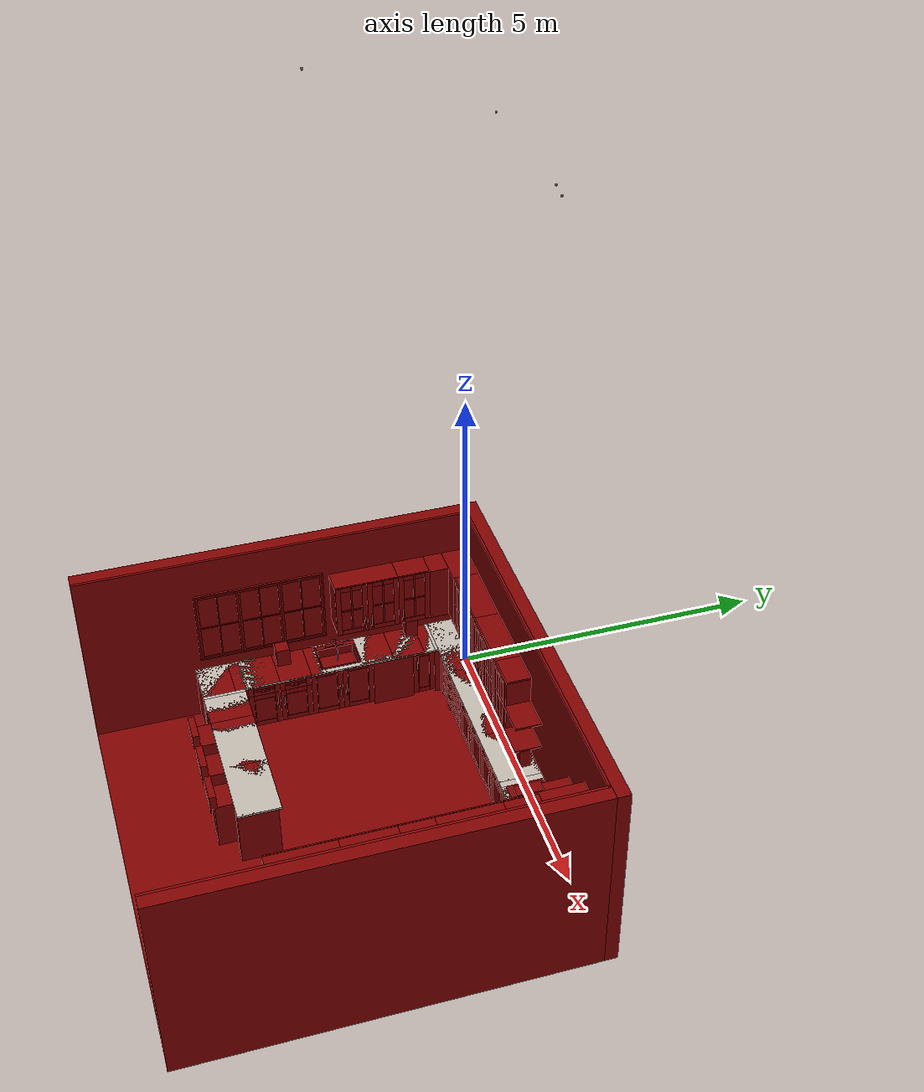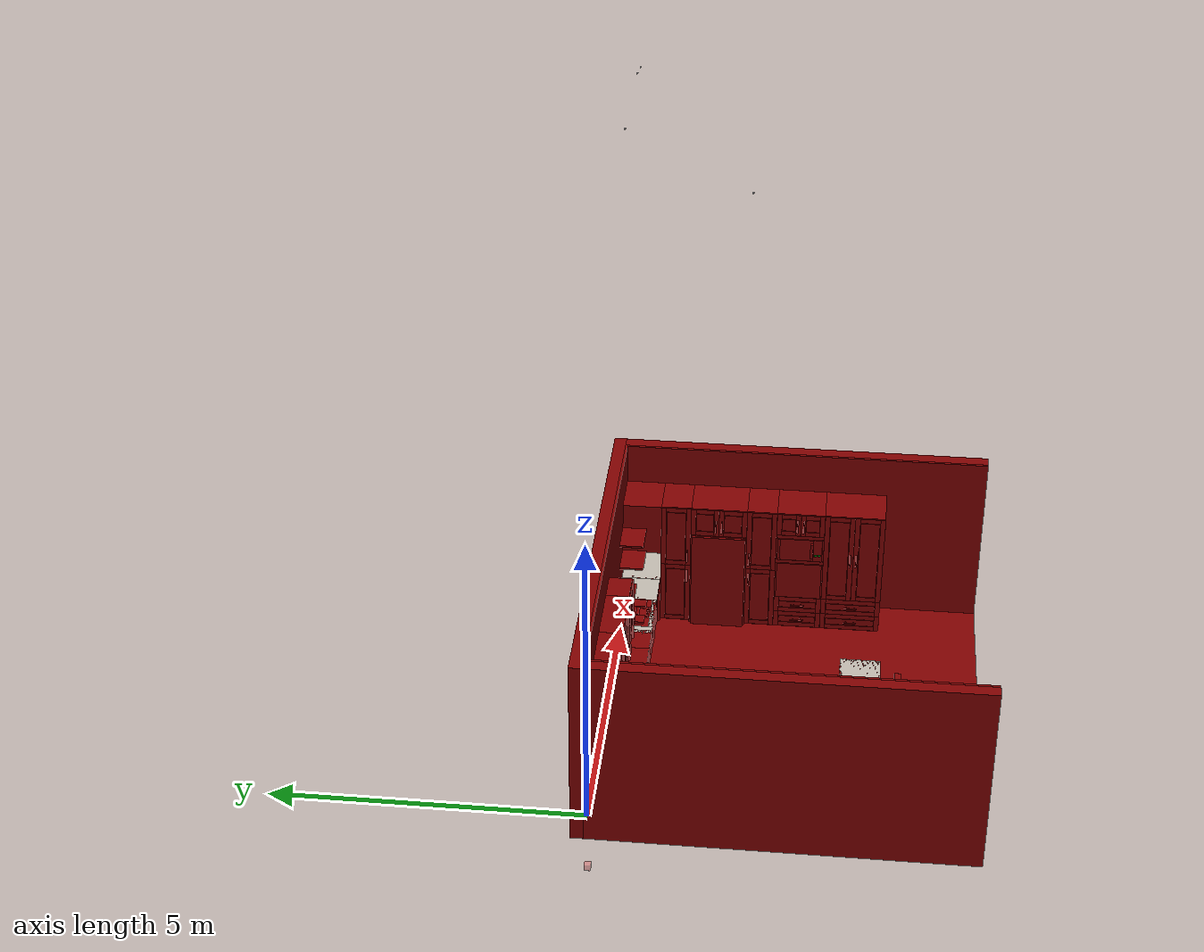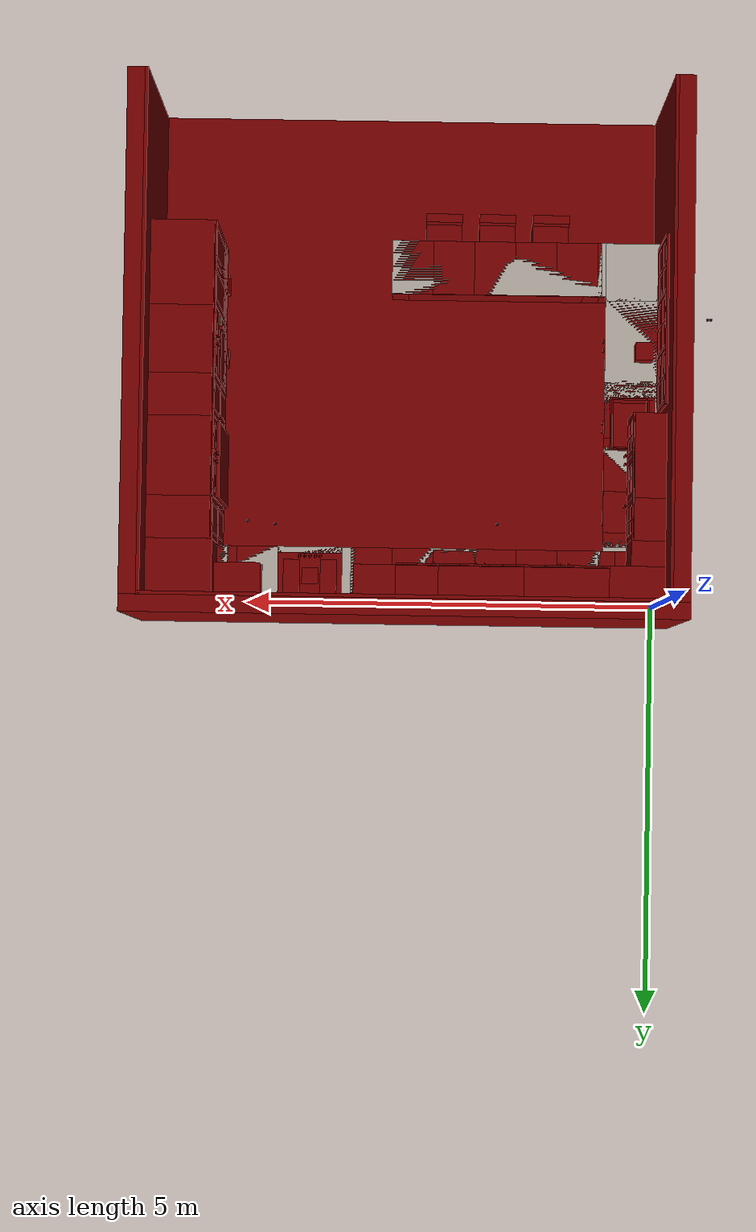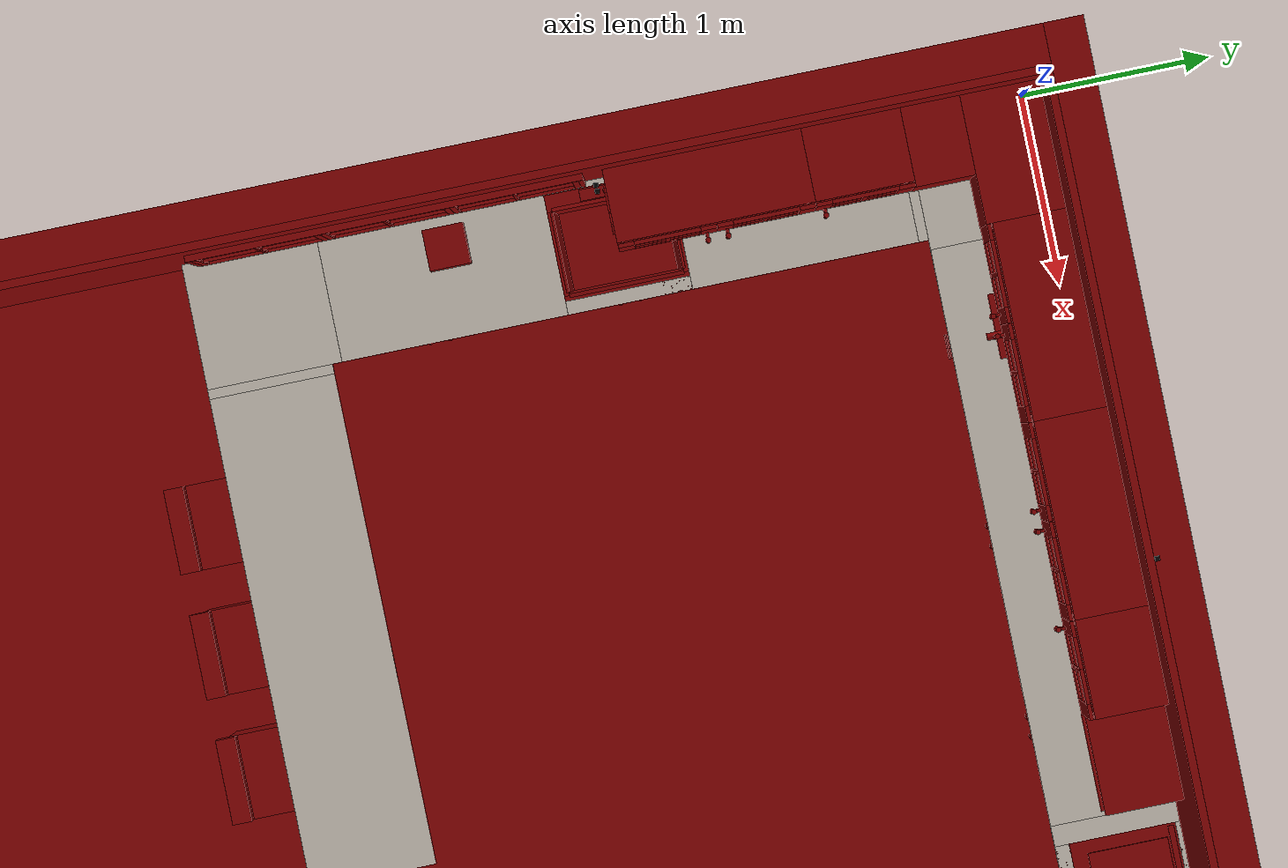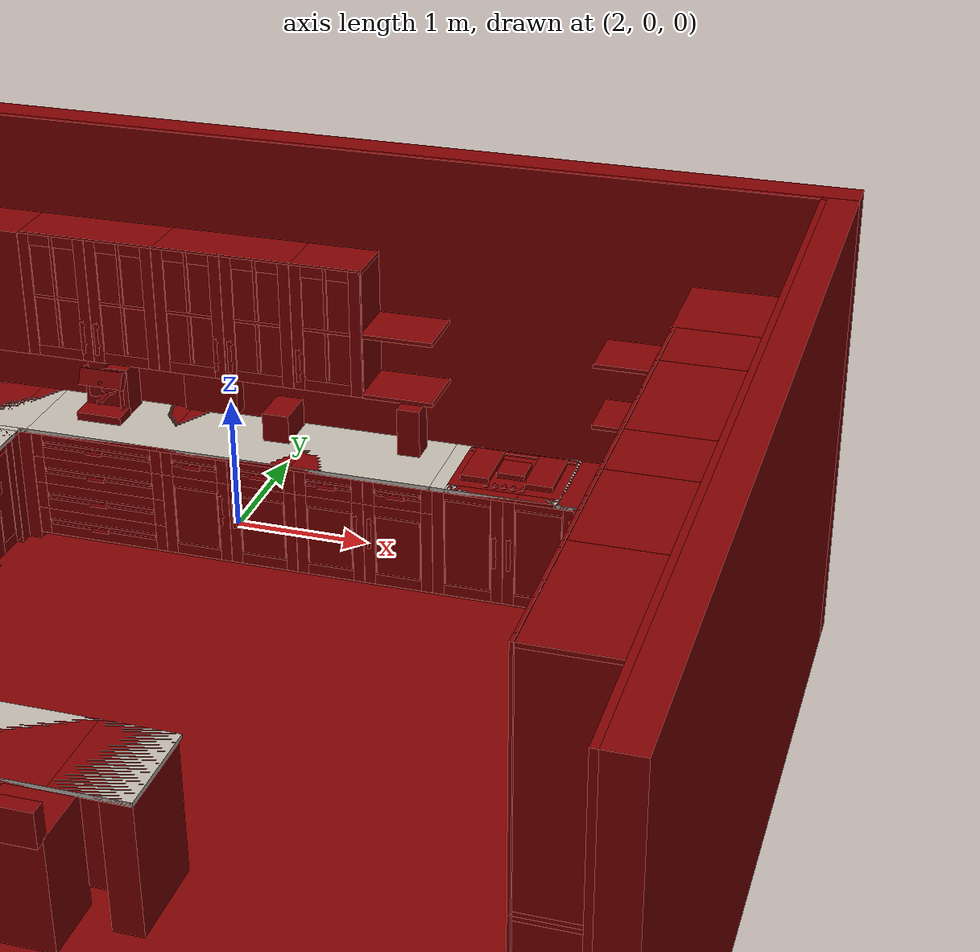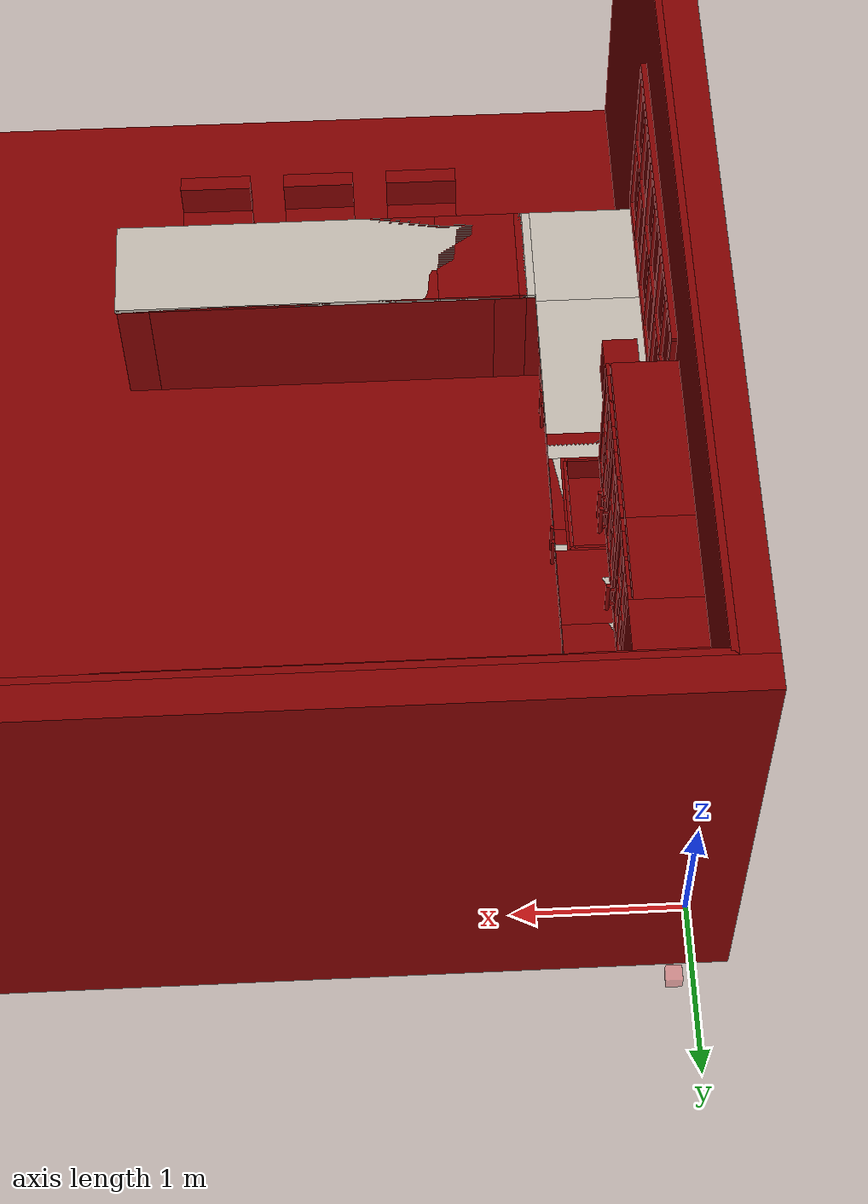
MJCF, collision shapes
<mujoco model="base">
  <compiler angle="radian" />

  <option impratio="20" density="1.2" viscosity="2e-05" cone="elliptic"/>

  <size njmax="5000" nconmax="5000"/>

  <visual>
    <map znear="0.001"/>
  </visual>

  <asset>
    <texture type="skybox" builtin="flat" rgb1="1 1 1" rgb2="1 1 1" width="256" height="1536"/>
    <texture type="2d" name="wall_room_wall" file="C:\Users/amars/robocasa/robocasa/models/assets/textures/tiles/varied_marble_tiles.png"/>
    <texture type="2d" name="wall_backing_room_wall" file="C:\Users/amars/robocasa/robocasa/models/assets/textures/flat/light_gray.png"/>
    <texture type="2d" name="wall_left_room_wall" file="C:\Users/amars/robocasa/robocasa/models/assets/textures/tiles/varied_marble_tiles.png"/>
    <texture type="2d" name="wall_left_backing_room_wall" file="C:\Users/amars/robocasa/robocasa/models/assets/textures/flat/light_gray.png"/>
    <texture type="2d" name="wall_right_room_wall" file="C:\Users/amars/robocasa/robocasa/models/assets/textures/tiles/varied_marble_tiles.png"/>
    <texture type="2d" name="wall_right_backing_room_wall" file="C:\Users/amars/robocasa/robocasa/models/assets/textures/flat/light_gray.png"/>
    <texture type="2d" name="outlet_room_tex-outlet" file="C:\Users/amars/robocasa/robocasa/models/assets/fixtures/accessories/outlets/simple_white/visuals/material_0.png"/>
    <texture type="2d" name="outlet_room_image0" file="C:\Users/amars/robocasa/robocasa/models/assets/fixtures/accessories/outlets/simple_white/visuals/image0.png"/>
    <texture type="2d" name="utensil_rack_room_tex-model" file="C:\Users/amars/robocasa/robocasa/models/assets/fixtures/accessories/utensil_racks/metal/visuals/material_0.png"/>
    <texture type="2d" name="utensil_rack_room_image4" file="C:\Users/amars/robocasa/robocasa/models/assets/fixtures/accessories/utensil_racks/metal/visuals/image4.png"/>
    <texture type="2d" name="utensil_rack_room_image0" file="C:\Users/amars/robocasa/robocasa/models/assets/fixtures/accessories/utensil_racks/metal/visuals/image0.png"/>
    <texture type="2d" name="utensil_rack_room_image11" file="C:\Users/amars/robocasa/robocasa/models/assets/fixtures/accessories/utensil_racks/metal/visuals/image11.png"/>
    <texture type="2d" name="utensil_rack_room_image14" file="C:\Users/amars/robocasa/robocasa/models/assets/fixtures/accessories/utensil_racks/metal/visuals/image14.png"/>
    <texture type="2d" name="utensil_rack_room_image17" file="C:\Users/amars/robocasa/robocasa/models/assets/fixtures/accessories/utensil_racks/metal/visuals/image17.png"/>
    <texture type="2d" name="utensil_rack_room_image7" file="C:\Users/amars/robocasa/robocasa/models/assets/fixtures/accessories/utensil_racks/metal/visuals/image7.png"/>
    <texture type="2d" name="light_switch_room_tex-light_switch" file="C:\Users/amars/robocasa/robocasa/models/assets/fixtures/accessories/light_switches/white_wide_switch/visuals/material_0.png"/>
    <texture type="2d" name="light_switch_room_image0" file="C:\Users/amars/robocasa/robocasa/models/assets/fixtures/accessories/light_switches/white_wide_switch/visuals/image0.png"/>
    <texture type="2d" name="light_switch_2_room_tex-light_switch" file="C:\Users/amars/robocasa/robocasa/models/assets/fixtures/accessories/light_switches/white_wide_switch/visuals/material_0.png"/>
    <texture type="2d" name="light_switch_2_room_image0" file="C:\Users/amars/robocasa/robocasa/models/assets/fixtures/accessories/light_switches/white_wide_switch/visuals/image0.png"/>
    <texture type="2d" name="outlet_2_room_tex-outlet" file="C:\Users/amars/robocasa/robocasa/models/assets/fixtures/accessories/outlets/simple_white/visuals/material_0.png"/>
    <texture type="2d" name="outlet_2_room_image0" file="C:\Users/amars/robocasa/robocasa/models/assets/fixtures/accessories/outlets/simple_white/visuals/image0.png"/>
    <texture type="2d" name="outlet_3_room_tex-outlet" file="C:\Users/amars/robocasa/robocasa/models/assets/fixtures/accessories/outlets/simple_white/visuals/material_0.png"/>
    <texture type="2d" name="outlet_3_room_image0" file="C:\Users/amars/robocasa/robocasa/models/assets/fixtures/accessories/outlets/simple_white/visuals/image0.png"/>
    <texture type="2d" name="floor_room_wall" file="C:\Users/amars/robocasa/robocasa/models/assets/textures/wood/warm_wood_planks.png"/>
    <texture type="2d" name="floor_backing_room_wall" file="C:\Users/amars/robocasa/robocasa/models/assets/textures/flat/light_gray.png"/>
    <texture type="2d" name="marble/marble_2d" file="C:\Users/amars/robocasa/robocasa/models/assets/textures/marble/marble.png"/>
    <texture type="cube" name="flat/white" file="C:\Users/amars/robocasa/robocasa/models/assets/textures/flat/white.png"/>
    <texture type="2d" name="stovetop_main_group_tex-model" file="C:\Users/amars/robocasa/robocasa/models/assets/fixtures/stovetops/pack_1_top_gas/visuals/material_0.png"/>
    <texture type="2d" name="stovetop_main_group_image16" file="C:\Users/amars/robocasa/robocasa/models/assets/fixtures/stovetops/pack_1_top_gas/visuals/image16.png"/>
    <texture type="2d" name="stovetop_main_group_image19" file="C:\Users/amars/robocasa/robocasa/models/assets/fixtures/stovetops/pack_1_top_gas/visuals/image19.png"/>
    <texture type="cube" name="box" file="C:\Users/amars/robocasa/robocasa/models/assets/textures/flat/white.png"/>
    <texture type="2d" name="flat/white_2d" file="C:\Users/amars/robocasa/robocasa/models/assets/textures/flat/white.png"/>
    <texture type="cube" name="metals/bright_metal" file="C:\Users/amars/robocasa/robocasa/models/assets/textures/metals/bright_metal.png"/>
    <texture type="2d" name="wood/warm_wood_parquet_2d" file="C:\Users/amars/robocasa/robocasa/models/assets/textures/wood/warm_wood_parquet.png"/>
    <texture type="2d" name="coffee_machine_main_group_tex-model" file="C:\Users/amars/robocasa/robocasa/models/assets/fixtures/coffee_machines/delonghi_espresso/visuals/material_0.png"/>
    <texture type="2d" name="coffee_machine_main_group_image3" file="C:\Users/amars/robocasa/robocasa/models/assets/fixtures/coffee_machines/delonghi_espresso/visuals/image3.png"/>
    <texture type="2d" name="coffee_machine_main_group_image4" file="C:\Users/amars/robocasa/robocasa/models/assets/fixtures/coffee_machines/delonghi_espresso/visuals/image4.png"/>
    <texture type="2d" name="coffee_machine_main_group_image12" file="C:\Users/amars/robocasa/robocasa/models/assets/fixtures/coffee_machines/delonghi_espresso/visuals/image12.png"/>
    <texture type="2d" name="coffee_machine_main_group_image11" file="C:\Users/amars/robocasa/robocasa/models/assets/fixtures/coffee_machines/delonghi_espresso/visuals/image11.png"/>
    <texture type="2d" name="coffee_machine_main_group_image1" file="C:\Users/amars/robocasa/robocasa/models/assets/fixtures/coffee_machines/delonghi_espresso/visuals/image1.png"/>
    <texture type="2d" name="coffee_machine_main_group_image8" file="C:\Users/amars/robocasa/robocasa/models/assets/fixtures/coffee_machines/delonghi_espresso/visuals/image8.png"/>
    <texture type="2d" name="coffee_machine_main_group_image10" file="C:\Users/amars/robocasa/robocasa/models/assets/fixtures/coffee_machines/delonghi_espresso/visuals/image10.png"/>
    <texture type="2d" name="coffee_machine_main_group_image9" file="C:\Users/amars/robocasa/robocasa/models/assets/fixtures/coffee_machines/delonghi_espresso/visuals/image9.png"/>
    <texture type="2d" name="toaster_main_group_tex-model" file="C:\Users/amars/robocasa/robocasa/models/assets/fixtures/toasters/vintage/visuals/material_0.png"/>
    <texture type="2d" name="toaster_main_group_image0" file="C:\Users/amars/robocasa/robocasa/models/assets/fixtures/toasters/vintage/visuals/image0.png"/>
    <texture type="2d" name="stool_1_front_group_tex-model" file="C:\Users/amars/robocasa/robocasa/models/assets/fixtures/accessories/stools/rattan_stool/visuals/material_0.png"/>
    <texture type="2d" name="stool_1_front_group_image0" file="C:\Users/amars/robocasa/robocasa/models/assets/fixtures/accessories/stools/rattan_stool/visuals/image0.png"/>
    <texture type="2d" name="stool_2_front_group_tex-model" file="C:\Users/amars/robocasa/robocasa/models/assets/fixtures/accessories/stools/rattan_stool/visuals/material_0.png"/>
    <texture type="2d" name="stool_2_front_group_image0" file="C:\Users/amars/robocasa/robocasa/models/assets/fixtures/accessories/stools/rattan_stool/visuals/image0.png"/>
    <texture type="2d" name="stool_3_front_group_tex-model" file="C:\Users/amars/robocasa/robocasa/models/assets/fixtures/accessories/stools/rattan_stool/visuals/material_0.png"/>
    <texture type="2d" name="stool_3_front_group_image0" file="C:\Users/amars/robocasa/robocasa/models/assets/fixtures/accessories/stools/rattan_stool/visuals/image0.png"/>
    <texture type="2d" name="sink_left_group_image0" file="C:\Users/amars/robocasa/robocasa/models/assets/fixtures/sinks/1_bin_wide_top_handle/visuals/image0.png"/>
    <texture type="2d" name="dishwasher_left_group_tex-model" file="C:\Users/amars/robocasa/robocasa/models/assets/fixtures/dishwashers/pack_1/visuals/material_0.png"/>
    <texture type="2d" name="dishwasher_left_group_image9" file="C:\Users/amars/robocasa/robocasa/models/assets/fixtures/dishwashers/pack_1/visuals/image9.png"/>
    <texture type="2d" name="dishwasher_left_group_image13" file="C:\Users/amars/robocasa/robocasa/models/assets/fixtures/dishwashers/pack_1/visuals/image13.png"/>
    <texture type="2d" name="window_group_left_group_panel_tex" file="C:\Users/amars/robocasa/robocasa/models/assets/textures/wood/dark_wood_planks.png"/>
    <texture type="2d" name="window_group_left_group_blurred_bak" file="C:\Users/amars/robocasa/robocasa/models/assets/textures/flat/warm_white.png"/>
    <texture type="2d" name="plant_left_group_tex-model" file="C:\Users/amars/robocasa/robocasa/models/assets/fixtures/accessories/plants/aloe/visuals/material_0.png"/>
    <texture type="2d" name="plant_left_group_image0" file="C:\Users/amars/robocasa/robocasa/models/assets/fixtures/accessories/plants/aloe/visuals/image0.png"/>
    <texture type="2d" name="plant_left_group_image1" file="C:\Users/amars/robocasa/robocasa/models/assets/fixtures/accessories/plants/aloe/visuals/image1.png"/>
    <texture type="2d" name="plant_left_group_image2" file="C:\Users/amars/robocasa/robocasa/models/assets/fixtures/accessories/plants/aloe/visuals/image2.png"/>
    <texture type="2d" name="plant_left_group_image3" file="C:\Users/amars/robocasa/robocasa/models/assets/fixtures/accessories/plants/aloe/visuals/image3.png"/>
    <texture type="2d" name="paper_towel_left_group_tex-model" file="C:\Users/amars/robocasa/robocasa/models/assets/fixtures/accessories/paper_towel_holders/holder_2/visuals/material_0.png"/>
    <texture type="2d" name="paper_towel_left_group_image0" file="C:\Users/amars/robocasa/robocasa/models/assets/fixtures/accessories/paper_towel_holders/holder_2/visuals/image0.png"/>
    <texture type="2d" name="paper_towel_left_group_image1" file="C:\Users/amars/robocasa/robocasa/models/assets/fixtures/accessories/paper_towel_holders/holder_2/visuals/image1.png"/>
    <texture type="2d" name="fridge_right_group_tex-model" file="C:\Users/amars/robocasa/robocasa/models/assets/fixtures/fridges/pack_1/visuals/material_0.png"/>
    <texture type="2d" name="fridge_right_group_image23" file="C:\Users/amars/robocasa/robocasa/models/assets/fixtures/fridges/pack_1/visuals/image23.png"/>
    <texture type="2d" name="fridge_right_group_image0" file="C:\Users/amars/robocasa/robocasa/models/assets/fixtures/fridges/pack_1/visuals/image0.png"/>
    <texture type="2d" name="microwave_right_group_tex-microwave2" file="C:\Users/amars/robocasa/robocasa/models/assets/fixtures/microwaves/standard/visuals/material_0.png"/>
    <texture type="2d" name="microwave_right_group_image0" file="C:\Users/amars/robocasa/robocasa/models/assets/fixtures/microwaves/standard/visuals/image0.png"/>
    <material name="wall_room_wall_mat" texture="wall_room_wall" texuniform="true" texrepeat="3 3" shininess="0.01" reflectance="0.1"/>
    <material name="wall_backing_room_wall_mat" texture="wall_backing_room_wall" texuniform="true" texrepeat="3 3" shininess="0.01" reflectance="0.1"/>
    <material name="wall_left_room_wall_mat" texture="wall_left_room_wall" texuniform="true" texrepeat="3 3" shininess="0.01" reflectance="0.1"/>
    <material name="wall_left_backing_room_wall_mat" texture="wall_left_backing_room_wall" texuniform="true" texrepeat="3 3" shininess="0.01" reflectance="0.1"/>
    <material name="wall_right_room_wall_mat" texture="wall_right_room_wall" texuniform="true" texrepeat="3 3" shininess="0.01" reflectance="0.1"/>
    <material name="wall_right_backing_room_wall_mat" texture="wall_right_backing_room_wall" texuniform="true" texrepeat="3 3" shininess="0.01" reflectance="0.1"/>
    <material name="outlet_room_outlet" texture="outlet_room_tex-outlet" reflectance="0.5"/>
    <material name="utensil_rack_room_model" texture="utensil_rack_room_tex-model" reflectance="0.5"/>
    <material name="utensil_rack_room_Ladle" texture="utensil_rack_room_image4" shininess="0.25"/>
    <material name="utensil_rack_room_MeatFork" texture="utensil_rack_room_image0" shininess="0.25"/>
    <material name="utensil_rack_room_Rack" texture="utensil_rack_room_image11" shininess="0.25"/>
    <material name="utensil_rack_room_Spatula" texture="utensil_rack_room_image14" shininess="0.25"/>
    <material name="utensil_rack_room_Spoon" texture="utensil_rack_room_image17" shininess="0.25"/>
    <material name="utensil_rack_room_Whisk" texture="utensil_rack_room_image7" shininess="0.25"/>
    <material name="light_switch_room_light_switch" texture="light_switch_room_tex-light_switch" reflectance="0.5"/>
    <material name="light_switch_room_lightswitch" texture="light_switch_room_image0" shininess="0.25"/>
    <material name="light_switch_2_room_light_switch" texture="light_switch_2_room_tex-light_switch" reflectance="0.5"/>
    <material name="light_switch_2_room_lightswitch" texture="light_switch_2_room_image0" shininess="0.25"/>
    <material name="outlet_2_room_outlet" texture="outlet_2_room_tex-outlet" reflectance="0.5"/>
    <material name="outlet_3_room_outlet" texture="outlet_3_room_tex-outlet" reflectance="0.5"/>
    <material name="floor_room_wall_mat" texture="floor_room_wall" texuniform="true" texrepeat="1.5 1.5"/>
    <material name="floor_backing_room_wall_mat" texture="floor_backing_room_wall" texuniform="true" texrepeat="1.5 1.5"/>
    <material name="counter_corner_main_group_counter_top" texture="marble/marble_2d" texuniform="true" texrepeat="3 3" shininess="0.1" reflectance="0.1"/>
    <material name="counter_corner_main_group_counter_base" texture="flat/white" shininess="0.1" reflectance="0.1"/>
    <material name="counter_main_main_group_counter_top" texture="marble/marble_2d" texuniform="true" texrepeat="3 3" shininess="0.1" reflectance="0.1"/>
    <material name="counter_main_main_group_counter_base" texture="flat/white" shininess="0.1" reflectance="0.1"/>
    <material name="stovetop_main_group_model" texture="stovetop_main_group_tex-model" reflectance="0.5"/>
    <material name="stovetop_main_group_TX_Stove_3_1.004" texture="stovetop_main_group_image16" shininess="0.25"/>
    <material name="stovetop_main_group_TX_Stove_3_2.004" texture="stovetop_main_group_image19" shininess="0.25"/>
    <material name="counter_1_main_group_counter_top" texture="marble/marble_2d" texuniform="true" texrepeat="3 3" shininess="0.1" reflectance="0.1"/>
    <material name="counter_1_main_group_counter_base" texture="flat/white" shininess="0.1" reflectance="0.1"/>
    <material name="counter_corner_2_main_group_counter_top" texture="marble/marble_2d" texuniform="true" texrepeat="3 3" shininess="0.1" reflectance="0.1"/>
    <material name="counter_corner_2_main_group_counter_base" texture="flat/white" shininess="0.1" reflectance="0.1"/>
    <material name="box_mat" texture="box" shininess="0.1"/>
    <material name="cab_1_main_group_mat" texture="flat/white" shininess="0.1"/>
    <material name="cab_1_main_group_left_door_mat" texture="flat/white_2d" texuniform="true" texrepeat="4 4" shininess="0.1" reflectance="0.1"/>
    <material name="cab_1_main_group_left_door_transparent_material" specular="0" shininess="0" rgba="1 1 1 0.1"/>
    <material name="cab_1_main_group_left_door_handle_mat" texture="metals/bright_metal" shininess="0.8" reflectance="0.8"/>
    <material name="cab_1_main_group_right_door_mat" texture="flat/white_2d" texuniform="true" texrepeat="4 4" shininess="0.1" reflectance="0.1"/>
    <material name="cab_1_main_group_right_door_transparent_material" specular="0" shininess="0" rgba="1 1 1 0.1"/>
    <material name="cab_1_main_group_right_door_handle_mat" texture="metals/bright_metal" shininess="0.8" reflectance="0.8"/>
    <material name="cab_main_main_group_mat" texture="flat/white" shininess="0.1"/>
    <material name="cab_main_main_group_left_door_mat" texture="flat/white_2d" texuniform="true" texrepeat="4 4" shininess="0.1" reflectance="0.1"/>
    <material name="cab_main_main_group_left_door_transparent_material" specular="0" shininess="0" rgba="1 1 1 0.1"/>
    <material name="cab_main_main_group_left_door_handle_mat" texture="metals/bright_metal" shininess="0.8" reflectance="0.8"/>
    <material name="cab_main_main_group_right_door_mat" texture="flat/white_2d" texuniform="true" texrepeat="4 4" shininess="0.1" reflectance="0.1"/>
    <material name="cab_main_main_group_right_door_transparent_material" specular="0" shininess="0" rgba="1 1 1 0.1"/>
    <material name="cab_main_main_group_right_door_handle_mat" texture="metals/bright_metal" shininess="0.8" reflectance="0.8"/>
    <material name="cab_2_main_group_mat" texture="flat/white" shininess="0.1"/>
    <material name="cab_2_main_group_door_mat" texture="flat/white_2d" texuniform="true" texrepeat="4 4" shininess="0.1" reflectance="0.1"/>
    <material name="cab_2_main_group_door_transparent_material" specular="0" shininess="0" rgba="1 1 1 0.1"/>
    <material name="cab_2_main_group_door_handle_mat" texture="metals/bright_metal" shininess="0.8" reflectance="0.8"/>
    <material name="shelves_1_main_group_mat" texture="wood/warm_wood_parquet_2d" shininess="0.8" reflectance="0.8"/>
    <material name="shelves_1_main_group_shelf_0_mat" texture="wood/warm_wood_parquet_2d" texuniform="true" texrepeat="3 3" shininess="0.1" reflectance="0.1"/>
    <material name="shelves_1_main_group_shelf_1_mat" texture="wood/warm_wood_parquet_2d" texuniform="true" texrepeat="3 3" shininess="0.1" reflectance="0.1"/>
    <material name="hood_main_group_Hood_light" shininess="0"/>
    <material name="hood_main_group_Hood_light_2" shininess="0"/>
    <material name="hood_main_group_Hood_metal" shininess="0.684381" rgba="0.8 0.8 0.8 1"/>
    <material name="shelves_2_main_group_mat" texture="wood/warm_wood_parquet_2d" shininess="0.8" reflectance="0.8"/>
    <material name="shelves_2_main_group_shelf_0_mat" texture="wood/warm_wood_parquet_2d" texuniform="true" texrepeat="3 3" shininess="0.1" reflectance="0.1"/>
    <material name="shelves_2_main_group_shelf_1_mat" texture="wood/warm_wood_parquet_2d" texuniform="true" texrepeat="3 3" shininess="0.1" reflectance="0.1"/>
    <material name="stack_1_main_group_1_mat" texture="flat/white" shininess="0.1"/>
    <material name="stack_1_main_group_1_door_mat" texture="flat/white_2d" texuniform="true" texrepeat="4 4" shininess="0.1" reflectance="0.1"/>
    <material name="stack_1_main_group_1_door_handle_mat" texture="metals/bright_metal" shininess="0.8" reflectance="0.8"/>
    <material name="stack_1_main_group_2_mat" texture="flat/white" shininess="0.1"/>
    <material name="stack_1_main_group_2_door_mat" texture="flat/white_2d" texuniform="true" texrepeat="4 4" shininess="0.1" reflectance="0.1"/>
    <material name="stack_1_main_group_2_door_handle_mat" texture="metals/bright_metal" shininess="0.8" reflectance="0.8"/>
    <material name="stack_1_main_group_3_mat" texture="flat/white" shininess="0.1"/>
    <material name="stack_1_main_group_3_door_mat" texture="flat/white_2d" texuniform="true" texrepeat="4 4" shininess="0.1" reflectance="0.1"/>
    <material name="stack_1_main_group_3_door_handle_mat" texture="metals/bright_metal" shininess="0.8" reflectance="0.8"/>
    <material name="stack_1_main_group_4_mat" texture="flat/white" shininess="0.1"/>
    <material name="stack_1_main_group_4_door_mat" texture="flat/white_2d" texuniform="true" texrepeat="4 4" shininess="0.1" reflectance="0.1"/>
    <material name="stack_1_main_group_4_door_handle_mat" texture="metals/bright_metal" shininess="0.8" reflectance="0.8"/>
    <material name="stack_2_main_group_1_mat" texture="flat/white" shininess="0.1"/>
    <material name="stack_2_main_group_1_left_door_mat" texture="flat/white_2d" texuniform="true" texrepeat="4 4" shininess="0.1" reflectance="0.1"/>
    <material name="stack_2_main_group_1_left_door_handle_mat" texture="metals/bright_metal" shininess="0.8" reflectance="0.8"/>
    <material name="stack_2_main_group_1_right_door_mat" texture="flat/white_2d" texuniform="true" texrepeat="4 4" shininess="0.1" reflectance="0.1"/>
    <material name="stack_2_main_group_1_right_door_handle_mat" texture="metals/bright_metal" shininess="0.8" reflectance="0.8"/>
    <material name="stack_2_main_group_2_mat" texture="flat/white" shininess="0.1"/>
    <material name="stack_2_main_group_2_door_mat" texture="flat/white_2d" texuniform="true" texrepeat="4 4" shininess="0.1" reflectance="0.1"/>
    <material name="stack_2_main_group_2_door_handle_mat" texture="metals/bright_metal" shininess="0.8" reflectance="0.8"/>
    <material name="stack_2_main_group_3_mat" texture="flat/white" shininess="0.1"/>
    <material name="stack_2_main_group_3_door_mat" texture="flat/white_2d" texuniform="true" texrepeat="4 4" shininess="0.1" reflectance="0.1"/>
    <material name="stack_2_main_group_3_door_handle_mat" texture="metals/bright_metal" shininess="0.8" reflectance="0.8"/>
    <material name="stack_3_main_group_1_mat" texture="flat/white" shininess="0.1"/>
    <material name="stack_3_main_group_1_left_door_mat" texture="flat/white_2d" texuniform="true" texrepeat="4 4" shininess="0.1" reflectance="0.1"/>
    <material name="stack_3_main_group_1_left_door_handle_mat" texture="metals/bright_metal" shininess="0.8" reflectance="0.8"/>
    <material name="stack_3_main_group_1_right_door_mat" texture="flat/white_2d" texuniform="true" texrepeat="4 4" shininess="0.1" reflectance="0.1"/>
    <material name="stack_3_main_group_1_right_door_handle_mat" texture="metals/bright_metal" shininess="0.8" reflectance="0.8"/>
    <material name="stack_3_main_group_2_mat" texture="flat/white" shininess="0.1"/>
    <material name="stack_3_main_group_2_door_mat" texture="flat/white_2d" texuniform="true" texrepeat="4 4" shininess="0.1" reflectance="0.1"/>
    <material name="stack_3_main_group_2_door_handle_mat" texture="metals/bright_metal" shininess="0.8" reflectance="0.8"/>
    <material name="stack_3_main_group_3_mat" texture="flat/white" shininess="0.1"/>
    <material name="stack_3_main_group_3_door_mat" texture="flat/white_2d" texuniform="true" texrepeat="4 4" shininess="0.1" reflectance="0.1"/>
    <material name="stack_3_main_group_3_door_handle_mat" texture="metals/bright_metal" shininess="0.8" reflectance="0.8"/>
    <material name="stack_4_main_group_1_mat" texture="flat/white" shininess="0.1"/>
    <material name="stack_4_main_group_1_left_door_mat" texture="flat/white_2d" texuniform="true" texrepeat="4 4" shininess="0.1" reflectance="0.1"/>
    <material name="stack_4_main_group_1_left_door_handle_mat" texture="metals/bright_metal" shininess="0.8" reflectance="0.8"/>
    <material name="stack_4_main_group_1_right_door_mat" texture="flat/white_2d" texuniform="true" texrepeat="4 4" shininess="0.1" reflectance="0.1"/>
    <material name="stack_4_main_group_1_right_door_handle_mat" texture="metals/bright_metal" shininess="0.8" reflectance="0.8"/>
    <material name="stack_5_main_group_1_mat" texture="flat/white" shininess="0.1"/>
    <material name="stack_5_main_group_1_door_mat" texture="flat/white_2d" texuniform="true" texrepeat="4 4" shininess="0.1" reflectance="0.1"/>
    <material name="stack_5_main_group_1_door_handle_mat" texture="metals/bright_metal" shininess="0.8" reflectance="0.8"/>
    <material name="stack_5_main_group_2_mat" texture="flat/white" shininess="0.1"/>
    <material name="stack_5_main_group_2_door_mat" texture="flat/white_2d" texuniform="true" texrepeat="4 4" shininess="0.1" reflectance="0.1"/>
    <material name="stack_5_main_group_2_door_handle_mat" texture="metals/bright_metal" shininess="0.8" reflectance="0.8"/>
    <material name="coffee_machine_main_group_model" texture="coffee_machine_main_group_tex-model" reflectance="0.5"/>
    <material name="coffee_machine_main_group_Material_53" texture="coffee_machine_main_group_image3" shininess="0.1225"/>
    <material name="coffee_machine_main_group_back" shininess="0.1225" rgba="0 0 0 1"/>
    <material name="coffee_machine_main_group_body" shininess="1"/>
    <material name="coffee_machine_main_group_body_side" texture="coffee_machine_main_group_image4" shininess="0.25"/>
    <material name="coffee_machine_main_group_chrome" shininess="0.64"/>
    <material name="coffee_machine_main_group_glass" texture="coffee_machine_main_group_image12" shininess="0.25"/>
    <material name="coffee_machine_main_group_handle" texture="coffee_machine_main_group_image11" shininess="0.1225"/>
    <material name="coffee_machine_main_group_material" texture="coffee_machine_main_group_image1" shininess="0.25"/>
    <material name="coffee_machine_main_group_material_2" texture="coffee_machine_main_group_image8" shininess="1"/>
    <material name="coffee_machine_main_group_material_5" shininess="1"/>
    <material name="coffee_machine_main_group_panel" texture="coffee_machine_main_group_image10" shininess="0.5625"/>
    <material name="coffee_machine_main_group_steel" shininess="1"/>
    <material name="coffee_machine_main_group_text" texture="coffee_machine_main_group_image9" shininess="1"/>
    <material name="coffee_machine_main_group_under" shininess="0" rgba="0 0 0 1"/>
    <material name="toaster_main_group_model" texture="toaster_main_group_tex-model" reflectance="0.5"/>
    <material name="toaster_main_group_toaster" texture="toaster_main_group_image0" shininess="0.25"/>
    <material name="utensil_holder_main_group_Bege" shininess="0.16" rgba="0.621795 0.53677 0.365757 1"/>
    <material name="utensil_holder_main_group_Prata" shininess="0.16" rgba="0.504 0.504 0.504 1"/>
    <material name="utensil_holder_main_group_Preto" shininess="0.16" rgba="0 0 0 1"/>
    <material name="utensil_holder_main_group_lambert1" shininess="0.16" rgba="0.5 0.5 0.5 1"/>
    <material name="counter_1_front_group_counter_top" texture="marble/marble_2d" texuniform="true" texrepeat="3 3" shininess="0.1" reflectance="0.1"/>
    <material name="counter_1_front_group_counter_base" texture="flat/white" shininess="0.1" reflectance="0.1"/>
    <material name="counter_corner_front_group_counter_top" texture="marble/marble_2d" texuniform="true" texrepeat="3 3" shininess="0.1" reflectance="0.1"/>
    <material name="counter_corner_front_group_counter_base" texture="flat/white" shininess="0.1" reflectance="0.1"/>
    <material name="stool_1_front_group_model" texture="stool_1_front_group_tex-model" reflectance="0.5"/>
    <material name="stool_1_front_group_HBS_0001_M1" texture="stool_1_front_group_image0" shininess="0.25"/>
    <material name="stool_2_front_group_model" texture="stool_2_front_group_tex-model" reflectance="0.5"/>
    <material name="stool_2_front_group_HBS_0001_M1" texture="stool_2_front_group_image0" shininess="0.25"/>
    <material name="stool_3_front_group_model" texture="stool_3_front_group_tex-model" reflectance="0.5"/>
    <material name="stool_3_front_group_HBS_0001_M1" texture="stool_3_front_group_image0" shininess="0.25"/>
    <material name="counter_corner_left_group_counter_top" texture="marble/marble_2d" texuniform="true" texrepeat="3 3" shininess="0.1" reflectance="0.1"/>
    <material name="counter_corner_left_group_counter_base" texture="flat/white" shininess="0.1" reflectance="0.1"/>
    <material name="sink_left_group_kitchen_sink" texture="sink_left_group_image0" shininess="0.25"/>
    <material name="counter_1_left_group_counter_top" texture="marble/marble_2d" texuniform="true" texrepeat="3 3" shininess="0.1" reflectance="0.1"/>
    <material name="counter_1_left_group_counter_base" texture="flat/white" shininess="0.1" reflectance="0.1"/>
    <material name="counter_corner_right_left_group_counter_top" texture="marble/marble_2d" texuniform="true" texrepeat="3 3" shininess="0.1" reflectance="0.1"/>
    <material name="counter_corner_right_left_group_counter_base" texture="flat/white" shininess="0.1" reflectance="0.1"/>
    <material name="stack_1_left_group_1_mat" texture="flat/white" shininess="0.1"/>
    <material name="stack_1_left_group_1_left_door_mat" texture="flat/white_2d" texuniform="true" texrepeat="4 4" shininess="0.1" reflectance="0.1"/>
    <material name="stack_1_left_group_1_left_door_handle_mat" texture="metals/bright_metal" shininess="0.8" reflectance="0.8"/>
    <material name="stack_1_left_group_1_right_door_mat" texture="flat/white_2d" texuniform="true" texrepeat="4 4" shininess="0.1" reflectance="0.1"/>
    <material name="stack_1_left_group_1_right_door_handle_mat" texture="metals/bright_metal" shininess="0.8" reflectance="0.8"/>
    <material name="stack_1_left_group_2_mat" texture="flat/white" shininess="0.1"/>
    <material name="stack_1_left_group_2_door_mat" texture="flat/white_2d" texuniform="true" texrepeat="4 4" shininess="0.1" reflectance="0.1"/>
    <material name="stack_1_left_group_2_door_handle_mat" texture="metals/bright_metal" shininess="0.8" reflectance="0.8"/>
    <material name="stack_1_left_group_3_mat" texture="flat/white" shininess="0.1"/>
    <material name="stack_1_left_group_3_door_mat" texture="flat/white_2d" texuniform="true" texrepeat="4 4" shininess="0.1" reflectance="0.1"/>
    <material name="stack_1_left_group_3_door_handle_mat" texture="metals/bright_metal" shininess="0.8" reflectance="0.8"/>
    <material name="stack_2_left_group_1_mat" texture="flat/white" shininess="0.1"/>
    <material name="stack_2_left_group_1_left_door_mat" texture="flat/white_2d" texuniform="true" texrepeat="4 4" shininess="0.1" reflectance="0.1"/>
    <material name="stack_2_left_group_1_left_door_handle_mat" texture="metals/bright_metal" shininess="0.8" reflectance="0.8"/>
    <material name="stack_2_left_group_1_right_door_mat" texture="flat/white_2d" texuniform="true" texrepeat="4 4" shininess="0.1" reflectance="0.1"/>
    <material name="stack_2_left_group_1_right_door_handle_mat" texture="metals/bright_metal" shininess="0.8" reflectance="0.8"/>
    <material name="dishwasher_left_group_model" texture="dishwasher_left_group_tex-model" reflectance="0.5"/>
    <material name="dishwasher_left_group_TX_Dishwasher_3_1" texture="dishwasher_left_group_image9" shininess="0.25"/>
    <material name="dishwasher_left_group_TX_Dishwasher_3_2" texture="dishwasher_left_group_image13" shininess="0.25"/>
    <material name="stack_3_left_group_1_mat" texture="flat/white" shininess="0.1"/>
    <material name="stack_3_left_group_1_door_mat" texture="flat/white_2d" texuniform="true" texrepeat="4 4" shininess="0.1" reflectance="0.1"/>
    <material name="stack_3_left_group_1_door_handle_mat" texture="metals/bright_metal" shininess="0.8" reflectance="0.8"/>
    <material name="window_group_left_group_panel_mat" texture="window_group_left_group_panel_tex" texuniform="true" texrepeat="4 4" specular="0.1" shininess="0.1"/>
    <material name="window_group_left_group_window_mat" texture="window_group_left_group_blurred_bak" texuniform="true" specular="0.1" shininess="0.1"/>
    <material name="cab_1_left_group_mat" texture="flat/white" shininess="0.1"/>
    <material name="cab_1_left_group_left_door_mat" texture="flat/white_2d" texuniform="true" texrepeat="4 4" shininess="0.1" reflectance="0.1"/>
    <material name="cab_1_left_group_left_door_transparent_material" specular="0" shininess="0" rgba="1 1 1 0.1"/>
    <material name="cab_1_left_group_left_door_handle_mat" texture="metals/bright_metal" shininess="0.8" reflectance="0.8"/>
    <material name="cab_1_left_group_right_door_mat" texture="flat/white_2d" texuniform="true" texrepeat="4 4" shininess="0.1" reflectance="0.1"/>
    <material name="cab_1_left_group_right_door_transparent_material" specular="0" shininess="0" rgba="1 1 1 0.1"/>
    <material name="cab_1_left_group_right_door_handle_mat" texture="metals/bright_metal" shininess="0.8" reflectance="0.8"/>
    <material name="cab_2_left_group_mat" texture="flat/white" shininess="0.1"/>
    <material name="cab_2_left_group_door_mat" texture="flat/white_2d" texuniform="true" texrepeat="4 4" shininess="0.1" reflectance="0.1"/>
    <material name="cab_2_left_group_door_transparent_material" specular="0" shininess="0" rgba="1 1 1 0.1"/>
    <material name="cab_2_left_group_door_handle_mat" texture="metals/bright_metal" shininess="0.8" reflectance="0.8"/>
    <material name="plant_left_group_model" texture="plant_left_group_tex-model" reflectance="0.5"/>
    <material name="plant_left_group_blinn1SG" texture="plant_left_group_image0" shininess="0.16"/>
    <material name="plant_left_group_blinn2SG" texture="plant_left_group_image1" shininess="0.16"/>
    <material name="plant_left_group_blinn3SG" texture="plant_left_group_image2" shininess="0.16"/>
    <material name="plant_left_group_blinn4SG" texture="plant_left_group_image3" shininess="0"/>
    <material name="paper_towel_left_group_model" texture="paper_towel_left_group_tex-model" reflectance="0.5"/>
    <material name="paper_towel_left_group_metal" shininess="0.0553676" rgba="0.35595 0.35595 0.35595 1"/>
    <material name="paper_towel_left_group_paperSide" texture="paper_towel_left_group_image0" shininess="0"/>
    <material name="paper_towel_left_group_paperTopAndBottom" texture="paper_towel_left_group_image1" shininess="0"/>
    <material name="paper_towel_left_group_paperboard" shininess="0" rgba="0.327778 0.266356 0.198069 1"/>
    <material name="stack_left_right_group_1_mat" texture="flat/white" shininess="0.1"/>
    <material name="stack_left_right_group_1_door_mat" texture="flat/white_2d" texuniform="true" texrepeat="4 4" shininess="0.1" reflectance="0.1"/>
    <material name="stack_left_right_group_1_door_handle_mat" texture="metals/bright_metal" shininess="0.8" reflectance="0.8"/>
    <material name="stack_left_right_group_2_mat" texture="flat/white" shininess="0.1"/>
    <material name="stack_left_right_group_2_door_mat" texture="flat/white_2d" texuniform="true" texrepeat="4 4" shininess="0.1" reflectance="0.1"/>
    <material name="stack_left_right_group_2_door_handle_mat" texture="metals/bright_metal" shininess="0.8" reflectance="0.8"/>
    <material name="fridge_right_group_model" texture="fridge_right_group_tex-model" reflectance="0.5"/>
    <material name="fridge_right_group_TX_Fridge_3_1" texture="fridge_right_group_image23" shininess="0.25"/>
    <material name="fridge_right_group_TX_Fridge_3_2" texture="fridge_right_group_image0" shininess="0.25"/>
    <material name="fridge_housing_right_group_mat" texture="flat/white" shininess="0.1"/>
    <material name="fridge_top_right_group_mat" texture="flat/white" shininess="0.1"/>
    <material name="fridge_top_right_group_left_door_mat" texture="flat/white_2d" texuniform="true" texrepeat="4 4" shininess="0.1" reflectance="0.1"/>
    <material name="fridge_top_right_group_left_door_handle_mat" texture="metals/bright_metal" shininess="0.8" reflectance="0.8"/>
    <material name="fridge_top_right_group_right_door_mat" texture="flat/white_2d" texuniform="true" texrepeat="4 4" shininess="0.1" reflectance="0.1"/>
    <material name="fridge_top_right_group_right_door_handle_mat" texture="metals/bright_metal" shininess="0.8" reflectance="0.8"/>
    <material name="stack_right_right_group_1_mat" texture="flat/white" shininess="0.1"/>
    <material name="stack_right_right_group_1_door_mat" texture="flat/white_2d" texuniform="true" texrepeat="4 4" shininess="0.1" reflectance="0.1"/>
    <material name="stack_right_right_group_1_door_handle_mat" texture="metals/bright_metal" shininess="0.8" reflectance="0.8"/>
    <material name="stack_right_right_group_2_mat" texture="flat/white" shininess="0.1"/>
    <material name="stack_right_right_group_2_door_mat" texture="flat/white_2d" texuniform="true" texrepeat="4 4" shininess="0.1" reflectance="0.1"/>
    <material name="stack_right_right_group_2_door_handle_mat" texture="metals/bright_metal" shininess="0.8" reflectance="0.8"/>
    <material name="bottom_right_group_1_mat" texture="flat/white" shininess="0.1"/>
    <material name="bottom_right_group_1_door_mat" texture="flat/white_2d" texuniform="true" texrepeat="4 4" shininess="0.1" reflectance="0.1"/>
    <material name="bottom_right_group_1_door_handle_mat" texture="metals/bright_metal" shininess="0.8" reflectance="0.8"/>
    <material name="bottom_right_group_2_mat" texture="flat/white" shininess="0.1"/>
    <material name="bottom_right_group_2_door_mat" texture="flat/white_2d" texuniform="true" texrepeat="4 4" shininess="0.1" reflectance="0.1"/>
    <material name="bottom_right_group_2_door_handle_mat" texture="metals/bright_metal" shininess="0.8" reflectance="0.8"/>
    <material name="oven_right_group_Glass_Basic_White" shininess="1"/>
    <material name="oven_right_group_Hard_Shiny_Plastic_Red" shininess="1" rgba="0.902495 0.002258 0.00226 1"/>
    <material name="oven_right_group_Hard_Shiny_Plastic_Red_1" shininess="1" rgba="0.902495 0.002258 0.00226 1"/>
    <material name="oven_right_group_Steel_Rough" shininess="0.386744" rgba="0.619608 0.592157 0.572549 1"/>
    <material name="oven_right_group_Steel_Rough_1" shininess="0.00178885" rgba="0.619608 0.592157 0.572549 1"/>
    <material name="oven_right_group_black150150160" shininess="0.342701" rgba="0.588235 0.588235 0.627451 1"/>
    <material name="oven_right_group_black150150160_0" shininess="1" rgba="0.588235 0.588235 0.627451 1"/>
    <material name="oven_right_group_brushed_aluminum228233237" shininess="0.357086" rgba="0.894118 0.913725 0.929412 1"/>
    <material name="oven_right_group_brushed_aluminum228233237_0" shininess="0.00178885" rgba="0.894118 0.913725 0.929412 1"/>
    <material name="oven_right_group_brushed_aluminum228233237_1" shininess="0.00178885" rgba="0.894118 0.913725 0.929412 1"/>
    <material name="oven_right_group_brushed_aluminum228233237_2" shininess="0.00178885" rgba="0.894118 0.913725 0.929412 1"/>
    <material name="oven_right_group_brushed_aluminum228233237_3" shininess="0.525989" rgba="0.894118 0.913725 0.929412 1"/>
    <material name="oven_right_group_brushed_aluminum228233237_4" shininess="0.349857" rgba="0.894118 0.913725 0.929412 1"/>
    <material name="oven_right_group_brushed_aluminum228233237_5" shininess="0.328611" rgba="0.894118 0.913725 0.929412 1"/>
    <material name="oven_right_group_brushed_aluminum228233237_6" shininess="0.00178885" rgba="0.894118 0.913725 0.929412 1"/>
    <material name="oven_right_group_candy_apple_red2476666" shininess="1" rgba="0.979986 0.000679 0.000679 1"/>
    <material name="oven_right_group_color128128128" shininess="0.00178885" rgba="0.501961 0.501961 0.501961 1"/>
    <material name="oven_right_group_polished_aluminum170178196" shininess="0.36439" rgba="0.666667 0.698039 0.768627 1"/>
    <material name="oven_right_group_polished_aluminum170178196_0" shininess="0.386744" rgba="0.666667 0.698039 0.768627 1"/>
    <material name="oven_right_group_steel_grey214214234" shininess="1" rgba="0.839216 0.839216 0.917647 1"/>
    <material name="oven_right_group_white255255255" shininess="1"/>
    <material name="oven_right_group_white255255255_0" shininess="1"/>
    <material name="oven_housing_right_group_mat" texture="flat/white" shininess="0.1"/>
    <material name="microwave_right_group_microwave2" texture="microwave_right_group_tex-microwave2" reflectance="0.5"/>
    <material name="microwave_right_group_Oven" texture="microwave_right_group_image0" shininess="0.25"/>
    <material name="micro_housing_right_group_mat" texture="flat/white" shininess="0.1"/>
    <material name="top_right_group_mat" texture="flat/white" shininess="0.1"/>
    <material name="top_right_group_left_door_mat" texture="flat/white_2d" texuniform="true" texrepeat="4 4" shininess="0.1" reflectance="0.1"/>
    <material name="top_right_group_left_door_handle_mat" texture="metals/bright_metal" shininess="0.8" reflectance="0.8"/>
    <material name="top_right_group_right_door_mat" texture="flat/white_2d" texuniform="true" texrepeat="4 4" shininess="0.1" reflectance="0.1"/>
    <material name="top_right_group_right_door_handle_mat" texture="metals/bright_metal" shininess="0.8" reflectance="0.8"/>
    <material name="side_bottom_right_group_1_mat" texture="flat/white" shininess="0.1"/>
    <material name="side_bottom_right_group_1_door_mat" texture="flat/white_2d" texuniform="true" texrepeat="4 4" shininess="0.1" reflectance="0.1"/>
    <material name="side_bottom_right_group_1_door_handle_mat" texture="metals/bright_metal" shininess="0.8" reflectance="0.8"/>
    <material name="side_bottom_right_group_2_mat" texture="flat/white" shininess="0.1"/>
    <material name="side_bottom_right_group_2_door_mat" texture="flat/white_2d" texuniform="true" texrepeat="4 4" shininess="0.1" reflectance="0.1"/>
    <material name="side_bottom_right_group_2_door_handle_mat" texture="metals/bright_metal" shininess="0.8" reflectance="0.8"/>
    <material name="side_bottom_right_group_3_mat" texture="flat/white" shininess="0.1"/>
    <material name="side_bottom_right_group_3_left_door_mat" texture="flat/white_2d" texuniform="true" texrepeat="4 4" shininess="0.1" reflectance="0.1"/>
    <material name="side_bottom_right_group_3_left_door_handle_mat" texture="metals/bright_metal" shininess="0.8" reflectance="0.8"/>
    <material name="side_bottom_right_group_3_right_door_mat" texture="flat/white_2d" texuniform="true" texrepeat="4 4" shininess="0.1" reflectance="0.1"/>
    <material name="side_bottom_right_group_3_right_door_handle_mat" texture="metals/bright_metal" shininess="0.8" reflectance="0.8"/>
    <mesh name="outlet_room_outlet_0_vis" file="C:\Users/amars/robocasa/robocasa/models/assets/fixtures/accessories/outlets/simple_white/visuals/outlet_0.obj" scale="0.15 0.15 0.15"/>
    <mesh name="utensil_rack_room_model_0_vis" file="C:\Users/amars/robocasa/robocasa/models/assets/fixtures/accessories/utensil_racks/metal/visuals/model_0.obj" scale="0.4 0.4 0.4"/>
    <mesh name="utensil_rack_room_model_1_vis" file="C:\Users/amars/robocasa/robocasa/models/assets/fixtures/accessories/utensil_racks/metal/visuals/model_1.obj" scale="0.4 0.4 0.4"/>
    <mesh name="utensil_rack_room_model_2_vis" file="C:\Users/amars/robocasa/robocasa/models/assets/fixtures/accessories/utensil_racks/metal/visuals/model_2.obj" scale="0.4 0.4 0.4"/>
    <mesh name="utensil_rack_room_model_3_vis" file="C:\Users/amars/robocasa/robocasa/models/assets/fixtures/accessories/utensil_racks/metal/visuals/model_3.obj" scale="0.4 0.4 0.4"/>
    <mesh name="utensil_rack_room_model_4_vis" file="C:\Users/amars/robocasa/robocasa/models/assets/fixtures/accessories/utensil_racks/metal/visuals/model_4.obj" scale="0.4 0.4 0.4"/>
    <mesh name="utensil_rack_room_model_5_vis" file="C:\Users/amars/robocasa/robocasa/models/assets/fixtures/accessories/utensil_racks/metal/visuals/model_5.obj" scale="0.4 0.4 0.4"/>
    <mesh name="light_switch_room_light_switch_0_vis" file="C:\Users/amars/robocasa/robocasa/models/assets/fixtures/accessories/light_switches/white_wide_switch/visuals/light_switch_0.obj" scale="0.15 0.15 0.15"/>
    <mesh name="light_switch_2_room_light_switch_0_vis" file="C:\Users/amars/robocasa/robocasa/models/assets/fixtures/accessories/light_switches/white_wide_switch/visuals/light_switch_0.obj" scale="0.15 0.15 0.15"/>
    <mesh name="outlet_2_room_outlet_0_vis" file="C:\Users/amars/robocasa/robocasa/models/assets/fixtures/accessories/outlets/simple_white/visuals/outlet_0.obj" scale="0.15 0.15 0.15"/>
    <mesh name="outlet_3_room_outlet_0_vis" file="C:\Users/amars/robocasa/robocasa/models/assets/fixtures/accessories/outlets/simple_white/visuals/outlet_0.obj" scale="0.15 0.15 0.15"/>
    <mesh name="stovetop_main_group_model_0_vis" file="C:\Users/amars/robocasa/robocasa/models/assets/fixtures/stovetops/pack_1_top_gas/visuals/model_0.obj" scale="0.776836 0.776836 0.776836"/>
    <mesh name="stovetop_main_group_model_1_vis" file="C:\Users/amars/robocasa/robocasa/models/assets/fixtures/stovetops/pack_1_top_gas/visuals/model_1.obj" scale="0.776836 0.776836 0.776836"/>
    <mesh name="stovetop_main_group_knob_rear_right_0_vis" file="C:\Users/amars/robocasa/robocasa/models/assets/fixtures/stovetops/pack_1_top_gas/visuals/knob_rear_right_0.obj" scale="0.776836 0.776836 0.776836"/>
    <mesh name="stovetop_main_group_knob_front_left_0_vis" file="C:\Users/amars/robocasa/robocasa/models/assets/fixtures/stovetops/pack_1_top_gas/visuals/knob_front_left_0.obj" scale="0.776836 0.776836 0.776836"/>
    <mesh name="stovetop_main_group_knob_front_right_0_vis" file="C:\Users/amars/robocasa/robocasa/models/assets/fixtures/stovetops/pack_1_top_gas/visuals/knob_front_right_0.obj" scale="0.776836 0.776836 0.776836"/>
    <mesh name="stovetop_main_group_knob_rear_left_0_vis" file="C:\Users/amars/robocasa/robocasa/models/assets/fixtures/stovetops/pack_1_top_gas/visuals/knob_rear_left_0.obj" scale="0.776836 0.776836 0.776836"/>
    <mesh name="stovetop_main_group_knob_center_0_vis" file="C:\Users/amars/robocasa/robocasa/models/assets/fixtures/stovetops/pack_1_top_gas/visuals/knob_center_0.obj" scale="0.776836 0.776836 0.776836"/>
    <mesh name="hood_main_group_model_0_vis" file="C:\Users/amars/robocasa/robocasa/models/assets/fixtures/hoods/simple_silver/visuals/model_0.obj" scale="0.776836 0.923077 0.776836"/>
    <mesh name="hood_main_group_model_2_vis" file="C:\Users/amars/robocasa/robocasa/models/assets/fixtures/hoods/simple_silver/visuals/model_2.obj" scale="0.776836 0.923077 0.776836"/>
    <mesh name="coffee_machine_main_group_model_0_vis" file="C:\Users/amars/robocasa/robocasa/models/assets/fixtures/coffee_machines/delonghi_espresso/visuals/model_0.obj" scale="0.44 0.44 0.44"/>
    <mesh name="coffee_machine_main_group_model_1_vis" file="C:\Users/amars/robocasa/robocasa/models/assets/fixtures/coffee_machines/delonghi_espresso/visuals/model_1.obj" scale="0.44 0.44 0.44"/>
    <mesh name="coffee_machine_main_group_model_2_vis" file="C:\Users/amars/robocasa/robocasa/models/assets/fixtures/coffee_machines/delonghi_espresso/visuals/model_2.obj" scale="0.44 0.44 0.44"/>
    <mesh name="coffee_machine_main_group_model_3_vis" file="C:\Users/amars/robocasa/robocasa/models/assets/fixtures/coffee_machines/delonghi_espresso/visuals/model_3.obj" scale="0.44 0.44 0.44"/>
    <mesh name="coffee_machine_main_group_model_4_vis" file="C:\Users/amars/robocasa/robocasa/models/assets/fixtures/coffee_machines/delonghi_espresso/visuals/model_4.obj" scale="0.44 0.44 0.44"/>
    <mesh name="coffee_machine_main_group_model_5_vis" file="C:\Users/amars/robocasa/robocasa/models/assets/fixtures/coffee_machines/delonghi_espresso/visuals/model_5.obj" scale="0.44 0.44 0.44"/>
    <mesh name="coffee_machine_main_group_model_6_vis" file="C:\Users/amars/robocasa/robocasa/models/assets/fixtures/coffee_machines/delonghi_espresso/visuals/model_6.obj" scale="0.44 0.44 0.44"/>
    <mesh name="coffee_machine_main_group_model_7_vis" file="C:\Users/amars/robocasa/robocasa/models/assets/fixtures/coffee_machines/delonghi_espresso/visuals/model_7.obj" scale="0.44 0.44 0.44"/>
    <mesh name="coffee_machine_main_group_model_8_vis" file="C:\Users/amars/robocasa/robocasa/models/assets/fixtures/coffee_machines/delonghi_espresso/visuals/model_8.obj" scale="0.44 0.44 0.44"/>
    <mesh name="coffee_machine_main_group_model_9_vis" file="C:\Users/amars/robocasa/robocasa/models/assets/fixtures/coffee_machines/delonghi_espresso/visuals/model_9.obj" scale="0.44 0.44 0.44"/>
    <mesh name="coffee_machine_main_group_model_10_vis" file="C:\Users/amars/robocasa/robocasa/models/assets/fixtures/coffee_machines/delonghi_espresso/visuals/model_10.obj" scale="0.44 0.44 0.44"/>
    <mesh name="coffee_machine_main_group_model_11_vis" file="C:\Users/amars/robocasa/robocasa/models/assets/fixtures/coffee_machines/delonghi_espresso/visuals/model_11.obj" scale="0.44 0.44 0.44"/>
    <mesh name="coffee_machine_main_group_model_12_vis" file="C:\Users/amars/robocasa/robocasa/models/assets/fixtures/coffee_machines/delonghi_espresso/visuals/model_12.obj" scale="0.44 0.44 0.44"/>
    <mesh name="coffee_machine_main_group_model_13_vis" file="C:\Users/amars/robocasa/robocasa/models/assets/fixtures/coffee_machines/delonghi_espresso/visuals/model_13.obj" scale="0.44 0.44 0.44"/>
    <mesh name="toaster_main_group_model_0_vis" file="C:\Users/amars/robocasa/robocasa/models/assets/fixtures/toasters/vintage/visuals/model_0.obj" scale="0.3 0.3 0.3"/>
    <mesh name="utensil_holder_main_group_model_0_vis" file="C:\Users/amars/robocasa/robocasa/models/assets/fixtures/accessories/utensil_holders/holder_1/visuals/model_0.obj" scale="0.35 0.35 0.35"/>
    <mesh name="utensil_holder_main_group_model_1_vis" file="C:\Users/amars/robocasa/robocasa/models/assets/fixtures/accessories/utensil_holders/holder_1/visuals/model_1.obj" scale="0.35 0.35 0.35"/>
    <mesh name="utensil_holder_main_group_model_2_vis" file="C:\Users/amars/robocasa/robocasa/models/assets/fixtures/accessories/utensil_holders/holder_1/visuals/model_2.obj" scale="0.35 0.35 0.35"/>
    <mesh name="utensil_holder_main_group_model_3_vis" file="C:\Users/amars/robocasa/robocasa/models/assets/fixtures/accessories/utensil_holders/holder_1/visuals/model_3.obj" scale="0.35 0.35 0.35"/>
    <mesh name="stool_1_front_group_model_0_vis" file="C:\Users/amars/robocasa/robocasa/models/assets/fixtures/accessories/stools/rattan_stool/visuals/model_0.obj"/>
    <mesh name="stool_2_front_group_model_0_vis" file="C:\Users/amars/robocasa/robocasa/models/assets/fixtures/accessories/stools/rattan_stool/visuals/model_0.obj"/>
    <mesh name="stool_3_front_group_model_0_vis" file="C:\Users/amars/robocasa/robocasa/models/assets/fixtures/accessories/stools/rattan_stool/visuals/model_0.obj"/>
    <mesh name="sink_left_group_model_0_vis" file="C:\Users/amars/robocasa/robocasa/models/assets/fixtures/sinks/1_bin_wide_top_handle/visuals/model_0.obj" scale="0.647059 0.647059 0.647059"/>
    <mesh name="sink_left_group_spout_0_vis" file="C:\Users/amars/robocasa/robocasa/models/assets/fixtures/sinks/1_bin_wide_top_handle/visuals/spout_0.obj" scale="0.647059 0.647059 0.647059"/>
    <mesh name="sink_left_group_handle_0_vis" file="C:\Users/amars/robocasa/robocasa/models/assets/fixtures/sinks/1_bin_wide_top_handle/visuals/handle_0.obj" scale="0.647059 0.647059 0.647059"/>
    <mesh name="dishwasher_left_group_model_0_vis" file="C:\Users/amars/robocasa/robocasa/models/assets/fixtures/dishwashers/pack_1/visuals/model_0.obj" scale="0.887868 0.828685 0.89"/>
    <mesh name="dishwasher_left_group_model_1_vis" file="C:\Users/amars/robocasa/robocasa/models/assets/fixtures/dishwashers/pack_1/visuals/model_1.obj" scale="0.887868 0.828685 0.89"/>
    <mesh name="plant_left_group_model_0_vis" file="C:\Users/amars/robocasa/robocasa/models/assets/fixtures/accessories/plants/aloe/visuals/model_0.obj" scale="0.3 0.3 0.3"/>
    <mesh name="plant_left_group_model_1_vis" file="C:\Users/amars/robocasa/robocasa/models/assets/fixtures/accessories/plants/aloe/visuals/model_1.obj" scale="0.3 0.3 0.3"/>
    <mesh name="plant_left_group_model_2_vis" file="C:\Users/amars/robocasa/robocasa/models/assets/fixtures/accessories/plants/aloe/visuals/model_2.obj" scale="0.3 0.3 0.3"/>
    <mesh name="plant_left_group_model_3_vis" file="C:\Users/amars/robocasa/robocasa/models/assets/fixtures/accessories/plants/aloe/visuals/model_3.obj" scale="0.3 0.3 0.3"/>
    <mesh name="paper_towel_left_group_model_0_vis" file="C:\Users/amars/robocasa/robocasa/models/assets/fixtures/accessories/paper_towel_holders/holder_2/visuals/model_0.obj" scale="0.35 0.35 0.35"/>
    <mesh name="paper_towel_left_group_model_1_vis" file="C:\Users/amars/robocasa/robocasa/models/assets/fixtures/accessories/paper_towel_holders/holder_2/visuals/model_1.obj" scale="0.35 0.35 0.35"/>
    <mesh name="paper_towel_left_group_model_2_vis" file="C:\Users/amars/robocasa/robocasa/models/assets/fixtures/accessories/paper_towel_holders/holder_2/visuals/model_2.obj" scale="0.35 0.35 0.35"/>
    <mesh name="paper_towel_left_group_model_3_vis" file="C:\Users/amars/robocasa/robocasa/models/assets/fixtures/accessories/paper_towel_holders/holder_2/visuals/model_3.obj" scale="0.35 0.35 0.35"/>
    <mesh name="fridge_right_group_model_0_vis" file="C:\Users/amars/robocasa/robocasa/models/assets/fixtures/fridges/pack_1/visuals/model_0.obj" scale="1.81558 1.97538 1.78"/>
    <mesh name="fridge_right_group_model_1_vis" file="C:\Users/amars/robocasa/robocasa/models/assets/fixtures/fridges/pack_1/visuals/model_1.obj" scale="1.81558 1.97538 1.78"/>
    <mesh name="oven_right_group_model_0_vis" file="C:\Users/amars/robocasa/robocasa/models/assets/fixtures/ovens/gorenje/visuals/model_0.obj" scale="0.77162 0.628931 0.700294"/>
    <mesh name="oven_right_group_model_1_vis" file="C:\Users/amars/robocasa/robocasa/models/assets/fixtures/ovens/gorenje/visuals/model_1.obj" scale="0.77162 0.628931 0.700294"/>
    <mesh name="oven_right_group_model_2_vis" file="C:\Users/amars/robocasa/robocasa/models/assets/fixtures/ovens/gorenje/visuals/model_2.obj" scale="0.77162 0.628931 0.700294"/>
    <mesh name="oven_right_group_model_3_vis" file="C:\Users/amars/robocasa/robocasa/models/assets/fixtures/ovens/gorenje/visuals/model_3.obj" scale="0.77162 0.628931 0.700294"/>
    <mesh name="oven_right_group_model_4_vis" file="C:\Users/amars/robocasa/robocasa/models/assets/fixtures/ovens/gorenje/visuals/model_4.obj" scale="0.77162 0.628931 0.700294"/>
    <mesh name="oven_right_group_model_5_vis" file="C:\Users/amars/robocasa/robocasa/models/assets/fixtures/ovens/gorenje/visuals/model_5.obj" scale="0.77162 0.628931 0.700294"/>
    <mesh name="oven_right_group_model_6_vis" file="C:\Users/amars/robocasa/robocasa/models/assets/fixtures/ovens/gorenje/visuals/model_6.obj" scale="0.77162 0.628931 0.700294"/>
    <mesh name="oven_right_group_model_7_vis" file="C:\Users/amars/robocasa/robocasa/models/assets/fixtures/ovens/gorenje/visuals/model_7.obj" scale="0.77162 0.628931 0.700294"/>
    <mesh name="oven_right_group_model_8_vis" file="C:\Users/amars/robocasa/robocasa/models/assets/fixtures/ovens/gorenje/visuals/model_8.obj" scale="0.77162 0.628931 0.700294"/>
    <mesh name="oven_right_group_model_9_vis" file="C:\Users/amars/robocasa/robocasa/models/assets/fixtures/ovens/gorenje/visuals/model_9.obj" scale="0.77162 0.628931 0.700294"/>
    <mesh name="oven_right_group_model_10_vis" file="C:\Users/amars/robocasa/robocasa/models/assets/fixtures/ovens/gorenje/visuals/model_10.obj" scale="0.77162 0.628931 0.700294"/>
    <mesh name="oven_right_group_model_11_vis" file="C:\Users/amars/robocasa/robocasa/models/assets/fixtures/ovens/gorenje/visuals/model_11.obj" scale="0.77162 0.628931 0.700294"/>
    <mesh name="oven_right_group_model_12_vis" file="C:\Users/amars/robocasa/robocasa/models/assets/fixtures/ovens/gorenje/visuals/model_12.obj" scale="0.77162 0.628931 0.700294"/>
    <mesh name="oven_right_group_model_13_vis" file="C:\Users/amars/robocasa/robocasa/models/assets/fixtures/ovens/gorenje/visuals/model_13.obj" scale="0.77162 0.628931 0.700294"/>
    <mesh name="oven_right_group_model_14_vis" file="C:\Users/amars/robocasa/robocasa/models/assets/fixtures/ovens/gorenje/visuals/model_14.obj" scale="0.77162 0.628931 0.700294"/>
    <mesh name="oven_right_group_model_15_vis" file="C:\Users/amars/robocasa/robocasa/models/assets/fixtures/ovens/gorenje/visuals/model_15.obj" scale="0.77162 0.628931 0.700294"/>
    <mesh name="oven_right_group_model_16_vis" file="C:\Users/amars/robocasa/robocasa/models/assets/fixtures/ovens/gorenje/visuals/model_16.obj" scale="0.77162 0.628931 0.700294"/>
    <mesh name="oven_right_group_model_17_vis" file="C:\Users/amars/robocasa/robocasa/models/assets/fixtures/ovens/gorenje/visuals/model_17.obj" scale="0.77162 0.628931 0.700294"/>
    <mesh name="oven_right_group_model_18_vis" file="C:\Users/amars/robocasa/robocasa/models/assets/fixtures/ovens/gorenje/visuals/model_18.obj" scale="0.77162 0.628931 0.700294"/>
    <mesh name="oven_right_group_model_19_vis" file="C:\Users/amars/robocasa/robocasa/models/assets/fixtures/ovens/gorenje/visuals/model_19.obj" scale="0.77162 0.628931 0.700294"/>
    <mesh name="oven_right_group_model_20_vis" file="C:\Users/amars/robocasa/robocasa/models/assets/fixtures/ovens/gorenje/visuals/model_20.obj" scale="0.77162 0.628931 0.700294"/>
    <mesh name="oven_right_group_model_21_vis" file="C:\Users/amars/robocasa/robocasa/models/assets/fixtures/ovens/gorenje/visuals/model_21.obj" scale="0.77162 0.628931 0.700294"/>
    <mesh name="microwave_right_group_microwave2_0_vis" file="C:\Users/amars/robocasa/robocasa/models/assets/fixtures/microwaves/standard/visuals/microwave2_0.obj" scale="0.735294 0.606061 0.735294"/>
    <mesh name="microwave_right_group_microwave2_door_0_vis" file="C:\Users/amars/robocasa/robocasa/models/assets/fixtures/microwaves/standard/visuals/microwave2_door_0.obj" scale="0.735294 0.606061 0.735294"/>
  </asset>

  <worldbody>
    <light pos="2 -2 2" dir="0.009999 0.009999 -0.9999" directional="true" castshadow="false" ambient="0.3 0.3 0.3" diffuse="0.3 0.3 0.3"/>
    <body name="left_eef_target" pos="0 0 -1" mocap="true">
      <geom name="left_eef_target_box" size="0.05 0.05 0.05" type="box" contype="0" conaffinity="0" group="2" rgba="0.898 0.42 0.435 0.5"/>
      <geom name="left_eef_target_sphere" size="0.01" contype="0" conaffinity="0" group="2" rgba="0.898 0.42 0.435 0.8"/>
    </body>
    <body name="right_eef_target" pos="0 0 -1" mocap="true">
      <geom name="right_eef_target_box" size="0.05 0.05 0.05" type="box" contype="0" conaffinity="0" group="2" rgba="0.208 0.314 0.439 0.5"/>
      <geom name="right_eef_target_sphere" size="0.01" contype="0" conaffinity="0" group="2" rgba="0.208 0.314 0.439 0.8"/>
    </body>
    <body name="wall_room_main" pos="3.04 0.02 1.5" quat="-0.707107 0.707107 0 0">
      <geom name="wall_room_g0" size="3.08 1.5 0.02" type="box" rgba="0.5 0 0 1"/>
      <geom name="wall_room_g0_vis" size="3.08 1.5 0.02" type="box" contype="0" conaffinity="0" group="1" mass="0" material="wall_room_wall_mat"/>
      <site name="wall_room_default_site" pos="0 0 0" size="0.002" rgba="1 0 0 1"/>
    </body>
    <body name="wall_backing_room_main" pos="3.04 0.14 1.38" quat="-0.707107 0.707107 0 0">
      <geom name="wall_backing_room_g0" size="3.28 1.62 0.1" type="box" rgba="0.5 0 0 1"/>
      <geom name="wall_backing_room_g0_vis" size="3.28 1.62 0.1" type="box" contype="0" conaffinity="0" group="1" mass="0" material="wall_backing_room_wall_mat"/>
      <site name="wall_backing_room_default_site" pos="0 0 0" size="0.002" rgba="1 0 0 1"/>
    </body>
    <body name="wall_left_room_main" pos="-0.02 -3 1.5" quat="0.5 0.5 -0.5 -0.5">
      <geom name="wall_left_room_g0" size="3.04 1.5 0.02" type="box" rgba="0.5 0 0 1"/>
      <geom name="wall_left_room_g0_vis" size="3.04 1.5 0.02" type="box" contype="0" conaffinity="0" group="1" mass="0" material="wall_left_room_wall_mat"/>
      <site name="wall_left_room_default_site" pos="0 0 0" size="0.002" rgba="1 0 0 1"/>
    </body>
    <body name="wall_left_backing_room_main" pos="-0.14 -3 1.38" quat="0.5 0.5 -0.5 -0.5">
      <geom name="wall_left_backing_room_g0" size="3.04 1.62 0.1" type="box" rgba="0.5 0 0 1"/>
      <geom name="wall_left_backing_room_g0_vis" size="3.04 1.62 0.1" type="box" contype="0" conaffinity="0" group="1" mass="0" material="wall_left_backing_room_wall_mat"/>
      <site name="wall_left_backing_room_default_site" pos="0 0 0" size="0.002" rgba="1 0 0 1"/>
    </body>
    <body name="wall_right_room_main" pos="6.1 -3 1.5" quat="0.5 -0.5 -0.5 0.5">
      <geom name="wall_right_room_g0" size="3.04 1.5 0.02" type="box" rgba="0.5 0 0 1"/>
      <geom name="wall_right_room_g0_vis" size="3.04 1.5 0.02" type="box" contype="0" conaffinity="0" group="1" mass="0" material="wall_right_room_wall_mat"/>
      <site name="wall_right_room_default_site" pos="0 0 0" size="0.002" rgba="1 0 0 1"/>
    </body>
    <body name="wall_right_backing_room_main" pos="6.22 -3 1.38" quat="0.5 -0.5 -0.5 0.5">
      <geom name="wall_right_backing_room_g0" size="3.04 1.62 0.1" type="box" rgba="0.5 0 0 1"/>
      <geom name="wall_right_backing_room_g0_vis" size="3.04 1.62 0.1" type="box" contype="0" conaffinity="0" group="1" mass="0" material="wall_right_backing_room_wall_mat"/>
      <site name="wall_right_backing_room_default_site" pos="0 0 0" size="0.002" rgba="1 0 0 1"/>
    </body>
    <body name="outlet_room_main" pos="3 0 1.2">
      <geom name="outlet_room_g0" type="mesh" contype="0" conaffinity="0" group="1" friction="0.95 0.3 0.1" solref="0.001" solimp="0.998 0.998" density="100" material="outlet_room_outlet" mesh="outlet_room_outlet_0_vis"/>
      <site name="outlet_room_default_site" pos="0 0 0" size="0.0003" rgba="1 0 0 0"/>
    </body>
    <body name="utensil_rack_room_main" pos="1.9 -0.06 1.15">
      <geom name="utensil_rack_room_g0" type="mesh" contype="0" conaffinity="0" group="1" friction="0.95 0.3 0.1" solref="0.001" solimp="0.998 0.998" density="100" material="utensil_rack_room_Whisk" mesh="utensil_rack_room_model_0_vis"/>
      <geom name="utensil_rack_room_g1" type="mesh" contype="0" conaffinity="0" group="1" friction="0.95 0.3 0.1" solref="0.001" solimp="0.998 0.998" density="100" material="utensil_rack_room_Ladle" mesh="utensil_rack_room_model_1_vis"/>
      <geom name="utensil_rack_room_g2" type="mesh" contype="0" conaffinity="0" group="1" friction="0.95 0.3 0.1" solref="0.001" solimp="0.998 0.998" density="100" material="utensil_rack_room_Spoon" mesh="utensil_rack_room_model_2_vis"/>
      <geom name="utensil_rack_room_g3" type="mesh" contype="0" conaffinity="0" group="1" friction="0.95 0.3 0.1" solref="0.001" solimp="0.998 0.998" density="100" material="utensil_rack_room_Spatula" mesh="utensil_rack_room_model_3_vis"/>
      <geom name="utensil_rack_room_g4" type="mesh" contype="0" conaffinity="0" group="1" friction="0.95 0.3 0.1" solref="0.001" solimp="0.998 0.998" density="100" material="utensil_rack_room_Rack" mesh="utensil_rack_room_model_4_vis"/>
      <geom name="utensil_rack_room_g5" type="mesh" contype="0" conaffinity="0" group="1" friction="0.95 0.3 0.1" solref="0.001" solimp="0.998 0.998" density="100" material="utensil_rack_room_MeatFork" mesh="utensil_rack_room_model_5_vis"/>
      <geom name="utensil_rack_room_g6" size="0.2 0.0618145 0.180246" type="box" rgba="0.5 0 0 0.5"/>
      <site name="utensil_rack_room_default_site" pos="0 0 0" size="0.0008" rgba="1 0 0 0"/>
    </body>
    <body name="light_switch_room_main" pos="0 -1.8 1.2" quat="1 0 0 0.0004">
      <geom name="light_switch_room_g0" type="mesh" contype="0" conaffinity="0" group="1" friction="0.95 0.3 0.1" solref="0.001" solimp="0.998 0.998" density="100" material="light_switch_room_lightswitch" mesh="light_switch_room_light_switch_0_vis"/>
      <site name="light_switch_room_default_site" pos="0 0 0" size="0.0003" rgba="1 0 0 0"/>
    </body>
    <body name="light_switch_2_room_main" pos="0 -1.9 1.2" quat="1 0 0 0.0004">
      <geom name="light_switch_2_room_g0" type="mesh" contype="0" conaffinity="0" group="1" friction="0.95 0.3 0.1" solref="0.001" solimp="0.998 0.998" density="100" material="light_switch_2_room_lightswitch" mesh="light_switch_2_room_light_switch_0_vis"/>
      <site name="light_switch_2_room_default_site" pos="0 0 0" size="0.0003" rgba="1 0 0 0"/>
    </body>
    <body name="outlet_2_room_main" pos="6.08 -1 1.2" quat="0.707105 0 0 -0.707108">
      <geom name="outlet_2_room_g0" type="mesh" contype="0" conaffinity="0" group="1" friction="0.95 0.3 0.1" solref="0.001" solimp="0.998 0.998" density="100" material="outlet_2_room_outlet" mesh="outlet_2_room_outlet_0_vis"/>
      <site name="outlet_2_room_default_site" pos="0 0 0" size="0.0003" rgba="1 0 0 0"/>
    </body>
    <body name="outlet_3_room_main" pos="6.08 -2.5 1.2" quat="0.707105 0 0 -0.707108">
      <geom name="outlet_3_room_g0" type="mesh" contype="0" conaffinity="0" group="1" friction="0.95 0.3 0.1" solref="0.001" solimp="0.998 0.998" density="100" material="outlet_3_room_outlet" mesh="outlet_3_room_outlet_0_vis"/>
      <site name="outlet_3_room_default_site" pos="0 0 0" size="0.0003" rgba="1 0 0 0"/>
    </body>
    <body name="floor_room_main" pos="3.04 -3 -0.02" quat="0.707107 0 0 0.707107">
      <geom name="floor_room_g0" size="3.04 3.08 0.02" type="box" rgba="0.5 0 0 1"/>
      <geom name="floor_room_g0_vis" size="3.04 3.08 0.02" type="box" contype="0" conaffinity="0" group="1" mass="0" material="floor_room_wall_mat"/>
      <site name="floor_room_default_site" pos="0 0 0" size="0.002" rgba="1 0 0 1"/>
    </body>
    <body name="floor_backing_room_main" pos="3.04 -3 -0.14" quat="0.707107 0 0 0.707107">
      <geom name="floor_backing_room_g0" size="3.04 3.08 0.1" type="box" rgba="0.5 0 0 1"/>
      <geom name="floor_backing_room_g0_vis" size="3.04 3.08 0.1" type="box" contype="0" conaffinity="0" group="1" mass="0" material="floor_backing_room_wall_mat"/>
      <site name="floor_backing_room_default_site" pos="0 0 0" size="0.002" rgba="1 0 0 1"/>
    </body>
    <body name="counter_corner_main_group_main" pos="0.35 -0.325 0.46">
      <geom name="counter_corner_main_group_base_right" size="0.0001 0.3 0.445" pos="0.3499 0.025 -0.015" type="box" density="10" rgba="0.5 0 0 1"/>
      <geom name="counter_corner_main_group_base_left" size="0.0001 0.3 0.445" pos="-0.3499 0.025 -0.015" type="box" density="10" rgba="0.5 0 0 1"/>
      <geom name="counter_corner_main_group_base_back" size="0.3498 0.015 0.445" pos="0 0.31 -0.015" type="box" density="10" rgba="0.5 0 0 1"/>
      <geom name="counter_corner_main_group_base_front" size="0.3498 0.015 0.445" pos="0 -0.26 -0.015" type="box" density="10" rgba="0.5 0 0 1"/>
      <geom name="counter_corner_main_group_base_right_visual" size="0.0001 0.3 0.445" pos="0.3499 0.025 -0.015" type="box" contype="0" conaffinity="0" group="1" mass="0" material="counter_corner_main_group_counter_base"/>
      <geom name="counter_corner_main_group_base_left_visual" size="0.0001 0.3 0.445" pos="-0.3499 0.025 -0.015" type="box" contype="0" conaffinity="0" group="1" mass="0" material="counter_corner_main_group_counter_base"/>
      <geom name="counter_corner_main_group_base_back_visual" size="0.3498 0.015 0.445" pos="0 0.31 -0.015" type="box" contype="0" conaffinity="0" group="1" mass="0" material="counter_corner_main_group_counter_base"/>
      <geom name="counter_corner_main_group_base_front_visual" size="0.3498 0.015 0.445" pos="0 -0.26 -0.015" type="box" contype="0" conaffinity="0" group="1" mass="0" material="counter_corner_main_group_counter_base"/>
      <geom name="counter_corner_main_group_top_visual" size="0.35 0.325 0.015" pos="0 0 0.445" type="box" contype="0" conaffinity="0" group="1" mass="0" material="counter_corner_main_group_counter_top"/>
      <geom name="counter_corner_main_group_top_0" size="0.25 0.325 0.015" pos="-0.1 0 0.445" type="box" density="10" rgba="0.5 0 0 1"/>
      <geom name="counter_corner_main_group_top_1" size="0.1 0.325 0.015" pos="0.25 0 0.445" type="box" density="10" rgba="0.5 0 0 1"/>
      <site name="counter_corner_main_group_ext_p0" pos="-0.35 -0.275 -0.46" size="0.01" rgba="0 0 0 0"/>
      <site name="counter_corner_main_group_ext_px" pos="0.35 -0.275 -0.46" size="0.01" rgba="1 0 0 0"/>
      <site name="counter_corner_main_group_ext_py" pos="-0.35 0.325 -0.46" size="0.01" rgba="0 1 0 0"/>
      <site name="counter_corner_main_group_ext_pz" pos="-0.35 -0.275 0.46" size="0.01" rgba="0 0 1 0"/>
      <site name="counter_corner_main_group_int_p0" pos="0 0 0" size="0.01" rgba="0.5 0.5 0.5 0"/>
      <site name="counter_corner_main_group_int_px" pos="0 0 0" size="0.01" rgba="1 1 0 0"/>
      <site name="counter_corner_main_group_int_py" pos="0 0 0" size="0.01" rgba="0 1 1 0"/>
      <site name="counter_corner_main_group_int_pz" pos="0 0 0" size="0.01" rgba="1 0 1 0"/>
      <site name="counter_corner_main_group_default_site" pos="0 0 0" size="0.002" rgba="1 0 0 0"/>
    </body>
    <body name="counter_main_main_group_main" pos="2.2 -0.325 0.46">
      <geom name="counter_main_main_group_base_right" size="0.01 0.01 0.01" pos="0 0 10" type="box" density="10" rgba="0 0 0 0"/>
      <geom name="counter_main_main_group_base_left" size="0.01 0.01 0.01" pos="0 0 10" type="box" density="10" rgba="0 0 0 0"/>
      <geom name="counter_main_main_group_base_back" size="0.01 0.01 0.01" pos="0 0 10" type="box" density="10" rgba="0 0 0 0"/>
      <geom name="counter_main_main_group_base_front" size="0.01 0.01 0.01" pos="0 0 10" type="box" density="10" rgba="0 0 0 0"/>
      <geom name="counter_main_main_group_base_right_visual" size="0.01 0.01 0.01" pos="0 0 10" type="box" contype="0" conaffinity="0" group="1" mass="0" material="counter_main_main_group_counter_base" rgba="0 0 0 0"/>
      <geom name="counter_main_main_group_base_left_visual" size="0.01 0.01 0.01" pos="0 0 10" type="box" contype="0" conaffinity="0" group="1" mass="0" material="counter_main_main_group_counter_base" rgba="0 0 0 0"/>
      <geom name="counter_main_main_group_base_back_visual" size="0.01 0.01 0.01" pos="0 0 10" type="box" contype="0" conaffinity="0" group="1" mass="0" material="counter_main_main_group_counter_base" rgba="0 0 0 0"/>
      <geom name="counter_main_main_group_base_front_visual" size="0.01 0.01 0.01" pos="0 0 10" type="box" contype="0" conaffinity="0" group="1" mass="0" material="counter_main_main_group_counter_base" rgba="0 0 0 0"/>
      <geom name="counter_main_main_group_top_visual" size="1.5 0.325 0.015" pos="0 0 0.445" type="box" contype="0" conaffinity="0" group="1" mass="0" material="counter_main_main_group_counter_top"/>
      <geom name="counter_main_main_group_top_0" size="0.25 0.325 0.015" pos="-1.25 0 0.445" type="box" density="10" rgba="0.5 0 0 1"/>
      <geom name="counter_main_main_group_top_1" size="0.25 0.325 0.015" pos="-0.75 0 0.445" type="box" density="10" rgba="0.5 0 0 1"/>
      <geom name="counter_main_main_group_top_2" size="0.25 0.325 0.015" pos="-0.25 0 0.445" type="box" density="10" rgba="0.5 0 0 1"/>
      <geom name="counter_main_main_group_top_3" size="0.25 0.325 0.015" pos="0.25 0 0.445" type="box" density="10" rgba="0.5 0 0 1"/>
      <geom name="counter_main_main_group_top_4" size="0.25 0.325 0.015" pos="0.75 0 0.445" type="box" density="10" rgba="0.5 0 0 1"/>
      <geom name="counter_main_main_group_top_5" size="0.25 0.325 0.015" pos="1.25 0 0.445" type="box" density="10" rgba="0.5 0 0 1"/>
      <site name="counter_main_main_group_ext_p0" pos="-1.5 -0.275 -0.46" size="0.01" rgba="0 0 0 0"/>
      <site name="counter_main_main_group_ext_px" pos="1.5 -0.275 -0.46" size="0.01" rgba="1 0 0 0"/>
      <site name="counter_main_main_group_ext_py" pos="-1.5 0.325 -0.46" size="0.01" rgba="0 1 0 0"/>
      <site name="counter_main_main_group_ext_pz" pos="-1.5 -0.275 0.46" size="0.01" rgba="0 0 1 0"/>
      <site name="counter_main_main_group_int_p0" pos="0 0 0" size="0.01" rgba="0.5 0.5 0.5 0"/>
      <site name="counter_main_main_group_int_px" pos="0 0 0" size="0.01" rgba="1 1 0 0"/>
      <site name="counter_main_main_group_int_py" pos="0 0 0" size="0.01" rgba="0 1 1 0"/>
      <site name="counter_main_main_group_int_pz" pos="0 0 0" size="0.01" rgba="1 0 1 0"/>
      <site name="counter_main_main_group_default_site" pos="0 0 0" size="0.002" rgba="1 0 0 0"/>
    </body>
    <body name="stovetop_main_group_main" pos="4.195 -0.3 0.93476">
      <geom name="stovetop_main_group_g0" type="mesh" contype="0" conaffinity="0" group="1" friction="0.95 0.3 0.1" solref="0.001" solimp="0.998 0.998" density="100" material="stovetop_main_group_TX_Stove_3_2.004" mesh="stovetop_main_group_model_0_vis"/>
      <geom name="stovetop_main_group_g1" type="mesh" contype="0" conaffinity="0" group="1" friction="0.95 0.3 0.1" solref="0.001" solimp="0.998 0.998" density="100" material="stovetop_main_group_TX_Stove_3_1.004" mesh="stovetop_main_group_model_1_vis"/>
      <geom name="stovetop_main_group_g2" size="0.0986582 0.206638 0.0248588" pos="-0.224506 0.0135946 0" type="box" rgba="0.5 0 0 0.5"/>
      <geom name="stovetop_main_group_g3" size="0.0986582 0.206638 0.0248588" pos="0.22334 0.0135946 0" type="box" rgba="0.5 0 0 0.5"/>
      <geom name="stovetop_main_group_g4" size="0.0986582 0.0978814 0.0248588" pos="-0.00155367 0.00388418 0" type="box" rgba="0.5 0 0 0.5"/>
      <geom name="stovetop_main_group_g5" size="0.376766 0.0151483 0.00683616" pos="0 0.248976 -0.00815678" type="box" rgba="0.5 0 0 0.5"/>
      <geom name="stovetop_main_group_g6" size="0.388418 0.275777 0.00466102" pos="0 0 -0.0194209" type="box" rgba="0.5 0 0 0.5"/>
      <site name="stovetop_main_group_burner_on_front_left" pos="-0.224506 -0.0932203 0.00388418" size="0.0466102 0.00543785" type="cylinder" rgba="0.3 0.4 1 0.5"/>
      <site name="stovetop_main_group_burner_on_front_right" pos="0.22334 -0.0932203 0.00388418" size="0.0466102 0.00543785" type="cylinder" rgba="0.3 0.4 1 0.5"/>
      <site name="stovetop_main_group_burner_on_rear_left" pos="-0.224506 0.12274 0.00388418" size="0.0543785 0.00543785" type="cylinder" rgba="0.3 0.4 1 0.5"/>
      <site name="stovetop_main_group_burner_on_rear_right" pos="0.22334 0.12274 0.00388418" size="0.0543785 0.00543785" type="cylinder" rgba="0.3 0.4 1 0.5"/>
      <site name="stovetop_main_group_burner_on_center" pos="-0.00155367 0.00388418 0.00388418" size="0.0543785 0.00543785" type="cylinder" rgba="0.3 0.4 1 0.5"/>
      <site name="stovetop_main_group_burner_front_left_place_site" pos="-0.224506 -0.0932203 0.0248588" size="0.0466102 0.000776836" type="cylinder" rgba="0.3 0.4 1 0"/>
      <site name="stovetop_main_group_burner_front_right_place_site" pos="0.22334 -0.0932203 0.0248588" size="0.0466102 0.000776836" type="cylinder" rgba="0.3 0.4 1 0"/>
      <site name="stovetop_main_group_burner_rear_left_place_site" pos="-0.224506 0.12274 0.0248588" size="0.0543785 0.000776836" type="cylinder" rgba="0.3 0.4 1 0"/>
      <site name="stovetop_main_group_burner_rear_right_place_site" pos="0.22334 0.12274 0.0248588" size="0.0543785 0.000776836" type="cylinder" rgba="0.3 0.4 1 0"/>
      <site name="stovetop_main_group_burner_center_place_site" pos="-0.00155367 0.00388418 0.0248588" size="0.0543785 0.000776836" type="cylinder" rgba="0.3 0.4 1 0"/>
      <site name="stovetop_main_group_ext_p0" pos="-0.388418 -0.275 -0.0240819" size="0.00776836" rgba="0 0 0 0"/>
      <site name="stovetop_main_group_ext_px" pos="0.388418 -0.275 -0.0240819" size="0.00776836" rgba="1 0 0 0"/>
      <site name="stovetop_main_group_ext_py" pos="-0.388418 0.275 -0.0240819" size="0.00776836" rgba="0 1 0 0"/>
      <site name="stovetop_main_group_ext_pz" pos="-0.388418 -0.275 -0.0147599" size="0.00776836" rgba="0 0 1 0"/>
      <site name="stovetop_main_group_int_p0" pos="0 0 0" size="0.00776836" rgba="0.5 0.5 0.5 0"/>
      <site name="stovetop_main_group_int_px" pos="0 0 0" size="0.00776836" rgba="1 1 0 0"/>
      <site name="stovetop_main_group_int_py" pos="0 0 0" size="0.00776836" rgba="0 1 1 0"/>
      <site name="stovetop_main_group_int_pz" pos="0 0 0" size="0.00776836" rgba="1 0 1 0"/>
      <site name="stovetop_main_group_default_site" pos="0 0 0" size="0.00155367" rgba="1 0 0 0"/>
      <body name="stovetop_main_group_knob_rear_right">
        <joint name="stovetop_main_group_knob_rear_right_joint" pos="-0.0675847 -0.236935 -0.00776836" axis="0 0 1" armature="2" damping="1"/>
        <geom name="stovetop_main_group_g7" type="mesh" contype="0" conaffinity="0" group="1" friction="0.95 0.3 0.1" solref="0.001" solimp="0.998 0.998" density="100" material="stovetop_main_group_TX_Stove_3_2.004" mesh="stovetop_main_group_knob_rear_right_0_vis"/>
        <geom name="stovetop_main_group_g8" size="0.0190325 0.00621469" pos="-0.0675847 -0.236935 -0.00621469" type="cylinder" rgba="0.5 0 0 0.5"/>
        <geom name="stovetop_main_group_knob_rear_right_main" size="0.00699153 0.0209746 0.00621469" pos="-0.0675847 -0.233439 0.00271893" type="box" rgba="0.5 0 0 0.5"/>
      </body>
      <body name="stovetop_main_group_knob_front_left">
        <joint name="stovetop_main_group_knob_front_left_joint" pos="0.0609816 -0.236935 -0.00776836" axis="0 0 1" armature="2" damping="1"/>
        <geom name="stovetop_main_group_g10" type="mesh" contype="0" conaffinity="0" group="1" friction="0.95 0.3 0.1" solref="0.001" solimp="0.998 0.998" density="100" material="stovetop_main_group_TX_Stove_3_2.004" mesh="stovetop_main_group_knob_front_left_0_vis"/>
        <geom name="stovetop_main_group_g11" size="0.0190325 0.00621469" pos="0.0609816 -0.236935 -0.00621469" type="cylinder" rgba="0.5 0 0 0.5"/>
        <geom name="stovetop_main_group_knob_front_left_main" size="0.00699153 0.0209746 0.00621469" pos="0.0609816 -0.233439 0.00271893" type="box" rgba="0.5 0 0 0.5"/>
      </body>
      <body name="stovetop_main_group_knob_front_right">
        <joint name="stovetop_main_group_knob_front_right_joint" pos="0.127013 -0.236935 -0.00776836" axis="0 0 1" armature="2" damping="1"/>
        <geom name="stovetop_main_group_g13" type="mesh" contype="0" conaffinity="0" group="1" friction="0.95 0.3 0.1" solref="0.001" solimp="0.998 0.998" density="100" material="stovetop_main_group_TX_Stove_3_2.004" mesh="stovetop_main_group_knob_front_right_0_vis"/>
        <geom name="stovetop_main_group_g14" size="0.0190325 0.00621469" pos="0.127013 -0.236935 -0.00621469" type="cylinder" rgba="0.5 0 0 0.5"/>
        <geom name="stovetop_main_group_knob_front_right_main" size="0.00699153 0.0209746 0.00621469" pos="0.127013 -0.233439 0.00271893" type="box" rgba="0.5 0 0 0.5"/>
      </body>
      <body name="stovetop_main_group_knob_rear_left">
        <joint name="stovetop_main_group_knob_rear_left_joint" pos="-0.128178 -0.236935 -0.00776836" axis="0 0 1" armature="2" damping="1"/>
        <geom name="stovetop_main_group_g16" type="mesh" contype="0" conaffinity="0" group="1" friction="0.95 0.3 0.1" solref="0.001" solimp="0.998 0.998" density="100" material="stovetop_main_group_TX_Stove_3_2.004" mesh="stovetop_main_group_knob_rear_left_0_vis"/>
        <geom name="stovetop_main_group_g17" size="0.0190325 0.00621469" pos="-0.128178 -0.236935 -0.00621469" type="cylinder" rgba="0.5 0 0 0.5"/>
        <geom name="stovetop_main_group_knob_rear_left_main" size="0.00699153 0.0209746 0.00621469" pos="-0.128178 -0.233439 0.00271893" type="box" rgba="0.5 0 0 0.5"/>
      </body>
      <body name="stovetop_main_group_knob_center">
        <joint name="stovetop_main_group_knob_center_joint" pos="-0.00155367 -0.236935 -0.00776836" axis="0 0 1" armature="2" damping="1"/>
        <geom name="stovetop_main_group_g19" type="mesh" contype="0" conaffinity="0" group="1" friction="0.95 0.3 0.1" solref="0.001" solimp="0.998 0.998" density="100" material="stovetop_main_group_TX_Stove_3_2.004" mesh="stovetop_main_group_knob_center_0_vis"/>
        <geom name="stovetop_main_group_g20" size="0.0190325 0.00621469" pos="-0.00155367 -0.236935 -0.00621469" type="cylinder" rgba="0.5 0 0 0.5"/>
        <geom name="stovetop_main_group_knob_center_main" size="0.00699153 0.0209746 0.00621469" pos="-0.00155367 -0.233439 0.00271893" type="box" rgba="0.5 0 0 0.5"/>
      </body>
    </body>
    <body name="counter_1_main_group_main" pos="4.45 -0.325 0.46">
      <geom name="counter_1_main_group_base_right" size="0.01 0.01 0.01" pos="0 0 10" type="box" density="10" rgba="0 0 0 0"/>
      <geom name="counter_1_main_group_base_left" size="0.01 0.01 0.01" pos="0 0 10" type="box" density="10" rgba="0 0 0 0"/>
      <geom name="counter_1_main_group_base_back" size="0.01 0.01 0.01" pos="0 0 10" type="box" density="10" rgba="0 0 0 0"/>
      <geom name="counter_1_main_group_base_front" size="0.01 0.01 0.01" pos="0 0 10" type="box" density="10" rgba="0 0 0 0"/>
      <geom name="counter_1_main_group_base_right_visual" size="0.01 0.01 0.01" pos="0 0 10" type="box" contype="0" conaffinity="0" group="1" mass="0" material="counter_1_main_group_counter_base" rgba="0 0 0 0"/>
      <geom name="counter_1_main_group_base_left_visual" size="0.01 0.01 0.01" pos="0 0 10" type="box" contype="0" conaffinity="0" group="1" mass="0" material="counter_1_main_group_counter_base" rgba="0 0 0 0"/>
      <geom name="counter_1_main_group_base_back_visual" size="0.01 0.01 0.01" pos="0 0 10" type="box" contype="0" conaffinity="0" group="1" mass="0" material="counter_1_main_group_counter_base" rgba="0 0 0 0"/>
      <geom name="counter_1_main_group_base_front_visual" size="0.01 0.01 0.01" pos="0 0 10" type="box" contype="0" conaffinity="0" group="1" mass="0" material="counter_1_main_group_counter_base" rgba="0 0 0 0"/>
      <geom name="counter_1_main_group_top_left_visual" size="0.053291 0.325 0.015" pos="-0.696709 0 0.445" type="box" contype="0" conaffinity="0" group="1" mass="0" material="counter_1_main_group_counter_top"/>
      <geom name="counter_1_main_group_top_left_0" size="0.053291 0.325 0.015" pos="-0.696709 0 0.445" type="box" density="10" rgba="0.5 0 0 1"/>
      <geom name="counter_1_main_group_top_right_visual" size="0.308291 0.325 0.015" pos="0.441709 0 0.445" type="box" contype="0" conaffinity="0" group="1" mass="0" material="counter_1_main_group_counter_top"/>
      <geom name="counter_1_main_group_top_right_0" size="0.25 0.325 0.015" pos="0.383418 0 0.445" type="box" density="10" rgba="0.5 0 0 1"/>
      <geom name="counter_1_main_group_top_right_1" size="0.058291 0.325 0.015" pos="0.691709 0 0.445" type="box" density="10" rgba="0.5 0 0 1"/>
      <geom name="counter_1_main_group_top_front_visual" size="0.388418 0.0375 0.015" pos="-0.255 -0.2875 0.445" type="box" contype="0" conaffinity="0" group="1" mass="0" material="counter_1_main_group_counter_top"/>
      <geom name="counter_1_main_group_top_front_0" size="0.25 0.0375 0.015" pos="-0.393418 -0.2875 0.445" type="box" density="10" rgba="0.5 0 0 1"/>
      <geom name="counter_1_main_group_top_front_1" size="0.138418 0.0375 0.015" pos="-0.005 -0.2875 0.445" type="box" density="10" rgba="0.5 0 0 1"/>
      <geom name="counter_1_main_group_top_back_visual" size="0.388418 0.0125 0.015" pos="-0.255 0.3125 0.445" type="box" contype="0" conaffinity="0" group="1" mass="0" material="counter_1_main_group_counter_top"/>
      <geom name="counter_1_main_group_top_back_0" size="0.25 0.0125 0.015" pos="-0.393418 0.3125 0.445" type="box" density="10" rgba="0.5 0 0 1"/>
      <geom name="counter_1_main_group_top_back_1" size="0.138418 0.0125 0.015" pos="-0.005 0.3125 0.445" type="box" density="10" rgba="0.5 0 0 1"/>
      <site name="counter_1_main_group_ext_p0" pos="-0.75 -0.275 -0.46" size="0.01" rgba="0 0 0 0"/>
      <site name="counter_1_main_group_ext_px" pos="0.75 -0.275 -0.46" size="0.01" rgba="1 0 0 0"/>
      <site name="counter_1_main_group_ext_py" pos="-0.75 0.325 -0.46" size="0.01" rgba="0 1 0 0"/>
      <site name="counter_1_main_group_ext_pz" pos="-0.75 -0.275 0.46" size="0.01" rgba="0 0 1 0"/>
      <site name="counter_1_main_group_int_p0" pos="0 0 0" size="0.01" rgba="0.5 0.5 0.5 0"/>
      <site name="counter_1_main_group_int_px" pos="0 0 0" size="0.01" rgba="1 1 0 0"/>
      <site name="counter_1_main_group_int_py" pos="0 0 0" size="0.01" rgba="0 1 1 0"/>
      <site name="counter_1_main_group_int_pz" pos="0 0 0" size="0.01" rgba="1 0 1 0"/>
      <site name="counter_1_main_group_default_site" pos="0 0 0" size="0.002" rgba="1 0 0 0"/>
    </body>
    <body name="counter_corner_2_main_group_main" pos="5.64 -0.325 0.46">
      <geom name="counter_corner_2_main_group_base_right" size="0.0001 0.3 0.445" pos="0.4399 0.025 -0.015" type="box" density="10" rgba="0.5 0 0 1"/>
      <geom name="counter_corner_2_main_group_base_left" size="0.0001 0.3 0.445" pos="-0.4399 0.025 -0.015" type="box" density="10" rgba="0.5 0 0 1"/>
      <geom name="counter_corner_2_main_group_base_back" size="0.4398 0.015 0.445" pos="0 0.31 -0.015" type="box" density="10" rgba="0.5 0 0 1"/>
      <geom name="counter_corner_2_main_group_base_front" size="0.4398 0.015 0.445" pos="0 -0.26 -0.015" type="box" density="10" rgba="0.5 0 0 1"/>
      <geom name="counter_corner_2_main_group_base_right_visual" size="0.0001 0.3 0.445" pos="0.4399 0.025 -0.015" type="box" contype="0" conaffinity="0" group="1" mass="0" material="counter_corner_2_main_group_counter_base"/>
      <geom name="counter_corner_2_main_group_base_left_visual" size="0.0001 0.3 0.445" pos="-0.4399 0.025 -0.015" type="box" contype="0" conaffinity="0" group="1" mass="0" material="counter_corner_2_main_group_counter_base"/>
      <geom name="counter_corner_2_main_group_base_back_visual" size="0.4398 0.015 0.445" pos="0 0.31 -0.015" type="box" contype="0" conaffinity="0" group="1" mass="0" material="counter_corner_2_main_group_counter_base"/>
      <geom name="counter_corner_2_main_group_base_front_visual" size="0.4398 0.015 0.445" pos="0 -0.26 -0.015" type="box" contype="0" conaffinity="0" group="1" mass="0" material="counter_corner_2_main_group_counter_base"/>
      <geom name="counter_corner_2_main_group_top_visual" size="0.44 0.325 0.015" pos="0 0 0.445" type="box" contype="0" conaffinity="0" group="1" mass="0" material="counter_corner_2_main_group_counter_top"/>
      <geom name="counter_corner_2_main_group_top_0" size="0.25 0.325 0.015" pos="-0.19 0 0.445" type="box" density="10" rgba="0.5 0 0 1"/>
      <geom name="counter_corner_2_main_group_top_1" size="0.19 0.325 0.015" pos="0.25 0 0.445" type="box" density="10" rgba="0.5 0 0 1"/>
      <site name="counter_corner_2_main_group_ext_p0" pos="-0.44 -0.275 -0.46" size="0.01" rgba="0 0 0 0"/>
      <site name="counter_corner_2_main_group_ext_px" pos="0.44 -0.275 -0.46" size="0.01" rgba="1 0 0 0"/>
      <site name="counter_corner_2_main_group_ext_py" pos="-0.44 0.325 -0.46" size="0.01" rgba="0 1 0 0"/>
      <site name="counter_corner_2_main_group_ext_pz" pos="-0.44 -0.275 0.46" size="0.01" rgba="0 0 1 0"/>
      <site name="counter_corner_2_main_group_int_p0" pos="0 0 0" size="0.01" rgba="0.5 0.5 0.5 0"/>
      <site name="counter_corner_2_main_group_int_px" pos="0 0 0" size="0.01" rgba="1 1 0 0"/>
      <site name="counter_corner_2_main_group_int_py" pos="0 0 0" size="0.01" rgba="0 1 1 0"/>
      <site name="counter_corner_2_main_group_int_pz" pos="0 0 0" size="0.01" rgba="1 0 1 0"/>
      <site name="counter_corner_2_main_group_default_site" pos="0 0 0" size="0.002" rgba="1 0 0 0"/>
    </body>
    <body name="cab_corner_main_group_main" pos="0.325 -0.2 1.85">
      <geom name="cab_corner_main_group_g0" size="0.325 0.2 0.46" type="box" rgba="0.5 0 0 1"/>
      <geom name="cab_corner_main_group_g0_vis" size="0.325 0.2 0.46" type="box" contype="0" conaffinity="0" group="1" mass="0" material="box_mat"/>
      <site name="cab_corner_main_group_default_site" pos="0 0 0" size="0.002" rgba="1 0 0 1"/>
    </body>
    <body name="cab_corner_2_main_group_main" pos="0.2 -0.55 1.85">
      <geom name="cab_corner_2_main_group_g0" size="0.2 0.15 0.46" type="box" rgba="0.5 0 0 1"/>
      <geom name="cab_corner_2_main_group_g0_vis" size="0.2 0.15 0.46" type="box" contype="0" conaffinity="0" group="1" mass="0" material="box_mat"/>
      <site name="cab_corner_2_main_group_default_site" pos="0 0 0" size="0.002" rgba="1 0 0 1"/>
    </body>
    <body name="cab_1_main_group_main" pos="1.15 -0.2 1.85">
      <geom name="cab_1_main_group_top" size="0.5 0.185 0.015" pos="0 0.015 0.445" type="box" density="10" rgba="0.5 0 0 1"/>
      <geom name="cab_1_main_group_bottom" size="0.5 0.185 0.015" pos="0 0.015 -0.445" type="box" density="10" rgba="0.5 0 0 1"/>
      <geom name="cab_1_main_group_back" size="0.47 0.015 0.43" pos="0 0.185 0" type="box" density="10" rgba="0.5 0 0 1"/>
      <geom name="cab_1_main_group_right" size="0.015 0.185 0.43" pos="0.485 0.015 0" type="box" density="10" rgba="0.5 0 0 1"/>
      <geom name="cab_1_main_group_left" size="0.015 0.185 0.43" pos="-0.485 0.015 0" type="box" density="10" rgba="0.5 0 0 1"/>
      <geom name="cab_1_main_group_shelf" size="0.47 0.15 0.015" pos="0 0.035 0" type="box" density="10" rgba="0.5 0 0 1"/>
      <geom name="cab_1_main_group_top_visual" size="0.5 0.185 0.015" pos="0 0.015 0.445" type="box" contype="0" conaffinity="0" group="1" mass="0" material="cab_1_main_group_mat"/>
      <geom name="cab_1_main_group_bottom_visual" size="0.5 0.185 0.015" pos="0 0.015 -0.445" type="box" contype="0" conaffinity="0" group="1" mass="0" material="cab_1_main_group_mat"/>
      <geom name="cab_1_main_group_back_visual" size="0.47 0.015 0.43" pos="0 0.185 0" type="box" contype="0" conaffinity="0" group="1" mass="0" material="cab_1_main_group_mat"/>
      <geom name="cab_1_main_group_right_visual" size="0.015 0.185 0.43" pos="0.485 0.015 0" type="box" contype="0" conaffinity="0" group="1" mass="0" material="cab_1_main_group_mat"/>
      <geom name="cab_1_main_group_left_visual" size="0.015 0.185 0.43" pos="-0.485 0.015 0" type="box" contype="0" conaffinity="0" group="1" mass="0" material="cab_1_main_group_mat"/>
      <geom name="cab_1_main_group_shelf_visual" size="0.47 0.15 0.015" pos="0 0.035 0" type="box" contype="0" conaffinity="0" group="1" mass="0" material="cab_1_main_group_mat"/>
      <site name="cab_1_main_group_ext_p0" pos="-0.5 -0.2 -0.46" rgba="0 0 0 0"/>
      <site name="cab_1_main_group_ext_px" pos="0.5 -0.2 -0.46" rgba="1 0 0 0"/>
      <site name="cab_1_main_group_ext_py" pos="-0.5 0.2 -0.46" rgba="0 1 0 0"/>
      <site name="cab_1_main_group_ext_pz" pos="-0.5 -0.2 0.46" rgba="0 0 1 0"/>
      <site name="cab_1_main_group_int_p0" pos="-0.47 -0.17 -0.43" rgba="0.5 0.5 0.5 0"/>
      <site name="cab_1_main_group_int_px" pos="0.47 -0.17 -0.43" rgba="1 1 0 0"/>
      <site name="cab_1_main_group_int_py" pos="-0.47 0.17 -0.43" rgba="0 1 1 0"/>
      <site name="cab_1_main_group_int_pz" pos="-0.47 -0.17 0.43" rgba="1 0 1 0"/>
      <site name="cab_1_main_group_default_site" pos="0 0 0" size="0.002" rgba="1 0 0 0"/>
      <body name="cab_1_main_group_hingeleftdoor">
        <joint name="cab_1_main_group_leftdoorhinge" pos="-0.485 -0.2 0" axis="0 0 1" limited="true" range="-3 0" damping="2"/>
        <site name="cab_1_main_group_leftdoor_p1" pos="-0.25 -0.2 0" rgba="1 0 0 0"/>
        <site name="cab_1_main_group_leftdoor_p2" pos="-0.2 -0.2 0" rgba="0 1 0 0"/>
        <site name="cab_1_main_group_leftdoor_p3" pos="-0.25 -0.2 0.05" rgba="0 0 1 0"/>
        <body name="cab_1_main_group_left_door_main" pos="-0.25 -0.185 0">
          <geom name="cab_1_main_group_left_door_door" size="0.1685 0.3785 0.005" pos="0 0.005 0" quat="0.707105 0.707108 0 0" type="box" density="10" rgba="0.5 0 0 1"/>
          <geom name="cab_1_main_group_left_door_door_visual" size="0.1685 0.3785 0.005" pos="0 0.005 0" quat="0.707105 0.707108 0 0" type="box" contype="0" conaffinity="0" group="1" mass="0" material="cab_1_main_group_left_door_transparent_material"/>
          <site name="cab_1_main_group_left_door_default_site" pos="0 0 0" size="0.002" rgba="1 0 0 0"/>
          <body name="cab_1_main_group_left_door_trims">
            <geom name="cab_1_main_group_left_door_trim_top" size="0.1685 0.04 0.01" pos="0 -0.0025 0.4185" quat="0.707105 0.707108 0 0" type="box" density="10" rgba="0.5 0 0 1"/>
            <geom name="cab_1_main_group_left_door_trim_bottom" size="0.1685 0.04 0.01" pos="0 -0.0025 -0.4185" quat="0.707105 0.707108 0 0" type="box" density="10" rgba="0.5 0 0 1"/>
            <geom name="cab_1_main_group_left_door_trim_left" size="0.04 0.4585 0.01" pos="-0.2085 -0.0025 0" quat="0.707105 0.707108 0 0" type="box" density="10" rgba="0.5 0 0 1"/>
            <geom name="cab_1_main_group_left_door_trim_right" size="0.04 0.4585 0.01" pos="0.2085 -0.0025 0" quat="0.707105 0.707108 0 0" type="box" density="10" rgba="0.5 0 0 1"/>
            <geom name="cab_1_main_group_left_door_vert_trim" size="0.0114286 0.4585 0.01" pos="0 -0.0025 0" quat="0.707105 0.707108 0 0" type="box" density="10" rgba="0.5 0 0 1"/>
            <geom name="cab_1_main_group_left_door_horiz_trim" size="0.1685 0.0114286 0.01" pos="0 -0.0025 0" quat="0.707105 0.707108 0 0" type="box" density="10" rgba="0.5 0 0 1"/>
            <geom name="cab_1_main_group_left_door_trim_top_visual" size="0.1685 0.04 0.01" pos="0 -0.0025 0.4185" quat="0.707105 0.707108 0 0" type="box" contype="0" conaffinity="0" group="1" mass="0" material="cab_1_main_group_left_door_mat"/>
            <geom name="cab_1_main_group_left_door_trim_bottom_visual" size="0.1685 0.04 0.01" pos="0 -0.0025 -0.4185" quat="0.707105 0.707108 0 0" type="box" contype="0" conaffinity="0" group="1" mass="0" material="cab_1_main_group_left_door_mat"/>
            <geom name="cab_1_main_group_left_door_trim_left_visual" size="0.04 0.4585 0.01" pos="-0.2085 -0.0025 0" quat="0.707105 0.707108 0 0" type="box" contype="0" conaffinity="0" group="1" mass="0" material="cab_1_main_group_left_door_mat"/>
            <geom name="cab_1_main_group_left_door_trim_right_visual" size="0.04 0.4585 0.01" pos="0.2085 -0.0025 0" quat="0.707105 0.707108 0 0" type="box" contype="0" conaffinity="0" group="1" mass="0" material="cab_1_main_group_left_door_mat"/>
            <geom name="cab_1_main_group_left_door_vert_trim_visual" size="0.0114286 0.4585 0.01" pos="0 -0.0025 0" quat="0.707105 0.707108 0 0" type="box" contype="0" conaffinity="0" group="1" mass="0" material="cab_1_main_group_left_door_mat"/>
            <geom name="cab_1_main_group_left_door_horiz_trim_visual" size="0.1685 0.0114286 0.01" pos="0 -0.0025 0" quat="0.707105 0.707108 0 0" type="box" contype="0" conaffinity="0" group="1" mass="0" material="cab_1_main_group_left_door_mat"/>
          </body>
          <body name="cab_1_main_group_left_door_handle_main" pos="0.1985 0 -0.2585">
            <geom name="cab_1_main_group_left_door_handle_handle" size="0.013 0.12" pos="0 -0.05 0" type="cylinder" density="10" rgba="0.5 0 0 1"/>
            <geom name="cab_1_main_group_left_door_handle_handle_connector_top" size="0.008 0.025" pos="0 -0.025 0.072" quat="0.707107 0.707107 0 0" type="cylinder" density="10" rgba="0.5 0 0 1"/>
            <geom name="cab_1_main_group_left_door_handle_handle_connector_bottom" size="0.008 0.025" pos="0 -0.025 -0.072" quat="0.707107 0.707107 0 0" type="cylinder" density="10" rgba="0.5 0 0 1"/>
            <geom name="cab_1_main_group_left_door_handle_handle_visual" size="0.013 0.12" pos="0 -0.05 0" type="cylinder" contype="0" conaffinity="0" group="1" mass="0" material="cab_1_main_group_left_door_handle_mat"/>
            <geom name="cab_1_main_group_left_door_handle_handle_connector_top_visual" size="0.008 0.025" pos="0 -0.025 0.072" quat="0.707107 0.707107 0 0" type="cylinder" contype="0" conaffinity="0" group="1" mass="0" material="cab_1_main_group_left_door_handle_mat"/>
            <geom name="cab_1_main_group_left_door_handle_handle_connector_bottom_visual" size="0.008 0.025" pos="0 -0.025 -0.072" quat="0.707107 0.707107 0 0" type="cylinder" contype="0" conaffinity="0" group="1" mass="0" material="cab_1_main_group_left_door_handle_mat"/>
            <site name="cab_1_main_group_left_door_handle_default_site" pos="0 0 0" size="0.002" rgba="1 0 0 0"/>
          </body>
        </body>
      </body>
      <body name="cab_1_main_group_hingerightdoor">
        <joint name="cab_1_main_group_rightdoorhinge" pos="0.485 -0.2 0" axis="0 0 1" limited="true" range="0 3" damping="2"/>
        <site name="cab_1_main_group_rightdoor_p1" pos="0.25 -0.2 0" rgba="1 0 0 0"/>
        <site name="cab_1_main_group_rightdoor_p2" pos="0.2 -0.2 0" rgba="0 1 0 0"/>
        <site name="cab_1_main_group_rightdoor_p3" pos="0.25 -0.2 0.05" rgba="0 0 1 0"/>
        <body name="cab_1_main_group_right_door_main" pos="0.25 -0.185 0">
          <geom name="cab_1_main_group_right_door_door" size="0.1685 0.3785 0.005" pos="0 0.005 0" quat="0.707105 0.707108 0 0" type="box" density="10" rgba="0.5 0 0 1"/>
          <geom name="cab_1_main_group_right_door_door_visual" size="0.1685 0.3785 0.005" pos="0 0.005 0" quat="0.707105 0.707108 0 0" type="box" contype="0" conaffinity="0" group="1" mass="0" material="cab_1_main_group_right_door_transparent_material"/>
          <site name="cab_1_main_group_right_door_default_site" pos="0 0 0" size="0.002" rgba="1 0 0 0"/>
          <body name="cab_1_main_group_right_door_trims">
            <geom name="cab_1_main_group_right_door_trim_top" size="0.1685 0.04 0.01" pos="0 -0.0025 0.4185" quat="0.707105 0.707108 0 0" type="box" density="10" rgba="0.5 0 0 1"/>
            <geom name="cab_1_main_group_right_door_trim_bottom" size="0.1685 0.04 0.01" pos="0 -0.0025 -0.4185" quat="0.707105 0.707108 0 0" type="box" density="10" rgba="0.5 0 0 1"/>
            <geom name="cab_1_main_group_right_door_trim_left" size="0.04 0.4585 0.01" pos="-0.2085 -0.0025 0" quat="0.707105 0.707108 0 0" type="box" density="10" rgba="0.5 0 0 1"/>
            <geom name="cab_1_main_group_right_door_trim_right" size="0.04 0.4585 0.01" pos="0.2085 -0.0025 0" quat="0.707105 0.707108 0 0" type="box" density="10" rgba="0.5 0 0 1"/>
            <geom name="cab_1_main_group_right_door_vert_trim" size="0.0114286 0.4585 0.01" pos="0 -0.0025 0" quat="0.707105 0.707108 0 0" type="box" density="10" rgba="0.5 0 0 1"/>
            <geom name="cab_1_main_group_right_door_horiz_trim" size="0.1685 0.0114286 0.01" pos="0 -0.0025 0" quat="0.707105 0.707108 0 0" type="box" density="10" rgba="0.5 0 0 1"/>
            <geom name="cab_1_main_group_right_door_trim_top_visual" size="0.1685 0.04 0.01" pos="0 -0.0025 0.4185" quat="0.707105 0.707108 0 0" type="box" contype="0" conaffinity="0" group="1" mass="0" material="cab_1_main_group_right_door_mat"/>
            <geom name="cab_1_main_group_right_door_trim_bottom_visual" size="0.1685 0.04 0.01" pos="0 -0.0025 -0.4185" quat="0.707105 0.707108 0 0" type="box" contype="0" conaffinity="0" group="1" mass="0" material="cab_1_main_group_right_door_mat"/>
            <geom name="cab_1_main_group_right_door_trim_left_visual" size="0.04 0.4585 0.01" pos="-0.2085 -0.0025 0" quat="0.707105 0.707108 0 0" type="box" contype="0" conaffinity="0" group="1" mass="0" material="cab_1_main_group_right_door_mat"/>
            <geom name="cab_1_main_group_right_door_trim_right_visual" size="0.04 0.4585 0.01" pos="0.2085 -0.0025 0" quat="0.707105 0.707108 0 0" type="box" contype="0" conaffinity="0" group="1" mass="0" material="cab_1_main_group_right_door_mat"/>
            <geom name="cab_1_main_group_right_door_vert_trim_visual" size="0.0114286 0.4585 0.01" pos="0 -0.0025 0" quat="0.707105 0.707108 0 0" type="box" contype="0" conaffinity="0" group="1" mass="0" material="cab_1_main_group_right_door_mat"/>
            <geom name="cab_1_main_group_right_door_horiz_trim_visual" size="0.1685 0.0114286 0.01" pos="0 -0.0025 0" quat="0.707105 0.707108 0 0" type="box" contype="0" conaffinity="0" group="1" mass="0" material="cab_1_main_group_right_door_mat"/>
          </body>
          <body name="cab_1_main_group_right_door_handle_main" pos="-0.1985 0 -0.2585">
            <geom name="cab_1_main_group_right_door_handle_handle" size="0.013 0.12" pos="0 -0.05 0" type="cylinder" density="10" rgba="0.5 0 0 1"/>
            <geom name="cab_1_main_group_right_door_handle_handle_connector_top" size="0.008 0.025" pos="0 -0.025 0.072" quat="0.707107 0.707107 0 0" type="cylinder" density="10" rgba="0.5 0 0 1"/>
            <geom name="cab_1_main_group_right_door_handle_handle_connector_bottom" size="0.008 0.025" pos="0 -0.025 -0.072" quat="0.707107 0.707107 0 0" type="cylinder" density="10" rgba="0.5 0 0 1"/>
            <geom name="cab_1_main_group_right_door_handle_handle_visual" size="0.013 0.12" pos="0 -0.05 0" type="cylinder" contype="0" conaffinity="0" group="1" mass="0" material="cab_1_main_group_right_door_handle_mat"/>
            <geom name="cab_1_main_group_right_door_handle_handle_connector_top_visual" size="0.008 0.025" pos="0 -0.025 0.072" quat="0.707107 0.707107 0 0" type="cylinder" contype="0" conaffinity="0" group="1" mass="0" material="cab_1_main_group_right_door_handle_mat"/>
            <geom name="cab_1_main_group_right_door_handle_handle_connector_bottom_visual" size="0.008 0.025" pos="0 -0.025 -0.072" quat="0.707107 0.707107 0 0" type="cylinder" contype="0" conaffinity="0" group="1" mass="0" material="cab_1_main_group_right_door_handle_mat"/>
            <site name="cab_1_main_group_right_door_handle_default_site" pos="0 0 0" size="0.002" rgba="1 0 0 0"/>
          </body>
        </body>
      </body>
    </body>
    <body name="cab_main_main_group_main" pos="2.15 -0.2 1.85">
      <geom name="cab_main_main_group_top" size="0.5 0.185 0.015" pos="0 0.015 0.445" type="box" density="10" rgba="0.5 0 0 1"/>
      <geom name="cab_main_main_group_bottom" size="0.5 0.185 0.015" pos="0 0.015 -0.445" type="box" density="10" rgba="0.5 0 0 1"/>
      <geom name="cab_main_main_group_back" size="0.47 0.015 0.43" pos="0 0.185 0" type="box" density="10" rgba="0.5 0 0 1"/>
      <geom name="cab_main_main_group_right" size="0.015 0.185 0.43" pos="0.485 0.015 0" type="box" density="10" rgba="0.5 0 0 1"/>
      <geom name="cab_main_main_group_left" size="0.015 0.185 0.43" pos="-0.485 0.015 0" type="box" density="10" rgba="0.5 0 0 1"/>
      <geom name="cab_main_main_group_shelf" size="0.47 0.15 0.015" pos="0 0.035 0" type="box" density="10" rgba="0.5 0 0 1"/>
      <geom name="cab_main_main_group_top_visual" size="0.5 0.185 0.015" pos="0 0.015 0.445" type="box" contype="0" conaffinity="0" group="1" mass="0" material="cab_main_main_group_mat"/>
      <geom name="cab_main_main_group_bottom_visual" size="0.5 0.185 0.015" pos="0 0.015 -0.445" type="box" contype="0" conaffinity="0" group="1" mass="0" material="cab_main_main_group_mat"/>
      <geom name="cab_main_main_group_back_visual" size="0.47 0.015 0.43" pos="0 0.185 0" type="box" contype="0" conaffinity="0" group="1" mass="0" material="cab_main_main_group_mat"/>
      <geom name="cab_main_main_group_right_visual" size="0.015 0.185 0.43" pos="0.485 0.015 0" type="box" contype="0" conaffinity="0" group="1" mass="0" material="cab_main_main_group_mat"/>
      <geom name="cab_main_main_group_left_visual" size="0.015 0.185 0.43" pos="-0.485 0.015 0" type="box" contype="0" conaffinity="0" group="1" mass="0" material="cab_main_main_group_mat"/>
      <geom name="cab_main_main_group_shelf_visual" size="0.47 0.15 0.015" pos="0 0.035 0" type="box" contype="0" conaffinity="0" group="1" mass="0" material="cab_main_main_group_mat"/>
      <site name="cab_main_main_group_ext_p0" pos="-0.5 -0.2 -0.46" rgba="0 0 0 0"/>
      <site name="cab_main_main_group_ext_px" pos="0.5 -0.2 -0.46" rgba="1 0 0 0"/>
      <site name="cab_main_main_group_ext_py" pos="-0.5 0.2 -0.46" rgba="0 1 0 0"/>
      <site name="cab_main_main_group_ext_pz" pos="-0.5 -0.2 0.46" rgba="0 0 1 0"/>
      <site name="cab_main_main_group_int_p0" pos="-0.47 -0.17 -0.43" rgba="0.5 0.5 0.5 0"/>
      <site name="cab_main_main_group_int_px" pos="0.47 -0.17 -0.43" rgba="1 1 0 0"/>
      <site name="cab_main_main_group_int_py" pos="-0.47 0.17 -0.43" rgba="0 1 1 0"/>
      <site name="cab_main_main_group_int_pz" pos="-0.47 -0.17 0.43" rgba="1 0 1 0"/>
      <site name="cab_main_main_group_default_site" pos="0 0 0" size="0.002" rgba="1 0 0 0"/>
      <body name="cab_main_main_group_hingeleftdoor">
        <joint name="cab_main_main_group_leftdoorhinge" pos="-0.485 -0.2 0" axis="0 0 1" limited="true" range="-3 0" damping="2"/>
        <site name="cab_main_main_group_leftdoor_p1" pos="-0.25 -0.2 0" rgba="1 0 0 0"/>
        <site name="cab_main_main_group_leftdoor_p2" pos="-0.2 -0.2 0" rgba="0 1 0 0"/>
        <site name="cab_main_main_group_leftdoor_p3" pos="-0.25 -0.2 0.05" rgba="0 0 1 0"/>
        <body name="cab_main_main_group_left_door_main" pos="-0.25 -0.185 0">
          <geom name="cab_main_main_group_left_door_door" size="0.1685 0.3785 0.005" pos="0 0.005 0" quat="0.707105 0.707108 0 0" type="box" density="10" rgba="0.5 0 0 1"/>
          <geom name="cab_main_main_group_left_door_door_visual" size="0.1685 0.3785 0.005" pos="0 0.005 0" quat="0.707105 0.707108 0 0" type="box" contype="0" conaffinity="0" group="1" mass="0" material="cab_main_main_group_left_door_transparent_material"/>
          <site name="cab_main_main_group_left_door_default_site" pos="0 0 0" size="0.002" rgba="1 0 0 0"/>
          <body name="cab_main_main_group_left_door_trims">
            <geom name="cab_main_main_group_left_door_trim_top" size="0.1685 0.04 0.01" pos="0 -0.0025 0.4185" quat="0.707105 0.707108 0 0" type="box" density="10" rgba="0.5 0 0 1"/>
            <geom name="cab_main_main_group_left_door_trim_bottom" size="0.1685 0.04 0.01" pos="0 -0.0025 -0.4185" quat="0.707105 0.707108 0 0" type="box" density="10" rgba="0.5 0 0 1"/>
            <geom name="cab_main_main_group_left_door_trim_left" size="0.04 0.4585 0.01" pos="-0.2085 -0.0025 0" quat="0.707105 0.707108 0 0" type="box" density="10" rgba="0.5 0 0 1"/>
            <geom name="cab_main_main_group_left_door_trim_right" size="0.04 0.4585 0.01" pos="0.2085 -0.0025 0" quat="0.707105 0.707108 0 0" type="box" density="10" rgba="0.5 0 0 1"/>
            <geom name="cab_main_main_group_left_door_vert_trim" size="0.0114286 0.4585 0.01" pos="0 -0.0025 0" quat="0.707105 0.707108 0 0" type="box" density="10" rgba="0.5 0 0 1"/>
            <geom name="cab_main_main_group_left_door_horiz_trim" size="0.1685 0.0114286 0.01" pos="0 -0.0025 0" quat="0.707105 0.707108 0 0" type="box" density="10" rgba="0.5 0 0 1"/>
            <geom name="cab_main_main_group_left_door_trim_top_visual" size="0.1685 0.04 0.01" pos="0 -0.0025 0.4185" quat="0.707105 0.707108 0 0" type="box" contype="0" conaffinity="0" group="1" mass="0" material="cab_main_main_group_left_door_mat"/>
            <geom name="cab_main_main_group_left_door_trim_bottom_visual" size="0.1685 0.04 0.01" pos="0 -0.0025 -0.4185" quat="0.707105 0.707108 0 0" type="box" contype="0" conaffinity="0" group="1" mass="0" material="cab_main_main_group_left_door_mat"/>
            <geom name="cab_main_main_group_left_door_trim_left_visual" size="0.04 0.4585 0.01" pos="-0.2085 -0.0025 0" quat="0.707105 0.707108 0 0" type="box" contype="0" conaffinity="0" group="1" mass="0" material="cab_main_main_group_left_door_mat"/>
            <geom name="cab_main_main_group_left_door_trim_right_visual" size="0.04 0.4585 0.01" pos="0.2085 -0.0025 0" quat="0.707105 0.707108 0 0" type="box" contype="0" conaffinity="0" group="1" mass="0" material="cab_main_main_group_left_door_mat"/>
            <geom name="cab_main_main_group_left_door_vert_trim_visual" size="0.0114286 0.4585 0.01" pos="0 -0.0025 0" quat="0.707105 0.707108 0 0" type="box" contype="0" conaffinity="0" group="1" mass="0" material="cab_main_main_group_left_door_mat"/>
            <geom name="cab_main_main_group_left_door_horiz_trim_visual" size="0.1685 0.0114286 0.01" pos="0 -0.0025 0" quat="0.707105 0.707108 0 0" type="box" contype="0" conaffinity="0" group="1" mass="0" material="cab_main_main_group_left_door_mat"/>
          </body>
          <body name="cab_main_main_group_left_door_handle_main" pos="0.1985 0 -0.2585">
            <geom name="cab_main_main_group_left_door_handle_handle" size="0.013 0.12" pos="0 -0.05 0" type="cylinder" density="10" rgba="0.5 0 0 1"/>
            <geom name="cab_main_main_group_left_door_handle_handle_connector_top" size="0.008 0.025" pos="0 -0.025 0.072" quat="0.707107 0.707107 0 0" type="cylinder" density="10" rgba="0.5 0 0 1"/>
            <geom name="cab_main_main_group_left_door_handle_handle_connector_bottom" size="0.008 0.025" pos="0 -0.025 -0.072" quat="0.707107 0.707107 0 0" type="cylinder" density="10" rgba="0.5 0 0 1"/>
            <geom name="cab_main_main_group_left_door_handle_handle_visual" size="0.013 0.12" pos="0 -0.05 0" type="cylinder" contype="0" conaffinity="0" group="1" mass="0" material="cab_main_main_group_left_door_handle_mat"/>
            <geom name="cab_main_main_group_left_door_handle_handle_connector_top_visual" size="0.008 0.025" pos="0 -0.025 0.072" quat="0.707107 0.707107 0 0" type="cylinder" contype="0" conaffinity="0" group="1" mass="0" material="cab_main_main_group_left_door_handle_mat"/>
            <geom name="cab_main_main_group_left_door_handle_handle_connector_bottom_visual" size="0.008 0.025" pos="0 -0.025 -0.072" quat="0.707107 0.707107 0 0" type="cylinder" contype="0" conaffinity="0" group="1" mass="0" material="cab_main_main_group_left_door_handle_mat"/>
            <site name="cab_main_main_group_left_door_handle_default_site" pos="0 0 0" size="0.002" rgba="1 0 0 0"/>
          </body>
        </body>
      </body>
      <body name="cab_main_main_group_hingerightdoor">
        <joint name="cab_main_main_group_rightdoorhinge" pos="0.485 -0.2 0" axis="0 0 1" limited="true" range="0 3" damping="2"/>
        <site name="cab_main_main_group_rightdoor_p1" pos="0.25 -0.2 0" rgba="1 0 0 0"/>
        <site name="cab_main_main_group_rightdoor_p2" pos="0.2 -0.2 0" rgba="0 1 0 0"/>
        <site name="cab_main_main_group_rightdoor_p3" pos="0.25 -0.2 0.05" rgba="0 0 1 0"/>
        <body name="cab_main_main_group_right_door_main" pos="0.25 -0.185 0">
          <geom name="cab_main_main_group_right_door_door" size="0.1685 0.3785 0.005" pos="0 0.005 0" quat="0.707105 0.707108 0 0" type="box" density="10" rgba="0.5 0 0 1"/>
          <geom name="cab_main_main_group_right_door_door_visual" size="0.1685 0.3785 0.005" pos="0 0.005 0" quat="0.707105 0.707108 0 0" type="box" contype="0" conaffinity="0" group="1" mass="0" material="cab_main_main_group_right_door_transparent_material"/>
          <site name="cab_main_main_group_right_door_default_site" pos="0 0 0" size="0.002" rgba="1 0 0 0"/>
          <body name="cab_main_main_group_right_door_trims">
            <geom name="cab_main_main_group_right_door_trim_top" size="0.1685 0.04 0.01" pos="0 -0.0025 0.4185" quat="0.707105 0.707108 0 0" type="box" density="10" rgba="0.5 0 0 1"/>
            <geom name="cab_main_main_group_right_door_trim_bottom" size="0.1685 0.04 0.01" pos="0 -0.0025 -0.4185" quat="0.707105 0.707108 0 0" type="box" density="10" rgba="0.5 0 0 1"/>
            <geom name="cab_main_main_group_right_door_trim_left" size="0.04 0.4585 0.01" pos="-0.2085 -0.0025 0" quat="0.707105 0.707108 0 0" type="box" density="10" rgba="0.5 0 0 1"/>
            <geom name="cab_main_main_group_right_door_trim_right" size="0.04 0.4585 0.01" pos="0.2085 -0.0025 0" quat="0.707105 0.707108 0 0" type="box" density="10" rgba="0.5 0 0 1"/>
            <geom name="cab_main_main_group_right_door_vert_trim" size="0.0114286 0.4585 0.01" pos="0 -0.0025 0" quat="0.707105 0.707108 0 0" type="box" density="10" rgba="0.5 0 0 1"/>
            <geom name="cab_main_main_group_right_door_horiz_trim" size="0.1685 0.0114286 0.01" pos="0 -0.0025 0" quat="0.707105 0.707108 0 0" type="box" density="10" rgba="0.5 0 0 1"/>
            <geom name="cab_main_main_group_right_door_trim_top_visual" size="0.1685 0.04 0.01" pos="0 -0.0025 0.4185" quat="0.707105 0.707108 0 0" type="box" contype="0" conaffinity="0" group="1" mass="0" material="cab_main_main_group_right_door_mat"/>
            <geom name="cab_main_main_group_right_door_trim_bottom_visual" size="0.1685 0.04 0.01" pos="0 -0.0025 -0.4185" quat="0.707105 0.707108 0 0" type="box" contype="0" conaffinity="0" group="1" mass="0" material="cab_main_main_group_right_door_mat"/>
            <geom name="cab_main_main_group_right_door_trim_left_visual" size="0.04 0.4585 0.01" pos="-0.2085 -0.0025 0" quat="0.707105 0.707108 0 0" type="box" contype="0" conaffinity="0" group="1" mass="0" material="cab_main_main_group_right_door_mat"/>
            <geom name="cab_main_main_group_right_door_trim_right_visual" size="0.04 0.4585 0.01" pos="0.2085 -0.0025 0" quat="0.707105 0.707108 0 0" type="box" contype="0" conaffinity="0" group="1" mass="0" material="cab_main_main_group_right_door_mat"/>
            <geom name="cab_main_main_group_right_door_vert_trim_visual" size="0.0114286 0.4585 0.01" pos="0 -0.0025 0" quat="0.707105 0.707108 0 0" type="box" contype="0" conaffinity="0" group="1" mass="0" material="cab_main_main_group_right_door_mat"/>
            <geom name="cab_main_main_group_right_door_horiz_trim_visual" size="0.1685 0.0114286 0.01" pos="0 -0.0025 0" quat="0.707105 0.707108 0 0" type="box" contype="0" conaffinity="0" group="1" mass="0" material="cab_main_main_group_right_door_mat"/>
          </body>
          <body name="cab_main_main_group_right_door_handle_main" pos="-0.1985 0 -0.2585">
            <geom name="cab_main_main_group_right_door_handle_handle" size="0.013 0.12" pos="0 -0.05 0" type="cylinder" density="10" rgba="0.5 0 0 1"/>
            <geom name="cab_main_main_group_right_door_handle_handle_connector_top" size="0.008 0.025" pos="0 -0.025 0.072" quat="0.707107 0.707107 0 0" type="cylinder" density="10" rgba="0.5 0 0 1"/>
            <geom name="cab_main_main_group_right_door_handle_handle_connector_bottom" size="0.008 0.025" pos="0 -0.025 -0.072" quat="0.707107 0.707107 0 0" type="cylinder" density="10" rgba="0.5 0 0 1"/>
            <geom name="cab_main_main_group_right_door_handle_handle_visual" size="0.013 0.12" pos="0 -0.05 0" type="cylinder" contype="0" conaffinity="0" group="1" mass="0" material="cab_main_main_group_right_door_handle_mat"/>
            <geom name="cab_main_main_group_right_door_handle_handle_connector_top_visual" size="0.008 0.025" pos="0 -0.025 0.072" quat="0.707107 0.707107 0 0" type="cylinder" contype="0" conaffinity="0" group="1" mass="0" material="cab_main_main_group_right_door_handle_mat"/>
            <geom name="cab_main_main_group_right_door_handle_handle_connector_bottom_visual" size="0.008 0.025" pos="0 -0.025 -0.072" quat="0.707107 0.707107 0 0" type="cylinder" contype="0" conaffinity="0" group="1" mass="0" material="cab_main_main_group_right_door_handle_mat"/>
            <site name="cab_main_main_group_right_door_handle_default_site" pos="0 0 0" size="0.002" rgba="1 0 0 0"/>
          </body>
        </body>
      </body>
    </body>
    <body name="cab_2_main_group_main" pos="2.9 -0.2 1.85">
      <geom name="cab_2_main_group_top" size="0.25 0.185 0.015" pos="0 0.015 0.445" type="box" mass="0.2" rgba="0.5 0 0 1"/>
      <geom name="cab_2_main_group_bottom" size="0.25 0.185 0.015" pos="0 0.015 -0.445" type="box" mass="0.2" rgba="0.5 0 0 1"/>
      <geom name="cab_2_main_group_back" size="0.22 0.015 0.43" pos="0 0.185 0" type="box" mass="0.2" rgba="0.5 0 0 1"/>
      <geom name="cab_2_main_group_right" size="0.015 0.185 0.43" pos="0.235 0.015 0" type="box" mass="0.2" rgba="0.5 0 0 1"/>
      <geom name="cab_2_main_group_left" size="0.015 0.185 0.43" pos="-0.235 0.015 0" type="box" mass="0.2" rgba="0.5 0 0 1"/>
      <geom name="cab_2_main_group_shelf" size="0.22 0.15 0.015" pos="0 0.035 0" type="box" density="10" rgba="0.5 0 0 1"/>
      <geom name="cab_2_main_group_top_visual" size="0.25 0.185 0.015" pos="0 0.015 0.445" type="box" contype="0" conaffinity="0" group="1" mass="0" material="cab_2_main_group_mat"/>
      <geom name="cab_2_main_group_bottom_visual" size="0.25 0.185 0.015" pos="0 0.015 -0.445" type="box" contype="0" conaffinity="0" group="1" mass="0" material="cab_2_main_group_mat"/>
      <geom name="cab_2_main_group_back_visual" size="0.22 0.015 0.43" pos="0 0.185 0" type="box" contype="0" conaffinity="0" group="1" mass="0" material="cab_2_main_group_mat"/>
      <geom name="cab_2_main_group_right_visual" size="0.015 0.185 0.43" pos="0.235 0.015 0" type="box" contype="0" conaffinity="0" group="1" mass="0" material="cab_2_main_group_mat"/>
      <geom name="cab_2_main_group_left_visual" size="0.015 0.185 0.43" pos="-0.235 0.015 0" type="box" contype="0" conaffinity="0" group="1" mass="0" material="cab_2_main_group_mat"/>
      <geom name="cab_2_main_group_shelf_visual" size="0.22 0.15 0.015" pos="0 0.035 0" type="box" contype="0" conaffinity="0" group="1" mass="0" material="cab_2_main_group_mat"/>
      <site name="cab_2_main_group_ext_p0" pos="-0.25 -0.2 -0.46" size="0.01" rgba="0 0 0 0"/>
      <site name="cab_2_main_group_ext_px" pos="0.25 -0.2 -0.46" size="0.01" rgba="1 0 0 0"/>
      <site name="cab_2_main_group_ext_py" pos="-0.25 0.2 -0.46" size="0.01" rgba="0 1 0 0"/>
      <site name="cab_2_main_group_ext_pz" pos="-0.25 -0.2 0.46" size="0.01" rgba="0 0 1 0"/>
      <site name="cab_2_main_group_int_p0" pos="-0.22 -0.17 -0.43" size="0.01" rgba="0.5 0.5 0.5 0"/>
      <site name="cab_2_main_group_int_px" pos="0.22 -0.17 -0.43" size="0.01" rgba="1 1 0 0"/>
      <site name="cab_2_main_group_int_py" pos="-0.22 0.17 -0.43" size="0.01" rgba="0 1 1 0"/>
      <site name="cab_2_main_group_int_pz" pos="-0.22 -0.17 0.43" size="0.01" rgba="1 0 1 0"/>
      <site name="cab_2_main_group_default_site" pos="0 0 0" size="0.002" rgba="1 0 0 0"/>
      <body name="cab_2_main_group_hingedoor">
        <joint name="cab_2_main_group_doorhinge" pos="0.235 -0.2 0" axis="0 0 1" limited="true" range="0 3" damping="2"/>
        <site name="cab_2_main_group_door_p1" pos="0 -0.2 0" rgba="1 0 0 0"/>
        <site name="cab_2_main_group_door_p2" pos="0.05 -0.2 0" rgba="0 1 0 0"/>
        <site name="cab_2_main_group_door_p3" pos="0 -0.2 0.05" rgba="0 0 1 0"/>
        <body name="cab_2_main_group_door_main" pos="0 -0.185 0">
          <geom name="cab_2_main_group_door_door" size="0.1685 0.3785 0.005" pos="0 0.005 0" quat="0.707105 0.707108 0 0" type="box" density="10" rgba="0.5 0 0 1"/>
          <geom name="cab_2_main_group_door_door_visual" size="0.1685 0.3785 0.005" pos="0 0.005 0" quat="0.707105 0.707108 0 0" type="box" contype="0" conaffinity="0" group="1" mass="0" material="cab_2_main_group_door_transparent_material"/>
          <site name="cab_2_main_group_door_default_site" pos="0 0 0" size="0.002" rgba="1 0 0 0"/>
          <body name="cab_2_main_group_door_trims">
            <geom name="cab_2_main_group_door_trim_top" size="0.1685 0.04 0.01" pos="0 -0.0025 0.4185" quat="0.707105 0.707108 0 0" type="box" density="10" rgba="0.5 0 0 1"/>
            <geom name="cab_2_main_group_door_trim_bottom" size="0.1685 0.04 0.01" pos="0 -0.0025 -0.4185" quat="0.707105 0.707108 0 0" type="box" density="10" rgba="0.5 0 0 1"/>
            <geom name="cab_2_main_group_door_trim_left" size="0.04 0.4585 0.01" pos="-0.2085 -0.0025 0" quat="0.707105 0.707108 0 0" type="box" density="10" rgba="0.5 0 0 1"/>
            <geom name="cab_2_main_group_door_trim_right" size="0.04 0.4585 0.01" pos="0.2085 -0.0025 0" quat="0.707105 0.707108 0 0" type="box" density="10" rgba="0.5 0 0 1"/>
            <geom name="cab_2_main_group_door_vert_trim" size="0.0114286 0.4585 0.01" pos="0 -0.0025 0" quat="0.707105 0.707108 0 0" type="box" density="10" rgba="0.5 0 0 1"/>
            <geom name="cab_2_main_group_door_horiz_trim" size="0.1685 0.0114286 0.01" pos="0 -0.0025 0" quat="0.707105 0.707108 0 0" type="box" density="10" rgba="0.5 0 0 1"/>
            <geom name="cab_2_main_group_door_trim_top_visual" size="0.1685 0.04 0.01" pos="0 -0.0025 0.4185" quat="0.707105 0.707108 0 0" type="box" contype="0" conaffinity="0" group="1" mass="0" material="cab_2_main_group_door_mat"/>
            <geom name="cab_2_main_group_door_trim_bottom_visual" size="0.1685 0.04 0.01" pos="0 -0.0025 -0.4185" quat="0.707105 0.707108 0 0" type="box" contype="0" conaffinity="0" group="1" mass="0" material="cab_2_main_group_door_mat"/>
            <geom name="cab_2_main_group_door_trim_left_visual" size="0.04 0.4585 0.01" pos="-0.2085 -0.0025 0" quat="0.707105 0.707108 0 0" type="box" contype="0" conaffinity="0" group="1" mass="0" material="cab_2_main_group_door_mat"/>
            <geom name="cab_2_main_group_door_trim_right_visual" size="0.04 0.4585 0.01" pos="0.2085 -0.0025 0" quat="0.707105 0.707108 0 0" type="box" contype="0" conaffinity="0" group="1" mass="0" material="cab_2_main_group_door_mat"/>
            <geom name="cab_2_main_group_door_vert_trim_visual" size="0.0114286 0.4585 0.01" pos="0 -0.0025 0" quat="0.707105 0.707108 0 0" type="box" contype="0" conaffinity="0" group="1" mass="0" material="cab_2_main_group_door_mat"/>
            <geom name="cab_2_main_group_door_horiz_trim_visual" size="0.1685 0.0114286 0.01" pos="0 -0.0025 0" quat="0.707105 0.707108 0 0" type="box" contype="0" conaffinity="0" group="1" mass="0" material="cab_2_main_group_door_mat"/>
          </body>
          <body name="cab_2_main_group_door_handle_main" pos="-0.1985 0 -0.2585">
            <geom name="cab_2_main_group_door_handle_handle" size="0.013 0.12" pos="0 -0.05 0" type="cylinder" density="10" rgba="0.5 0 0 1"/>
            <geom name="cab_2_main_group_door_handle_handle_connector_top" size="0.008 0.025" pos="0 -0.025 0.072" quat="0.707107 0.707107 0 0" type="cylinder" density="10" rgba="0.5 0 0 1"/>
            <geom name="cab_2_main_group_door_handle_handle_connector_bottom" size="0.008 0.025" pos="0 -0.025 -0.072" quat="0.707107 0.707107 0 0" type="cylinder" density="10" rgba="0.5 0 0 1"/>
            <geom name="cab_2_main_group_door_handle_handle_visual" size="0.013 0.12" pos="0 -0.05 0" type="cylinder" contype="0" conaffinity="0" group="1" mass="0" material="cab_2_main_group_door_handle_mat"/>
            <geom name="cab_2_main_group_door_handle_handle_connector_top_visual" size="0.008 0.025" pos="0 -0.025 0.072" quat="0.707107 0.707107 0 0" type="cylinder" contype="0" conaffinity="0" group="1" mass="0" material="cab_2_main_group_door_handle_mat"/>
            <geom name="cab_2_main_group_door_handle_handle_connector_bottom_visual" size="0.008 0.025" pos="0 -0.025 -0.072" quat="0.707107 0.707107 0 0" type="cylinder" contype="0" conaffinity="0" group="1" mass="0" material="cab_2_main_group_door_handle_mat"/>
            <site name="cab_2_main_group_door_handle_default_site" pos="0 0 0" size="0.002" rgba="1 0 0 0"/>
          </body>
        </body>
      </body>
    </body>
    <body name="shelves_1_main_group_main" pos="3.4 -0.2 1.85">
      <site name="shelves_1_main_group_ext_p0" pos="-0.5 -0.4 -0.92" size="0.01" rgba="0 0 0 0"/>
      <site name="shelves_1_main_group_ext_px" pos="0.5 -0.4 -0.92" size="0.01" rgba="1 0 0 0"/>
      <site name="shelves_1_main_group_ext_py" pos="-0.5 0.4 -0.92" size="0.01" rgba="0 1 0 0"/>
      <site name="shelves_1_main_group_ext_pz" pos="-0.5 -0.4 0.92" size="0.01" rgba="0 0 1 0"/>
      <site name="shelves_1_main_group_int_p0" pos="-0.44 -0.34 -0.86" size="0.01" rgba="0.5 0.5 0.5 0"/>
      <site name="shelves_1_main_group_int_px" pos="0.44 -0.34 -0.86" size="0.01" rgba="1 1 0 0"/>
      <site name="shelves_1_main_group_int_py" pos="-0.44 0.34 -0.86" size="0.01" rgba="0 1 1 0"/>
      <site name="shelves_1_main_group_int_pz" pos="-0.44 -0.34 0.86" size="0.01" rgba="1 0 1 0"/>
      <site name="shelves_1_main_group_default_site" pos="0 0 0" size="0.002" rgba="1 0 0 0"/>
      <body name="shelves_1_main_group_hingecab"/>
      <body name="shelves_1_main_group_shelf_0_main">
        <geom name="shelves_1_main_group_shelf_0_shelf" size="0.25 0.2 0.015" pos="0 0 -0.445" type="box" density="10" rgba="0.5 0 0 1"/>
        <geom name="shelves_1_main_group_shelf_0_shelf_visual" size="0.25 0.2 0.015" pos="0 0 -0.445" type="box" contype="0" conaffinity="0" group="1" mass="0" material="shelves_1_main_group_shelf_0_mat"/>
        <site name="shelves_1_main_group_shelf_0_default_site" pos="0 0 0" size="0.002" rgba="1 0 0 0"/>
      </body>
      <body name="shelves_1_main_group_shelf_1_main">
        <geom name="shelves_1_main_group_shelf_1_shelf" size="0.25 0.2 0.015" type="box" density="10" rgba="0.5 0 0 1"/>
        <geom name="shelves_1_main_group_shelf_1_shelf_visual" size="0.25 0.2 0.015" type="box" contype="0" conaffinity="0" group="1" mass="0" material="shelves_1_main_group_shelf_1_mat"/>
        <site name="shelves_1_main_group_shelf_1_default_site" pos="0 0 0" size="0.002" rgba="1 0 0 0"/>
      </body>
    </body>
    <body name="hood_main_group_main" pos="4.195 -0.304615 2.05842">
      <geom name="hood_main_group_g0" type="mesh" contype="0" conaffinity="0" group="1" friction="0.95 0.3 0.1" solref="0.001" solimp="0.998 0.998" density="100" material="hood_main_group_Hood_light" mesh="hood_main_group_model_0_vis"/>
      <geom name="hood_main_group_g1" type="mesh" contype="0" conaffinity="0" group="1" friction="0.95 0.3 0.1" solref="0.001" solimp="0.998 0.998" density="100" material="hood_main_group_Hood_metal" mesh="hood_main_group_model_2_vis"/>
      <site name="hood_main_group_default_site" pos="0 0 0" size="0.00155367" rgba="1 0 0 0"/>
    </body>
    <body name="shelves_2_main_group_main" pos="5.05 -0.2 1.85">
      <site name="shelves_2_main_group_ext_p0" pos="-0.6 -0.4 -0.92" size="0.01" rgba="0 0 0 0"/>
      <site name="shelves_2_main_group_ext_px" pos="0.6 -0.4 -0.92" size="0.01" rgba="1 0 0 0"/>
      <site name="shelves_2_main_group_ext_py" pos="-0.6 0.4 -0.92" size="0.01" rgba="0 1 0 0"/>
      <site name="shelves_2_main_group_ext_pz" pos="-0.6 -0.4 0.92" size="0.01" rgba="0 0 1 0"/>
      <site name="shelves_2_main_group_int_p0" pos="-0.54 -0.34 -0.86" size="0.01" rgba="0.5 0.5 0.5 0"/>
      <site name="shelves_2_main_group_int_px" pos="0.54 -0.34 -0.86" size="0.01" rgba="1 1 0 0"/>
      <site name="shelves_2_main_group_int_py" pos="-0.54 0.34 -0.86" size="0.01" rgba="0 1 1 0"/>
      <site name="shelves_2_main_group_int_pz" pos="-0.54 -0.34 0.86" size="0.01" rgba="1 0 1 0"/>
      <site name="shelves_2_main_group_default_site" pos="0 0 0" size="0.002" rgba="1 0 0 0"/>
      <body name="shelves_2_main_group_hingecab"/>
      <body name="shelves_2_main_group_shelf_0_main">
        <geom name="shelves_2_main_group_shelf_0_shelf" size="0.3 0.2 0.015" pos="0 0 -0.445" type="box" density="10" rgba="0.5 0 0 1"/>
        <geom name="shelves_2_main_group_shelf_0_shelf_visual" size="0.3 0.2 0.015" pos="0 0 -0.445" type="box" contype="0" conaffinity="0" group="1" mass="0" material="shelves_2_main_group_shelf_0_mat"/>
        <site name="shelves_2_main_group_shelf_0_default_site" pos="0 0 0" size="0.002" rgba="1 0 0 0"/>
      </body>
      <body name="shelves_2_main_group_shelf_1_main">
        <geom name="shelves_2_main_group_shelf_1_shelf" size="0.3 0.2 0.015" type="box" density="10" rgba="0.5 0 0 1"/>
        <geom name="shelves_2_main_group_shelf_1_shelf_visual" size="0.3 0.2 0.015" type="box" contype="0" conaffinity="0" group="1" mass="0" material="shelves_2_main_group_shelf_1_mat"/>
        <site name="shelves_2_main_group_shelf_1_default_site" pos="0 0 0" size="0.002" rgba="1 0 0 0"/>
      </body>
    </body>
    <body name="stack_1_main_group_base_main" pos="1.2 -0.265 0.025">
      <geom name="stack_1_main_group_base_g0" size="0.5 0.265 0.025" type="box" rgba="0.5 0 0 1"/>
      <geom name="stack_1_main_group_base_g0_vis" size="0.5 0.265 0.025" type="box" contype="0" conaffinity="0" group="1" mass="0" material="box_mat"/>
      <site name="stack_1_main_group_base_default_site" pos="0 0 0" size="0.002" rgba="1 0 0 1"/>
    </body>
    <body name="stack_1_main_group_1_main" pos="1.2 -0.3 0.155">
      <geom name="stack_1_main_group_1_top" size="0.5 0.285 0.015" pos="0 0.015 0.09" type="box" mass="0.2" rgba="0.5 0 0 1"/>
      <geom name="stack_1_main_group_1_bottom" size="0.5 0.285 0.015" pos="0 0.015 -0.09" type="box" mass="0.2" rgba="0.5 0 0 1"/>
      <geom name="stack_1_main_group_1_back" size="0.47 0.015 0.075" pos="0 0.285 0" type="box" mass="0.2" rgba="0.5 0 0 1"/>
      <geom name="stack_1_main_group_1_right" size="0.015 0.285 0.075" pos="0.485 0.015 0" type="box" mass="0.2" rgba="0.5 0 0 1"/>
      <geom name="stack_1_main_group_1_left" size="0.015 0.285 0.075" pos="-0.485 0.015 0" type="box" mass="0.2" rgba="0.5 0 0 1"/>
      <geom name="stack_1_main_group_1_top_visual" size="0.5 0.285 0.015" pos="0 0.015 0.09" type="box" contype="0" conaffinity="0" group="1" mass="0" material="stack_1_main_group_1_mat"/>
      <geom name="stack_1_main_group_1_bottom_visual" size="0.5 0.285 0.015" pos="0 0.015 -0.09" type="box" contype="0" conaffinity="0" group="1" mass="0" material="stack_1_main_group_1_mat"/>
      <geom name="stack_1_main_group_1_back_visual" size="0.47 0.015 0.075" pos="0 0.285 0" type="box" contype="0" conaffinity="0" group="1" mass="0" material="stack_1_main_group_1_mat"/>
      <geom name="stack_1_main_group_1_right_visual" size="0.015 0.285 0.075" pos="0.485 0.015 0" type="box" contype="0" conaffinity="0" group="1" mass="0" material="stack_1_main_group_1_mat"/>
      <geom name="stack_1_main_group_1_left_visual" size="0.015 0.285 0.075" pos="-0.485 0.015 0" type="box" contype="0" conaffinity="0" group="1" mass="0" material="stack_1_main_group_1_mat"/>
      <site name="stack_1_main_group_1_ext_p0" pos="-0.5 -0.3 -0.105" rgba="0 0 0 0"/>
      <site name="stack_1_main_group_1_ext_px" pos="0.5 -0.3 -0.105" rgba="1 0 0 0"/>
      <site name="stack_1_main_group_1_ext_py" pos="-0.5 0.3 -0.105" rgba="0 1 0 0"/>
      <site name="stack_1_main_group_1_ext_pz" pos="-0.5 -0.3 0.105" rgba="0 0 1 0"/>
      <site name="stack_1_main_group_1_default_site" pos="0 0 0" size="0.002" rgba="1 0 0 0"/>
      <body name="stack_1_main_group_1_inner_box">
        <joint name="stack_1_main_group_1_slidejoint" pos="0 -0.3 0" axis="0 1 0" type="slide" limited="true" range="-0.6 0" damping="10"/>
        <geom name="stack_1_main_group_1_inner_bottom" size="0.469 0.27 0.015" pos="0 0 -0.059" type="box" mass="0.2" rgba="0.5 0 0 1"/>
        <geom name="stack_1_main_group_1_inner_back" size="0.439 0.015 0.044" pos="0 0.255 0" type="box" mass="0.2" rgba="0.5 0 0 1"/>
        <geom name="stack_1_main_group_1_inner_right" size="0.015 0.27 0.044" pos="0.454 0 0" type="box" mass="0.2" rgba="0.5 0 0 1"/>
        <geom name="stack_1_main_group_1_inner_left" size="0.015 0.27 0.044" pos="-0.454 0 0" type="box" mass="0.2" rgba="0.5 0 0 1"/>
        <geom name="stack_1_main_group_1_inner_bottom_visual" size="0.469 0.27 0.015" pos="0 0 -0.059" type="box" contype="0" conaffinity="0" group="1" mass="0" material="stack_1_main_group_1_mat"/>
        <geom name="stack_1_main_group_1_inner_back_visual" size="0.439 0.015 0.044" pos="0 0.255 0" type="box" contype="0" conaffinity="0" group="1" mass="0" material="stack_1_main_group_1_mat"/>
        <geom name="stack_1_main_group_1_inner_right_visual" size="0.015 0.27 0.044" pos="0.454 0 0" type="box" contype="0" conaffinity="0" group="1" mass="0" material="stack_1_main_group_1_mat"/>
        <geom name="stack_1_main_group_1_inner_left_visual" size="0.015 0.27 0.044" pos="-0.454 0 0" type="box" contype="0" conaffinity="0" group="1" mass="0" material="stack_1_main_group_1_mat"/>
        <site name="stack_1_main_group_1_int_p0" pos="-0.439 -0.27 -0.044" rgba="0.5 0.5 0.5 0"/>
        <site name="stack_1_main_group_1_int_px" pos="0.439 -0.27 -0.044" rgba="1 1 0 0"/>
        <site name="stack_1_main_group_1_int_py" pos="-0.439 0.24 -0.044" rgba="0 1 1 0"/>
        <site name="stack_1_main_group_1_int_pz" pos="-0.439 -0.27 0.074" rgba="1 0 1 0"/>
        <body name="stack_1_main_group_1_door_main" pos="0 -0.285 0">
          <geom name="stack_1_main_group_1_door_door" size="0.4185 0.0235 0.005" pos="0 0.005 0" quat="0.707105 0.707108 0 0" type="box" density="10" rgba="0.5 0 0 1"/>
          <geom name="stack_1_main_group_1_door_door_raised" size="0.4085 0.0135 0.01" pos="0 -0.0025 0" quat="0.707105 0.707108 0 0" type="box" density="10" rgba="0.5 0 0 1"/>
          <geom name="stack_1_main_group_1_door_door_visual" size="0.4185 0.0235 0.005" pos="0 0.005 0" quat="0.707105 0.707108 0 0" type="box" contype="0" conaffinity="0" group="1" mass="0" material="stack_1_main_group_1_door_mat"/>
          <geom name="stack_1_main_group_1_door_door_raised_visual" size="0.4085 0.0135 0.01" pos="0 -0.0025 0" quat="0.707105 0.707108 0 0" type="box" contype="0" conaffinity="0" group="1" mass="0" material="stack_1_main_group_1_door_mat"/>
          <site name="stack_1_main_group_1_door_default_site" pos="0 0 0" size="0.002" rgba="1 0 0 0"/>
          <body name="stack_1_main_group_1_door_trims">
            <geom name="stack_1_main_group_1_door_trim_top" size="0.4185 0.04 0.01" pos="0 -0.0025 0.0635" quat="0.707105 0.707108 0 0" type="box" density="10" rgba="0.5 0 0 1"/>
            <geom name="stack_1_main_group_1_door_trim_bottom" size="0.4185 0.04 0.01" pos="0 -0.0025 -0.0635" quat="0.707105 0.707108 0 0" type="box" density="10" rgba="0.5 0 0 1"/>
            <geom name="stack_1_main_group_1_door_trim_left" size="0.04 0.1035 0.01" pos="-0.4585 -0.0025 0" quat="0.707105 0.707108 0 0" type="box" density="10" rgba="0.5 0 0 1"/>
            <geom name="stack_1_main_group_1_door_trim_right" size="0.04 0.1035 0.01" pos="0.4585 -0.0025 0" quat="0.707105 0.707108 0 0" type="box" density="10" rgba="0.5 0 0 1"/>
            <geom name="stack_1_main_group_1_door_trim_top_visual" size="0.4185 0.04 0.01" pos="0 -0.0025 0.0635" quat="0.707105 0.707108 0 0" type="box" contype="0" conaffinity="0" group="1" mass="0" material="stack_1_main_group_1_door_mat"/>
            <geom name="stack_1_main_group_1_door_trim_bottom_visual" size="0.4185 0.04 0.01" pos="0 -0.0025 -0.0635" quat="0.707105 0.707108 0 0" type="box" contype="0" conaffinity="0" group="1" mass="0" material="stack_1_main_group_1_door_mat"/>
            <geom name="stack_1_main_group_1_door_trim_left_visual" size="0.04 0.1035 0.01" pos="-0.4585 -0.0025 0" quat="0.707105 0.707108 0 0" type="box" contype="0" conaffinity="0" group="1" mass="0" material="stack_1_main_group_1_door_mat"/>
            <geom name="stack_1_main_group_1_door_trim_right_visual" size="0.04 0.1035 0.01" pos="0.4585 -0.0025 0" quat="0.707105 0.707108 0 0" type="box" contype="0" conaffinity="0" group="1" mass="0" material="stack_1_main_group_1_door_mat"/>
          </body>
          <body name="stack_1_main_group_1_door_handle_main">
            <geom name="stack_1_main_group_1_door_handle_handle" size="0.013 0.0635" pos="0 -0.05 0" quat="0.707105 0 0.707108 0" type="cylinder" density="10" rgba="0.5 0 0 1"/>
            <geom name="stack_1_main_group_1_door_handle_handle_connector_top" size="0.008 0.025" pos="0.0381 -0.025 0" quat="0.707107 0.707107 0 0" type="cylinder" density="10" rgba="0.5 0 0 1"/>
            <geom name="stack_1_main_group_1_door_handle_handle_connector_bottom" size="0.008 0.025" pos="-0.0381 -0.025 0" quat="0.707107 0.707107 0 0" type="cylinder" density="10" rgba="0.5 0 0 1"/>
            <geom name="stack_1_main_group_1_door_handle_handle_visual" size="0.013 0.0635" pos="0 -0.05 0" quat="0.707105 0 0.707108 0" type="cylinder" contype="0" conaffinity="0" group="1" mass="0" material="stack_1_main_group_1_door_handle_mat"/>
            <geom name="stack_1_main_group_1_door_handle_handle_connector_top_visual" size="0.008 0.025" pos="0.0381 -0.025 0" quat="0.707107 0.707107 0 0" type="cylinder" contype="0" conaffinity="0" group="1" mass="0" material="stack_1_main_group_1_door_handle_mat"/>
            <geom name="stack_1_main_group_1_door_handle_handle_connector_bottom_visual" size="0.008 0.025" pos="-0.0381 -0.025 0" quat="0.707107 0.707107 0 0" type="cylinder" contype="0" conaffinity="0" group="1" mass="0" material="stack_1_main_group_1_door_handle_mat"/>
            <site name="stack_1_main_group_1_door_handle_default_site" pos="0 0 0" size="0.002" rgba="1 0 0 0"/>
          </body>
        </body>
      </body>
    </body>
    <body name="stack_1_main_group_2_main" pos="1.2 -0.3 0.365">
      <geom name="stack_1_main_group_2_top" size="0.5 0.285 0.015" pos="0 0.015 0.09" type="box" mass="0.2" rgba="0.5 0 0 1"/>
      <geom name="stack_1_main_group_2_bottom" size="0.5 0.285 0.015" pos="0 0.015 -0.09" type="box" mass="0.2" rgba="0.5 0 0 1"/>
      <geom name="stack_1_main_group_2_back" size="0.47 0.015 0.075" pos="0 0.285 0" type="box" mass="0.2" rgba="0.5 0 0 1"/>
      <geom name="stack_1_main_group_2_right" size="0.015 0.285 0.075" pos="0.485 0.015 0" type="box" mass="0.2" rgba="0.5 0 0 1"/>
      <geom name="stack_1_main_group_2_left" size="0.015 0.285 0.075" pos="-0.485 0.015 0" type="box" mass="0.2" rgba="0.5 0 0 1"/>
      <geom name="stack_1_main_group_2_top_visual" size="0.5 0.285 0.015" pos="0 0.015 0.09" type="box" contype="0" conaffinity="0" group="1" mass="0" material="stack_1_main_group_2_mat"/>
      <geom name="stack_1_main_group_2_bottom_visual" size="0.5 0.285 0.015" pos="0 0.015 -0.09" type="box" contype="0" conaffinity="0" group="1" mass="0" material="stack_1_main_group_2_mat"/>
      <geom name="stack_1_main_group_2_back_visual" size="0.47 0.015 0.075" pos="0 0.285 0" type="box" contype="0" conaffinity="0" group="1" mass="0" material="stack_1_main_group_2_mat"/>
      <geom name="stack_1_main_group_2_right_visual" size="0.015 0.285 0.075" pos="0.485 0.015 0" type="box" contype="0" conaffinity="0" group="1" mass="0" material="stack_1_main_group_2_mat"/>
      <geom name="stack_1_main_group_2_left_visual" size="0.015 0.285 0.075" pos="-0.485 0.015 0" type="box" contype="0" conaffinity="0" group="1" mass="0" material="stack_1_main_group_2_mat"/>
      <site name="stack_1_main_group_2_ext_p0" pos="-0.5 -0.3 -0.105" rgba="0 0 0 0"/>
      <site name="stack_1_main_group_2_ext_px" pos="0.5 -0.3 -0.105" rgba="1 0 0 0"/>
      <site name="stack_1_main_group_2_ext_py" pos="-0.5 0.3 -0.105" rgba="0 1 0 0"/>
      <site name="stack_1_main_group_2_ext_pz" pos="-0.5 -0.3 0.105" rgba="0 0 1 0"/>
      <site name="stack_1_main_group_2_default_site" pos="0 0 0" size="0.002" rgba="1 0 0 0"/>
      <body name="stack_1_main_group_2_inner_box">
        <joint name="stack_1_main_group_2_slidejoint" pos="0 -0.3 0" axis="0 1 0" type="slide" limited="true" range="-0.6 0" damping="10"/>
        <geom name="stack_1_main_group_2_inner_bottom" size="0.469 0.27 0.015" pos="0 0 -0.059" type="box" mass="0.2" rgba="0.5 0 0 1"/>
        <geom name="stack_1_main_group_2_inner_back" size="0.439 0.015 0.044" pos="0 0.255 0" type="box" mass="0.2" rgba="0.5 0 0 1"/>
        <geom name="stack_1_main_group_2_inner_right" size="0.015 0.27 0.044" pos="0.454 0 0" type="box" mass="0.2" rgba="0.5 0 0 1"/>
        <geom name="stack_1_main_group_2_inner_left" size="0.015 0.27 0.044" pos="-0.454 0 0" type="box" mass="0.2" rgba="0.5 0 0 1"/>
        <geom name="stack_1_main_group_2_inner_bottom_visual" size="0.469 0.27 0.015" pos="0 0 -0.059" type="box" contype="0" conaffinity="0" group="1" mass="0" material="stack_1_main_group_2_mat"/>
        <geom name="stack_1_main_group_2_inner_back_visual" size="0.439 0.015 0.044" pos="0 0.255 0" type="box" contype="0" conaffinity="0" group="1" mass="0" material="stack_1_main_group_2_mat"/>
        <geom name="stack_1_main_group_2_inner_right_visual" size="0.015 0.27 0.044" pos="0.454 0 0" type="box" contype="0" conaffinity="0" group="1" mass="0" material="stack_1_main_group_2_mat"/>
        <geom name="stack_1_main_group_2_inner_left_visual" size="0.015 0.27 0.044" pos="-0.454 0 0" type="box" contype="0" conaffinity="0" group="1" mass="0" material="stack_1_main_group_2_mat"/>
        <site name="stack_1_main_group_2_int_p0" pos="-0.439 -0.27 -0.044" rgba="0.5 0.5 0.5 0"/>
        <site name="stack_1_main_group_2_int_px" pos="0.439 -0.27 -0.044" rgba="1 1 0 0"/>
        <site name="stack_1_main_group_2_int_py" pos="-0.439 0.24 -0.044" rgba="0 1 1 0"/>
        <site name="stack_1_main_group_2_int_pz" pos="-0.439 -0.27 0.074" rgba="1 0 1 0"/>
        <body name="stack_1_main_group_2_door_main" pos="0 -0.285 0">
          <geom name="stack_1_main_group_2_door_door" size="0.4185 0.0235 0.005" pos="0 0.005 0" quat="0.707105 0.707108 0 0" type="box" density="10" rgba="0.5 0 0 1"/>
          <geom name="stack_1_main_group_2_door_door_raised" size="0.4085 0.0135 0.01" pos="0 -0.0025 0" quat="0.707105 0.707108 0 0" type="box" density="10" rgba="0.5 0 0 1"/>
          <geom name="stack_1_main_group_2_door_door_visual" size="0.4185 0.0235 0.005" pos="0 0.005 0" quat="0.707105 0.707108 0 0" type="box" contype="0" conaffinity="0" group="1" mass="0" material="stack_1_main_group_2_door_mat"/>
          <geom name="stack_1_main_group_2_door_door_raised_visual" size="0.4085 0.0135 0.01" pos="0 -0.0025 0" quat="0.707105 0.707108 0 0" type="box" contype="0" conaffinity="0" group="1" mass="0" material="stack_1_main_group_2_door_mat"/>
          <site name="stack_1_main_group_2_door_default_site" pos="0 0 0" size="0.002" rgba="1 0 0 0"/>
          <body name="stack_1_main_group_2_door_trims">
            <geom name="stack_1_main_group_2_door_trim_top" size="0.4185 0.04 0.01" pos="0 -0.0025 0.0635" quat="0.707105 0.707108 0 0" type="box" density="10" rgba="0.5 0 0 1"/>
            <geom name="stack_1_main_group_2_door_trim_bottom" size="0.4185 0.04 0.01" pos="0 -0.0025 -0.0635" quat="0.707105 0.707108 0 0" type="box" density="10" rgba="0.5 0 0 1"/>
            <geom name="stack_1_main_group_2_door_trim_left" size="0.04 0.1035 0.01" pos="-0.4585 -0.0025 0" quat="0.707105 0.707108 0 0" type="box" density="10" rgba="0.5 0 0 1"/>
            <geom name="stack_1_main_group_2_door_trim_right" size="0.04 0.1035 0.01" pos="0.4585 -0.0025 0" quat="0.707105 0.707108 0 0" type="box" density="10" rgba="0.5 0 0 1"/>
            <geom name="stack_1_main_group_2_door_trim_top_visual" size="0.4185 0.04 0.01" pos="0 -0.0025 0.0635" quat="0.707105 0.707108 0 0" type="box" contype="0" conaffinity="0" group="1" mass="0" material="stack_1_main_group_2_door_mat"/>
            <geom name="stack_1_main_group_2_door_trim_bottom_visual" size="0.4185 0.04 0.01" pos="0 -0.0025 -0.0635" quat="0.707105 0.707108 0 0" type="box" contype="0" conaffinity="0" group="1" mass="0" material="stack_1_main_group_2_door_mat"/>
            <geom name="stack_1_main_group_2_door_trim_left_visual" size="0.04 0.1035 0.01" pos="-0.4585 -0.0025 0" quat="0.707105 0.707108 0 0" type="box" contype="0" conaffinity="0" group="1" mass="0" material="stack_1_main_group_2_door_mat"/>
            <geom name="stack_1_main_group_2_door_trim_right_visual" size="0.04 0.1035 0.01" pos="0.4585 -0.0025 0" quat="0.707105 0.707108 0 0" type="box" contype="0" conaffinity="0" group="1" mass="0" material="stack_1_main_group_2_door_mat"/>
          </body>
          <body name="stack_1_main_group_2_door_handle_main">
            <geom name="stack_1_main_group_2_door_handle_handle" size="0.013 0.0635" pos="0 -0.05 0" quat="0.707105 0 0.707108 0" type="cylinder" density="10" rgba="0.5 0 0 1"/>
            <geom name="stack_1_main_group_2_door_handle_handle_connector_top" size="0.008 0.025" pos="0.0381 -0.025 0" quat="0.707107 0.707107 0 0" type="cylinder" density="10" rgba="0.5 0 0 1"/>
            <geom name="stack_1_main_group_2_door_handle_handle_connector_bottom" size="0.008 0.025" pos="-0.0381 -0.025 0" quat="0.707107 0.707107 0 0" type="cylinder" density="10" rgba="0.5 0 0 1"/>
            <geom name="stack_1_main_group_2_door_handle_handle_visual" size="0.013 0.0635" pos="0 -0.05 0" quat="0.707105 0 0.707108 0" type="cylinder" contype="0" conaffinity="0" group="1" mass="0" material="stack_1_main_group_2_door_handle_mat"/>
            <geom name="stack_1_main_group_2_door_handle_handle_connector_top_visual" size="0.008 0.025" pos="0.0381 -0.025 0" quat="0.707107 0.707107 0 0" type="cylinder" contype="0" conaffinity="0" group="1" mass="0" material="stack_1_main_group_2_door_handle_mat"/>
            <geom name="stack_1_main_group_2_door_handle_handle_connector_bottom_visual" size="0.008 0.025" pos="-0.0381 -0.025 0" quat="0.707107 0.707107 0 0" type="cylinder" contype="0" conaffinity="0" group="1" mass="0" material="stack_1_main_group_2_door_handle_mat"/>
            <site name="stack_1_main_group_2_door_handle_default_site" pos="0 0 0" size="0.002" rgba="1 0 0 0"/>
          </body>
        </body>
      </body>
    </body>
    <body name="stack_1_main_group_3_main" pos="1.2 -0.3 0.575">
      <geom name="stack_1_main_group_3_top" size="0.5 0.285 0.015" pos="0 0.015 0.09" type="box" mass="0.2" rgba="0.5 0 0 1"/>
      <geom name="stack_1_main_group_3_bottom" size="0.5 0.285 0.015" pos="0 0.015 -0.09" type="box" mass="0.2" rgba="0.5 0 0 1"/>
      <geom name="stack_1_main_group_3_back" size="0.47 0.015 0.075" pos="0 0.285 0" type="box" mass="0.2" rgba="0.5 0 0 1"/>
      <geom name="stack_1_main_group_3_right" size="0.015 0.285 0.075" pos="0.485 0.015 0" type="box" mass="0.2" rgba="0.5 0 0 1"/>
      <geom name="stack_1_main_group_3_left" size="0.015 0.285 0.075" pos="-0.485 0.015 0" type="box" mass="0.2" rgba="0.5 0 0 1"/>
      <geom name="stack_1_main_group_3_top_visual" size="0.5 0.285 0.015" pos="0 0.015 0.09" type="box" contype="0" conaffinity="0" group="1" mass="0" material="stack_1_main_group_3_mat"/>
      <geom name="stack_1_main_group_3_bottom_visual" size="0.5 0.285 0.015" pos="0 0.015 -0.09" type="box" contype="0" conaffinity="0" group="1" mass="0" material="stack_1_main_group_3_mat"/>
      <geom name="stack_1_main_group_3_back_visual" size="0.47 0.015 0.075" pos="0 0.285 0" type="box" contype="0" conaffinity="0" group="1" mass="0" material="stack_1_main_group_3_mat"/>
      <geom name="stack_1_main_group_3_right_visual" size="0.015 0.285 0.075" pos="0.485 0.015 0" type="box" contype="0" conaffinity="0" group="1" mass="0" material="stack_1_main_group_3_mat"/>
      <geom name="stack_1_main_group_3_left_visual" size="0.015 0.285 0.075" pos="-0.485 0.015 0" type="box" contype="0" conaffinity="0" group="1" mass="0" material="stack_1_main_group_3_mat"/>
      <site name="stack_1_main_group_3_ext_p0" pos="-0.5 -0.3 -0.105" rgba="0 0 0 0"/>
      <site name="stack_1_main_group_3_ext_px" pos="0.5 -0.3 -0.105" rgba="1 0 0 0"/>
      <site name="stack_1_main_group_3_ext_py" pos="-0.5 0.3 -0.105" rgba="0 1 0 0"/>
      <site name="stack_1_main_group_3_ext_pz" pos="-0.5 -0.3 0.105" rgba="0 0 1 0"/>
      <site name="stack_1_main_group_3_default_site" pos="0 0 0" size="0.002" rgba="1 0 0 0"/>
      <body name="stack_1_main_group_3_inner_box">
        <joint name="stack_1_main_group_3_slidejoint" pos="0 -0.3 0" axis="0 1 0" type="slide" limited="true" range="-0.6 0" damping="10"/>
        <geom name="stack_1_main_group_3_inner_bottom" size="0.469 0.27 0.015" pos="0 0 -0.059" type="box" mass="0.2" rgba="0.5 0 0 1"/>
        <geom name="stack_1_main_group_3_inner_back" size="0.439 0.015 0.044" pos="0 0.255 0" type="box" mass="0.2" rgba="0.5 0 0 1"/>
        <geom name="stack_1_main_group_3_inner_right" size="0.015 0.27 0.044" pos="0.454 0 0" type="box" mass="0.2" rgba="0.5 0 0 1"/>
        <geom name="stack_1_main_group_3_inner_left" size="0.015 0.27 0.044" pos="-0.454 0 0" type="box" mass="0.2" rgba="0.5 0 0 1"/>
        <geom name="stack_1_main_group_3_inner_bottom_visual" size="0.469 0.27 0.015" pos="0 0 -0.059" type="box" contype="0" conaffinity="0" group="1" mass="0" material="stack_1_main_group_3_mat"/>
        <geom name="stack_1_main_group_3_inner_back_visual" size="0.439 0.015 0.044" pos="0 0.255 0" type="box" contype="0" conaffinity="0" group="1" mass="0" material="stack_1_main_group_3_mat"/>
        <geom name="stack_1_main_group_3_inner_right_visual" size="0.015 0.27 0.044" pos="0.454 0 0" type="box" contype="0" conaffinity="0" group="1" mass="0" material="stack_1_main_group_3_mat"/>
        <geom name="stack_1_main_group_3_inner_left_visual" size="0.015 0.27 0.044" pos="-0.454 0 0" type="box" contype="0" conaffinity="0" group="1" mass="0" material="stack_1_main_group_3_mat"/>
        <site name="stack_1_main_group_3_int_p0" pos="-0.439 -0.27 -0.044" rgba="0.5 0.5 0.5 0"/>
        <site name="stack_1_main_group_3_int_px" pos="0.439 -0.27 -0.044" rgba="1 1 0 0"/>
        <site name="stack_1_main_group_3_int_py" pos="-0.439 0.24 -0.044" rgba="0 1 1 0"/>
        <site name="stack_1_main_group_3_int_pz" pos="-0.439 -0.27 0.074" rgba="1 0 1 0"/>
        <body name="stack_1_main_group_3_door_main" pos="0 -0.285 0">
          <geom name="stack_1_main_group_3_door_door" size="0.4185 0.0235 0.005" pos="0 0.005 0" quat="0.707105 0.707108 0 0" type="box" density="10" rgba="0.5 0 0 1"/>
          <geom name="stack_1_main_group_3_door_door_raised" size="0.4085 0.0135 0.01" pos="0 -0.0025 0" quat="0.707105 0.707108 0 0" type="box" density="10" rgba="0.5 0 0 1"/>
          <geom name="stack_1_main_group_3_door_door_visual" size="0.4185 0.0235 0.005" pos="0 0.005 0" quat="0.707105 0.707108 0 0" type="box" contype="0" conaffinity="0" group="1" mass="0" material="stack_1_main_group_3_door_mat"/>
          <geom name="stack_1_main_group_3_door_door_raised_visual" size="0.4085 0.0135 0.01" pos="0 -0.0025 0" quat="0.707105 0.707108 0 0" type="box" contype="0" conaffinity="0" group="1" mass="0" material="stack_1_main_group_3_door_mat"/>
          <site name="stack_1_main_group_3_door_default_site" pos="0 0 0" size="0.002" rgba="1 0 0 0"/>
          <body name="stack_1_main_group_3_door_trims">
            <geom name="stack_1_main_group_3_door_trim_top" size="0.4185 0.04 0.01" pos="0 -0.0025 0.0635" quat="0.707105 0.707108 0 0" type="box" density="10" rgba="0.5 0 0 1"/>
            <geom name="stack_1_main_group_3_door_trim_bottom" size="0.4185 0.04 0.01" pos="0 -0.0025 -0.0635" quat="0.707105 0.707108 0 0" type="box" density="10" rgba="0.5 0 0 1"/>
            <geom name="stack_1_main_group_3_door_trim_left" size="0.04 0.1035 0.01" pos="-0.4585 -0.0025 0" quat="0.707105 0.707108 0 0" type="box" density="10" rgba="0.5 0 0 1"/>
            <geom name="stack_1_main_group_3_door_trim_right" size="0.04 0.1035 0.01" pos="0.4585 -0.0025 0" quat="0.707105 0.707108 0 0" type="box" density="10" rgba="0.5 0 0 1"/>
            <geom name="stack_1_main_group_3_door_trim_top_visual" size="0.4185 0.04 0.01" pos="0 -0.0025 0.0635" quat="0.707105 0.707108 0 0" type="box" contype="0" conaffinity="0" group="1" mass="0" material="stack_1_main_group_3_door_mat"/>
            <geom name="stack_1_main_group_3_door_trim_bottom_visual" size="0.4185 0.04 0.01" pos="0 -0.0025 -0.0635" quat="0.707105 0.707108 0 0" type="box" contype="0" conaffinity="0" group="1" mass="0" material="stack_1_main_group_3_door_mat"/>
            <geom name="stack_1_main_group_3_door_trim_left_visual" size="0.04 0.1035 0.01" pos="-0.4585 -0.0025 0" quat="0.707105 0.707108 0 0" type="box" contype="0" conaffinity="0" group="1" mass="0" material="stack_1_main_group_3_door_mat"/>
            <geom name="stack_1_main_group_3_door_trim_right_visual" size="0.04 0.1035 0.01" pos="0.4585 -0.0025 0" quat="0.707105 0.707108 0 0" type="box" contype="0" conaffinity="0" group="1" mass="0" material="stack_1_main_group_3_door_mat"/>
          </body>
          <body name="stack_1_main_group_3_door_handle_main">
            <geom name="stack_1_main_group_3_door_handle_handle" size="0.013 0.0635" pos="0 -0.05 0" quat="0.707105 0 0.707108 0" type="cylinder" density="10" rgba="0.5 0 0 1"/>
            <geom name="stack_1_main_group_3_door_handle_handle_connector_top" size="0.008 0.025" pos="0.0381 -0.025 0" quat="0.707107 0.707107 0 0" type="cylinder" density="10" rgba="0.5 0 0 1"/>
            <geom name="stack_1_main_group_3_door_handle_handle_connector_bottom" size="0.008 0.025" pos="-0.0381 -0.025 0" quat="0.707107 0.707107 0 0" type="cylinder" density="10" rgba="0.5 0 0 1"/>
            <geom name="stack_1_main_group_3_door_handle_handle_visual" size="0.013 0.0635" pos="0 -0.05 0" quat="0.707105 0 0.707108 0" type="cylinder" contype="0" conaffinity="0" group="1" mass="0" material="stack_1_main_group_3_door_handle_mat"/>
            <geom name="stack_1_main_group_3_door_handle_handle_connector_top_visual" size="0.008 0.025" pos="0.0381 -0.025 0" quat="0.707107 0.707107 0 0" type="cylinder" contype="0" conaffinity="0" group="1" mass="0" material="stack_1_main_group_3_door_handle_mat"/>
            <geom name="stack_1_main_group_3_door_handle_handle_connector_bottom_visual" size="0.008 0.025" pos="-0.0381 -0.025 0" quat="0.707107 0.707107 0 0" type="cylinder" contype="0" conaffinity="0" group="1" mass="0" material="stack_1_main_group_3_door_handle_mat"/>
            <site name="stack_1_main_group_3_door_handle_default_site" pos="0 0 0" size="0.002" rgba="1 0 0 0"/>
          </body>
        </body>
      </body>
    </body>
    <body name="stack_1_main_group_4_main" pos="1.2 -0.3 0.785">
      <geom name="stack_1_main_group_4_top" size="0.5 0.285 0.015" pos="0 0.015 0.09" type="box" mass="0.2" rgba="0.5 0 0 1"/>
      <geom name="stack_1_main_group_4_bottom" size="0.5 0.285 0.015" pos="0 0.015 -0.09" type="box" mass="0.2" rgba="0.5 0 0 1"/>
      <geom name="stack_1_main_group_4_back" size="0.47 0.015 0.075" pos="0 0.285 0" type="box" mass="0.2" rgba="0.5 0 0 1"/>
      <geom name="stack_1_main_group_4_right" size="0.015 0.285 0.075" pos="0.485 0.015 0" type="box" mass="0.2" rgba="0.5 0 0 1"/>
      <geom name="stack_1_main_group_4_left" size="0.015 0.285 0.075" pos="-0.485 0.015 0" type="box" mass="0.2" rgba="0.5 0 0 1"/>
      <geom name="stack_1_main_group_4_top_visual" size="0.5 0.285 0.015" pos="0 0.015 0.09" type="box" contype="0" conaffinity="0" group="1" mass="0" material="stack_1_main_group_4_mat"/>
      <geom name="stack_1_main_group_4_bottom_visual" size="0.5 0.285 0.015" pos="0 0.015 -0.09" type="box" contype="0" conaffinity="0" group="1" mass="0" material="stack_1_main_group_4_mat"/>
      <geom name="stack_1_main_group_4_back_visual" size="0.47 0.015 0.075" pos="0 0.285 0" type="box" contype="0" conaffinity="0" group="1" mass="0" material="stack_1_main_group_4_mat"/>
      <geom name="stack_1_main_group_4_right_visual" size="0.015 0.285 0.075" pos="0.485 0.015 0" type="box" contype="0" conaffinity="0" group="1" mass="0" material="stack_1_main_group_4_mat"/>
      <geom name="stack_1_main_group_4_left_visual" size="0.015 0.285 0.075" pos="-0.485 0.015 0" type="box" contype="0" conaffinity="0" group="1" mass="0" material="stack_1_main_group_4_mat"/>
      <site name="stack_1_main_group_4_ext_p0" pos="-0.5 -0.3 -0.105" rgba="0 0 0 0"/>
      <site name="stack_1_main_group_4_ext_px" pos="0.5 -0.3 -0.105" rgba="1 0 0 0"/>
      <site name="stack_1_main_group_4_ext_py" pos="-0.5 0.3 -0.105" rgba="0 1 0 0"/>
      <site name="stack_1_main_group_4_ext_pz" pos="-0.5 -0.3 0.105" rgba="0 0 1 0"/>
      <site name="stack_1_main_group_4_default_site" pos="0 0 0" size="0.002" rgba="1 0 0 0"/>
      <body name="stack_1_main_group_4_inner_box">
        <joint name="stack_1_main_group_4_slidejoint" pos="0 -0.3 0" axis="0 1 0" type="slide" limited="true" range="-0.6 0" damping="10"/>
        <geom name="stack_1_main_group_4_inner_bottom" size="0.469 0.27 0.015" pos="0 0 -0.059" type="box" mass="0.2" rgba="0.5 0 0 1"/>
        <geom name="stack_1_main_group_4_inner_back" size="0.439 0.015 0.044" pos="0 0.255 0" type="box" mass="0.2" rgba="0.5 0 0 1"/>
        <geom name="stack_1_main_group_4_inner_right" size="0.015 0.27 0.044" pos="0.454 0 0" type="box" mass="0.2" rgba="0.5 0 0 1"/>
        <geom name="stack_1_main_group_4_inner_left" size="0.015 0.27 0.044" pos="-0.454 0 0" type="box" mass="0.2" rgba="0.5 0 0 1"/>
        <geom name="stack_1_main_group_4_inner_bottom_visual" size="0.469 0.27 0.015" pos="0 0 -0.059" type="box" contype="0" conaffinity="0" group="1" mass="0" material="stack_1_main_group_4_mat"/>
        <geom name="stack_1_main_group_4_inner_back_visual" size="0.439 0.015 0.044" pos="0 0.255 0" type="box" contype="0" conaffinity="0" group="1" mass="0" material="stack_1_main_group_4_mat"/>
        <geom name="stack_1_main_group_4_inner_right_visual" size="0.015 0.27 0.044" pos="0.454 0 0" type="box" contype="0" conaffinity="0" group="1" mass="0" material="stack_1_main_group_4_mat"/>
        <geom name="stack_1_main_group_4_inner_left_visual" size="0.015 0.27 0.044" pos="-0.454 0 0" type="box" contype="0" conaffinity="0" group="1" mass="0" material="stack_1_main_group_4_mat"/>
        <site name="stack_1_main_group_4_int_p0" pos="-0.439 -0.27 -0.044" rgba="0.5 0.5 0.5 0"/>
        <site name="stack_1_main_group_4_int_px" pos="0.439 -0.27 -0.044" rgba="1 1 0 0"/>
        <site name="stack_1_main_group_4_int_py" pos="-0.439 0.24 -0.044" rgba="0 1 1 0"/>
        <site name="stack_1_main_group_4_int_pz" pos="-0.439 -0.27 0.074" rgba="1 0 1 0"/>
        <body name="stack_1_main_group_4_door_main" pos="0 -0.285 0">
          <geom name="stack_1_main_group_4_door_door" size="0.4185 0.0235 0.005" pos="0 0.005 0" quat="0.707105 0.707108 0 0" type="box" density="10" rgba="0.5 0 0 1"/>
          <geom name="stack_1_main_group_4_door_door_raised" size="0.4085 0.0135 0.01" pos="0 -0.0025 0" quat="0.707105 0.707108 0 0" type="box" density="10" rgba="0.5 0 0 1"/>
          <geom name="stack_1_main_group_4_door_door_visual" size="0.4185 0.0235 0.005" pos="0 0.005 0" quat="0.707105 0.707108 0 0" type="box" contype="0" conaffinity="0" group="1" mass="0" material="stack_1_main_group_4_door_mat"/>
          <geom name="stack_1_main_group_4_door_door_raised_visual" size="0.4085 0.0135 0.01" pos="0 -0.0025 0" quat="0.707105 0.707108 0 0" type="box" contype="0" conaffinity="0" group="1" mass="0" material="stack_1_main_group_4_door_mat"/>
          <site name="stack_1_main_group_4_door_default_site" pos="0 0 0" size="0.002" rgba="1 0 0 0"/>
          <body name="stack_1_main_group_4_door_trims">
            <geom name="stack_1_main_group_4_door_trim_top" size="0.4185 0.04 0.01" pos="0 -0.0025 0.0635" quat="0.707105 0.707108 0 0" type="box" density="10" rgba="0.5 0 0 1"/>
            <geom name="stack_1_main_group_4_door_trim_bottom" size="0.4185 0.04 0.01" pos="0 -0.0025 -0.0635" quat="0.707105 0.707108 0 0" type="box" density="10" rgba="0.5 0 0 1"/>
            <geom name="stack_1_main_group_4_door_trim_left" size="0.04 0.1035 0.01" pos="-0.4585 -0.0025 0" quat="0.707105 0.707108 0 0" type="box" density="10" rgba="0.5 0 0 1"/>
            <geom name="stack_1_main_group_4_door_trim_right" size="0.04 0.1035 0.01" pos="0.4585 -0.0025 0" quat="0.707105 0.707108 0 0" type="box" density="10" rgba="0.5 0 0 1"/>
            <geom name="stack_1_main_group_4_door_trim_top_visual" size="0.4185 0.04 0.01" pos="0 -0.0025 0.0635" quat="0.707105 0.707108 0 0" type="box" contype="0" conaffinity="0" group="1" mass="0" material="stack_1_main_group_4_door_mat"/>
            <geom name="stack_1_main_group_4_door_trim_bottom_visual" size="0.4185 0.04 0.01" pos="0 -0.0025 -0.0635" quat="0.707105 0.707108 0 0" type="box" contype="0" conaffinity="0" group="1" mass="0" material="stack_1_main_group_4_door_mat"/>
            <geom name="stack_1_main_group_4_door_trim_left_visual" size="0.04 0.1035 0.01" pos="-0.4585 -0.0025 0" quat="0.707105 0.707108 0 0" type="box" contype="0" conaffinity="0" group="1" mass="0" material="stack_1_main_group_4_door_mat"/>
            <geom name="stack_1_main_group_4_door_trim_right_visual" size="0.04 0.1035 0.01" pos="0.4585 -0.0025 0" quat="0.707105 0.707108 0 0" type="box" contype="0" conaffinity="0" group="1" mass="0" material="stack_1_main_group_4_door_mat"/>
          </body>
          <body name="stack_1_main_group_4_door_handle_main">
            <geom name="stack_1_main_group_4_door_handle_handle" size="0.013 0.0635" pos="0 -0.05 0" quat="0.707105 0 0.707108 0" type="cylinder" density="10" rgba="0.5 0 0 1"/>
            <geom name="stack_1_main_group_4_door_handle_handle_connector_top" size="0.008 0.025" pos="0.0381 -0.025 0" quat="0.707107 0.707107 0 0" type="cylinder" density="10" rgba="0.5 0 0 1"/>
            <geom name="stack_1_main_group_4_door_handle_handle_connector_bottom" size="0.008 0.025" pos="-0.0381 -0.025 0" quat="0.707107 0.707107 0 0" type="cylinder" density="10" rgba="0.5 0 0 1"/>
            <geom name="stack_1_main_group_4_door_handle_handle_visual" size="0.013 0.0635" pos="0 -0.05 0" quat="0.707105 0 0.707108 0" type="cylinder" contype="0" conaffinity="0" group="1" mass="0" material="stack_1_main_group_4_door_handle_mat"/>
            <geom name="stack_1_main_group_4_door_handle_handle_connector_top_visual" size="0.008 0.025" pos="0.0381 -0.025 0" quat="0.707107 0.707107 0 0" type="cylinder" contype="0" conaffinity="0" group="1" mass="0" material="stack_1_main_group_4_door_handle_mat"/>
            <geom name="stack_1_main_group_4_door_handle_handle_connector_bottom_visual" size="0.008 0.025" pos="-0.0381 -0.025 0" quat="0.707107 0.707107 0 0" type="cylinder" contype="0" conaffinity="0" group="1" mass="0" material="stack_1_main_group_4_door_handle_mat"/>
            <site name="stack_1_main_group_4_door_handle_default_site" pos="0 0 0" size="0.002" rgba="1 0 0 0"/>
          </body>
        </body>
      </body>
    </body>
    <body name="stack_2_main_group_base_main" pos="2.2 -0.265 0.025">
      <geom name="stack_2_main_group_base_g0" size="0.5 0.265 0.025" type="box" rgba="0.5 0 0 1"/>
      <geom name="stack_2_main_group_base_g0_vis" size="0.5 0.265 0.025" type="box" contype="0" conaffinity="0" group="1" mass="0" material="box_mat"/>
      <site name="stack_2_main_group_base_default_site" pos="0 0 0" size="0.002" rgba="1 0 0 1"/>
    </body>
    <body name="stack_2_main_group_1_main" pos="2.2 -0.3 0.365">
      <geom name="stack_2_main_group_1_top" size="0.5 0.285 0.015" pos="0 0.015 0.3" type="box" density="10" rgba="0.5 0 0 1"/>
      <geom name="stack_2_main_group_1_bottom" size="0.5 0.285 0.015" pos="0 0.015 -0.3" type="box" density="10" rgba="0.5 0 0 1"/>
      <geom name="stack_2_main_group_1_back" size="0.47 0.015 0.285" pos="0 0.285 0" type="box" density="10" rgba="0.5 0 0 1"/>
      <geom name="stack_2_main_group_1_right" size="0.015 0.285 0.285" pos="0.485 0.015 0" type="box" density="10" rgba="0.5 0 0 1"/>
      <geom name="stack_2_main_group_1_left" size="0.015 0.285 0.285" pos="-0.485 0.015 0" type="box" density="10" rgba="0.5 0 0 1"/>
      <geom name="stack_2_main_group_1_shelf" size="0.47 0.25 0.015" pos="0 0.035 0" type="box" density="10" rgba="0.5 0 0 1"/>
      <geom name="stack_2_main_group_1_top_visual" size="0.5 0.285 0.015" pos="0 0.015 0.3" type="box" contype="0" conaffinity="0" group="1" mass="0" material="stack_2_main_group_1_mat"/>
      <geom name="stack_2_main_group_1_bottom_visual" size="0.5 0.285 0.015" pos="0 0.015 -0.3" type="box" contype="0" conaffinity="0" group="1" mass="0" material="stack_2_main_group_1_mat"/>
      <geom name="stack_2_main_group_1_back_visual" size="0.47 0.015 0.285" pos="0 0.285 0" type="box" contype="0" conaffinity="0" group="1" mass="0" material="stack_2_main_group_1_mat"/>
      <geom name="stack_2_main_group_1_right_visual" size="0.015 0.285 0.285" pos="0.485 0.015 0" type="box" contype="0" conaffinity="0" group="1" mass="0" material="stack_2_main_group_1_mat"/>
      <geom name="stack_2_main_group_1_left_visual" size="0.015 0.285 0.285" pos="-0.485 0.015 0" type="box" contype="0" conaffinity="0" group="1" mass="0" material="stack_2_main_group_1_mat"/>
      <geom name="stack_2_main_group_1_shelf_visual" size="0.47 0.25 0.015" pos="0 0.035 0" type="box" contype="0" conaffinity="0" group="1" mass="0" material="stack_2_main_group_1_mat"/>
      <site name="stack_2_main_group_1_ext_p0" pos="-0.5 -0.3 -0.315" rgba="0 0 0 0"/>
      <site name="stack_2_main_group_1_ext_px" pos="0.5 -0.3 -0.315" rgba="1 0 0 0"/>
      <site name="stack_2_main_group_1_ext_py" pos="-0.5 0.3 -0.315" rgba="0 1 0 0"/>
      <site name="stack_2_main_group_1_ext_pz" pos="-0.5 -0.3 0.315" rgba="0 0 1 0"/>
      <site name="stack_2_main_group_1_int_p0" pos="-0.47 -0.27 -0.285" rgba="0.5 0.5 0.5 0"/>
      <site name="stack_2_main_group_1_int_px" pos="0.47 -0.27 -0.285" rgba="1 1 0 0"/>
      <site name="stack_2_main_group_1_int_py" pos="-0.47 0.27 -0.285" rgba="0 1 1 0"/>
      <site name="stack_2_main_group_1_int_pz" pos="-0.47 -0.27 0.285" rgba="1 0 1 0"/>
      <site name="stack_2_main_group_1_default_site" pos="0 0 0" size="0.002" rgba="1 0 0 0"/>
      <body name="stack_2_main_group_1_hingeleftdoor">
        <joint name="stack_2_main_group_1_leftdoorhinge" pos="-0.485 -0.3 0" axis="0 0 1" limited="true" range="-3 0" damping="2"/>
        <site name="stack_2_main_group_1_leftdoor_p1" pos="-0.25 -0.2 0" rgba="1 0 0 0"/>
        <site name="stack_2_main_group_1_leftdoor_p2" pos="-0.2 -0.2 0" rgba="0 1 0 0"/>
        <site name="stack_2_main_group_1_leftdoor_p3" pos="-0.25 -0.2 0.05" rgba="0 0 1 0"/>
        <body name="stack_2_main_group_1_left_door_main" pos="-0.25 -0.285 0">
          <geom name="stack_2_main_group_1_left_door_door" size="0.1685 0.2335 0.005" pos="0 0.005 0" quat="0.707105 0.707108 0 0" type="box" density="10" rgba="0.5 0 0 1"/>
          <geom name="stack_2_main_group_1_left_door_door_raised" size="0.1585 0.2235 0.01" pos="0 -0.0025 0" quat="0.707105 0.707108 0 0" type="box" density="10" rgba="0.5 0 0 1"/>
          <geom name="stack_2_main_group_1_left_door_door_visual" size="0.1685 0.2335 0.005" pos="0 0.005 0" quat="0.707105 0.707108 0 0" type="box" contype="0" conaffinity="0" group="1" mass="0" material="stack_2_main_group_1_left_door_mat"/>
          <geom name="stack_2_main_group_1_left_door_door_raised_visual" size="0.1585 0.2235 0.01" pos="0 -0.0025 0" quat="0.707105 0.707108 0 0" type="box" contype="0" conaffinity="0" group="1" mass="0" material="stack_2_main_group_1_left_door_mat"/>
          <site name="stack_2_main_group_1_left_door_default_site" pos="0 0 0" size="0.002" rgba="1 0 0 0"/>
          <body name="stack_2_main_group_1_left_door_trims">
            <geom name="stack_2_main_group_1_left_door_trim_top" size="0.1685 0.04 0.01" pos="0 -0.0025 0.2735" quat="0.707105 0.707108 0 0" type="box" density="10" rgba="0.5 0 0 1"/>
            <geom name="stack_2_main_group_1_left_door_trim_bottom" size="0.1685 0.04 0.01" pos="0 -0.0025 -0.2735" quat="0.707105 0.707108 0 0" type="box" density="10" rgba="0.5 0 0 1"/>
            <geom name="stack_2_main_group_1_left_door_trim_left" size="0.04 0.3135 0.01" pos="-0.2085 -0.0025 0" quat="0.707105 0.707108 0 0" type="box" density="10" rgba="0.5 0 0 1"/>
            <geom name="stack_2_main_group_1_left_door_trim_right" size="0.04 0.3135 0.01" pos="0.2085 -0.0025 0" quat="0.707105 0.707108 0 0" type="box" density="10" rgba="0.5 0 0 1"/>
            <geom name="stack_2_main_group_1_left_door_trim_top_visual" size="0.1685 0.04 0.01" pos="0 -0.0025 0.2735" quat="0.707105 0.707108 0 0" type="box" contype="0" conaffinity="0" group="1" mass="0" material="stack_2_main_group_1_left_door_mat"/>
            <geom name="stack_2_main_group_1_left_door_trim_bottom_visual" size="0.1685 0.04 0.01" pos="0 -0.0025 -0.2735" quat="0.707105 0.707108 0 0" type="box" contype="0" conaffinity="0" group="1" mass="0" material="stack_2_main_group_1_left_door_mat"/>
            <geom name="stack_2_main_group_1_left_door_trim_left_visual" size="0.04 0.3135 0.01" pos="-0.2085 -0.0025 0" quat="0.707105 0.707108 0 0" type="box" contype="0" conaffinity="0" group="1" mass="0" material="stack_2_main_group_1_left_door_mat"/>
            <geom name="stack_2_main_group_1_left_door_trim_right_visual" size="0.04 0.3135 0.01" pos="0.2085 -0.0025 0" quat="0.707105 0.707108 0 0" type="box" contype="0" conaffinity="0" group="1" mass="0" material="stack_2_main_group_1_left_door_mat"/>
          </body>
          <body name="stack_2_main_group_1_left_door_handle_main" pos="0.1985 0 0.1135">
            <geom name="stack_2_main_group_1_left_door_handle_handle" size="0.013 0.12" pos="0 -0.05 0" type="cylinder" density="10" rgba="0.5 0 0 1"/>
            <geom name="stack_2_main_group_1_left_door_handle_handle_connector_top" size="0.008 0.025" pos="0 -0.025 0.072" quat="0.707107 0.707107 0 0" type="cylinder" density="10" rgba="0.5 0 0 1"/>
            <geom name="stack_2_main_group_1_left_door_handle_handle_connector_bottom" size="0.008 0.025" pos="0 -0.025 -0.072" quat="0.707107 0.707107 0 0" type="cylinder" density="10" rgba="0.5 0 0 1"/>
            <geom name="stack_2_main_group_1_left_door_handle_handle_visual" size="0.013 0.12" pos="0 -0.05 0" type="cylinder" contype="0" conaffinity="0" group="1" mass="0" material="stack_2_main_group_1_left_door_handle_mat"/>
            <geom name="stack_2_main_group_1_left_door_handle_handle_connector_top_visual" size="0.008 0.025" pos="0 -0.025 0.072" quat="0.707107 0.707107 0 0" type="cylinder" contype="0" conaffinity="0" group="1" mass="0" material="stack_2_main_group_1_left_door_handle_mat"/>
            <geom name="stack_2_main_group_1_left_door_handle_handle_connector_bottom_visual" size="0.008 0.025" pos="0 -0.025 -0.072" quat="0.707107 0.707107 0 0" type="cylinder" contype="0" conaffinity="0" group="1" mass="0" material="stack_2_main_group_1_left_door_handle_mat"/>
            <site name="stack_2_main_group_1_left_door_handle_default_site" pos="0 0 0" size="0.002" rgba="1 0 0 0"/>
          </body>
        </body>
      </body>
      <body name="stack_2_main_group_1_hingerightdoor">
        <joint name="stack_2_main_group_1_rightdoorhinge" pos="0.485 -0.3 0" axis="0 0 1" limited="true" range="0 3" damping="2"/>
        <site name="stack_2_main_group_1_rightdoor_p1" pos="0.25 -0.2 0" rgba="1 0 0 0"/>
        <site name="stack_2_main_group_1_rightdoor_p2" pos="0.2 -0.2 0" rgba="0 1 0 0"/>
        <site name="stack_2_main_group_1_rightdoor_p3" pos="0.25 -0.2 0.05" rgba="0 0 1 0"/>
        <body name="stack_2_main_group_1_right_door_main" pos="0.25 -0.285 0">
          <geom name="stack_2_main_group_1_right_door_door" size="0.1685 0.2335 0.005" pos="0 0.005 0" quat="0.707105 0.707108 0 0" type="box" density="10" rgba="0.5 0 0 1"/>
          <geom name="stack_2_main_group_1_right_door_door_raised" size="0.1585 0.2235 0.01" pos="0 -0.0025 0" quat="0.707105 0.707108 0 0" type="box" density="10" rgba="0.5 0 0 1"/>
          <geom name="stack_2_main_group_1_right_door_door_visual" size="0.1685 0.2335 0.005" pos="0 0.005 0" quat="0.707105 0.707108 0 0" type="box" contype="0" conaffinity="0" group="1" mass="0" material="stack_2_main_group_1_right_door_mat"/>
          <geom name="stack_2_main_group_1_right_door_door_raised_visual" size="0.1585 0.2235 0.01" pos="0 -0.0025 0" quat="0.707105 0.707108 0 0" type="box" contype="0" conaffinity="0" group="1" mass="0" material="stack_2_main_group_1_right_door_mat"/>
          <site name="stack_2_main_group_1_right_door_default_site" pos="0 0 0" size="0.002" rgba="1 0 0 0"/>
          <body name="stack_2_main_group_1_right_door_trims">
            <geom name="stack_2_main_group_1_right_door_trim_top" size="0.1685 0.04 0.01" pos="0 -0.0025 0.2735" quat="0.707105 0.707108 0 0" type="box" density="10" rgba="0.5 0 0 1"/>
            <geom name="stack_2_main_group_1_right_door_trim_bottom" size="0.1685 0.04 0.01" pos="0 -0.0025 -0.2735" quat="0.707105 0.707108 0 0" type="box" density="10" rgba="0.5 0 0 1"/>
            <geom name="stack_2_main_group_1_right_door_trim_left" size="0.04 0.3135 0.01" pos="-0.2085 -0.0025 0" quat="0.707105 0.707108 0 0" type="box" density="10" rgba="0.5 0 0 1"/>
            <geom name="stack_2_main_group_1_right_door_trim_right" size="0.04 0.3135 0.01" pos="0.2085 -0.0025 0" quat="0.707105 0.707108 0 0" type="box" density="10" rgba="0.5 0 0 1"/>
            <geom name="stack_2_main_group_1_right_door_trim_top_visual" size="0.1685 0.04 0.01" pos="0 -0.0025 0.2735" quat="0.707105 0.707108 0 0" type="box" contype="0" conaffinity="0" group="1" mass="0" material="stack_2_main_group_1_right_door_mat"/>
            <geom name="stack_2_main_group_1_right_door_trim_bottom_visual" size="0.1685 0.04 0.01" pos="0 -0.0025 -0.2735" quat="0.707105 0.707108 0 0" type="box" contype="0" conaffinity="0" group="1" mass="0" material="stack_2_main_group_1_right_door_mat"/>
            <geom name="stack_2_main_group_1_right_door_trim_left_visual" size="0.04 0.3135 0.01" pos="-0.2085 -0.0025 0" quat="0.707105 0.707108 0 0" type="box" contype="0" conaffinity="0" group="1" mass="0" material="stack_2_main_group_1_right_door_mat"/>
            <geom name="stack_2_main_group_1_right_door_trim_right_visual" size="0.04 0.3135 0.01" pos="0.2085 -0.0025 0" quat="0.707105 0.707108 0 0" type="box" contype="0" conaffinity="0" group="1" mass="0" material="stack_2_main_group_1_right_door_mat"/>
          </body>
          <body name="stack_2_main_group_1_right_door_handle_main" pos="-0.1985 0 0.1135">
            <geom name="stack_2_main_group_1_right_door_handle_handle" size="0.013 0.12" pos="0 -0.05 0" type="cylinder" density="10" rgba="0.5 0 0 1"/>
            <geom name="stack_2_main_group_1_right_door_handle_handle_connector_top" size="0.008 0.025" pos="0 -0.025 0.072" quat="0.707107 0.707107 0 0" type="cylinder" density="10" rgba="0.5 0 0 1"/>
            <geom name="stack_2_main_group_1_right_door_handle_handle_connector_bottom" size="0.008 0.025" pos="0 -0.025 -0.072" quat="0.707107 0.707107 0 0" type="cylinder" density="10" rgba="0.5 0 0 1"/>
            <geom name="stack_2_main_group_1_right_door_handle_handle_visual" size="0.013 0.12" pos="0 -0.05 0" type="cylinder" contype="0" conaffinity="0" group="1" mass="0" material="stack_2_main_group_1_right_door_handle_mat"/>
            <geom name="stack_2_main_group_1_right_door_handle_handle_connector_top_visual" size="0.008 0.025" pos="0 -0.025 0.072" quat="0.707107 0.707107 0 0" type="cylinder" contype="0" conaffinity="0" group="1" mass="0" material="stack_2_main_group_1_right_door_handle_mat"/>
            <geom name="stack_2_main_group_1_right_door_handle_handle_connector_bottom_visual" size="0.008 0.025" pos="0 -0.025 -0.072" quat="0.707107 0.707107 0 0" type="cylinder" contype="0" conaffinity="0" group="1" mass="0" material="stack_2_main_group_1_right_door_handle_mat"/>
            <site name="stack_2_main_group_1_right_door_handle_default_site" pos="0 0 0" size="0.002" rgba="1 0 0 0"/>
          </body>
        </body>
      </body>
    </body>
    <body name="stack_2_main_group_2_main" pos="1.95 -0.3 0.785">
      <geom name="stack_2_main_group_2_top" size="0.25 0.285 0.015" pos="0 0.015 0.09" type="box" mass="0.2" rgba="0.5 0 0 1"/>
      <geom name="stack_2_main_group_2_bottom" size="0.25 0.285 0.015" pos="0 0.015 -0.09" type="box" mass="0.2" rgba="0.5 0 0 1"/>
      <geom name="stack_2_main_group_2_back" size="0.22 0.015 0.075" pos="0 0.285 0" type="box" mass="0.2" rgba="0.5 0 0 1"/>
      <geom name="stack_2_main_group_2_right" size="0.015 0.285 0.075" pos="0.235 0.015 0" type="box" mass="0.2" rgba="0.5 0 0 1"/>
      <geom name="stack_2_main_group_2_left" size="0.015 0.285 0.075" pos="-0.235 0.015 0" type="box" mass="0.2" rgba="0.5 0 0 1"/>
      <geom name="stack_2_main_group_2_top_visual" size="0.25 0.285 0.015" pos="0 0.015 0.09" type="box" contype="0" conaffinity="0" group="1" mass="0" material="stack_2_main_group_2_mat"/>
      <geom name="stack_2_main_group_2_bottom_visual" size="0.25 0.285 0.015" pos="0 0.015 -0.09" type="box" contype="0" conaffinity="0" group="1" mass="0" material="stack_2_main_group_2_mat"/>
      <geom name="stack_2_main_group_2_back_visual" size="0.22 0.015 0.075" pos="0 0.285 0" type="box" contype="0" conaffinity="0" group="1" mass="0" material="stack_2_main_group_2_mat"/>
      <geom name="stack_2_main_group_2_right_visual" size="0.015 0.285 0.075" pos="0.235 0.015 0" type="box" contype="0" conaffinity="0" group="1" mass="0" material="stack_2_main_group_2_mat"/>
      <geom name="stack_2_main_group_2_left_visual" size="0.015 0.285 0.075" pos="-0.235 0.015 0" type="box" contype="0" conaffinity="0" group="1" mass="0" material="stack_2_main_group_2_mat"/>
      <site name="stack_2_main_group_2_ext_p0" pos="-0.25 -0.3 -0.105" rgba="0 0 0 0"/>
      <site name="stack_2_main_group_2_ext_px" pos="0.25 -0.3 -0.105" rgba="1 0 0 0"/>
      <site name="stack_2_main_group_2_ext_py" pos="-0.25 0.3 -0.105" rgba="0 1 0 0"/>
      <site name="stack_2_main_group_2_ext_pz" pos="-0.25 -0.3 0.105" rgba="0 0 1 0"/>
      <site name="stack_2_main_group_2_default_site" pos="0 0 0" size="0.002" rgba="1 0 0 0"/>
      <body name="stack_2_main_group_2_inner_box">
        <joint name="stack_2_main_group_2_slidejoint" pos="0 -0.3 0" axis="0 1 0" type="slide" limited="true" range="-0.6 0" damping="10"/>
        <geom name="stack_2_main_group_2_inner_bottom" size="0.219 0.27 0.015" pos="0 0 -0.059" type="box" mass="0.2" rgba="0.5 0 0 1"/>
        <geom name="stack_2_main_group_2_inner_back" size="0.189 0.015 0.044" pos="0 0.255 0" type="box" mass="0.2" rgba="0.5 0 0 1"/>
        <geom name="stack_2_main_group_2_inner_right" size="0.015 0.27 0.044" pos="0.204 0 0" type="box" mass="0.2" rgba="0.5 0 0 1"/>
        <geom name="stack_2_main_group_2_inner_left" size="0.015 0.27 0.044" pos="-0.204 0 0" type="box" mass="0.2" rgba="0.5 0 0 1"/>
        <geom name="stack_2_main_group_2_inner_bottom_visual" size="0.219 0.27 0.015" pos="0 0 -0.059" type="box" contype="0" conaffinity="0" group="1" mass="0" material="stack_2_main_group_2_mat"/>
        <geom name="stack_2_main_group_2_inner_back_visual" size="0.189 0.015 0.044" pos="0 0.255 0" type="box" contype="0" conaffinity="0" group="1" mass="0" material="stack_2_main_group_2_mat"/>
        <geom name="stack_2_main_group_2_inner_right_visual" size="0.015 0.27 0.044" pos="0.204 0 0" type="box" contype="0" conaffinity="0" group="1" mass="0" material="stack_2_main_group_2_mat"/>
        <geom name="stack_2_main_group_2_inner_left_visual" size="0.015 0.27 0.044" pos="-0.204 0 0" type="box" contype="0" conaffinity="0" group="1" mass="0" material="stack_2_main_group_2_mat"/>
        <site name="stack_2_main_group_2_int_p0" pos="-0.189 -0.27 -0.044" rgba="0.5 0.5 0.5 0"/>
        <site name="stack_2_main_group_2_int_px" pos="0.189 -0.27 -0.044" rgba="1 1 0 0"/>
        <site name="stack_2_main_group_2_int_py" pos="-0.189 0.24 -0.044" rgba="0 1 1 0"/>
        <site name="stack_2_main_group_2_int_pz" pos="-0.189 -0.27 0.074" rgba="1 0 1 0"/>
        <body name="stack_2_main_group_2_door_main" pos="0 -0.285 0">
          <geom name="stack_2_main_group_2_door_door" size="0.1685 0.0235 0.005" pos="0 0.005 0" quat="0.707105 0.707108 0 0" type="box" density="10" rgba="0.5 0 0 1"/>
          <geom name="stack_2_main_group_2_door_door_raised" size="0.1585 0.0135 0.01" pos="0 -0.0025 0" quat="0.707105 0.707108 0 0" type="box" density="10" rgba="0.5 0 0 1"/>
          <geom name="stack_2_main_group_2_door_door_visual" size="0.1685 0.0235 0.005" pos="0 0.005 0" quat="0.707105 0.707108 0 0" type="box" contype="0" conaffinity="0" group="1" mass="0" material="stack_2_main_group_2_door_mat"/>
          <geom name="stack_2_main_group_2_door_door_raised_visual" size="0.1585 0.0135 0.01" pos="0 -0.0025 0" quat="0.707105 0.707108 0 0" type="box" contype="0" conaffinity="0" group="1" mass="0" material="stack_2_main_group_2_door_mat"/>
          <site name="stack_2_main_group_2_door_default_site" pos="0 0 0" size="0.002" rgba="1 0 0 0"/>
          <body name="stack_2_main_group_2_door_trims">
            <geom name="stack_2_main_group_2_door_trim_top" size="0.1685 0.04 0.01" pos="0 -0.0025 0.0635" quat="0.707105 0.707108 0 0" type="box" density="10" rgba="0.5 0 0 1"/>
            <geom name="stack_2_main_group_2_door_trim_bottom" size="0.1685 0.04 0.01" pos="0 -0.0025 -0.0635" quat="0.707105 0.707108 0 0" type="box" density="10" rgba="0.5 0 0 1"/>
            <geom name="stack_2_main_group_2_door_trim_left" size="0.04 0.1035 0.01" pos="-0.2085 -0.0025 0" quat="0.707105 0.707108 0 0" type="box" density="10" rgba="0.5 0 0 1"/>
            <geom name="stack_2_main_group_2_door_trim_right" size="0.04 0.1035 0.01" pos="0.2085 -0.0025 0" quat="0.707105 0.707108 0 0" type="box" density="10" rgba="0.5 0 0 1"/>
            <geom name="stack_2_main_group_2_door_trim_top_visual" size="0.1685 0.04 0.01" pos="0 -0.0025 0.0635" quat="0.707105 0.707108 0 0" type="box" contype="0" conaffinity="0" group="1" mass="0" material="stack_2_main_group_2_door_mat"/>
            <geom name="stack_2_main_group_2_door_trim_bottom_visual" size="0.1685 0.04 0.01" pos="0 -0.0025 -0.0635" quat="0.707105 0.707108 0 0" type="box" contype="0" conaffinity="0" group="1" mass="0" material="stack_2_main_group_2_door_mat"/>
            <geom name="stack_2_main_group_2_door_trim_left_visual" size="0.04 0.1035 0.01" pos="-0.2085 -0.0025 0" quat="0.707105 0.707108 0 0" type="box" contype="0" conaffinity="0" group="1" mass="0" material="stack_2_main_group_2_door_mat"/>
            <geom name="stack_2_main_group_2_door_trim_right_visual" size="0.04 0.1035 0.01" pos="0.2085 -0.0025 0" quat="0.707105 0.707108 0 0" type="box" contype="0" conaffinity="0" group="1" mass="0" material="stack_2_main_group_2_door_mat"/>
          </body>
          <body name="stack_2_main_group_2_door_handle_main">
            <geom name="stack_2_main_group_2_door_handle_handle" size="0.013 0.0635" pos="0 -0.05 0" quat="0.707105 0 0.707108 0" type="cylinder" density="10" rgba="0.5 0 0 1"/>
            <geom name="stack_2_main_group_2_door_handle_handle_connector_top" size="0.008 0.025" pos="0.0381 -0.025 0" quat="0.707107 0.707107 0 0" type="cylinder" density="10" rgba="0.5 0 0 1"/>
            <geom name="stack_2_main_group_2_door_handle_handle_connector_bottom" size="0.008 0.025" pos="-0.0381 -0.025 0" quat="0.707107 0.707107 0 0" type="cylinder" density="10" rgba="0.5 0 0 1"/>
            <geom name="stack_2_main_group_2_door_handle_handle_visual" size="0.013 0.0635" pos="0 -0.05 0" quat="0.707105 0 0.707108 0" type="cylinder" contype="0" conaffinity="0" group="1" mass="0" material="stack_2_main_group_2_door_handle_mat"/>
            <geom name="stack_2_main_group_2_door_handle_handle_connector_top_visual" size="0.008 0.025" pos="0.0381 -0.025 0" quat="0.707107 0.707107 0 0" type="cylinder" contype="0" conaffinity="0" group="1" mass="0" material="stack_2_main_group_2_door_handle_mat"/>
            <geom name="stack_2_main_group_2_door_handle_handle_connector_bottom_visual" size="0.008 0.025" pos="-0.0381 -0.025 0" quat="0.707107 0.707107 0 0" type="cylinder" contype="0" conaffinity="0" group="1" mass="0" material="stack_2_main_group_2_door_handle_mat"/>
            <site name="stack_2_main_group_2_door_handle_default_site" pos="0 0 0" size="0.002" rgba="1 0 0 0"/>
          </body>
        </body>
      </body>
    </body>
    <body name="stack_2_main_group_3_main" pos="2.45 -0.3 0.785">
      <geom name="stack_2_main_group_3_top" size="0.25 0.285 0.015" pos="0 0.015 0.09" type="box" mass="0.2" rgba="0.5 0 0 1"/>
      <geom name="stack_2_main_group_3_bottom" size="0.25 0.285 0.015" pos="0 0.015 -0.09" type="box" mass="0.2" rgba="0.5 0 0 1"/>
      <geom name="stack_2_main_group_3_back" size="0.22 0.015 0.075" pos="0 0.285 0" type="box" mass="0.2" rgba="0.5 0 0 1"/>
      <geom name="stack_2_main_group_3_right" size="0.015 0.285 0.075" pos="0.235 0.015 0" type="box" mass="0.2" rgba="0.5 0 0 1"/>
      <geom name="stack_2_main_group_3_left" size="0.015 0.285 0.075" pos="-0.235 0.015 0" type="box" mass="0.2" rgba="0.5 0 0 1"/>
      <geom name="stack_2_main_group_3_top_visual" size="0.25 0.285 0.015" pos="0 0.015 0.09" type="box" contype="0" conaffinity="0" group="1" mass="0" material="stack_2_main_group_3_mat"/>
      <geom name="stack_2_main_group_3_bottom_visual" size="0.25 0.285 0.015" pos="0 0.015 -0.09" type="box" contype="0" conaffinity="0" group="1" mass="0" material="stack_2_main_group_3_mat"/>
      <geom name="stack_2_main_group_3_back_visual" size="0.22 0.015 0.075" pos="0 0.285 0" type="box" contype="0" conaffinity="0" group="1" mass="0" material="stack_2_main_group_3_mat"/>
      <geom name="stack_2_main_group_3_right_visual" size="0.015 0.285 0.075" pos="0.235 0.015 0" type="box" contype="0" conaffinity="0" group="1" mass="0" material="stack_2_main_group_3_mat"/>
      <geom name="stack_2_main_group_3_left_visual" size="0.015 0.285 0.075" pos="-0.235 0.015 0" type="box" contype="0" conaffinity="0" group="1" mass="0" material="stack_2_main_group_3_mat"/>
      <site name="stack_2_main_group_3_ext_p0" pos="-0.25 -0.3 -0.105" rgba="0 0 0 0"/>
      <site name="stack_2_main_group_3_ext_px" pos="0.25 -0.3 -0.105" rgba="1 0 0 0"/>
      <site name="stack_2_main_group_3_ext_py" pos="-0.25 0.3 -0.105" rgba="0 1 0 0"/>
      <site name="stack_2_main_group_3_ext_pz" pos="-0.25 -0.3 0.105" rgba="0 0 1 0"/>
      <site name="stack_2_main_group_3_default_site" pos="0 0 0" size="0.002" rgba="1 0 0 0"/>
      <body name="stack_2_main_group_3_inner_box">
        <joint name="stack_2_main_group_3_slidejoint" pos="0 -0.3 0" axis="0 1 0" type="slide" limited="true" range="-0.6 0" damping="10"/>
        <geom name="stack_2_main_group_3_inner_bottom" size="0.219 0.27 0.015" pos="0 0 -0.059" type="box" mass="0.2" rgba="0.5 0 0 1"/>
        <geom name="stack_2_main_group_3_inner_back" size="0.189 0.015 0.044" pos="0 0.255 0" type="box" mass="0.2" rgba="0.5 0 0 1"/>
        <geom name="stack_2_main_group_3_inner_right" size="0.015 0.27 0.044" pos="0.204 0 0" type="box" mass="0.2" rgba="0.5 0 0 1"/>
        <geom name="stack_2_main_group_3_inner_left" size="0.015 0.27 0.044" pos="-0.204 0 0" type="box" mass="0.2" rgba="0.5 0 0 1"/>
        <geom name="stack_2_main_group_3_inner_bottom_visual" size="0.219 0.27 0.015" pos="0 0 -0.059" type="box" contype="0" conaffinity="0" group="1" mass="0" material="stack_2_main_group_3_mat"/>
        <geom name="stack_2_main_group_3_inner_back_visual" size="0.189 0.015 0.044" pos="0 0.255 0" type="box" contype="0" conaffinity="0" group="1" mass="0" material="stack_2_main_group_3_mat"/>
        <geom name="stack_2_main_group_3_inner_right_visual" size="0.015 0.27 0.044" pos="0.204 0 0" type="box" contype="0" conaffinity="0" group="1" mass="0" material="stack_2_main_group_3_mat"/>
        <geom name="stack_2_main_group_3_inner_left_visual" size="0.015 0.27 0.044" pos="-0.204 0 0" type="box" contype="0" conaffinity="0" group="1" mass="0" material="stack_2_main_group_3_mat"/>
        <site name="stack_2_main_group_3_int_p0" pos="-0.189 -0.27 -0.044" rgba="0.5 0.5 0.5 0"/>
        <site name="stack_2_main_group_3_int_px" pos="0.189 -0.27 -0.044" rgba="1 1 0 0"/>
        <site name="stack_2_main_group_3_int_py" pos="-0.189 0.24 -0.044" rgba="0 1 1 0"/>
        <site name="stack_2_main_group_3_int_pz" pos="-0.189 -0.27 0.074" rgba="1 0 1 0"/>
        <body name="stack_2_main_group_3_door_main" pos="0 -0.285 0">
          <geom name="stack_2_main_group_3_door_door" size="0.1685 0.0235 0.005" pos="0 0.005 0" quat="0.707105 0.707108 0 0" type="box" density="10" rgba="0.5 0 0 1"/>
          <geom name="stack_2_main_group_3_door_door_raised" size="0.1585 0.0135 0.01" pos="0 -0.0025 0" quat="0.707105 0.707108 0 0" type="box" density="10" rgba="0.5 0 0 1"/>
          <geom name="stack_2_main_group_3_door_door_visual" size="0.1685 0.0235 0.005" pos="0 0.005 0" quat="0.707105 0.707108 0 0" type="box" contype="0" conaffinity="0" group="1" mass="0" material="stack_2_main_group_3_door_mat"/>
          <geom name="stack_2_main_group_3_door_door_raised_visual" size="0.1585 0.0135 0.01" pos="0 -0.0025 0" quat="0.707105 0.707108 0 0" type="box" contype="0" conaffinity="0" group="1" mass="0" material="stack_2_main_group_3_door_mat"/>
          <site name="stack_2_main_group_3_door_default_site" pos="0 0 0" size="0.002" rgba="1 0 0 0"/>
          <body name="stack_2_main_group_3_door_trims">
            <geom name="stack_2_main_group_3_door_trim_top" size="0.1685 0.04 0.01" pos="0 -0.0025 0.0635" quat="0.707105 0.707108 0 0" type="box" density="10" rgba="0.5 0 0 1"/>
            <geom name="stack_2_main_group_3_door_trim_bottom" size="0.1685 0.04 0.01" pos="0 -0.0025 -0.0635" quat="0.707105 0.707108 0 0" type="box" density="10" rgba="0.5 0 0 1"/>
            <geom name="stack_2_main_group_3_door_trim_left" size="0.04 0.1035 0.01" pos="-0.2085 -0.0025 0" quat="0.707105 0.707108 0 0" type="box" density="10" rgba="0.5 0 0 1"/>
            <geom name="stack_2_main_group_3_door_trim_right" size="0.04 0.1035 0.01" pos="0.2085 -0.0025 0" quat="0.707105 0.707108 0 0" type="box" density="10" rgba="0.5 0 0 1"/>
            <geom name="stack_2_main_group_3_door_trim_top_visual" size="0.1685 0.04 0.01" pos="0 -0.0025 0.0635" quat="0.707105 0.707108 0 0" type="box" contype="0" conaffinity="0" group="1" mass="0" material="stack_2_main_group_3_door_mat"/>
            <geom name="stack_2_main_group_3_door_trim_bottom_visual" size="0.1685 0.04 0.01" pos="0 -0.0025 -0.0635" quat="0.707105 0.707108 0 0" type="box" contype="0" conaffinity="0" group="1" mass="0" material="stack_2_main_group_3_door_mat"/>
            <geom name="stack_2_main_group_3_door_trim_left_visual" size="0.04 0.1035 0.01" pos="-0.2085 -0.0025 0" quat="0.707105 0.707108 0 0" type="box" contype="0" conaffinity="0" group="1" mass="0" material="stack_2_main_group_3_door_mat"/>
            <geom name="stack_2_main_group_3_door_trim_right_visual" size="0.04 0.1035 0.01" pos="0.2085 -0.0025 0" quat="0.707105 0.707108 0 0" type="box" contype="0" conaffinity="0" group="1" mass="0" material="stack_2_main_group_3_door_mat"/>
          </body>
          <body name="stack_2_main_group_3_door_handle_main">
            <geom name="stack_2_main_group_3_door_handle_handle" size="0.013 0.0635" pos="0 -0.05 0" quat="0.707105 0 0.707108 0" type="cylinder" density="10" rgba="0.5 0 0 1"/>
            <geom name="stack_2_main_group_3_door_handle_handle_connector_top" size="0.008 0.025" pos="0.0381 -0.025 0" quat="0.707107 0.707107 0 0" type="cylinder" density="10" rgba="0.5 0 0 1"/>
            <geom name="stack_2_main_group_3_door_handle_handle_connector_bottom" size="0.008 0.025" pos="-0.0381 -0.025 0" quat="0.707107 0.707107 0 0" type="cylinder" density="10" rgba="0.5 0 0 1"/>
            <geom name="stack_2_main_group_3_door_handle_handle_visual" size="0.013 0.0635" pos="0 -0.05 0" quat="0.707105 0 0.707108 0" type="cylinder" contype="0" conaffinity="0" group="1" mass="0" material="stack_2_main_group_3_door_handle_mat"/>
            <geom name="stack_2_main_group_3_door_handle_handle_connector_top_visual" size="0.008 0.025" pos="0.0381 -0.025 0" quat="0.707107 0.707107 0 0" type="cylinder" contype="0" conaffinity="0" group="1" mass="0" material="stack_2_main_group_3_door_handle_mat"/>
            <geom name="stack_2_main_group_3_door_handle_handle_connector_bottom_visual" size="0.008 0.025" pos="-0.0381 -0.025 0" quat="0.707107 0.707107 0 0" type="cylinder" contype="0" conaffinity="0" group="1" mass="0" material="stack_2_main_group_3_door_handle_mat"/>
            <site name="stack_2_main_group_3_door_handle_default_site" pos="0 0 0" size="0.002" rgba="1 0 0 0"/>
          </body>
        </body>
      </body>
    </body>
    <body name="stack_3_main_group_base_main" pos="3.2 -0.265 0.025">
      <geom name="stack_3_main_group_base_g0" size="0.5 0.265 0.025" type="box" rgba="0.5 0 0 1"/>
      <geom name="stack_3_main_group_base_g0_vis" size="0.5 0.265 0.025" type="box" contype="0" conaffinity="0" group="1" mass="0" material="box_mat"/>
      <site name="stack_3_main_group_base_default_site" pos="0 0 0" size="0.002" rgba="1 0 0 1"/>
    </body>
    <body name="stack_3_main_group_1_main" pos="3.2 -0.3 0.365">
      <geom name="stack_3_main_group_1_top" size="0.5 0.285 0.015" pos="0 0.015 0.3" type="box" density="10" rgba="0.5 0 0 1"/>
      <geom name="stack_3_main_group_1_bottom" size="0.5 0.285 0.015" pos="0 0.015 -0.3" type="box" density="10" rgba="0.5 0 0 1"/>
      <geom name="stack_3_main_group_1_back" size="0.47 0.015 0.285" pos="0 0.285 0" type="box" density="10" rgba="0.5 0 0 1"/>
      <geom name="stack_3_main_group_1_right" size="0.015 0.285 0.285" pos="0.485 0.015 0" type="box" density="10" rgba="0.5 0 0 1"/>
      <geom name="stack_3_main_group_1_left" size="0.015 0.285 0.285" pos="-0.485 0.015 0" type="box" density="10" rgba="0.5 0 0 1"/>
      <geom name="stack_3_main_group_1_shelf" size="0.47 0.25 0.015" pos="0 0.035 0" type="box" density="10" rgba="0.5 0 0 1"/>
      <geom name="stack_3_main_group_1_top_visual" size="0.5 0.285 0.015" pos="0 0.015 0.3" type="box" contype="0" conaffinity="0" group="1" mass="0" material="stack_3_main_group_1_mat"/>
      <geom name="stack_3_main_group_1_bottom_visual" size="0.5 0.285 0.015" pos="0 0.015 -0.3" type="box" contype="0" conaffinity="0" group="1" mass="0" material="stack_3_main_group_1_mat"/>
      <geom name="stack_3_main_group_1_back_visual" size="0.47 0.015 0.285" pos="0 0.285 0" type="box" contype="0" conaffinity="0" group="1" mass="0" material="stack_3_main_group_1_mat"/>
      <geom name="stack_3_main_group_1_right_visual" size="0.015 0.285 0.285" pos="0.485 0.015 0" type="box" contype="0" conaffinity="0" group="1" mass="0" material="stack_3_main_group_1_mat"/>
      <geom name="stack_3_main_group_1_left_visual" size="0.015 0.285 0.285" pos="-0.485 0.015 0" type="box" contype="0" conaffinity="0" group="1" mass="0" material="stack_3_main_group_1_mat"/>
      <geom name="stack_3_main_group_1_shelf_visual" size="0.47 0.25 0.015" pos="0 0.035 0" type="box" contype="0" conaffinity="0" group="1" mass="0" material="stack_3_main_group_1_mat"/>
      <site name="stack_3_main_group_1_ext_p0" pos="-0.5 -0.3 -0.315" rgba="0 0 0 0"/>
      <site name="stack_3_main_group_1_ext_px" pos="0.5 -0.3 -0.315" rgba="1 0 0 0"/>
      <site name="stack_3_main_group_1_ext_py" pos="-0.5 0.3 -0.315" rgba="0 1 0 0"/>
      <site name="stack_3_main_group_1_ext_pz" pos="-0.5 -0.3 0.315" rgba="0 0 1 0"/>
      <site name="stack_3_main_group_1_int_p0" pos="-0.47 -0.27 -0.285" rgba="0.5 0.5 0.5 0"/>
      <site name="stack_3_main_group_1_int_px" pos="0.47 -0.27 -0.285" rgba="1 1 0 0"/>
      <site name="stack_3_main_group_1_int_py" pos="-0.47 0.27 -0.285" rgba="0 1 1 0"/>
      <site name="stack_3_main_group_1_int_pz" pos="-0.47 -0.27 0.285" rgba="1 0 1 0"/>
      <site name="stack_3_main_group_1_default_site" pos="0 0 0" size="0.002" rgba="1 0 0 0"/>
      <body name="stack_3_main_group_1_hingeleftdoor">
        <joint name="stack_3_main_group_1_leftdoorhinge" pos="-0.485 -0.3 0" axis="0 0 1" limited="true" range="-3 0" damping="2"/>
        <site name="stack_3_main_group_1_leftdoor_p1" pos="-0.25 -0.2 0" rgba="1 0 0 0"/>
        <site name="stack_3_main_group_1_leftdoor_p2" pos="-0.2 -0.2 0" rgba="0 1 0 0"/>
        <site name="stack_3_main_group_1_leftdoor_p3" pos="-0.25 -0.2 0.05" rgba="0 0 1 0"/>
        <body name="stack_3_main_group_1_left_door_main" pos="-0.25 -0.285 0">
          <geom name="stack_3_main_group_1_left_door_door" size="0.1685 0.2335 0.005" pos="0 0.005 0" quat="0.707105 0.707108 0 0" type="box" density="10" rgba="0.5 0 0 1"/>
          <geom name="stack_3_main_group_1_left_door_door_raised" size="0.1585 0.2235 0.01" pos="0 -0.0025 0" quat="0.707105 0.707108 0 0" type="box" density="10" rgba="0.5 0 0 1"/>
          <geom name="stack_3_main_group_1_left_door_door_visual" size="0.1685 0.2335 0.005" pos="0 0.005 0" quat="0.707105 0.707108 0 0" type="box" contype="0" conaffinity="0" group="1" mass="0" material="stack_3_main_group_1_left_door_mat"/>
          <geom name="stack_3_main_group_1_left_door_door_raised_visual" size="0.1585 0.2235 0.01" pos="0 -0.0025 0" quat="0.707105 0.707108 0 0" type="box" contype="0" conaffinity="0" group="1" mass="0" material="stack_3_main_group_1_left_door_mat"/>
          <site name="stack_3_main_group_1_left_door_default_site" pos="0 0 0" size="0.002" rgba="1 0 0 0"/>
          <body name="stack_3_main_group_1_left_door_trims">
            <geom name="stack_3_main_group_1_left_door_trim_top" size="0.1685 0.04 0.01" pos="0 -0.0025 0.2735" quat="0.707105 0.707108 0 0" type="box" density="10" rgba="0.5 0 0 1"/>
            <geom name="stack_3_main_group_1_left_door_trim_bottom" size="0.1685 0.04 0.01" pos="0 -0.0025 -0.2735" quat="0.707105 0.707108 0 0" type="box" density="10" rgba="0.5 0 0 1"/>
            <geom name="stack_3_main_group_1_left_door_trim_left" size="0.04 0.3135 0.01" pos="-0.2085 -0.0025 0" quat="0.707105 0.707108 0 0" type="box" density="10" rgba="0.5 0 0 1"/>
            <geom name="stack_3_main_group_1_left_door_trim_right" size="0.04 0.3135 0.01" pos="0.2085 -0.0025 0" quat="0.707105 0.707108 0 0" type="box" density="10" rgba="0.5 0 0 1"/>
            <geom name="stack_3_main_group_1_left_door_trim_top_visual" size="0.1685 0.04 0.01" pos="0 -0.0025 0.2735" quat="0.707105 0.707108 0 0" type="box" contype="0" conaffinity="0" group="1" mass="0" material="stack_3_main_group_1_left_door_mat"/>
            <geom name="stack_3_main_group_1_left_door_trim_bottom_visual" size="0.1685 0.04 0.01" pos="0 -0.0025 -0.2735" quat="0.707105 0.707108 0 0" type="box" contype="0" conaffinity="0" group="1" mass="0" material="stack_3_main_group_1_left_door_mat"/>
            <geom name="stack_3_main_group_1_left_door_trim_left_visual" size="0.04 0.3135 0.01" pos="-0.2085 -0.0025 0" quat="0.707105 0.707108 0 0" type="box" contype="0" conaffinity="0" group="1" mass="0" material="stack_3_main_group_1_left_door_mat"/>
            <geom name="stack_3_main_group_1_left_door_trim_right_visual" size="0.04 0.3135 0.01" pos="0.2085 -0.0025 0" quat="0.707105 0.707108 0 0" type="box" contype="0" conaffinity="0" group="1" mass="0" material="stack_3_main_group_1_left_door_mat"/>
          </body>
          <body name="stack_3_main_group_1_left_door_handle_main" pos="0.1985 0 0.1135">
            <geom name="stack_3_main_group_1_left_door_handle_handle" size="0.013 0.12" pos="0 -0.05 0" type="cylinder" density="10" rgba="0.5 0 0 1"/>
            <geom name="stack_3_main_group_1_left_door_handle_handle_connector_top" size="0.008 0.025" pos="0 -0.025 0.072" quat="0.707107 0.707107 0 0" type="cylinder" density="10" rgba="0.5 0 0 1"/>
            <geom name="stack_3_main_group_1_left_door_handle_handle_connector_bottom" size="0.008 0.025" pos="0 -0.025 -0.072" quat="0.707107 0.707107 0 0" type="cylinder" density="10" rgba="0.5 0 0 1"/>
            <geom name="stack_3_main_group_1_left_door_handle_handle_visual" size="0.013 0.12" pos="0 -0.05 0" type="cylinder" contype="0" conaffinity="0" group="1" mass="0" material="stack_3_main_group_1_left_door_handle_mat"/>
            <geom name="stack_3_main_group_1_left_door_handle_handle_connector_top_visual" size="0.008 0.025" pos="0 -0.025 0.072" quat="0.707107 0.707107 0 0" type="cylinder" contype="0" conaffinity="0" group="1" mass="0" material="stack_3_main_group_1_left_door_handle_mat"/>
            <geom name="stack_3_main_group_1_left_door_handle_handle_connector_bottom_visual" size="0.008 0.025" pos="0 -0.025 -0.072" quat="0.707107 0.707107 0 0" type="cylinder" contype="0" conaffinity="0" group="1" mass="0" material="stack_3_main_group_1_left_door_handle_mat"/>
            <site name="stack_3_main_group_1_left_door_handle_default_site" pos="0 0 0" size="0.002" rgba="1 0 0 0"/>
          </body>
        </body>
      </body>
      <body name="stack_3_main_group_1_hingerightdoor">
        <joint name="stack_3_main_group_1_rightdoorhinge" pos="0.485 -0.3 0" axis="0 0 1" limited="true" range="0 3" damping="2"/>
        <site name="stack_3_main_group_1_rightdoor_p1" pos="0.25 -0.2 0" rgba="1 0 0 0"/>
        <site name="stack_3_main_group_1_rightdoor_p2" pos="0.2 -0.2 0" rgba="0 1 0 0"/>
        <site name="stack_3_main_group_1_rightdoor_p3" pos="0.25 -0.2 0.05" rgba="0 0 1 0"/>
        <body name="stack_3_main_group_1_right_door_main" pos="0.25 -0.285 0">
          <geom name="stack_3_main_group_1_right_door_door" size="0.1685 0.2335 0.005" pos="0 0.005 0" quat="0.707105 0.707108 0 0" type="box" density="10" rgba="0.5 0 0 1"/>
          <geom name="stack_3_main_group_1_right_door_door_raised" size="0.1585 0.2235 0.01" pos="0 -0.0025 0" quat="0.707105 0.707108 0 0" type="box" density="10" rgba="0.5 0 0 1"/>
          <geom name="stack_3_main_group_1_right_door_door_visual" size="0.1685 0.2335 0.005" pos="0 0.005 0" quat="0.707105 0.707108 0 0" type="box" contype="0" conaffinity="0" group="1" mass="0" material="stack_3_main_group_1_right_door_mat"/>
          <geom name="stack_3_main_group_1_right_door_door_raised_visual" size="0.1585 0.2235 0.01" pos="0 -0.0025 0" quat="0.707105 0.707108 0 0" type="box" contype="0" conaffinity="0" group="1" mass="0" material="stack_3_main_group_1_right_door_mat"/>
          <site name="stack_3_main_group_1_right_door_default_site" pos="0 0 0" size="0.002" rgba="1 0 0 0"/>
          <body name="stack_3_main_group_1_right_door_trims">
            <geom name="stack_3_main_group_1_right_door_trim_top" size="0.1685 0.04 0.01" pos="0 -0.0025 0.2735" quat="0.707105 0.707108 0 0" type="box" density="10" rgba="0.5 0 0 1"/>
            <geom name="stack_3_main_group_1_right_door_trim_bottom" size="0.1685 0.04 0.01" pos="0 -0.0025 -0.2735" quat="0.707105 0.707108 0 0" type="box" density="10" rgba="0.5 0 0 1"/>
            <geom name="stack_3_main_group_1_right_door_trim_left" size="0.04 0.3135 0.01" pos="-0.2085 -0.0025 0" quat="0.707105 0.707108 0 0" type="box" density="10" rgba="0.5 0 0 1"/>
            <geom name="stack_3_main_group_1_right_door_trim_right" size="0.04 0.3135 0.01" pos="0.2085 -0.0025 0" quat="0.707105 0.707108 0 0" type="box" density="10" rgba="0.5 0 0 1"/>
            <geom name="stack_3_main_group_1_right_door_trim_top_visual" size="0.1685 0.04 0.01" pos="0 -0.0025 0.2735" quat="0.707105 0.707108 0 0" type="box" contype="0" conaffinity="0" group="1" mass="0" material="stack_3_main_group_1_right_door_mat"/>
            <geom name="stack_3_main_group_1_right_door_trim_bottom_visual" size="0.1685 0.04 0.01" pos="0 -0.0025 -0.2735" quat="0.707105 0.707108 0 0" type="box" contype="0" conaffinity="0" group="1" mass="0" material="stack_3_main_group_1_right_door_mat"/>
            <geom name="stack_3_main_group_1_right_door_trim_left_visual" size="0.04 0.3135 0.01" pos="-0.2085 -0.0025 0" quat="0.707105 0.707108 0 0" type="box" contype="0" conaffinity="0" group="1" mass="0" material="stack_3_main_group_1_right_door_mat"/>
            <geom name="stack_3_main_group_1_right_door_trim_right_visual" size="0.04 0.3135 0.01" pos="0.2085 -0.0025 0" quat="0.707105 0.707108 0 0" type="box" contype="0" conaffinity="0" group="1" mass="0" material="stack_3_main_group_1_right_door_mat"/>
          </body>
          <body name="stack_3_main_group_1_right_door_handle_main" pos="-0.1985 0 0.1135">
            <geom name="stack_3_main_group_1_right_door_handle_handle" size="0.013 0.12" pos="0 -0.05 0" type="cylinder" density="10" rgba="0.5 0 0 1"/>
            <geom name="stack_3_main_group_1_right_door_handle_handle_connector_top" size="0.008 0.025" pos="0 -0.025 0.072" quat="0.707107 0.707107 0 0" type="cylinder" density="10" rgba="0.5 0 0 1"/>
            <geom name="stack_3_main_group_1_right_door_handle_handle_connector_bottom" size="0.008 0.025" pos="0 -0.025 -0.072" quat="0.707107 0.707107 0 0" type="cylinder" density="10" rgba="0.5 0 0 1"/>
            <geom name="stack_3_main_group_1_right_door_handle_handle_visual" size="0.013 0.12" pos="0 -0.05 0" type="cylinder" contype="0" conaffinity="0" group="1" mass="0" material="stack_3_main_group_1_right_door_handle_mat"/>
            <geom name="stack_3_main_group_1_right_door_handle_handle_connector_top_visual" size="0.008 0.025" pos="0 -0.025 0.072" quat="0.707107 0.707107 0 0" type="cylinder" contype="0" conaffinity="0" group="1" mass="0" material="stack_3_main_group_1_right_door_handle_mat"/>
            <geom name="stack_3_main_group_1_right_door_handle_handle_connector_bottom_visual" size="0.008 0.025" pos="0 -0.025 -0.072" quat="0.707107 0.707107 0 0" type="cylinder" contype="0" conaffinity="0" group="1" mass="0" material="stack_3_main_group_1_right_door_handle_mat"/>
            <site name="stack_3_main_group_1_right_door_handle_default_site" pos="0 0 0" size="0.002" rgba="1 0 0 0"/>
          </body>
        </body>
      </body>
    </body>
    <body name="stack_3_main_group_2_main" pos="2.95 -0.3 0.785">
      <geom name="stack_3_main_group_2_top" size="0.25 0.285 0.015" pos="0 0.015 0.09" type="box" mass="0.2" rgba="0.5 0 0 1"/>
      <geom name="stack_3_main_group_2_bottom" size="0.25 0.285 0.015" pos="0 0.015 -0.09" type="box" mass="0.2" rgba="0.5 0 0 1"/>
      <geom name="stack_3_main_group_2_back" size="0.22 0.015 0.075" pos="0 0.285 0" type="box" mass="0.2" rgba="0.5 0 0 1"/>
      <geom name="stack_3_main_group_2_right" size="0.015 0.285 0.075" pos="0.235 0.015 0" type="box" mass="0.2" rgba="0.5 0 0 1"/>
      <geom name="stack_3_main_group_2_left" size="0.015 0.285 0.075" pos="-0.235 0.015 0" type="box" mass="0.2" rgba="0.5 0 0 1"/>
      <geom name="stack_3_main_group_2_top_visual" size="0.25 0.285 0.015" pos="0 0.015 0.09" type="box" contype="0" conaffinity="0" group="1" mass="0" material="stack_3_main_group_2_mat"/>
      <geom name="stack_3_main_group_2_bottom_visual" size="0.25 0.285 0.015" pos="0 0.015 -0.09" type="box" contype="0" conaffinity="0" group="1" mass="0" material="stack_3_main_group_2_mat"/>
      <geom name="stack_3_main_group_2_back_visual" size="0.22 0.015 0.075" pos="0 0.285 0" type="box" contype="0" conaffinity="0" group="1" mass="0" material="stack_3_main_group_2_mat"/>
      <geom name="stack_3_main_group_2_right_visual" size="0.015 0.285 0.075" pos="0.235 0.015 0" type="box" contype="0" conaffinity="0" group="1" mass="0" material="stack_3_main_group_2_mat"/>
      <geom name="stack_3_main_group_2_left_visual" size="0.015 0.285 0.075" pos="-0.235 0.015 0" type="box" contype="0" conaffinity="0" group="1" mass="0" material="stack_3_main_group_2_mat"/>
      <site name="stack_3_main_group_2_ext_p0" pos="-0.25 -0.3 -0.105" rgba="0 0 0 0"/>
      <site name="stack_3_main_group_2_ext_px" pos="0.25 -0.3 -0.105" rgba="1 0 0 0"/>
      <site name="stack_3_main_group_2_ext_py" pos="-0.25 0.3 -0.105" rgba="0 1 0 0"/>
      <site name="stack_3_main_group_2_ext_pz" pos="-0.25 -0.3 0.105" rgba="0 0 1 0"/>
      <site name="stack_3_main_group_2_default_site" pos="0 0 0" size="0.002" rgba="1 0 0 0"/>
      <body name="stack_3_main_group_2_inner_box">
        <joint name="stack_3_main_group_2_slidejoint" pos="0 -0.3 0" axis="0 1 0" type="slide" limited="true" range="-0.6 0" damping="10"/>
        <geom name="stack_3_main_group_2_inner_bottom" size="0.219 0.27 0.015" pos="0 0 -0.059" type="box" mass="0.2" rgba="0.5 0 0 1"/>
        <geom name="stack_3_main_group_2_inner_back" size="0.189 0.015 0.044" pos="0 0.255 0" type="box" mass="0.2" rgba="0.5 0 0 1"/>
        <geom name="stack_3_main_group_2_inner_right" size="0.015 0.27 0.044" pos="0.204 0 0" type="box" mass="0.2" rgba="0.5 0 0 1"/>
        <geom name="stack_3_main_group_2_inner_left" size="0.015 0.27 0.044" pos="-0.204 0 0" type="box" mass="0.2" rgba="0.5 0 0 1"/>
        <geom name="stack_3_main_group_2_inner_bottom_visual" size="0.219 0.27 0.015" pos="0 0 -0.059" type="box" contype="0" conaffinity="0" group="1" mass="0" material="stack_3_main_group_2_mat"/>
        <geom name="stack_3_main_group_2_inner_back_visual" size="0.189 0.015 0.044" pos="0 0.255 0" type="box" contype="0" conaffinity="0" group="1" mass="0" material="stack_3_main_group_2_mat"/>
        <geom name="stack_3_main_group_2_inner_right_visual" size="0.015 0.27 0.044" pos="0.204 0 0" type="box" contype="0" conaffinity="0" group="1" mass="0" material="stack_3_main_group_2_mat"/>
        <geom name="stack_3_main_group_2_inner_left_visual" size="0.015 0.27 0.044" pos="-0.204 0 0" type="box" contype="0" conaffinity="0" group="1" mass="0" material="stack_3_main_group_2_mat"/>
        <site name="stack_3_main_group_2_int_p0" pos="-0.189 -0.27 -0.044" rgba="0.5 0.5 0.5 0"/>
        <site name="stack_3_main_group_2_int_px" pos="0.189 -0.27 -0.044" rgba="1 1 0 0"/>
        <site name="stack_3_main_group_2_int_py" pos="-0.189 0.24 -0.044" rgba="0 1 1 0"/>
        <site name="stack_3_main_group_2_int_pz" pos="-0.189 -0.27 0.074" rgba="1 0 1 0"/>
        <body name="stack_3_main_group_2_door_main" pos="0 -0.285 0">
          <geom name="stack_3_main_group_2_door_door" size="0.1685 0.0235 0.005" pos="0 0.005 0" quat="0.707105 0.707108 0 0" type="box" density="10" rgba="0.5 0 0 1"/>
          <geom name="stack_3_main_group_2_door_door_raised" size="0.1585 0.0135 0.01" pos="0 -0.0025 0" quat="0.707105 0.707108 0 0" type="box" density="10" rgba="0.5 0 0 1"/>
          <geom name="stack_3_main_group_2_door_door_visual" size="0.1685 0.0235 0.005" pos="0 0.005 0" quat="0.707105 0.707108 0 0" type="box" contype="0" conaffinity="0" group="1" mass="0" material="stack_3_main_group_2_door_mat"/>
          <geom name="stack_3_main_group_2_door_door_raised_visual" size="0.1585 0.0135 0.01" pos="0 -0.0025 0" quat="0.707105 0.707108 0 0" type="box" contype="0" conaffinity="0" group="1" mass="0" material="stack_3_main_group_2_door_mat"/>
          <site name="stack_3_main_group_2_door_default_site" pos="0 0 0" size="0.002" rgba="1 0 0 0"/>
          <body name="stack_3_main_group_2_door_trims">
            <geom name="stack_3_main_group_2_door_trim_top" size="0.1685 0.04 0.01" pos="0 -0.0025 0.0635" quat="0.707105 0.707108 0 0" type="box" density="10" rgba="0.5 0 0 1"/>
            <geom name="stack_3_main_group_2_door_trim_bottom" size="0.1685 0.04 0.01" pos="0 -0.0025 -0.0635" quat="0.707105 0.707108 0 0" type="box" density="10" rgba="0.5 0 0 1"/>
            <geom name="stack_3_main_group_2_door_trim_left" size="0.04 0.1035 0.01" pos="-0.2085 -0.0025 0" quat="0.707105 0.707108 0 0" type="box" density="10" rgba="0.5 0 0 1"/>
            <geom name="stack_3_main_group_2_door_trim_right" size="0.04 0.1035 0.01" pos="0.2085 -0.0025 0" quat="0.707105 0.707108 0 0" type="box" density="10" rgba="0.5 0 0 1"/>
            <geom name="stack_3_main_group_2_door_trim_top_visual" size="0.1685 0.04 0.01" pos="0 -0.0025 0.0635" quat="0.707105 0.707108 0 0" type="box" contype="0" conaffinity="0" group="1" mass="0" material="stack_3_main_group_2_door_mat"/>
            <geom name="stack_3_main_group_2_door_trim_bottom_visual" size="0.1685 0.04 0.01" pos="0 -0.0025 -0.0635" quat="0.707105 0.707108 0 0" type="box" contype="0" conaffinity="0" group="1" mass="0" material="stack_3_main_group_2_door_mat"/>
            <geom name="stack_3_main_group_2_door_trim_left_visual" size="0.04 0.1035 0.01" pos="-0.2085 -0.0025 0" quat="0.707105 0.707108 0 0" type="box" contype="0" conaffinity="0" group="1" mass="0" material="stack_3_main_group_2_door_mat"/>
            <geom name="stack_3_main_group_2_door_trim_right_visual" size="0.04 0.1035 0.01" pos="0.2085 -0.0025 0" quat="0.707105 0.707108 0 0" type="box" contype="0" conaffinity="0" group="1" mass="0" material="stack_3_main_group_2_door_mat"/>
          </body>
          <body name="stack_3_main_group_2_door_handle_main">
            <geom name="stack_3_main_group_2_door_handle_handle" size="0.013 0.0635" pos="0 -0.05 0" quat="0.707105 0 0.707108 0" type="cylinder" density="10" rgba="0.5 0 0 1"/>
            <geom name="stack_3_main_group_2_door_handle_handle_connector_top" size="0.008 0.025" pos="0.0381 -0.025 0" quat="0.707107 0.707107 0 0" type="cylinder" density="10" rgba="0.5 0 0 1"/>
            <geom name="stack_3_main_group_2_door_handle_handle_connector_bottom" size="0.008 0.025" pos="-0.0381 -0.025 0" quat="0.707107 0.707107 0 0" type="cylinder" density="10" rgba="0.5 0 0 1"/>
            <geom name="stack_3_main_group_2_door_handle_handle_visual" size="0.013 0.0635" pos="0 -0.05 0" quat="0.707105 0 0.707108 0" type="cylinder" contype="0" conaffinity="0" group="1" mass="0" material="stack_3_main_group_2_door_handle_mat"/>
            <geom name="stack_3_main_group_2_door_handle_handle_connector_top_visual" size="0.008 0.025" pos="0.0381 -0.025 0" quat="0.707107 0.707107 0 0" type="cylinder" contype="0" conaffinity="0" group="1" mass="0" material="stack_3_main_group_2_door_handle_mat"/>
            <geom name="stack_3_main_group_2_door_handle_handle_connector_bottom_visual" size="0.008 0.025" pos="-0.0381 -0.025 0" quat="0.707107 0.707107 0 0" type="cylinder" contype="0" conaffinity="0" group="1" mass="0" material="stack_3_main_group_2_door_handle_mat"/>
            <site name="stack_3_main_group_2_door_handle_default_site" pos="0 0 0" size="0.002" rgba="1 0 0 0"/>
          </body>
        </body>
      </body>
    </body>
    <body name="stack_3_main_group_3_main" pos="3.45 -0.3 0.785">
      <geom name="stack_3_main_group_3_top" size="0.25 0.285 0.015" pos="0 0.015 0.09" type="box" mass="0.2" rgba="0.5 0 0 1"/>
      <geom name="stack_3_main_group_3_bottom" size="0.25 0.285 0.015" pos="0 0.015 -0.09" type="box" mass="0.2" rgba="0.5 0 0 1"/>
      <geom name="stack_3_main_group_3_back" size="0.22 0.015 0.075" pos="0 0.285 0" type="box" mass="0.2" rgba="0.5 0 0 1"/>
      <geom name="stack_3_main_group_3_right" size="0.015 0.285 0.075" pos="0.235 0.015 0" type="box" mass="0.2" rgba="0.5 0 0 1"/>
      <geom name="stack_3_main_group_3_left" size="0.015 0.285 0.075" pos="-0.235 0.015 0" type="box" mass="0.2" rgba="0.5 0 0 1"/>
      <geom name="stack_3_main_group_3_top_visual" size="0.25 0.285 0.015" pos="0 0.015 0.09" type="box" contype="0" conaffinity="0" group="1" mass="0" material="stack_3_main_group_3_mat"/>
      <geom name="stack_3_main_group_3_bottom_visual" size="0.25 0.285 0.015" pos="0 0.015 -0.09" type="box" contype="0" conaffinity="0" group="1" mass="0" material="stack_3_main_group_3_mat"/>
      <geom name="stack_3_main_group_3_back_visual" size="0.22 0.015 0.075" pos="0 0.285 0" type="box" contype="0" conaffinity="0" group="1" mass="0" material="stack_3_main_group_3_mat"/>
      <geom name="stack_3_main_group_3_right_visual" size="0.015 0.285 0.075" pos="0.235 0.015 0" type="box" contype="0" conaffinity="0" group="1" mass="0" material="stack_3_main_group_3_mat"/>
      <geom name="stack_3_main_group_3_left_visual" size="0.015 0.285 0.075" pos="-0.235 0.015 0" type="box" contype="0" conaffinity="0" group="1" mass="0" material="stack_3_main_group_3_mat"/>
      <site name="stack_3_main_group_3_ext_p0" pos="-0.25 -0.3 -0.105" rgba="0 0 0 0"/>
      <site name="stack_3_main_group_3_ext_px" pos="0.25 -0.3 -0.105" rgba="1 0 0 0"/>
      <site name="stack_3_main_group_3_ext_py" pos="-0.25 0.3 -0.105" rgba="0 1 0 0"/>
      <site name="stack_3_main_group_3_ext_pz" pos="-0.25 -0.3 0.105" rgba="0 0 1 0"/>
      <site name="stack_3_main_group_3_default_site" pos="0 0 0" size="0.002" rgba="1 0 0 0"/>
      <body name="stack_3_main_group_3_inner_box">
        <joint name="stack_3_main_group_3_slidejoint" pos="0 -0.3 0" axis="0 1 0" type="slide" limited="true" range="-0.6 0" damping="10"/>
        <geom name="stack_3_main_group_3_inner_bottom" size="0.219 0.27 0.015" pos="0 0 -0.059" type="box" mass="0.2" rgba="0.5 0 0 1"/>
        <geom name="stack_3_main_group_3_inner_back" size="0.189 0.015 0.044" pos="0 0.255 0" type="box" mass="0.2" rgba="0.5 0 0 1"/>
        <geom name="stack_3_main_group_3_inner_right" size="0.015 0.27 0.044" pos="0.204 0 0" type="box" mass="0.2" rgba="0.5 0 0 1"/>
        <geom name="stack_3_main_group_3_inner_left" size="0.015 0.27 0.044" pos="-0.204 0 0" type="box" mass="0.2" rgba="0.5 0 0 1"/>
        <geom name="stack_3_main_group_3_inner_bottom_visual" size="0.219 0.27 0.015" pos="0 0 -0.059" type="box" contype="0" conaffinity="0" group="1" mass="0" material="stack_3_main_group_3_mat"/>
        <geom name="stack_3_main_group_3_inner_back_visual" size="0.189 0.015 0.044" pos="0 0.255 0" type="box" contype="0" conaffinity="0" group="1" mass="0" material="stack_3_main_group_3_mat"/>
        <geom name="stack_3_main_group_3_inner_right_visual" size="0.015 0.27 0.044" pos="0.204 0 0" type="box" contype="0" conaffinity="0" group="1" mass="0" material="stack_3_main_group_3_mat"/>
        <geom name="stack_3_main_group_3_inner_left_visual" size="0.015 0.27 0.044" pos="-0.204 0 0" type="box" contype="0" conaffinity="0" group="1" mass="0" material="stack_3_main_group_3_mat"/>
        <site name="stack_3_main_group_3_int_p0" pos="-0.189 -0.27 -0.044" rgba="0.5 0.5 0.5 0"/>
        <site name="stack_3_main_group_3_int_px" pos="0.189 -0.27 -0.044" rgba="1 1 0 0"/>
        <site name="stack_3_main_group_3_int_py" pos="-0.189 0.24 -0.044" rgba="0 1 1 0"/>
        <site name="stack_3_main_group_3_int_pz" pos="-0.189 -0.27 0.074" rgba="1 0 1 0"/>
        <body name="stack_3_main_group_3_door_main" pos="0 -0.285 0">
          <geom name="stack_3_main_group_3_door_door" size="0.1685 0.0235 0.005" pos="0 0.005 0" quat="0.707105 0.707108 0 0" type="box" density="10" rgba="0.5 0 0 1"/>
          <geom name="stack_3_main_group_3_door_door_raised" size="0.1585 0.0135 0.01" pos="0 -0.0025 0" quat="0.707105 0.707108 0 0" type="box" density="10" rgba="0.5 0 0 1"/>
          <geom name="stack_3_main_group_3_door_door_visual" size="0.1685 0.0235 0.005" pos="0 0.005 0" quat="0.707105 0.707108 0 0" type="box" contype="0" conaffinity="0" group="1" mass="0" material="stack_3_main_group_3_door_mat"/>
          <geom name="stack_3_main_group_3_door_door_raised_visual" size="0.1585 0.0135 0.01" pos="0 -0.0025 0" quat="0.707105 0.707108 0 0" type="box" contype="0" conaffinity="0" group="1" mass="0" material="stack_3_main_group_3_door_mat"/>
          <site name="stack_3_main_group_3_door_default_site" pos="0 0 0" size="0.002" rgba="1 0 0 0"/>
          <body name="stack_3_main_group_3_door_trims">
            <geom name="stack_3_main_group_3_door_trim_top" size="0.1685 0.04 0.01" pos="0 -0.0025 0.0635" quat="0.707105 0.707108 0 0" type="box" density="10" rgba="0.5 0 0 1"/>
            <geom name="stack_3_main_group_3_door_trim_bottom" size="0.1685 0.04 0.01" pos="0 -0.0025 -0.0635" quat="0.707105 0.707108 0 0" type="box" density="10" rgba="0.5 0 0 1"/>
            <geom name="stack_3_main_group_3_door_trim_left" size="0.04 0.1035 0.01" pos="-0.2085 -0.0025 0" quat="0.707105 0.707108 0 0" type="box" density="10" rgba="0.5 0 0 1"/>
            <geom name="stack_3_main_group_3_door_trim_right" size="0.04 0.1035 0.01" pos="0.2085 -0.0025 0" quat="0.707105 0.707108 0 0" type="box" density="10" rgba="0.5 0 0 1"/>
            <geom name="stack_3_main_group_3_door_trim_top_visual" size="0.1685 0.04 0.01" pos="0 -0.0025 0.0635" quat="0.707105 0.707108 0 0" type="box" contype="0" conaffinity="0" group="1" mass="0" material="stack_3_main_group_3_door_mat"/>
            <geom name="stack_3_main_group_3_door_trim_bottom_visual" size="0.1685 0.04 0.01" pos="0 -0.0025 -0.0635" quat="0.707105 0.707108 0 0" type="box" contype="0" conaffinity="0" group="1" mass="0" material="stack_3_main_group_3_door_mat"/>
            <geom name="stack_3_main_group_3_door_trim_left_visual" size="0.04 0.1035 0.01" pos="-0.2085 -0.0025 0" quat="0.707105 0.707108 0 0" type="box" contype="0" conaffinity="0" group="1" mass="0" material="stack_3_main_group_3_door_mat"/>
            <geom name="stack_3_main_group_3_door_trim_right_visual" size="0.04 0.1035 0.01" pos="0.2085 -0.0025 0" quat="0.707105 0.707108 0 0" type="box" contype="0" conaffinity="0" group="1" mass="0" material="stack_3_main_group_3_door_mat"/>
          </body>
          <body name="stack_3_main_group_3_door_handle_main">
            <geom name="stack_3_main_group_3_door_handle_handle" size="0.013 0.0635" pos="0 -0.05 0" quat="0.707105 0 0.707108 0" type="cylinder" density="10" rgba="0.5 0 0 1"/>
            <geom name="stack_3_main_group_3_door_handle_handle_connector_top" size="0.008 0.025" pos="0.0381 -0.025 0" quat="0.707107 0.707107 0 0" type="cylinder" density="10" rgba="0.5 0 0 1"/>
            <geom name="stack_3_main_group_3_door_handle_handle_connector_bottom" size="0.008 0.025" pos="-0.0381 -0.025 0" quat="0.707107 0.707107 0 0" type="cylinder" density="10" rgba="0.5 0 0 1"/>
            <geom name="stack_3_main_group_3_door_handle_handle_visual" size="0.013 0.0635" pos="0 -0.05 0" quat="0.707105 0 0.707108 0" type="cylinder" contype="0" conaffinity="0" group="1" mass="0" material="stack_3_main_group_3_door_handle_mat"/>
            <geom name="stack_3_main_group_3_door_handle_handle_connector_top_visual" size="0.008 0.025" pos="0.0381 -0.025 0" quat="0.707107 0.707107 0 0" type="cylinder" contype="0" conaffinity="0" group="1" mass="0" material="stack_3_main_group_3_door_handle_mat"/>
            <geom name="stack_3_main_group_3_door_handle_handle_connector_bottom_visual" size="0.008 0.025" pos="-0.0381 -0.025 0" quat="0.707107 0.707107 0 0" type="cylinder" contype="0" conaffinity="0" group="1" mass="0" material="stack_3_main_group_3_door_handle_mat"/>
            <site name="stack_3_main_group_3_door_handle_default_site" pos="0 0 0" size="0.002" rgba="1 0 0 0"/>
          </body>
        </body>
      </body>
    </body>
    <body name="stack_4_main_group_base_main" pos="4.2 -0.265 0.025">
      <geom name="stack_4_main_group_base_g0" size="0.5 0.265 0.025" type="box" rgba="0.5 0 0 1"/>
      <geom name="stack_4_main_group_base_g0_vis" size="0.5 0.265 0.025" type="box" contype="0" conaffinity="0" group="1" mass="0" material="box_mat"/>
      <site name="stack_4_main_group_base_default_site" pos="0 0 0" size="0.002" rgba="1 0 0 1"/>
    </body>
    <body name="stack_4_main_group_1_main" pos="4.2 -0.3 0.47">
      <geom name="stack_4_main_group_1_top" size="0.01 0.01 0.01" pos="0 0 10" type="box" density="10" rgba="0 0 0 0"/>
      <geom name="stack_4_main_group_1_bottom" size="0.5 0.285 0.015" pos="0 0.015 -0.405" type="box" density="10" rgba="0.5 0 0 1"/>
      <geom name="stack_4_main_group_1_back" size="0.47 0.015 0.39" pos="0 0.285 0" type="box" density="10" rgba="0.5 0 0 1"/>
      <geom name="stack_4_main_group_1_right" size="0.015 0.285 0.39" pos="0.485 0.015 0" type="box" density="10" rgba="0.5 0 0 1"/>
      <geom name="stack_4_main_group_1_left" size="0.015 0.285 0.39" pos="-0.485 0.015 0" type="box" density="10" rgba="0.5 0 0 1"/>
      <geom name="stack_4_main_group_1_shelf" size="0.47 0.25 0.015" pos="0 0.035 0" type="box" density="10" rgba="0.5 0 0 1"/>
      <geom name="stack_4_main_group_1_top_visual" size="0.01 0.01 0.01" pos="0 0 10" type="box" contype="0" conaffinity="0" group="1" mass="0" material="stack_4_main_group_1_mat" rgba="0 0 0 0"/>
      <geom name="stack_4_main_group_1_bottom_visual" size="0.5 0.285 0.015" pos="0 0.015 -0.405" type="box" contype="0" conaffinity="0" group="1" mass="0" material="stack_4_main_group_1_mat"/>
      <geom name="stack_4_main_group_1_back_visual" size="0.47 0.015 0.39" pos="0 0.285 0" type="box" contype="0" conaffinity="0" group="1" mass="0" material="stack_4_main_group_1_mat"/>
      <geom name="stack_4_main_group_1_right_visual" size="0.015 0.285 0.39" pos="0.485 0.015 0" type="box" contype="0" conaffinity="0" group="1" mass="0" material="stack_4_main_group_1_mat"/>
      <geom name="stack_4_main_group_1_left_visual" size="0.015 0.285 0.39" pos="-0.485 0.015 0" type="box" contype="0" conaffinity="0" group="1" mass="0" material="stack_4_main_group_1_mat"/>
      <geom name="stack_4_main_group_1_shelf_visual" size="0.47 0.25 0.015" pos="0 0.035 0" type="box" contype="0" conaffinity="0" group="1" mass="0" material="stack_4_main_group_1_mat"/>
      <site name="stack_4_main_group_1_ext_p0" pos="-0.5 -0.3 -0.42" rgba="0 0 0 0"/>
      <site name="stack_4_main_group_1_ext_px" pos="0.5 -0.3 -0.42" rgba="1 0 0 0"/>
      <site name="stack_4_main_group_1_ext_py" pos="-0.5 0.3 -0.42" rgba="0 1 0 0"/>
      <site name="stack_4_main_group_1_ext_pz" pos="-0.5 -0.3 0.42" rgba="0 0 1 0"/>
      <site name="stack_4_main_group_1_int_p0" pos="-0.47 -0.27 -0.39" rgba="0.5 0.5 0.5 0"/>
      <site name="stack_4_main_group_1_int_px" pos="0.47 -0.27 -0.39" rgba="1 1 0 0"/>
      <site name="stack_4_main_group_1_int_py" pos="-0.47 0.27 -0.39" rgba="0 1 1 0"/>
      <site name="stack_4_main_group_1_int_pz" pos="-0.47 -0.27 0.39" rgba="1 0 1 0"/>
      <site name="stack_4_main_group_1_default_site" pos="0 0 0" size="0.002" rgba="1 0 0 0"/>
      <body name="stack_4_main_group_1_hingeleftdoor">
        <joint name="stack_4_main_group_1_leftdoorhinge" pos="-0.485 -0.3 0" axis="0 0 1" limited="true" range="-3 0" damping="2"/>
        <site name="stack_4_main_group_1_leftdoor_p1" pos="-0.25 -0.2 0" rgba="1 0 0 0"/>
        <site name="stack_4_main_group_1_leftdoor_p2" pos="-0.2 -0.2 0" rgba="0 1 0 0"/>
        <site name="stack_4_main_group_1_leftdoor_p3" pos="-0.25 -0.2 0.05" rgba="0 0 1 0"/>
        <body name="stack_4_main_group_1_left_door_main" pos="-0.25 -0.285 0">
          <geom name="stack_4_main_group_1_left_door_door" size="0.1685 0.3385 0.005" pos="0 0.005 0" quat="0.707105 0.707108 0 0" type="box" density="10" rgba="0.5 0 0 1"/>
          <geom name="stack_4_main_group_1_left_door_door_raised" size="0.1585 0.3285 0.01" pos="0 -0.0025 0" quat="0.707105 0.707108 0 0" type="box" density="10" rgba="0.5 0 0 1"/>
          <geom name="stack_4_main_group_1_left_door_door_visual" size="0.1685 0.3385 0.005" pos="0 0.005 0" quat="0.707105 0.707108 0 0" type="box" contype="0" conaffinity="0" group="1" mass="0" material="stack_4_main_group_1_left_door_mat"/>
          <geom name="stack_4_main_group_1_left_door_door_raised_visual" size="0.1585 0.3285 0.01" pos="0 -0.0025 0" quat="0.707105 0.707108 0 0" type="box" contype="0" conaffinity="0" group="1" mass="0" material="stack_4_main_group_1_left_door_mat"/>
          <site name="stack_4_main_group_1_left_door_default_site" pos="0 0 0" size="0.002" rgba="1 0 0 0"/>
          <body name="stack_4_main_group_1_left_door_trims">
            <geom name="stack_4_main_group_1_left_door_trim_top" size="0.1685 0.04 0.01" pos="0 -0.0025 0.3785" quat="0.707105 0.707108 0 0" type="box" density="10" rgba="0.5 0 0 1"/>
            <geom name="stack_4_main_group_1_left_door_trim_bottom" size="0.1685 0.04 0.01" pos="0 -0.0025 -0.3785" quat="0.707105 0.707108 0 0" type="box" density="10" rgba="0.5 0 0 1"/>
            <geom name="stack_4_main_group_1_left_door_trim_left" size="0.04 0.4185 0.01" pos="-0.2085 -0.0025 0" quat="0.707105 0.707108 0 0" type="box" density="10" rgba="0.5 0 0 1"/>
            <geom name="stack_4_main_group_1_left_door_trim_right" size="0.04 0.4185 0.01" pos="0.2085 -0.0025 0" quat="0.707105 0.707108 0 0" type="box" density="10" rgba="0.5 0 0 1"/>
            <geom name="stack_4_main_group_1_left_door_trim_top_visual" size="0.1685 0.04 0.01" pos="0 -0.0025 0.3785" quat="0.707105 0.707108 0 0" type="box" contype="0" conaffinity="0" group="1" mass="0" material="stack_4_main_group_1_left_door_mat"/>
            <geom name="stack_4_main_group_1_left_door_trim_bottom_visual" size="0.1685 0.04 0.01" pos="0 -0.0025 -0.3785" quat="0.707105 0.707108 0 0" type="box" contype="0" conaffinity="0" group="1" mass="0" material="stack_4_main_group_1_left_door_mat"/>
            <geom name="stack_4_main_group_1_left_door_trim_left_visual" size="0.04 0.4185 0.01" pos="-0.2085 -0.0025 0" quat="0.707105 0.707108 0 0" type="box" contype="0" conaffinity="0" group="1" mass="0" material="stack_4_main_group_1_left_door_mat"/>
            <geom name="stack_4_main_group_1_left_door_trim_right_visual" size="0.04 0.4185 0.01" pos="0.2085 -0.0025 0" quat="0.707105 0.707108 0 0" type="box" contype="0" conaffinity="0" group="1" mass="0" material="stack_4_main_group_1_left_door_mat"/>
          </body>
          <body name="stack_4_main_group_1_left_door_handle_main" pos="0.1985 0 0">
            <geom name="stack_4_main_group_1_left_door_handle_handle" size="0.013 0.12" pos="0 -0.05 0" type="cylinder" density="10" rgba="0.5 0 0 1"/>
            <geom name="stack_4_main_group_1_left_door_handle_handle_connector_top" size="0.008 0.025" pos="0 -0.025 0.072" quat="0.707107 0.707107 0 0" type="cylinder" density="10" rgba="0.5 0 0 1"/>
            <geom name="stack_4_main_group_1_left_door_handle_handle_connector_bottom" size="0.008 0.025" pos="0 -0.025 -0.072" quat="0.707107 0.707107 0 0" type="cylinder" density="10" rgba="0.5 0 0 1"/>
            <geom name="stack_4_main_group_1_left_door_handle_handle_visual" size="0.013 0.12" pos="0 -0.05 0" type="cylinder" contype="0" conaffinity="0" group="1" mass="0" material="stack_4_main_group_1_left_door_handle_mat"/>
            <geom name="stack_4_main_group_1_left_door_handle_handle_connector_top_visual" size="0.008 0.025" pos="0 -0.025 0.072" quat="0.707107 0.707107 0 0" type="cylinder" contype="0" conaffinity="0" group="1" mass="0" material="stack_4_main_group_1_left_door_handle_mat"/>
            <geom name="stack_4_main_group_1_left_door_handle_handle_connector_bottom_visual" size="0.008 0.025" pos="0 -0.025 -0.072" quat="0.707107 0.707107 0 0" type="cylinder" contype="0" conaffinity="0" group="1" mass="0" material="stack_4_main_group_1_left_door_handle_mat"/>
            <site name="stack_4_main_group_1_left_door_handle_default_site" pos="0 0 0" size="0.002" rgba="1 0 0 0"/>
          </body>
        </body>
      </body>
      <body name="stack_4_main_group_1_hingerightdoor">
        <joint name="stack_4_main_group_1_rightdoorhinge" pos="0.485 -0.3 0" axis="0 0 1" limited="true" range="0 3" damping="2"/>
        <site name="stack_4_main_group_1_rightdoor_p1" pos="0.25 -0.2 0" rgba="1 0 0 0"/>
        <site name="stack_4_main_group_1_rightdoor_p2" pos="0.2 -0.2 0" rgba="0 1 0 0"/>
        <site name="stack_4_main_group_1_rightdoor_p3" pos="0.25 -0.2 0.05" rgba="0 0 1 0"/>
        <body name="stack_4_main_group_1_right_door_main" pos="0.25 -0.285 0">
          <geom name="stack_4_main_group_1_right_door_door" size="0.1685 0.3385 0.005" pos="0 0.005 0" quat="0.707105 0.707108 0 0" type="box" density="10" rgba="0.5 0 0 1"/>
          <geom name="stack_4_main_group_1_right_door_door_raised" size="0.1585 0.3285 0.01" pos="0 -0.0025 0" quat="0.707105 0.707108 0 0" type="box" density="10" rgba="0.5 0 0 1"/>
          <geom name="stack_4_main_group_1_right_door_door_visual" size="0.1685 0.3385 0.005" pos="0 0.005 0" quat="0.707105 0.707108 0 0" type="box" contype="0" conaffinity="0" group="1" mass="0" material="stack_4_main_group_1_right_door_mat"/>
          <geom name="stack_4_main_group_1_right_door_door_raised_visual" size="0.1585 0.3285 0.01" pos="0 -0.0025 0" quat="0.707105 0.707108 0 0" type="box" contype="0" conaffinity="0" group="1" mass="0" material="stack_4_main_group_1_right_door_mat"/>
          <site name="stack_4_main_group_1_right_door_default_site" pos="0 0 0" size="0.002" rgba="1 0 0 0"/>
          <body name="stack_4_main_group_1_right_door_trims">
            <geom name="stack_4_main_group_1_right_door_trim_top" size="0.1685 0.04 0.01" pos="0 -0.0025 0.3785" quat="0.707105 0.707108 0 0" type="box" density="10" rgba="0.5 0 0 1"/>
            <geom name="stack_4_main_group_1_right_door_trim_bottom" size="0.1685 0.04 0.01" pos="0 -0.0025 -0.3785" quat="0.707105 0.707108 0 0" type="box" density="10" rgba="0.5 0 0 1"/>
            <geom name="stack_4_main_group_1_right_door_trim_left" size="0.04 0.4185 0.01" pos="-0.2085 -0.0025 0" quat="0.707105 0.707108 0 0" type="box" density="10" rgba="0.5 0 0 1"/>
            <geom name="stack_4_main_group_1_right_door_trim_right" size="0.04 0.4185 0.01" pos="0.2085 -0.0025 0" quat="0.707105 0.707108 0 0" type="box" density="10" rgba="0.5 0 0 1"/>
            <geom name="stack_4_main_group_1_right_door_trim_top_visual" size="0.1685 0.04 0.01" pos="0 -0.0025 0.3785" quat="0.707105 0.707108 0 0" type="box" contype="0" conaffinity="0" group="1" mass="0" material="stack_4_main_group_1_right_door_mat"/>
            <geom name="stack_4_main_group_1_right_door_trim_bottom_visual" size="0.1685 0.04 0.01" pos="0 -0.0025 -0.3785" quat="0.707105 0.707108 0 0" type="box" contype="0" conaffinity="0" group="1" mass="0" material="stack_4_main_group_1_right_door_mat"/>
            <geom name="stack_4_main_group_1_right_door_trim_left_visual" size="0.04 0.4185 0.01" pos="-0.2085 -0.0025 0" quat="0.707105 0.707108 0 0" type="box" contype="0" conaffinity="0" group="1" mass="0" material="stack_4_main_group_1_right_door_mat"/>
            <geom name="stack_4_main_group_1_right_door_trim_right_visual" size="0.04 0.4185 0.01" pos="0.2085 -0.0025 0" quat="0.707105 0.707108 0 0" type="box" contype="0" conaffinity="0" group="1" mass="0" material="stack_4_main_group_1_right_door_mat"/>
          </body>
          <body name="stack_4_main_group_1_right_door_handle_main" pos="-0.1985 0 0">
            <geom name="stack_4_main_group_1_right_door_handle_handle" size="0.013 0.12" pos="0 -0.05 0" type="cylinder" density="10" rgba="0.5 0 0 1"/>
            <geom name="stack_4_main_group_1_right_door_handle_handle_connector_top" size="0.008 0.025" pos="0 -0.025 0.072" quat="0.707107 0.707107 0 0" type="cylinder" density="10" rgba="0.5 0 0 1"/>
            <geom name="stack_4_main_group_1_right_door_handle_handle_connector_bottom" size="0.008 0.025" pos="0 -0.025 -0.072" quat="0.707107 0.707107 0 0" type="cylinder" density="10" rgba="0.5 0 0 1"/>
            <geom name="stack_4_main_group_1_right_door_handle_handle_visual" size="0.013 0.12" pos="0 -0.05 0" type="cylinder" contype="0" conaffinity="0" group="1" mass="0" material="stack_4_main_group_1_right_door_handle_mat"/>
            <geom name="stack_4_main_group_1_right_door_handle_handle_connector_top_visual" size="0.008 0.025" pos="0 -0.025 0.072" quat="0.707107 0.707107 0 0" type="cylinder" contype="0" conaffinity="0" group="1" mass="0" material="stack_4_main_group_1_right_door_handle_mat"/>
            <geom name="stack_4_main_group_1_right_door_handle_handle_connector_bottom_visual" size="0.008 0.025" pos="0 -0.025 -0.072" quat="0.707107 0.707107 0 0" type="cylinder" contype="0" conaffinity="0" group="1" mass="0" material="stack_4_main_group_1_right_door_handle_mat"/>
            <site name="stack_4_main_group_1_right_door_handle_default_site" pos="0 0 0" size="0.002" rgba="1 0 0 0"/>
          </body>
        </body>
      </body>
    </body>
    <body name="stack_5_main_group_base_main" pos="4.95 -0.265 0.025">
      <geom name="stack_5_main_group_base_g0" size="0.25 0.265 0.025" type="box" rgba="0.5 0 0 1"/>
      <geom name="stack_5_main_group_base_g0_vis" size="0.25 0.265 0.025" type="box" contype="0" conaffinity="0" group="1" mass="0" material="box_mat"/>
      <site name="stack_5_main_group_base_default_site" pos="0 0 0" size="0.002" rgba="1 0 0 1"/>
    </body>
    <body name="stack_5_main_group_1_main" pos="4.95 -0.3 0.365">
      <geom name="stack_5_main_group_1_top" size="0.25 0.285 0.015" pos="0 0.015 0.3" type="box" mass="0.2" rgba="0.5 0 0 1"/>
      <geom name="stack_5_main_group_1_bottom" size="0.25 0.285 0.015" pos="0 0.015 -0.3" type="box" mass="0.2" rgba="0.5 0 0 1"/>
      <geom name="stack_5_main_group_1_back" size="0.22 0.015 0.285" pos="0 0.285 0" type="box" mass="0.2" rgba="0.5 0 0 1"/>
      <geom name="stack_5_main_group_1_right" size="0.015 0.285 0.285" pos="0.235 0.015 0" type="box" mass="0.2" rgba="0.5 0 0 1"/>
      <geom name="stack_5_main_group_1_left" size="0.015 0.285 0.285" pos="-0.235 0.015 0" type="box" mass="0.2" rgba="0.5 0 0 1"/>
      <geom name="stack_5_main_group_1_shelf" size="0.22 0.25 0.015" pos="0 0.035 0" type="box" density="10" rgba="0.5 0 0 1"/>
      <geom name="stack_5_main_group_1_top_visual" size="0.25 0.285 0.015" pos="0 0.015 0.3" type="box" contype="0" conaffinity="0" group="1" mass="0" material="stack_5_main_group_1_mat"/>
      <geom name="stack_5_main_group_1_bottom_visual" size="0.25 0.285 0.015" pos="0 0.015 -0.3" type="box" contype="0" conaffinity="0" group="1" mass="0" material="stack_5_main_group_1_mat"/>
      <geom name="stack_5_main_group_1_back_visual" size="0.22 0.015 0.285" pos="0 0.285 0" type="box" contype="0" conaffinity="0" group="1" mass="0" material="stack_5_main_group_1_mat"/>
      <geom name="stack_5_main_group_1_right_visual" size="0.015 0.285 0.285" pos="0.235 0.015 0" type="box" contype="0" conaffinity="0" group="1" mass="0" material="stack_5_main_group_1_mat"/>
      <geom name="stack_5_main_group_1_left_visual" size="0.015 0.285 0.285" pos="-0.235 0.015 0" type="box" contype="0" conaffinity="0" group="1" mass="0" material="stack_5_main_group_1_mat"/>
      <geom name="stack_5_main_group_1_shelf_visual" size="0.22 0.25 0.015" pos="0 0.035 0" type="box" contype="0" conaffinity="0" group="1" mass="0" material="stack_5_main_group_1_mat"/>
      <site name="stack_5_main_group_1_ext_p0" pos="-0.25 -0.3 -0.315" size="0.01" rgba="0 0 0 0"/>
      <site name="stack_5_main_group_1_ext_px" pos="0.25 -0.3 -0.315" size="0.01" rgba="1 0 0 0"/>
      <site name="stack_5_main_group_1_ext_py" pos="-0.25 0.3 -0.315" size="0.01" rgba="0 1 0 0"/>
      <site name="stack_5_main_group_1_ext_pz" pos="-0.25 -0.3 0.315" size="0.01" rgba="0 0 1 0"/>
      <site name="stack_5_main_group_1_int_p0" pos="-0.22 -0.27 -0.285" size="0.01" rgba="0.5 0.5 0.5 0"/>
      <site name="stack_5_main_group_1_int_px" pos="0.22 -0.27 -0.285" size="0.01" rgba="1 1 0 0"/>
      <site name="stack_5_main_group_1_int_py" pos="-0.22 0.27 -0.285" size="0.01" rgba="0 1 1 0"/>
      <site name="stack_5_main_group_1_int_pz" pos="-0.22 -0.27 0.285" size="0.01" rgba="1 0 1 0"/>
      <site name="stack_5_main_group_1_default_site" pos="0 0 0" size="0.002" rgba="1 0 0 0"/>
      <body name="stack_5_main_group_1_hingedoor">
        <joint name="stack_5_main_group_1_doorhinge" pos="0.235 -0.3 0" axis="0 0 1" limited="true" range="0 3" damping="2"/>
        <site name="stack_5_main_group_1_door_p1" pos="0 -0.2 0" rgba="1 0 0 0"/>
        <site name="stack_5_main_group_1_door_p2" pos="0.05 -0.2 0" rgba="0 1 0 0"/>
        <site name="stack_5_main_group_1_door_p3" pos="0 -0.2 0.05" rgba="0 0 1 0"/>
        <body name="stack_5_main_group_1_door_main" pos="0 -0.285 0">
          <geom name="stack_5_main_group_1_door_door" size="0.1685 0.2335 0.005" pos="0 0.005 0" quat="0.707105 0.707108 0 0" type="box" density="10" rgba="0.5 0 0 1"/>
          <geom name="stack_5_main_group_1_door_door_raised" size="0.1585 0.2235 0.01" pos="0 -0.0025 0" quat="0.707105 0.707108 0 0" type="box" density="10" rgba="0.5 0 0 1"/>
          <geom name="stack_5_main_group_1_door_door_visual" size="0.1685 0.2335 0.005" pos="0 0.005 0" quat="0.707105 0.707108 0 0" type="box" contype="0" conaffinity="0" group="1" mass="0" material="stack_5_main_group_1_door_mat"/>
          <geom name="stack_5_main_group_1_door_door_raised_visual" size="0.1585 0.2235 0.01" pos="0 -0.0025 0" quat="0.707105 0.707108 0 0" type="box" contype="0" conaffinity="0" group="1" mass="0" material="stack_5_main_group_1_door_mat"/>
          <site name="stack_5_main_group_1_door_default_site" pos="0 0 0" size="0.002" rgba="1 0 0 0"/>
          <body name="stack_5_main_group_1_door_trims">
            <geom name="stack_5_main_group_1_door_trim_top" size="0.1685 0.04 0.01" pos="0 -0.0025 0.2735" quat="0.707105 0.707108 0 0" type="box" density="10" rgba="0.5 0 0 1"/>
            <geom name="stack_5_main_group_1_door_trim_bottom" size="0.1685 0.04 0.01" pos="0 -0.0025 -0.2735" quat="0.707105 0.707108 0 0" type="box" density="10" rgba="0.5 0 0 1"/>
            <geom name="stack_5_main_group_1_door_trim_left" size="0.04 0.3135 0.01" pos="-0.2085 -0.0025 0" quat="0.707105 0.707108 0 0" type="box" density="10" rgba="0.5 0 0 1"/>
            <geom name="stack_5_main_group_1_door_trim_right" size="0.04 0.3135 0.01" pos="0.2085 -0.0025 0" quat="0.707105 0.707108 0 0" type="box" density="10" rgba="0.5 0 0 1"/>
            <geom name="stack_5_main_group_1_door_trim_top_visual" size="0.1685 0.04 0.01" pos="0 -0.0025 0.2735" quat="0.707105 0.707108 0 0" type="box" contype="0" conaffinity="0" group="1" mass="0" material="stack_5_main_group_1_door_mat"/>
            <geom name="stack_5_main_group_1_door_trim_bottom_visual" size="0.1685 0.04 0.01" pos="0 -0.0025 -0.2735" quat="0.707105 0.707108 0 0" type="box" contype="0" conaffinity="0" group="1" mass="0" material="stack_5_main_group_1_door_mat"/>
            <geom name="stack_5_main_group_1_door_trim_left_visual" size="0.04 0.3135 0.01" pos="-0.2085 -0.0025 0" quat="0.707105 0.707108 0 0" type="box" contype="0" conaffinity="0" group="1" mass="0" material="stack_5_main_group_1_door_mat"/>
            <geom name="stack_5_main_group_1_door_trim_right_visual" size="0.04 0.3135 0.01" pos="0.2085 -0.0025 0" quat="0.707105 0.707108 0 0" type="box" contype="0" conaffinity="0" group="1" mass="0" material="stack_5_main_group_1_door_mat"/>
          </body>
          <body name="stack_5_main_group_1_door_handle_main" pos="-0.1985 0 0.1135">
            <geom name="stack_5_main_group_1_door_handle_handle" size="0.013 0.12" pos="0 -0.05 0" type="cylinder" density="10" rgba="0.5 0 0 1"/>
            <geom name="stack_5_main_group_1_door_handle_handle_connector_top" size="0.008 0.025" pos="0 -0.025 0.072" quat="0.707107 0.707107 0 0" type="cylinder" density="10" rgba="0.5 0 0 1"/>
            <geom name="stack_5_main_group_1_door_handle_handle_connector_bottom" size="0.008 0.025" pos="0 -0.025 -0.072" quat="0.707107 0.707107 0 0" type="cylinder" density="10" rgba="0.5 0 0 1"/>
            <geom name="stack_5_main_group_1_door_handle_handle_visual" size="0.013 0.12" pos="0 -0.05 0" type="cylinder" contype="0" conaffinity="0" group="1" mass="0" material="stack_5_main_group_1_door_handle_mat"/>
            <geom name="stack_5_main_group_1_door_handle_handle_connector_top_visual" size="0.008 0.025" pos="0 -0.025 0.072" quat="0.707107 0.707107 0 0" type="cylinder" contype="0" conaffinity="0" group="1" mass="0" material="stack_5_main_group_1_door_handle_mat"/>
            <geom name="stack_5_main_group_1_door_handle_handle_connector_bottom_visual" size="0.008 0.025" pos="0 -0.025 -0.072" quat="0.707107 0.707107 0 0" type="cylinder" contype="0" conaffinity="0" group="1" mass="0" material="stack_5_main_group_1_door_handle_mat"/>
            <site name="stack_5_main_group_1_door_handle_default_site" pos="0 0 0" size="0.002" rgba="1 0 0 0"/>
          </body>
        </body>
      </body>
    </body>
    <body name="stack_5_main_group_2_main" pos="4.95 -0.3 0.785">
      <geom name="stack_5_main_group_2_top" size="0.25 0.285 0.015" pos="0 0.015 0.09" type="box" mass="0.2" rgba="0.5 0 0 1"/>
      <geom name="stack_5_main_group_2_bottom" size="0.25 0.285 0.015" pos="0 0.015 -0.09" type="box" mass="0.2" rgba="0.5 0 0 1"/>
      <geom name="stack_5_main_group_2_back" size="0.22 0.015 0.075" pos="0 0.285 0" type="box" mass="0.2" rgba="0.5 0 0 1"/>
      <geom name="stack_5_main_group_2_right" size="0.015 0.285 0.075" pos="0.235 0.015 0" type="box" mass="0.2" rgba="0.5 0 0 1"/>
      <geom name="stack_5_main_group_2_left" size="0.015 0.285 0.075" pos="-0.235 0.015 0" type="box" mass="0.2" rgba="0.5 0 0 1"/>
      <geom name="stack_5_main_group_2_top_visual" size="0.25 0.285 0.015" pos="0 0.015 0.09" type="box" contype="0" conaffinity="0" group="1" mass="0" material="stack_5_main_group_2_mat"/>
      <geom name="stack_5_main_group_2_bottom_visual" size="0.25 0.285 0.015" pos="0 0.015 -0.09" type="box" contype="0" conaffinity="0" group="1" mass="0" material="stack_5_main_group_2_mat"/>
      <geom name="stack_5_main_group_2_back_visual" size="0.22 0.015 0.075" pos="0 0.285 0" type="box" contype="0" conaffinity="0" group="1" mass="0" material="stack_5_main_group_2_mat"/>
      <geom name="stack_5_main_group_2_right_visual" size="0.015 0.285 0.075" pos="0.235 0.015 0" type="box" contype="0" conaffinity="0" group="1" mass="0" material="stack_5_main_group_2_mat"/>
      <geom name="stack_5_main_group_2_left_visual" size="0.015 0.285 0.075" pos="-0.235 0.015 0" type="box" contype="0" conaffinity="0" group="1" mass="0" material="stack_5_main_group_2_mat"/>
      <site name="stack_5_main_group_2_ext_p0" pos="-0.25 -0.3 -0.105" rgba="0 0 0 0"/>
      <site name="stack_5_main_group_2_ext_px" pos="0.25 -0.3 -0.105" rgba="1 0 0 0"/>
      <site name="stack_5_main_group_2_ext_py" pos="-0.25 0.3 -0.105" rgba="0 1 0 0"/>
      <site name="stack_5_main_group_2_ext_pz" pos="-0.25 -0.3 0.105" rgba="0 0 1 0"/>
      <site name="stack_5_main_group_2_default_site" pos="0 0 0" size="0.002" rgba="1 0 0 0"/>
      <body name="stack_5_main_group_2_inner_box">
        <joint name="stack_5_main_group_2_slidejoint" pos="0 -0.3 0" axis="0 1 0" type="slide" limited="true" range="-0.6 0" damping="10"/>
        <geom name="stack_5_main_group_2_inner_bottom" size="0.219 0.27 0.015" pos="0 0 -0.059" type="box" mass="0.2" rgba="0.5 0 0 1"/>
        <geom name="stack_5_main_group_2_inner_back" size="0.189 0.015 0.044" pos="0 0.255 0" type="box" mass="0.2" rgba="0.5 0 0 1"/>
        <geom name="stack_5_main_group_2_inner_right" size="0.015 0.27 0.044" pos="0.204 0 0" type="box" mass="0.2" rgba="0.5 0 0 1"/>
        <geom name="stack_5_main_group_2_inner_left" size="0.015 0.27 0.044" pos="-0.204 0 0" type="box" mass="0.2" rgba="0.5 0 0 1"/>
        <geom name="stack_5_main_group_2_inner_bottom_visual" size="0.219 0.27 0.015" pos="0 0 -0.059" type="box" contype="0" conaffinity="0" group="1" mass="0" material="stack_5_main_group_2_mat"/>
        <geom name="stack_5_main_group_2_inner_back_visual" size="0.189 0.015 0.044" pos="0 0.255 0" type="box" contype="0" conaffinity="0" group="1" mass="0" material="stack_5_main_group_2_mat"/>
        <geom name="stack_5_main_group_2_inner_right_visual" size="0.015 0.27 0.044" pos="0.204 0 0" type="box" contype="0" conaffinity="0" group="1" mass="0" material="stack_5_main_group_2_mat"/>
        <geom name="stack_5_main_group_2_inner_left_visual" size="0.015 0.27 0.044" pos="-0.204 0 0" type="box" contype="0" conaffinity="0" group="1" mass="0" material="stack_5_main_group_2_mat"/>
        <site name="stack_5_main_group_2_int_p0" pos="-0.189 -0.27 -0.044" rgba="0.5 0.5 0.5 0"/>
        <site name="stack_5_main_group_2_int_px" pos="0.189 -0.27 -0.044" rgba="1 1 0 0"/>
        <site name="stack_5_main_group_2_int_py" pos="-0.189 0.24 -0.044" rgba="0 1 1 0"/>
        <site name="stack_5_main_group_2_int_pz" pos="-0.189 -0.27 0.074" rgba="1 0 1 0"/>
        <body name="stack_5_main_group_2_door_main" pos="0 -0.285 0">
          <geom name="stack_5_main_group_2_door_door" size="0.1685 0.0235 0.005" pos="0 0.005 0" quat="0.707105 0.707108 0 0" type="box" density="10" rgba="0.5 0 0 1"/>
          <geom name="stack_5_main_group_2_door_door_raised" size="0.1585 0.0135 0.01" pos="0 -0.0025 0" quat="0.707105 0.707108 0 0" type="box" density="10" rgba="0.5 0 0 1"/>
          <geom name="stack_5_main_group_2_door_door_visual" size="0.1685 0.0235 0.005" pos="0 0.005 0" quat="0.707105 0.707108 0 0" type="box" contype="0" conaffinity="0" group="1" mass="0" material="stack_5_main_group_2_door_mat"/>
          <geom name="stack_5_main_group_2_door_door_raised_visual" size="0.1585 0.0135 0.01" pos="0 -0.0025 0" quat="0.707105 0.707108 0 0" type="box" contype="0" conaffinity="0" group="1" mass="0" material="stack_5_main_group_2_door_mat"/>
          <site name="stack_5_main_group_2_door_default_site" pos="0 0 0" size="0.002" rgba="1 0 0 0"/>
          <body name="stack_5_main_group_2_door_trims">
            <geom name="stack_5_main_group_2_door_trim_top" size="0.1685 0.04 0.01" pos="0 -0.0025 0.0635" quat="0.707105 0.707108 0 0" type="box" density="10" rgba="0.5 0 0 1"/>
            <geom name="stack_5_main_group_2_door_trim_bottom" size="0.1685 0.04 0.01" pos="0 -0.0025 -0.0635" quat="0.707105 0.707108 0 0" type="box" density="10" rgba="0.5 0 0 1"/>
            <geom name="stack_5_main_group_2_door_trim_left" size="0.04 0.1035 0.01" pos="-0.2085 -0.0025 0" quat="0.707105 0.707108 0 0" type="box" density="10" rgba="0.5 0 0 1"/>
            <geom name="stack_5_main_group_2_door_trim_right" size="0.04 0.1035 0.01" pos="0.2085 -0.0025 0" quat="0.707105 0.707108 0 0" type="box" density="10" rgba="0.5 0 0 1"/>
            <geom name="stack_5_main_group_2_door_trim_top_visual" size="0.1685 0.04 0.01" pos="0 -0.0025 0.0635" quat="0.707105 0.707108 0 0" type="box" contype="0" conaffinity="0" group="1" mass="0" material="stack_5_main_group_2_door_mat"/>
            <geom name="stack_5_main_group_2_door_trim_bottom_visual" size="0.1685 0.04 0.01" pos="0 -0.0025 -0.0635" quat="0.707105 0.707108 0 0" type="box" contype="0" conaffinity="0" group="1" mass="0" material="stack_5_main_group_2_door_mat"/>
            <geom name="stack_5_main_group_2_door_trim_left_visual" size="0.04 0.1035 0.01" pos="-0.2085 -0.0025 0" quat="0.707105 0.707108 0 0" type="box" contype="0" conaffinity="0" group="1" mass="0" material="stack_5_main_group_2_door_mat"/>
            <geom name="stack_5_main_group_2_door_trim_right_visual" size="0.04 0.1035 0.01" pos="0.2085 -0.0025 0" quat="0.707105 0.707108 0 0" type="box" contype="0" conaffinity="0" group="1" mass="0" material="stack_5_main_group_2_door_mat"/>
          </body>
          <body name="stack_5_main_group_2_door_handle_main">
            <geom name="stack_5_main_group_2_door_handle_handle" size="0.013 0.0635" pos="0 -0.05 0" quat="0.707105 0 0.707108 0" type="cylinder" density="10" rgba="0.5 0 0 1"/>
            <geom name="stack_5_main_group_2_door_handle_handle_connector_top" size="0.008 0.025" pos="0.0381 -0.025 0" quat="0.707107 0.707107 0 0" type="cylinder" density="10" rgba="0.5 0 0 1"/>
            <geom name="stack_5_main_group_2_door_handle_handle_connector_bottom" size="0.008 0.025" pos="-0.0381 -0.025 0" quat="0.707107 0.707107 0 0" type="cylinder" density="10" rgba="0.5 0 0 1"/>
            <geom name="stack_5_main_group_2_door_handle_handle_visual" size="0.013 0.0635" pos="0 -0.05 0" quat="0.707105 0 0.707108 0" type="cylinder" contype="0" conaffinity="0" group="1" mass="0" material="stack_5_main_group_2_door_handle_mat"/>
            <geom name="stack_5_main_group_2_door_handle_handle_connector_top_visual" size="0.008 0.025" pos="0.0381 -0.025 0" quat="0.707107 0.707107 0 0" type="cylinder" contype="0" conaffinity="0" group="1" mass="0" material="stack_5_main_group_2_door_handle_mat"/>
            <geom name="stack_5_main_group_2_door_handle_handle_connector_bottom_visual" size="0.008 0.025" pos="-0.0381 -0.025 0" quat="0.707107 0.707107 0 0" type="cylinder" contype="0" conaffinity="0" group="1" mass="0" material="stack_5_main_group_2_door_handle_mat"/>
            <site name="stack_5_main_group_2_door_handle_default_site" pos="0 0 0" size="0.002" rgba="1 0 0 0"/>
          </body>
        </body>
      </body>
    </body>
    <body name="coffee_machine_main_group_main" pos="1.14546 -0.253598 1.14">
      <geom name="coffee_machine_main_group_g0" type="mesh" contype="0" conaffinity="0" group="1" friction="0.95 0.3 0.1" solref="0.001" solimp="0.998 0.998" density="100" material="coffee_machine_main_group_body_side" mesh="coffee_machine_main_group_model_0_vis"/>
      <geom name="coffee_machine_main_group_g1" type="mesh" contype="0" conaffinity="0" group="1" friction="0.95 0.3 0.1" solref="0.001" solimp="0.998 0.998" density="100" material="coffee_machine_main_group_chrome" mesh="coffee_machine_main_group_model_1_vis"/>
      <geom name="coffee_machine_main_group_g2" type="mesh" contype="0" conaffinity="0" group="1" friction="0.95 0.3 0.1" solref="0.001" solimp="0.998 0.998" density="100" material="coffee_machine_main_group_steel" mesh="coffee_machine_main_group_model_2_vis"/>
      <geom name="coffee_machine_main_group_g3" type="mesh" contype="0" conaffinity="0" group="1" friction="0.95 0.3 0.1" solref="0.001" solimp="0.998 0.998" density="100" material="coffee_machine_main_group_Material_53" mesh="coffee_machine_main_group_model_3_vis"/>
      <geom name="coffee_machine_main_group_g4" type="mesh" contype="0" conaffinity="0" group="1" friction="0.95 0.3 0.1" solref="0.001" solimp="0.998 0.998" density="100" material="coffee_machine_main_group_back" mesh="coffee_machine_main_group_model_4_vis"/>
      <geom name="coffee_machine_main_group_g5" type="mesh" contype="0" conaffinity="0" group="1" friction="0.95 0.3 0.1" solref="0.001" solimp="0.998 0.998" density="100" material="coffee_machine_main_group_under" mesh="coffee_machine_main_group_model_5_vis"/>
      <geom name="coffee_machine_main_group_g6" type="mesh" contype="0" conaffinity="0" group="1" friction="0.95 0.3 0.1" solref="0.001" solimp="0.998 0.998" density="100" material="coffee_machine_main_group_glass" mesh="coffee_machine_main_group_model_6_vis"/>
      <geom name="coffee_machine_main_group_g7" type="mesh" contype="0" conaffinity="0" group="1" friction="0.95 0.3 0.1" solref="0.001" solimp="0.998 0.998" density="100" material="coffee_machine_main_group_handle" mesh="coffee_machine_main_group_model_7_vis"/>
      <geom name="coffee_machine_main_group_g8" type="mesh" contype="0" conaffinity="0" group="1" friction="0.95 0.3 0.1" solref="0.001" solimp="0.998 0.998" density="100" material="coffee_machine_main_group_material_5" mesh="coffee_machine_main_group_model_8_vis"/>
      <geom name="coffee_machine_main_group_g9" type="mesh" contype="0" conaffinity="0" group="1" friction="0.95 0.3 0.1" solref="0.001" solimp="0.998 0.998" density="100" material="coffee_machine_main_group_panel" mesh="coffee_machine_main_group_model_9_vis"/>
      <geom name="coffee_machine_main_group_g10" type="mesh" contype="0" conaffinity="0" group="1" friction="0.95 0.3 0.1" solref="0.001" solimp="0.998 0.998" density="100" material="coffee_machine_main_group_text" mesh="coffee_machine_main_group_model_10_vis"/>
      <geom name="coffee_machine_main_group_g11" type="mesh" contype="0" conaffinity="0" group="1" friction="0.95 0.3 0.1" solref="0.001" solimp="0.998 0.998" density="100" material="coffee_machine_main_group_material_2" mesh="coffee_machine_main_group_model_11_vis"/>
      <geom name="coffee_machine_main_group_g12" type="mesh" contype="0" conaffinity="0" group="1" friction="0.95 0.3 0.1" solref="0.001" solimp="0.998 0.998" density="100" material="coffee_machine_main_group_material" mesh="coffee_machine_main_group_model_12_vis"/>
      <geom name="coffee_machine_main_group_g13" type="mesh" contype="0" conaffinity="0" group="1" friction="0.95 0.3 0.1" solref="0.001" solimp="0.998 0.998" density="100" material="coffee_machine_main_group_body" mesh="coffee_machine_main_group_model_13_vis"/>
      <geom name="coffee_machine_main_group_g14" size="0.16368 0.1012 0.1782" pos="0.0044 0.11 -0.04312" type="box" rgba="0.5 0 0 0.5"/>
      <geom name="coffee_machine_main_group_g15" size="0.1672 0.088 0.03036" pos="0.0044 -0.0726 -0.19008" type="box" rgba="0.5 0 0 0.5"/>
      <geom name="coffee_machine_main_group_g16" size="0.06996 0.04356" pos="-0.05588 0.0297 0.17688" type="cylinder" rgba="0.5 0 0 0.5"/>
      <geom name="coffee_machine_main_group_g17" size="0.1628 0.0352 0.0616" pos="0.0044 -0.04928 0.077" quat="0.975897 -0.21823 0 0" type="box" rgba="0.5 0 0 0.5"/>
      <geom name="coffee_machine_main_group_start_button" size="0.0132 0.00088" pos="0.005632 -0.0935 0.06534" quat="0.844589 0.535416 0 0" type="cylinder" rgba="0.5 0 0 0.5"/>
      <geom name="coffee_machine_main_group_g19" size="0.0528 0.04356" pos="-0.05676 -0.022 -0.0154" type="cylinder" rgba="0.5 0 0 0.5"/>
      <geom name="coffee_machine_main_group_g20" size="0.0572 0.01628" pos="0.04928 -0.0352 0.00968" type="cylinder" rgba="0.5 0 0 0.5"/>
      <geom name="coffee_machine_main_group_g21" size="0.0396 0.0132" pos="0.04928 -0.04092 -0.0198" type="cylinder" rgba="0.5 0 0 0.5"/>
      <geom name="coffee_machine_main_group_g22" size="0.01804 0.0748" pos="0.04884 -0.1386 -0.02728" quat="0.707388 0.706825 0 0" type="cylinder" rgba="0.5 0 0 0.5"/>
      <geom name="coffee_machine_main_group_g23" size="0.0132 0.0748" pos="0.1496 -0.0572 -0.066" type="cylinder" rgba="0.5 0 0 0.5"/>
      <site name="coffee_machine_main_group_receptacle_place_site" pos="0.0572 -0.0572 -0.1584" size="0.0044" rgba="0 0 0 0"/>
      <site name="coffee_machine_main_group_coffee_liquid_left" pos="0.0286 -0.0418 -0.1056" size="0.00264 0.0572" type="cylinder" rgba="0.8 0.5 0.25 0"/>
      <site name="coffee_machine_main_group_coffee_liquid_right" pos="0.0704 -0.0418 -0.1056" size="0.00264 0.0572" type="cylinder" rgba="0.8 0.5 0.25 0"/>
      <site name="coffee_machine_main_group_default_site" pos="0 0 0" size="0.00088" rgba="1 0 0 0"/>
    </body>
    <body name="toaster_main_group_main" pos="2.47278 -0.183667 1.02477">
      <geom name="toaster_main_group_g0" type="mesh" contype="0" conaffinity="0" group="1" friction="0.95 0.3 0.1" solref="0.001" solimp="0.998 0.998" density="100" material="toaster_main_group_toaster" mesh="toaster_main_group_model_0_vis"/>
      <geom name="toaster_main_group_g1" size="0.0969662 0.15 0.104766" type="box" rgba="0.5 0 0 0.5"/>
      <site name="toaster_main_group_default_site" pos="0 0 0" size="0.0006" rgba="1 0 0 0"/>
    </body>
    <body name="utensil_holder_main_group_main" pos="3.4273 -0.184816 1.095">
      <geom name="utensil_holder_main_group_g0" type="mesh" contype="0" conaffinity="0" group="1" friction="0.95 0.3 0.1" solref="0.001" solimp="0.998 0.998" density="100" material="utensil_holder_main_group_Prata" mesh="utensil_holder_main_group_model_0_vis"/>
      <geom name="utensil_holder_main_group_g1" type="mesh" contype="0" conaffinity="0" group="1" friction="0.95 0.3 0.1" solref="0.001" solimp="0.998 0.998" density="100" material="utensil_holder_main_group_Bege" mesh="utensil_holder_main_group_model_2_vis"/>
      <geom name="utensil_holder_main_group_g2" type="mesh" contype="0" conaffinity="0" group="1" friction="0.95 0.3 0.1" solref="0.001" solimp="0.998 0.998" density="100" material="utensil_holder_main_group_Preto" mesh="utensil_holder_main_group_model_3_vis"/>
      <geom name="utensil_holder_main_group_g3" size="0.0812114 0.0843364 0.175" type="box" rgba="0.5 0 0 0.5"/>
      <site name="utensil_holder_main_group_default_site" pos="0 0 0" size="0.0007" rgba="1 0 0 0"/>
    </body>
    <body name="counter_1_front_group_main" pos="1.975 -4.075 0.46" quat="4.63268e-05 0 0 1">
      <geom name="counter_1_front_group_base_right" size="0.1 0.3 0.445" pos="1.175 0.025 -0.015" type="box" density="10" rgba="0.5 0 0 1"/>
      <geom name="counter_1_front_group_base_left" size="0.1 0.3 0.445" pos="-1.175 0.025 -0.015" type="box" density="10" rgba="0.5 0 0 1"/>
      <geom name="counter_1_front_group_base_back" size="1.075 0.015 0.445" pos="0 0 -0.015" type="box" density="10" rgba="0.5 0 0 1"/>
      <geom name="counter_1_front_group_base_front" size="1.075 0.015 0.445" pos="0 -0.26 -0.015" type="box" density="10" rgba="0.5 0 0 1"/>
      <geom name="counter_1_front_group_base_right_visual" size="0.1 0.3 0.445" pos="1.175 0.025 -0.015" type="box" contype="0" conaffinity="0" group="1" mass="0" material="counter_1_front_group_counter_base"/>
      <geom name="counter_1_front_group_base_left_visual" size="0.1 0.3 0.445" pos="-1.175 0.025 -0.015" type="box" contype="0" conaffinity="0" group="1" mass="0" material="counter_1_front_group_counter_base"/>
      <geom name="counter_1_front_group_base_back_visual" size="1.075 0.015 0.445" pos="0 0 -0.015" type="box" contype="0" conaffinity="0" group="1" mass="0" material="counter_1_front_group_counter_base"/>
      <geom name="counter_1_front_group_base_front_visual" size="1.075 0.015 0.445" pos="0 -0.26 -0.015" type="box" contype="0" conaffinity="0" group="1" mass="0" material="counter_1_front_group_counter_base"/>
      <geom name="counter_1_front_group_top_visual" size="1.275 0.325 0.015" pos="0 0 0.445" type="box" contype="0" conaffinity="0" group="1" mass="0" material="counter_1_front_group_counter_top"/>
      <geom name="counter_1_front_group_top_0" size="0.25 0.325 0.015" pos="-1.025 0 0.445" type="box" density="10" rgba="0.5 0 0 1"/>
      <geom name="counter_1_front_group_top_1" size="0.25 0.325 0.015" pos="-0.525 0 0.445" type="box" density="10" rgba="0.5 0 0 1"/>
      <geom name="counter_1_front_group_top_2" size="0.25 0.325 0.015" pos="-0.025 0 0.445" type="box" density="10" rgba="0.5 0 0 1"/>
      <geom name="counter_1_front_group_top_3" size="0.25 0.325 0.015" pos="0.475 0 0.445" type="box" density="10" rgba="0.5 0 0 1"/>
      <geom name="counter_1_front_group_top_4" size="0.25 0.325 0.015" pos="0.975 0 0.445" type="box" density="10" rgba="0.5 0 0 1"/>
      <geom name="counter_1_front_group_top_5" size="0.025 0.325 0.015" pos="1.25 0 0.445" type="box" density="10" rgba="0.5 0 0 1"/>
      <site name="counter_1_front_group_ext_p0" pos="-1.275 -0.275 -0.46" size="0.01" rgba="0 0 0 0"/>
      <site name="counter_1_front_group_ext_px" pos="1.275 -0.275 -0.46" size="0.01" rgba="1 0 0 0"/>
      <site name="counter_1_front_group_ext_py" pos="-1.275 0.325 -0.46" size="0.01" rgba="0 1 0 0"/>
      <site name="counter_1_front_group_ext_pz" pos="-1.275 -0.275 0.46" size="0.01" rgba="0 0 1 0"/>
      <site name="counter_1_front_group_int_p0" pos="0 0 0" size="0.01" rgba="0.5 0.5 0.5 0"/>
      <site name="counter_1_front_group_int_px" pos="0 0 0" size="0.01" rgba="1 1 0 0"/>
      <site name="counter_1_front_group_int_py" pos="0 0 0" size="0.01" rgba="0 1 1 0"/>
      <site name="counter_1_front_group_int_pz" pos="0 0 0" size="0.01" rgba="1 0 1 0"/>
      <site name="counter_1_front_group_default_site" pos="0 0 0" size="0.002" rgba="1 0 0 0"/>
    </body>
    <body name="counter_corner_front_group_main" pos="0.65 -4.07488 0.46" quat="4.63268e-05 0 0 1">
      <geom name="counter_corner_front_group_base_right" size="0.0001 0.3 0.445" pos="0.0499 0.025 -0.015" type="box" density="10" rgba="0.5 0 0 1"/>
      <geom name="counter_corner_front_group_base_left" size="0.0001 0.3 0.445" pos="-0.0499 0.025 -0.015" type="box" density="10" rgba="0.5 0 0 1"/>
      <geom name="counter_corner_front_group_base_back" size="0.0498 0.015 0.445" pos="0 0.31 -0.015" type="box" density="10" rgba="0.5 0 0 1"/>
      <geom name="counter_corner_front_group_base_front" size="0.0498 0.015 0.445" pos="0 -0.26 -0.015" type="box" density="10" rgba="0.5 0 0 1"/>
      <geom name="counter_corner_front_group_base_right_visual" size="0.0001 0.3 0.445" pos="0.0499 0.025 -0.015" type="box" contype="0" conaffinity="0" group="1" mass="0" material="counter_corner_front_group_counter_base"/>
      <geom name="counter_corner_front_group_base_left_visual" size="0.0001 0.3 0.445" pos="-0.0499 0.025 -0.015" type="box" contype="0" conaffinity="0" group="1" mass="0" material="counter_corner_front_group_counter_base"/>
      <geom name="counter_corner_front_group_base_back_visual" size="0.0498 0.015 0.445" pos="0 0.31 -0.015" type="box" contype="0" conaffinity="0" group="1" mass="0" material="counter_corner_front_group_counter_base"/>
      <geom name="counter_corner_front_group_base_front_visual" size="0.0498 0.015 0.445" pos="0 -0.26 -0.015" type="box" contype="0" conaffinity="0" group="1" mass="0" material="counter_corner_front_group_counter_base"/>
      <geom name="counter_corner_front_group_top_visual" size="0.025 0.325 0.015" pos="-0.025 0 0.445" type="box" contype="0" conaffinity="0" group="1" mass="0" material="counter_corner_front_group_counter_top"/>
      <geom name="counter_corner_front_group_top_0" size="0.025 0.325 0.015" pos="-0.025 0 0.445" type="box" density="10" rgba="0.5 0 0 1"/>
      <site name="counter_corner_front_group_ext_p0" pos="-0.05 -0.275 -0.46" size="0.01" rgba="0 0 0 0"/>
      <site name="counter_corner_front_group_ext_px" pos="0.05 -0.275 -0.46" size="0.01" rgba="1 0 0 0"/>
      <site name="counter_corner_front_group_ext_py" pos="-0.05 0.325 -0.46" size="0.01" rgba="0 1 0 0"/>
      <site name="counter_corner_front_group_ext_pz" pos="-0.05 -0.275 0.46" size="0.01" rgba="0 0 1 0"/>
      <site name="counter_corner_front_group_int_p0" pos="0 0 0" size="0.01" rgba="0.5 0.5 0.5 0"/>
      <site name="counter_corner_front_group_int_px" pos="0 0 0" size="0.01" rgba="1 1 0 0"/>
      <site name="counter_corner_front_group_int_py" pos="0 0 0" size="0.01" rgba="0 1 1 0"/>
      <site name="counter_corner_front_group_int_pz" pos="0 0 0" size="0.01" rgba="1 0 1 0"/>
      <site name="counter_corner_front_group_default_site" pos="0 0 0" size="0.002" rgba="1 0 0 0"/>
    </body>
    <body name="stool_1_front_group_main" pos="2.62496 -4.47506 0.5" quat="4.63268e-05 0 0 1">
      <geom name="stool_1_front_group_g0" type="mesh" contype="0" conaffinity="0" group="1" friction="0.95 0.3 0.1" solref="0.001" solimp="0.998 0.998" density="100" material="stool_1_front_group_HBS_0001_M1" mesh="stool_1_front_group_model_0_vis"/>
      <geom name="stool_1_front_group_g1" size="0.219032 0.215 0.39" pos="0 -0.03 -0.11" type="box" rgba="0.5 0 0 0.5"/>
      <geom name="stool_1_front_group_g2" size="0.219032 0.05 0.12" pos="0 0.195 0.38" type="box" rgba="0.5 0 0 0.5"/>
      <site name="stool_1_front_group_default_site" pos="0 0 0" size="0.002" rgba="1 0 0 0"/>
    </body>
    <body name="stool_2_front_group_main" pos="1.97496 -4.475 0.5" quat="4.63268e-05 0 0 1">
      <geom name="stool_2_front_group_g0" type="mesh" contype="0" conaffinity="0" group="1" friction="0.95 0.3 0.1" solref="0.001" solimp="0.998 0.998" density="100" material="stool_2_front_group_HBS_0001_M1" mesh="stool_2_front_group_model_0_vis"/>
      <geom name="stool_2_front_group_g1" size="0.219032 0.215 0.39" pos="0 -0.03 -0.11" type="box" rgba="0.5 0 0 0.5"/>
      <geom name="stool_2_front_group_g2" size="0.219032 0.05 0.12" pos="0 0.195 0.38" type="box" rgba="0.5 0 0 0.5"/>
      <site name="stool_2_front_group_default_site" pos="0 0 0" size="0.002" rgba="1 0 0 0"/>
    </body>
    <body name="stool_3_front_group_main" pos="1.32496 -4.47494 0.5" quat="4.63268e-05 0 0 1">
      <geom name="stool_3_front_group_g0" type="mesh" contype="0" conaffinity="0" group="1" friction="0.95 0.3 0.1" solref="0.001" solimp="0.998 0.998" density="100" material="stool_3_front_group_HBS_0001_M1" mesh="stool_3_front_group_model_0_vis"/>
      <geom name="stool_3_front_group_g1" size="0.219032 0.215 0.39" pos="0 -0.03 -0.11" type="box" rgba="0.5 0 0 0.5"/>
      <geom name="stool_3_front_group_g2" size="0.219032 0.05 0.12" pos="0 0.195 0.38" type="box" rgba="0.5 0 0 0.5"/>
      <site name="stool_3_front_group_default_site" pos="0 0 0" size="0.002" rgba="1 0 0 0"/>
    </body>
    <body name="counter_corner_left_group_main" pos="0.324999 -4.05 0.46" quat="0.707105 0 0 0.707108">
      <geom name="counter_corner_left_group_base_right" size="0.0001 0.3 0.445" pos="0.3499 0.025 -0.015" type="box" density="10" rgba="0.5 0 0 1"/>
      <geom name="counter_corner_left_group_base_left" size="0.0001 0.3 0.445" pos="-0.3499 0.025 -0.015" type="box" density="10" rgba="0.5 0 0 1"/>
      <geom name="counter_corner_left_group_base_back" size="0.3498 0.015 0.445" pos="0 0.31 -0.015" type="box" density="10" rgba="0.5 0 0 1"/>
      <geom name="counter_corner_left_group_base_front" size="0.3498 0.015 0.445" pos="0 -0.26 -0.015" type="box" density="10" rgba="0.5 0 0 1"/>
      <geom name="counter_corner_left_group_base_right_visual" size="0.0001 0.3 0.445" pos="0.3499 0.025 -0.015" type="box" contype="0" conaffinity="0" group="1" mass="0" material="counter_corner_left_group_counter_base"/>
      <geom name="counter_corner_left_group_base_left_visual" size="0.0001 0.3 0.445" pos="-0.3499 0.025 -0.015" type="box" contype="0" conaffinity="0" group="1" mass="0" material="counter_corner_left_group_counter_base"/>
      <geom name="counter_corner_left_group_base_back_visual" size="0.3498 0.015 0.445" pos="0 0.31 -0.015" type="box" contype="0" conaffinity="0" group="1" mass="0" material="counter_corner_left_group_counter_base"/>
      <geom name="counter_corner_left_group_base_front_visual" size="0.3498 0.015 0.445" pos="0 -0.26 -0.015" type="box" contype="0" conaffinity="0" group="1" mass="0" material="counter_corner_left_group_counter_base"/>
      <geom name="counter_corner_left_group_top_visual" size="0.35 0.325 0.015" pos="0 0 0.445" type="box" contype="0" conaffinity="0" group="1" mass="0" material="counter_corner_left_group_counter_top"/>
      <geom name="counter_corner_left_group_top_0" size="0.25 0.325 0.015" pos="-0.1 0 0.445" type="box" density="10" rgba="0.5 0 0 1"/>
      <geom name="counter_corner_left_group_top_1" size="0.1 0.325 0.015" pos="0.25 0 0.445" type="box" density="10" rgba="0.5 0 0 1"/>
      <site name="counter_corner_left_group_ext_p0" pos="-0.35 -0.275 -0.46" size="0.01" rgba="0 0 0 0"/>
      <site name="counter_corner_left_group_ext_px" pos="0.35 -0.275 -0.46" size="0.01" rgba="1 0 0 0"/>
      <site name="counter_corner_left_group_ext_py" pos="-0.35 0.325 -0.46" size="0.01" rgba="0 1 0 0"/>
      <site name="counter_corner_left_group_ext_pz" pos="-0.35 -0.275 0.46" size="0.01" rgba="0 0 1 0"/>
      <site name="counter_corner_left_group_int_p0" pos="0 0 0" size="0.01" rgba="0.5 0.5 0.5 0"/>
      <site name="counter_corner_left_group_int_px" pos="0 0 0" size="0.01" rgba="1 1 0 0"/>
      <site name="counter_corner_left_group_int_py" pos="0 0 0" size="0.01" rgba="0 1 1 0"/>
      <site name="counter_corner_left_group_int_pz" pos="0 0 0" size="0.01" rgba="1 0 1 0"/>
      <site name="counter_corner_left_group_default_site" pos="0 0 0" size="0.002" rgba="1 0 0 0"/>
    </body>
    <body name="sink_left_group_main" pos="0.304992 -2.2 0.938118" quat="0.707105 0 0 0.707108">
      <geom name="sink_left_group_g0" type="mesh" contype="0" conaffinity="0" group="1" friction="0.95 0.3 0.1" solref="0.001" solimp="0.998 0.998" density="100" material="sink_left_group_kitchen_sink" mesh="sink_left_group_model_0_vis"/>
      <geom name="sink_left_group_bottom" size="0.271765 0.207059 0.00970588" pos="0 -0.0258824 -0.168235" type="box" rgba="0.5 0 0 0.5"/>
      <geom name="sink_left_group_g2" size="0.00970588 0.207059 0.0776471" pos="-0.291176 -0.0258824 -0.0938235" quat="0.99639 0 -0.0848977 0" type="box" rgba="0.5 0 0 0.5"/>
      <geom name="sink_left_group_g3" size="0.00970588 0.207059 0.0776471" pos="0.291176 -0.0258824 -0.0938235" quat="0.99639 0 0.0848977 0" type="box" rgba="0.5 0 0 0.5"/>
      <geom name="sink_left_group_g4" size="0.297647 0.00970588 0.0776471" pos="0 0.187647 -0.0938235" quat="0.99875 -0.0499792 0 0" type="box" rgba="0.5 0 0 0.5"/>
      <geom name="sink_left_group_g5" size="0.297647 0.00970588 0.0776471" pos="0 -0.242647 -0.0938235" quat="0.99875 0.0499792 0 0" type="box" rgba="0.5 0 0 0.5"/>
      <geom name="sink_left_group_g6" size="0.323529 0.044 0.00452941" pos="0 0.230353 -0.0226471" type="box" rgba="0.5 0 0 0.5"/>
      <geom name="sink_left_group_g7" size="0.323529 0.0129412 0.00452941" pos="0 -0.262059 -0.0226471" type="box" rgba="0.5 0 0 0.5"/>
      <geom name="sink_left_group_g8" size="0.0129412 0.258824 0.00452941" pos="0.310588 0 -0.0226471" type="box" rgba="0.5 0 0 0.5"/>
      <geom name="sink_left_group_g9" size="0.0129412 0.258824 0.00452941" pos="-0.310588 0 -0.0226471" type="box" rgba="0.5 0 0 0.5"/>
      <geom name="sink_left_group_g10" size="0.143647 0.0288588 0.0106765" pos="0 0.238118 -0.00757059" type="box" rgba="0.5 0 0 0.5"/>
      <site name="sink_left_group_default_site" pos="0 0 0" size="0.00129412" rgba="1 0 0 0"/>
      <body name="sink_left_group_spout">
        <joint name="sink_left_group_spout_joint" pos="0 0.238118 0.0291176" axis="0 0 1" limited="true" range="-1.57 1.57" armature="2" damping="10"/>
        <geom name="sink_left_group_g11" type="mesh" contype="0" conaffinity="0" group="1" friction="0.95 0.3 0.1" solref="0.001" solimp="0.998 0.998" density="100" material="sink_left_group_kitchen_sink" mesh="sink_left_group_spout_0_vis"/>
        <geom name="sink_left_group_g12" size="0.022 0.022" pos="0 0.238118 0.0291176" type="cylinder" rgba="0.5 0 0 0.5"/>
        <geom name="sink_left_group_spout_top" size="0.0148824 0.103529 0.00776471" pos="0 0.139118 0.0837941" quat="0.956802 -0.29074 0 0" type="box" rgba="0.5 0 0 0.5"/>
        <geom name="sink_left_group_g14" size="0.0148824 0.0252353 0.00776471" pos="0 0.0323529 0.142353" type="box" rgba="0.5 0 0 0.5"/>
        <geom name="sink_left_group_g15" size="0.0129412 0.00355882" pos="0 0.0216765 0.131029" type="cylinder" rgba="0.5 0 0 0.5"/>
        <site name="sink_left_group_water" pos="0 0.0194118 -0.0194118" size="0.00647059 0.161765" type="cylinder" rgba="0.5 0.75 1 1"/>
      </body>
      <body name="sink_left_group_handle">
        <joint name="sink_left_group_handle_joint" pos="0 0.238118 0.0711765" axis="-1 0 0" limited="true" range="0 0.52" armature="2" damping="10"/>
        <joint name="sink_left_group_handle_temp_joint" pos="0 0.238118 0.0753824" axis="0 0 1" limited="true" range="-0.79 0.79" armature="2" damping="50"/>
        <geom name="sink_left_group_g16" type="mesh" contype="0" conaffinity="0" group="1" friction="0.95 0.3 0.1" solref="0.001" solimp="0.998 0.998" density="100" material="sink_left_group_kitchen_sink" mesh="sink_left_group_handle_0_vis"/>
        <geom name="sink_left_group_g17" size="0.022 0.0106765" pos="0 0.238118 0.0753824" quat="0.99639 0.0848977 0 0" type="cylinder" rgba="0.5 0 0 0.5"/>
        <geom name="sink_left_group_handle_main" size="0.0148824 0.0841176 0.00420588" pos="0 0.189588 0.134588" quat="0.950796 -0.309816 0 0" type="box" rgba="0.5 0 0 0.5"/>
      </body>
    </body>
    <body name="counter_1_left_group_main" pos="0.324992 -2.2 0.46" quat="0.707105 0 0 0.707108">
      <geom name="counter_1_left_group_base_right" size="0.01 0.01 0.01" pos="0 0 10" type="box" density="10" rgba="0 0 0 0"/>
      <geom name="counter_1_left_group_base_left" size="0.01 0.01 0.01" pos="0 0 10" type="box" density="10" rgba="0 0 0 0"/>
      <geom name="counter_1_left_group_base_back" size="0.01 0.01 0.01" pos="0 0 10" type="box" density="10" rgba="0 0 0 0"/>
      <geom name="counter_1_left_group_base_front" size="0.01 0.01 0.01" pos="0 0 10" type="box" density="10" rgba="0 0 0 0"/>
      <geom name="counter_1_left_group_base_right_visual" size="0.01 0.01 0.01" pos="0 0 10" type="box" contype="0" conaffinity="0" group="1" mass="0" material="counter_1_left_group_counter_base" rgba="0 0 0 0"/>
      <geom name="counter_1_left_group_base_left_visual" size="0.01 0.01 0.01" pos="0 0 10" type="box" contype="0" conaffinity="0" group="1" mass="0" material="counter_1_left_group_counter_base" rgba="0 0 0 0"/>
      <geom name="counter_1_left_group_base_back_visual" size="0.01 0.01 0.01" pos="0 0 10" type="box" contype="0" conaffinity="0" group="1" mass="0" material="counter_1_left_group_counter_base" rgba="0 0 0 0"/>
      <geom name="counter_1_left_group_base_front_visual" size="0.01 0.01 0.01" pos="0 0 10" type="box" contype="0" conaffinity="0" group="1" mass="0" material="counter_1_left_group_counter_base" rgba="0 0 0 0"/>
      <geom name="counter_1_left_group_top_left_visual" size="0.588235 0.325 0.015" pos="-0.911765 0 0.445" type="box" contype="0" conaffinity="0" group="1" mass="0" material="counter_1_left_group_counter_top"/>
      <geom name="counter_1_left_group_top_left_0" size="0.25 0.325 0.015" pos="-1.25 0 0.445" type="box" density="10" rgba="0.5 0 0 1"/>
      <geom name="counter_1_left_group_top_left_1" size="0.25 0.325 0.015" pos="-0.75 0 0.445" type="box" density="10" rgba="0.5 0 0 1"/>
      <geom name="counter_1_left_group_top_left_2" size="0.0882353 0.325 0.015" pos="-0.411765 0 0.445" type="box" density="10" rgba="0.5 0 0 1"/>
      <geom name="counter_1_left_group_top_right_visual" size="0.588235 0.325 0.015" pos="0.911765 0 0.445" type="box" contype="0" conaffinity="0" group="1" mass="0" material="counter_1_left_group_counter_top"/>
      <geom name="counter_1_left_group_top_right_0" size="0.25 0.325 0.015" pos="0.573529 0 0.445" type="box" density="10" rgba="0.5 0 0 1"/>
      <geom name="counter_1_left_group_top_right_1" size="0.25 0.325 0.015" pos="1.07353 0 0.445" type="box" density="10" rgba="0.5 0 0 1"/>
      <geom name="counter_1_left_group_top_right_2" size="0.0882353 0.325 0.015" pos="1.41176 0 0.445" type="box" density="10" rgba="0.5 0 0 1"/>
      <geom name="counter_1_left_group_top_front_visual" size="0.323529 0.035 0.015" pos="0 -0.29 0.445" type="box" contype="0" conaffinity="0" group="1" mass="0" material="counter_1_left_group_counter_top"/>
      <geom name="counter_1_left_group_top_front_0" size="0.25 0.035 0.015" pos="-0.0735294 -0.29 0.445" type="box" density="10" rgba="0.5 0 0 1"/>
      <geom name="counter_1_left_group_top_front_1" size="0.0735294 0.035 0.015" pos="0.25 -0.29 0.445" type="box" density="10" rgba="0.5 0 0 1"/>
      <geom name="counter_1_left_group_top_back_visual" size="0.323529 0.015 0.015" pos="0 0.31 0.445" type="box" contype="0" conaffinity="0" group="1" mass="0" material="counter_1_left_group_counter_top"/>
      <geom name="counter_1_left_group_top_back_0" size="0.25 0.015 0.015" pos="-0.0735294 0.31 0.445" type="box" density="10" rgba="0.5 0 0 1"/>
      <geom name="counter_1_left_group_top_back_1" size="0.0735294 0.015 0.015" pos="0.25 0.31 0.445" type="box" density="10" rgba="0.5 0 0 1"/>
      <site name="counter_1_left_group_ext_p0" pos="-1.5 -0.275 -0.46" size="0.01" rgba="0 0 0 0"/>
      <site name="counter_1_left_group_ext_px" pos="1.5 -0.275 -0.46" size="0.01" rgba="1 0 0 0"/>
      <site name="counter_1_left_group_ext_py" pos="-1.5 0.325 -0.46" size="0.01" rgba="0 1 0 0"/>
      <site name="counter_1_left_group_ext_pz" pos="-1.5 -0.275 0.46" size="0.01" rgba="0 0 1 0"/>
      <site name="counter_1_left_group_int_p0" pos="0 0 0" size="0.01" rgba="0.5 0.5 0.5 0"/>
      <site name="counter_1_left_group_int_px" pos="0 0 0" size="0.01" rgba="1 1 0 0"/>
      <site name="counter_1_left_group_int_py" pos="0 0 0" size="0.01" rgba="0 1 1 0"/>
      <site name="counter_1_left_group_int_pz" pos="0 0 0" size="0.01" rgba="1 0 1 0"/>
      <site name="counter_1_left_group_default_site" pos="0 0 0" size="0.002" rgba="1 0 0 0"/>
    </body>
    <body name="counter_corner_right_left_group_main" pos="0.324986 -0.649999 0.46" quat="0.707105 0 0 0.707108">
      <geom name="counter_corner_right_left_group_base_right" size="0.0001 0.3 0.445" pos="0.0499 0.025 -0.015" type="box" density="10" rgba="0.5 0 0 1"/>
      <geom name="counter_corner_right_left_group_base_left" size="0.0001 0.3 0.445" pos="-0.0499 0.025 -0.015" type="box" density="10" rgba="0.5 0 0 1"/>
      <geom name="counter_corner_right_left_group_base_back" size="0.0498 0.015 0.445" pos="0 0.31 -0.015" type="box" density="10" rgba="0.5 0 0 1"/>
      <geom name="counter_corner_right_left_group_base_front" size="0.0498 0.015 0.445" pos="0 -0.26 -0.015" type="box" density="10" rgba="0.5 0 0 1"/>
      <geom name="counter_corner_right_left_group_base_right_visual" size="0.0001 0.3 0.445" pos="0.0499 0.025 -0.015" type="box" contype="0" conaffinity="0" group="1" mass="0" material="counter_corner_right_left_group_counter_base"/>
      <geom name="counter_corner_right_left_group_base_left_visual" size="0.0001 0.3 0.445" pos="-0.0499 0.025 -0.015" type="box" contype="0" conaffinity="0" group="1" mass="0" material="counter_corner_right_left_group_counter_base"/>
      <geom name="counter_corner_right_left_group_base_back_visual" size="0.0498 0.015 0.445" pos="0 0.31 -0.015" type="box" contype="0" conaffinity="0" group="1" mass="0" material="counter_corner_right_left_group_counter_base"/>
      <geom name="counter_corner_right_left_group_base_front_visual" size="0.0498 0.015 0.445" pos="0 -0.26 -0.015" type="box" contype="0" conaffinity="0" group="1" mass="0" material="counter_corner_right_left_group_counter_base"/>
      <geom name="counter_corner_right_left_group_top_visual" size="0.025 0.325 0.015" pos="-0.025 0 0.445" type="box" contype="0" conaffinity="0" group="1" mass="0" material="counter_corner_right_left_group_counter_top"/>
      <geom name="counter_corner_right_left_group_top_0" size="0.025 0.325 0.015" pos="-0.025 0 0.445" type="box" density="10" rgba="0.5 0 0 1"/>
      <site name="counter_corner_right_left_group_ext_p0" pos="-0.05 -0.275 -0.46" size="0.01" rgba="0 0 0 0"/>
      <site name="counter_corner_right_left_group_ext_px" pos="0.05 -0.275 -0.46" size="0.01" rgba="1 0 0 0"/>
      <site name="counter_corner_right_left_group_ext_py" pos="-0.05 0.325 -0.46" size="0.01" rgba="0 1 0 0"/>
      <site name="counter_corner_right_left_group_ext_pz" pos="-0.05 -0.275 0.46" size="0.01" rgba="0 0 1 0"/>
      <site name="counter_corner_right_left_group_int_p0" pos="0 0 0" size="0.01" rgba="0.5 0.5 0.5 0"/>
      <site name="counter_corner_right_left_group_int_px" pos="0 0 0" size="0.01" rgba="1 1 0 0"/>
      <site name="counter_corner_right_left_group_int_py" pos="0 0 0" size="0.01" rgba="0 1 1 0"/>
      <site name="counter_corner_right_left_group_int_pz" pos="0 0 0" size="0.01" rgba="1 0 1 0"/>
      <site name="counter_corner_right_left_group_default_site" pos="0 0 0" size="0.002" rgba="1 0 0 0"/>
    </body>
    <body name="stack_1_left_group_base_main" pos="0.264996 -3.2 0.025" quat="0.707105 0 0 0.707108">
      <geom name="stack_1_left_group_base_g0" size="0.5 0.265 0.025" type="box" rgba="0.5 0 0 1"/>
      <geom name="stack_1_left_group_base_g0_vis" size="0.5 0.265 0.025" type="box" contype="0" conaffinity="0" group="1" mass="0" material="box_mat"/>
      <site name="stack_1_left_group_base_default_site" pos="0 0 0" size="0.002" rgba="1 0 0 1"/>
    </body>
    <body name="stack_1_left_group_1_main" pos="0.299996 -3.2 0.365" quat="0.707105 0 0 0.707108">
      <geom name="stack_1_left_group_1_top" size="0.5 0.285 0.015" pos="0 0.015 0.3" type="box" density="10" rgba="0.5 0 0 1"/>
      <geom name="stack_1_left_group_1_bottom" size="0.5 0.285 0.015" pos="0 0.015 -0.3" type="box" density="10" rgba="0.5 0 0 1"/>
      <geom name="stack_1_left_group_1_back" size="0.47 0.015 0.285" pos="0 0.285 0" type="box" density="10" rgba="0.5 0 0 1"/>
      <geom name="stack_1_left_group_1_right" size="0.015 0.285 0.285" pos="0.485 0.015 0" type="box" density="10" rgba="0.5 0 0 1"/>
      <geom name="stack_1_left_group_1_left" size="0.015 0.285 0.285" pos="-0.485 0.015 0" type="box" density="10" rgba="0.5 0 0 1"/>
      <geom name="stack_1_left_group_1_shelf" size="0.47 0.25 0.015" pos="0 0.035 0" type="box" density="10" rgba="0.5 0 0 1"/>
      <geom name="stack_1_left_group_1_top_visual" size="0.5 0.285 0.015" pos="0 0.015 0.3" type="box" contype="0" conaffinity="0" group="1" mass="0" material="stack_1_left_group_1_mat"/>
      <geom name="stack_1_left_group_1_bottom_visual" size="0.5 0.285 0.015" pos="0 0.015 -0.3" type="box" contype="0" conaffinity="0" group="1" mass="0" material="stack_1_left_group_1_mat"/>
      <geom name="stack_1_left_group_1_back_visual" size="0.47 0.015 0.285" pos="0 0.285 0" type="box" contype="0" conaffinity="0" group="1" mass="0" material="stack_1_left_group_1_mat"/>
      <geom name="stack_1_left_group_1_right_visual" size="0.015 0.285 0.285" pos="0.485 0.015 0" type="box" contype="0" conaffinity="0" group="1" mass="0" material="stack_1_left_group_1_mat"/>
      <geom name="stack_1_left_group_1_left_visual" size="0.015 0.285 0.285" pos="-0.485 0.015 0" type="box" contype="0" conaffinity="0" group="1" mass="0" material="stack_1_left_group_1_mat"/>
      <geom name="stack_1_left_group_1_shelf_visual" size="0.47 0.25 0.015" pos="0 0.035 0" type="box" contype="0" conaffinity="0" group="1" mass="0" material="stack_1_left_group_1_mat"/>
      <site name="stack_1_left_group_1_ext_p0" pos="-0.5 -0.3 -0.315" rgba="0 0 0 0"/>
      <site name="stack_1_left_group_1_ext_px" pos="0.5 -0.3 -0.315" rgba="1 0 0 0"/>
      <site name="stack_1_left_group_1_ext_py" pos="-0.5 0.3 -0.315" rgba="0 1 0 0"/>
      <site name="stack_1_left_group_1_ext_pz" pos="-0.5 -0.3 0.315" rgba="0 0 1 0"/>
      <site name="stack_1_left_group_1_int_p0" pos="-0.47 -0.27 -0.285" rgba="0.5 0.5 0.5 0"/>
      <site name="stack_1_left_group_1_int_px" pos="0.47 -0.27 -0.285" rgba="1 1 0 0"/>
      <site name="stack_1_left_group_1_int_py" pos="-0.47 0.27 -0.285" rgba="0 1 1 0"/>
      <site name="stack_1_left_group_1_int_pz" pos="-0.47 -0.27 0.285" rgba="1 0 1 0"/>
      <site name="stack_1_left_group_1_default_site" pos="0 0 0" size="0.002" rgba="1 0 0 0"/>
      <body name="stack_1_left_group_1_hingeleftdoor">
        <joint name="stack_1_left_group_1_leftdoorhinge" pos="-0.485 -0.3 0" axis="0 0 1" limited="true" range="-3 0" damping="2"/>
        <site name="stack_1_left_group_1_leftdoor_p1" pos="-0.25 -0.2 0" rgba="1 0 0 0"/>
        <site name="stack_1_left_group_1_leftdoor_p2" pos="-0.2 -0.2 0" rgba="0 1 0 0"/>
        <site name="stack_1_left_group_1_leftdoor_p3" pos="-0.25 -0.2 0.05" rgba="0 0 1 0"/>
        <body name="stack_1_left_group_1_left_door_main" pos="-0.25 -0.285 0">
          <geom name="stack_1_left_group_1_left_door_door" size="0.1685 0.2335 0.005" pos="0 0.005 0" quat="0.707105 0.707108 0 0" type="box" density="10" rgba="0.5 0 0 1"/>
          <geom name="stack_1_left_group_1_left_door_door_raised" size="0.1585 0.2235 0.01" pos="0 -0.0025 0" quat="0.707105 0.707108 0 0" type="box" density="10" rgba="0.5 0 0 1"/>
          <geom name="stack_1_left_group_1_left_door_door_visual" size="0.1685 0.2335 0.005" pos="0 0.005 0" quat="0.707105 0.707108 0 0" type="box" contype="0" conaffinity="0" group="1" mass="0" material="stack_1_left_group_1_left_door_mat"/>
          <geom name="stack_1_left_group_1_left_door_door_raised_visual" size="0.1585 0.2235 0.01" pos="0 -0.0025 0" quat="0.707105 0.707108 0 0" type="box" contype="0" conaffinity="0" group="1" mass="0" material="stack_1_left_group_1_left_door_mat"/>
          <site name="stack_1_left_group_1_left_door_default_site" pos="0 0 0" size="0.002" rgba="1 0 0 0"/>
          <body name="stack_1_left_group_1_left_door_trims">
            <geom name="stack_1_left_group_1_left_door_trim_top" size="0.1685 0.04 0.01" pos="0 -0.0025 0.2735" quat="0.707105 0.707108 0 0" type="box" density="10" rgba="0.5 0 0 1"/>
            <geom name="stack_1_left_group_1_left_door_trim_bottom" size="0.1685 0.04 0.01" pos="0 -0.0025 -0.2735" quat="0.707105 0.707108 0 0" type="box" density="10" rgba="0.5 0 0 1"/>
            <geom name="stack_1_left_group_1_left_door_trim_left" size="0.04 0.3135 0.01" pos="-0.2085 -0.0025 0" quat="0.707105 0.707108 0 0" type="box" density="10" rgba="0.5 0 0 1"/>
            <geom name="stack_1_left_group_1_left_door_trim_right" size="0.04 0.3135 0.01" pos="0.2085 -0.0025 0" quat="0.707105 0.707108 0 0" type="box" density="10" rgba="0.5 0 0 1"/>
            <geom name="stack_1_left_group_1_left_door_trim_top_visual" size="0.1685 0.04 0.01" pos="0 -0.0025 0.2735" quat="0.707105 0.707108 0 0" type="box" contype="0" conaffinity="0" group="1" mass="0" material="stack_1_left_group_1_left_door_mat"/>
            <geom name="stack_1_left_group_1_left_door_trim_bottom_visual" size="0.1685 0.04 0.01" pos="0 -0.0025 -0.2735" quat="0.707105 0.707108 0 0" type="box" contype="0" conaffinity="0" group="1" mass="0" material="stack_1_left_group_1_left_door_mat"/>
            <geom name="stack_1_left_group_1_left_door_trim_left_visual" size="0.04 0.3135 0.01" pos="-0.2085 -0.0025 0" quat="0.707105 0.707108 0 0" type="box" contype="0" conaffinity="0" group="1" mass="0" material="stack_1_left_group_1_left_door_mat"/>
            <geom name="stack_1_left_group_1_left_door_trim_right_visual" size="0.04 0.3135 0.01" pos="0.2085 -0.0025 0" quat="0.707105 0.707108 0 0" type="box" contype="0" conaffinity="0" group="1" mass="0" material="stack_1_left_group_1_left_door_mat"/>
          </body>
          <body name="stack_1_left_group_1_left_door_handle_main" pos="0.1985 0 0.1135">
            <geom name="stack_1_left_group_1_left_door_handle_handle" size="0.013 0.12" pos="0 -0.05 0" type="cylinder" density="10" rgba="0.5 0 0 1"/>
            <geom name="stack_1_left_group_1_left_door_handle_handle_connector_top" size="0.008 0.025" pos="0 -0.025 0.072" quat="0.707107 0.707107 0 0" type="cylinder" density="10" rgba="0.5 0 0 1"/>
            <geom name="stack_1_left_group_1_left_door_handle_handle_connector_bottom" size="0.008 0.025" pos="0 -0.025 -0.072" quat="0.707107 0.707107 0 0" type="cylinder" density="10" rgba="0.5 0 0 1"/>
            <geom name="stack_1_left_group_1_left_door_handle_handle_visual" size="0.013 0.12" pos="0 -0.05 0" type="cylinder" contype="0" conaffinity="0" group="1" mass="0" material="stack_1_left_group_1_left_door_handle_mat"/>
            <geom name="stack_1_left_group_1_left_door_handle_handle_connector_top_visual" size="0.008 0.025" pos="0 -0.025 0.072" quat="0.707107 0.707107 0 0" type="cylinder" contype="0" conaffinity="0" group="1" mass="0" material="stack_1_left_group_1_left_door_handle_mat"/>
            <geom name="stack_1_left_group_1_left_door_handle_handle_connector_bottom_visual" size="0.008 0.025" pos="0 -0.025 -0.072" quat="0.707107 0.707107 0 0" type="cylinder" contype="0" conaffinity="0" group="1" mass="0" material="stack_1_left_group_1_left_door_handle_mat"/>
            <site name="stack_1_left_group_1_left_door_handle_default_site" pos="0 0 0" size="0.002" rgba="1 0 0 0"/>
          </body>
        </body>
      </body>
      <body name="stack_1_left_group_1_hingerightdoor">
        <joint name="stack_1_left_group_1_rightdoorhinge" pos="0.485 -0.3 0" axis="0 0 1" limited="true" range="0 3" damping="2"/>
        <site name="stack_1_left_group_1_rightdoor_p1" pos="0.25 -0.2 0" rgba="1 0 0 0"/>
        <site name="stack_1_left_group_1_rightdoor_p2" pos="0.2 -0.2 0" rgba="0 1 0 0"/>
        <site name="stack_1_left_group_1_rightdoor_p3" pos="0.25 -0.2 0.05" rgba="0 0 1 0"/>
        <body name="stack_1_left_group_1_right_door_main" pos="0.25 -0.285 0">
          <geom name="stack_1_left_group_1_right_door_door" size="0.1685 0.2335 0.005" pos="0 0.005 0" quat="0.707105 0.707108 0 0" type="box" density="10" rgba="0.5 0 0 1"/>
          <geom name="stack_1_left_group_1_right_door_door_raised" size="0.1585 0.2235 0.01" pos="0 -0.0025 0" quat="0.707105 0.707108 0 0" type="box" density="10" rgba="0.5 0 0 1"/>
          <geom name="stack_1_left_group_1_right_door_door_visual" size="0.1685 0.2335 0.005" pos="0 0.005 0" quat="0.707105 0.707108 0 0" type="box" contype="0" conaffinity="0" group="1" mass="0" material="stack_1_left_group_1_right_door_mat"/>
          <geom name="stack_1_left_group_1_right_door_door_raised_visual" size="0.1585 0.2235 0.01" pos="0 -0.0025 0" quat="0.707105 0.707108 0 0" type="box" contype="0" conaffinity="0" group="1" mass="0" material="stack_1_left_group_1_right_door_mat"/>
          <site name="stack_1_left_group_1_right_door_default_site" pos="0 0 0" size="0.002" rgba="1 0 0 0"/>
          <body name="stack_1_left_group_1_right_door_trims">
            <geom name="stack_1_left_group_1_right_door_trim_top" size="0.1685 0.04 0.01" pos="0 -0.0025 0.2735" quat="0.707105 0.707108 0 0" type="box" density="10" rgba="0.5 0 0 1"/>
            <geom name="stack_1_left_group_1_right_door_trim_bottom" size="0.1685 0.04 0.01" pos="0 -0.0025 -0.2735" quat="0.707105 0.707108 0 0" type="box" density="10" rgba="0.5 0 0 1"/>
            <geom name="stack_1_left_group_1_right_door_trim_left" size="0.04 0.3135 0.01" pos="-0.2085 -0.0025 0" quat="0.707105 0.707108 0 0" type="box" density="10" rgba="0.5 0 0 1"/>
            <geom name="stack_1_left_group_1_right_door_trim_right" size="0.04 0.3135 0.01" pos="0.2085 -0.0025 0" quat="0.707105 0.707108 0 0" type="box" density="10" rgba="0.5 0 0 1"/>
            <geom name="stack_1_left_group_1_right_door_trim_top_visual" size="0.1685 0.04 0.01" pos="0 -0.0025 0.2735" quat="0.707105 0.707108 0 0" type="box" contype="0" conaffinity="0" group="1" mass="0" material="stack_1_left_group_1_right_door_mat"/>
            <geom name="stack_1_left_group_1_right_door_trim_bottom_visual" size="0.1685 0.04 0.01" pos="0 -0.0025 -0.2735" quat="0.707105 0.707108 0 0" type="box" contype="0" conaffinity="0" group="1" mass="0" material="stack_1_left_group_1_right_door_mat"/>
            <geom name="stack_1_left_group_1_right_door_trim_left_visual" size="0.04 0.3135 0.01" pos="-0.2085 -0.0025 0" quat="0.707105 0.707108 0 0" type="box" contype="0" conaffinity="0" group="1" mass="0" material="stack_1_left_group_1_right_door_mat"/>
            <geom name="stack_1_left_group_1_right_door_trim_right_visual" size="0.04 0.3135 0.01" pos="0.2085 -0.0025 0" quat="0.707105 0.707108 0 0" type="box" contype="0" conaffinity="0" group="1" mass="0" material="stack_1_left_group_1_right_door_mat"/>
          </body>
          <body name="stack_1_left_group_1_right_door_handle_main" pos="-0.1985 0 0.1135">
            <geom name="stack_1_left_group_1_right_door_handle_handle" size="0.013 0.12" pos="0 -0.05 0" type="cylinder" density="10" rgba="0.5 0 0 1"/>
            <geom name="stack_1_left_group_1_right_door_handle_handle_connector_top" size="0.008 0.025" pos="0 -0.025 0.072" quat="0.707107 0.707107 0 0" type="cylinder" density="10" rgba="0.5 0 0 1"/>
            <geom name="stack_1_left_group_1_right_door_handle_handle_connector_bottom" size="0.008 0.025" pos="0 -0.025 -0.072" quat="0.707107 0.707107 0 0" type="cylinder" density="10" rgba="0.5 0 0 1"/>
            <geom name="stack_1_left_group_1_right_door_handle_handle_visual" size="0.013 0.12" pos="0 -0.05 0" type="cylinder" contype="0" conaffinity="0" group="1" mass="0" material="stack_1_left_group_1_right_door_handle_mat"/>
            <geom name="stack_1_left_group_1_right_door_handle_handle_connector_top_visual" size="0.008 0.025" pos="0 -0.025 0.072" quat="0.707107 0.707107 0 0" type="cylinder" contype="0" conaffinity="0" group="1" mass="0" material="stack_1_left_group_1_right_door_handle_mat"/>
            <geom name="stack_1_left_group_1_right_door_handle_handle_connector_bottom_visual" size="0.008 0.025" pos="0 -0.025 -0.072" quat="0.707107 0.707107 0 0" type="cylinder" contype="0" conaffinity="0" group="1" mass="0" material="stack_1_left_group_1_right_door_handle_mat"/>
            <site name="stack_1_left_group_1_right_door_handle_default_site" pos="0 0 0" size="0.002" rgba="1 0 0 0"/>
          </body>
        </body>
      </body>
    </body>
    <body name="stack_1_left_group_2_main" pos="0.299997 -3.45 0.785" quat="0.707105 0 0 0.707108">
      <geom name="stack_1_left_group_2_top" size="0.25 0.285 0.015" pos="0 0.015 0.09" type="box" mass="0.2" rgba="0.5 0 0 1"/>
      <geom name="stack_1_left_group_2_bottom" size="0.25 0.285 0.015" pos="0 0.015 -0.09" type="box" mass="0.2" rgba="0.5 0 0 1"/>
      <geom name="stack_1_left_group_2_back" size="0.22 0.015 0.075" pos="0 0.285 0" type="box" mass="0.2" rgba="0.5 0 0 1"/>
      <geom name="stack_1_left_group_2_right" size="0.015 0.285 0.075" pos="0.235 0.015 0" type="box" mass="0.2" rgba="0.5 0 0 1"/>
      <geom name="stack_1_left_group_2_left" size="0.015 0.285 0.075" pos="-0.235 0.015 0" type="box" mass="0.2" rgba="0.5 0 0 1"/>
      <geom name="stack_1_left_group_2_top_visual" size="0.25 0.285 0.015" pos="0 0.015 0.09" type="box" contype="0" conaffinity="0" group="1" mass="0" material="stack_1_left_group_2_mat"/>
      <geom name="stack_1_left_group_2_bottom_visual" size="0.25 0.285 0.015" pos="0 0.015 -0.09" type="box" contype="0" conaffinity="0" group="1" mass="0" material="stack_1_left_group_2_mat"/>
      <geom name="stack_1_left_group_2_back_visual" size="0.22 0.015 0.075" pos="0 0.285 0" type="box" contype="0" conaffinity="0" group="1" mass="0" material="stack_1_left_group_2_mat"/>
      <geom name="stack_1_left_group_2_right_visual" size="0.015 0.285 0.075" pos="0.235 0.015 0" type="box" contype="0" conaffinity="0" group="1" mass="0" material="stack_1_left_group_2_mat"/>
      <geom name="stack_1_left_group_2_left_visual" size="0.015 0.285 0.075" pos="-0.235 0.015 0" type="box" contype="0" conaffinity="0" group="1" mass="0" material="stack_1_left_group_2_mat"/>
      <site name="stack_1_left_group_2_ext_p0" pos="-0.25 -0.3 -0.105" rgba="0 0 0 0"/>
      <site name="stack_1_left_group_2_ext_px" pos="0.25 -0.3 -0.105" rgba="1 0 0 0"/>
      <site name="stack_1_left_group_2_ext_py" pos="-0.25 0.3 -0.105" rgba="0 1 0 0"/>
      <site name="stack_1_left_group_2_ext_pz" pos="-0.25 -0.3 0.105" rgba="0 0 1 0"/>
      <site name="stack_1_left_group_2_default_site" pos="0 0 0" size="0.002" rgba="1 0 0 0"/>
      <body name="stack_1_left_group_2_inner_box">
        <joint name="stack_1_left_group_2_slidejoint" pos="0 -0.3 0" axis="0 1 0" type="slide" limited="true" range="-0.6 0" damping="10"/>
        <geom name="stack_1_left_group_2_inner_bottom" size="0.219 0.27 0.015" pos="0 0 -0.059" type="box" mass="0.2" rgba="0.5 0 0 1"/>
        <geom name="stack_1_left_group_2_inner_back" size="0.189 0.015 0.044" pos="0 0.255 0" type="box" mass="0.2" rgba="0.5 0 0 1"/>
        <geom name="stack_1_left_group_2_inner_right" size="0.015 0.27 0.044" pos="0.204 0 0" type="box" mass="0.2" rgba="0.5 0 0 1"/>
        <geom name="stack_1_left_group_2_inner_left" size="0.015 0.27 0.044" pos="-0.204 0 0" type="box" mass="0.2" rgba="0.5 0 0 1"/>
        <geom name="stack_1_left_group_2_inner_bottom_visual" size="0.219 0.27 0.015" pos="0 0 -0.059" type="box" contype="0" conaffinity="0" group="1" mass="0" material="stack_1_left_group_2_mat"/>
        <geom name="stack_1_left_group_2_inner_back_visual" size="0.189 0.015 0.044" pos="0 0.255 0" type="box" contype="0" conaffinity="0" group="1" mass="0" material="stack_1_left_group_2_mat"/>
        <geom name="stack_1_left_group_2_inner_right_visual" size="0.015 0.27 0.044" pos="0.204 0 0" type="box" contype="0" conaffinity="0" group="1" mass="0" material="stack_1_left_group_2_mat"/>
        <geom name="stack_1_left_group_2_inner_left_visual" size="0.015 0.27 0.044" pos="-0.204 0 0" type="box" contype="0" conaffinity="0" group="1" mass="0" material="stack_1_left_group_2_mat"/>
        <site name="stack_1_left_group_2_int_p0" pos="-0.189 -0.27 -0.044" rgba="0.5 0.5 0.5 0"/>
        <site name="stack_1_left_group_2_int_px" pos="0.189 -0.27 -0.044" rgba="1 1 0 0"/>
        <site name="stack_1_left_group_2_int_py" pos="-0.189 0.24 -0.044" rgba="0 1 1 0"/>
        <site name="stack_1_left_group_2_int_pz" pos="-0.189 -0.27 0.074" rgba="1 0 1 0"/>
        <body name="stack_1_left_group_2_door_main" pos="0 -0.285 0">
          <geom name="stack_1_left_group_2_door_door" size="0.1685 0.0235 0.005" pos="0 0.005 0" quat="0.707105 0.707108 0 0" type="box" density="10" rgba="0.5 0 0 1"/>
          <geom name="stack_1_left_group_2_door_door_raised" size="0.1585 0.0135 0.01" pos="0 -0.0025 0" quat="0.707105 0.707108 0 0" type="box" density="10" rgba="0.5 0 0 1"/>
          <geom name="stack_1_left_group_2_door_door_visual" size="0.1685 0.0235 0.005" pos="0 0.005 0" quat="0.707105 0.707108 0 0" type="box" contype="0" conaffinity="0" group="1" mass="0" material="stack_1_left_group_2_door_mat"/>
          <geom name="stack_1_left_group_2_door_door_raised_visual" size="0.1585 0.0135 0.01" pos="0 -0.0025 0" quat="0.707105 0.707108 0 0" type="box" contype="0" conaffinity="0" group="1" mass="0" material="stack_1_left_group_2_door_mat"/>
          <site name="stack_1_left_group_2_door_default_site" pos="0 0 0" size="0.002" rgba="1 0 0 0"/>
          <body name="stack_1_left_group_2_door_trims">
            <geom name="stack_1_left_group_2_door_trim_top" size="0.1685 0.04 0.01" pos="0 -0.0025 0.0635" quat="0.707105 0.707108 0 0" type="box" density="10" rgba="0.5 0 0 1"/>
            <geom name="stack_1_left_group_2_door_trim_bottom" size="0.1685 0.04 0.01" pos="0 -0.0025 -0.0635" quat="0.707105 0.707108 0 0" type="box" density="10" rgba="0.5 0 0 1"/>
            <geom name="stack_1_left_group_2_door_trim_left" size="0.04 0.1035 0.01" pos="-0.2085 -0.0025 0" quat="0.707105 0.707108 0 0" type="box" density="10" rgba="0.5 0 0 1"/>
            <geom name="stack_1_left_group_2_door_trim_right" size="0.04 0.1035 0.01" pos="0.2085 -0.0025 0" quat="0.707105 0.707108 0 0" type="box" density="10" rgba="0.5 0 0 1"/>
            <geom name="stack_1_left_group_2_door_trim_top_visual" size="0.1685 0.04 0.01" pos="0 -0.0025 0.0635" quat="0.707105 0.707108 0 0" type="box" contype="0" conaffinity="0" group="1" mass="0" material="stack_1_left_group_2_door_mat"/>
            <geom name="stack_1_left_group_2_door_trim_bottom_visual" size="0.1685 0.04 0.01" pos="0 -0.0025 -0.0635" quat="0.707105 0.707108 0 0" type="box" contype="0" conaffinity="0" group="1" mass="0" material="stack_1_left_group_2_door_mat"/>
            <geom name="stack_1_left_group_2_door_trim_left_visual" size="0.04 0.1035 0.01" pos="-0.2085 -0.0025 0" quat="0.707105 0.707108 0 0" type="box" contype="0" conaffinity="0" group="1" mass="0" material="stack_1_left_group_2_door_mat"/>
            <geom name="stack_1_left_group_2_door_trim_right_visual" size="0.04 0.1035 0.01" pos="0.2085 -0.0025 0" quat="0.707105 0.707108 0 0" type="box" contype="0" conaffinity="0" group="1" mass="0" material="stack_1_left_group_2_door_mat"/>
          </body>
          <body name="stack_1_left_group_2_door_handle_main">
            <geom name="stack_1_left_group_2_door_handle_handle" size="0.013 0.0635" pos="0 -0.05 0" quat="0.707105 0 0.707108 0" type="cylinder" density="10" rgba="0.5 0 0 1"/>
            <geom name="stack_1_left_group_2_door_handle_handle_connector_top" size="0.008 0.025" pos="0.0381 -0.025 0" quat="0.707107 0.707107 0 0" type="cylinder" density="10" rgba="0.5 0 0 1"/>
            <geom name="stack_1_left_group_2_door_handle_handle_connector_bottom" size="0.008 0.025" pos="-0.0381 -0.025 0" quat="0.707107 0.707107 0 0" type="cylinder" density="10" rgba="0.5 0 0 1"/>
            <geom name="stack_1_left_group_2_door_handle_handle_visual" size="0.013 0.0635" pos="0 -0.05 0" quat="0.707105 0 0.707108 0" type="cylinder" contype="0" conaffinity="0" group="1" mass="0" material="stack_1_left_group_2_door_handle_mat"/>
            <geom name="stack_1_left_group_2_door_handle_handle_connector_top_visual" size="0.008 0.025" pos="0.0381 -0.025 0" quat="0.707107 0.707107 0 0" type="cylinder" contype="0" conaffinity="0" group="1" mass="0" material="stack_1_left_group_2_door_handle_mat"/>
            <geom name="stack_1_left_group_2_door_handle_handle_connector_bottom_visual" size="0.008 0.025" pos="-0.0381 -0.025 0" quat="0.707107 0.707107 0 0" type="cylinder" contype="0" conaffinity="0" group="1" mass="0" material="stack_1_left_group_2_door_handle_mat"/>
            <site name="stack_1_left_group_2_door_handle_default_site" pos="0 0 0" size="0.002" rgba="1 0 0 0"/>
          </body>
        </body>
      </body>
    </body>
    <body name="stack_1_left_group_3_main" pos="0.299995 -2.95 0.785" quat="0.707105 0 0 0.707108">
      <geom name="stack_1_left_group_3_top" size="0.25 0.285 0.015" pos="0 0.015 0.09" type="box" mass="0.2" rgba="0.5 0 0 1"/>
      <geom name="stack_1_left_group_3_bottom" size="0.25 0.285 0.015" pos="0 0.015 -0.09" type="box" mass="0.2" rgba="0.5 0 0 1"/>
      <geom name="stack_1_left_group_3_back" size="0.22 0.015 0.075" pos="0 0.285 0" type="box" mass="0.2" rgba="0.5 0 0 1"/>
      <geom name="stack_1_left_group_3_right" size="0.015 0.285 0.075" pos="0.235 0.015 0" type="box" mass="0.2" rgba="0.5 0 0 1"/>
      <geom name="stack_1_left_group_3_left" size="0.015 0.285 0.075" pos="-0.235 0.015 0" type="box" mass="0.2" rgba="0.5 0 0 1"/>
      <geom name="stack_1_left_group_3_top_visual" size="0.25 0.285 0.015" pos="0 0.015 0.09" type="box" contype="0" conaffinity="0" group="1" mass="0" material="stack_1_left_group_3_mat"/>
      <geom name="stack_1_left_group_3_bottom_visual" size="0.25 0.285 0.015" pos="0 0.015 -0.09" type="box" contype="0" conaffinity="0" group="1" mass="0" material="stack_1_left_group_3_mat"/>
      <geom name="stack_1_left_group_3_back_visual" size="0.22 0.015 0.075" pos="0 0.285 0" type="box" contype="0" conaffinity="0" group="1" mass="0" material="stack_1_left_group_3_mat"/>
      <geom name="stack_1_left_group_3_right_visual" size="0.015 0.285 0.075" pos="0.235 0.015 0" type="box" contype="0" conaffinity="0" group="1" mass="0" material="stack_1_left_group_3_mat"/>
      <geom name="stack_1_left_group_3_left_visual" size="0.015 0.285 0.075" pos="-0.235 0.015 0" type="box" contype="0" conaffinity="0" group="1" mass="0" material="stack_1_left_group_3_mat"/>
      <site name="stack_1_left_group_3_ext_p0" pos="-0.25 -0.3 -0.105" rgba="0 0 0 0"/>
      <site name="stack_1_left_group_3_ext_px" pos="0.25 -0.3 -0.105" rgba="1 0 0 0"/>
      <site name="stack_1_left_group_3_ext_py" pos="-0.25 0.3 -0.105" rgba="0 1 0 0"/>
      <site name="stack_1_left_group_3_ext_pz" pos="-0.25 -0.3 0.105" rgba="0 0 1 0"/>
      <site name="stack_1_left_group_3_default_site" pos="0 0 0" size="0.002" rgba="1 0 0 0"/>
      <body name="stack_1_left_group_3_inner_box">
        <joint name="stack_1_left_group_3_slidejoint" pos="0 -0.3 0" axis="0 1 0" type="slide" limited="true" range="-0.6 0" damping="10"/>
        <geom name="stack_1_left_group_3_inner_bottom" size="0.219 0.27 0.015" pos="0 0 -0.059" type="box" mass="0.2" rgba="0.5 0 0 1"/>
        <geom name="stack_1_left_group_3_inner_back" size="0.189 0.015 0.044" pos="0 0.255 0" type="box" mass="0.2" rgba="0.5 0 0 1"/>
        <geom name="stack_1_left_group_3_inner_right" size="0.015 0.27 0.044" pos="0.204 0 0" type="box" mass="0.2" rgba="0.5 0 0 1"/>
        <geom name="stack_1_left_group_3_inner_left" size="0.015 0.27 0.044" pos="-0.204 0 0" type="box" mass="0.2" rgba="0.5 0 0 1"/>
        <geom name="stack_1_left_group_3_inner_bottom_visual" size="0.219 0.27 0.015" pos="0 0 -0.059" type="box" contype="0" conaffinity="0" group="1" mass="0" material="stack_1_left_group_3_mat"/>
        <geom name="stack_1_left_group_3_inner_back_visual" size="0.189 0.015 0.044" pos="0 0.255 0" type="box" contype="0" conaffinity="0" group="1" mass="0" material="stack_1_left_group_3_mat"/>
        <geom name="stack_1_left_group_3_inner_right_visual" size="0.015 0.27 0.044" pos="0.204 0 0" type="box" contype="0" conaffinity="0" group="1" mass="0" material="stack_1_left_group_3_mat"/>
        <geom name="stack_1_left_group_3_inner_left_visual" size="0.015 0.27 0.044" pos="-0.204 0 0" type="box" contype="0" conaffinity="0" group="1" mass="0" material="stack_1_left_group_3_mat"/>
        <site name="stack_1_left_group_3_int_p0" pos="-0.189 -0.27 -0.044" rgba="0.5 0.5 0.5 0"/>
        <site name="stack_1_left_group_3_int_px" pos="0.189 -0.27 -0.044" rgba="1 1 0 0"/>
        <site name="stack_1_left_group_3_int_py" pos="-0.189 0.24 -0.044" rgba="0 1 1 0"/>
        <site name="stack_1_left_group_3_int_pz" pos="-0.189 -0.27 0.074" rgba="1 0 1 0"/>
        <body name="stack_1_left_group_3_door_main" pos="0 -0.285 0">
          <geom name="stack_1_left_group_3_door_door" size="0.1685 0.0235 0.005" pos="0 0.005 0" quat="0.707105 0.707108 0 0" type="box" density="10" rgba="0.5 0 0 1"/>
          <geom name="stack_1_left_group_3_door_door_raised" size="0.1585 0.0135 0.01" pos="0 -0.0025 0" quat="0.707105 0.707108 0 0" type="box" density="10" rgba="0.5 0 0 1"/>
          <geom name="stack_1_left_group_3_door_door_visual" size="0.1685 0.0235 0.005" pos="0 0.005 0" quat="0.707105 0.707108 0 0" type="box" contype="0" conaffinity="0" group="1" mass="0" material="stack_1_left_group_3_door_mat"/>
          <geom name="stack_1_left_group_3_door_door_raised_visual" size="0.1585 0.0135 0.01" pos="0 -0.0025 0" quat="0.707105 0.707108 0 0" type="box" contype="0" conaffinity="0" group="1" mass="0" material="stack_1_left_group_3_door_mat"/>
          <site name="stack_1_left_group_3_door_default_site" pos="0 0 0" size="0.002" rgba="1 0 0 0"/>
          <body name="stack_1_left_group_3_door_trims">
            <geom name="stack_1_left_group_3_door_trim_top" size="0.1685 0.04 0.01" pos="0 -0.0025 0.0635" quat="0.707105 0.707108 0 0" type="box" density="10" rgba="0.5 0 0 1"/>
            <geom name="stack_1_left_group_3_door_trim_bottom" size="0.1685 0.04 0.01" pos="0 -0.0025 -0.0635" quat="0.707105 0.707108 0 0" type="box" density="10" rgba="0.5 0 0 1"/>
            <geom name="stack_1_left_group_3_door_trim_left" size="0.04 0.1035 0.01" pos="-0.2085 -0.0025 0" quat="0.707105 0.707108 0 0" type="box" density="10" rgba="0.5 0 0 1"/>
            <geom name="stack_1_left_group_3_door_trim_right" size="0.04 0.1035 0.01" pos="0.2085 -0.0025 0" quat="0.707105 0.707108 0 0" type="box" density="10" rgba="0.5 0 0 1"/>
            <geom name="stack_1_left_group_3_door_trim_top_visual" size="0.1685 0.04 0.01" pos="0 -0.0025 0.0635" quat="0.707105 0.707108 0 0" type="box" contype="0" conaffinity="0" group="1" mass="0" material="stack_1_left_group_3_door_mat"/>
            <geom name="stack_1_left_group_3_door_trim_bottom_visual" size="0.1685 0.04 0.01" pos="0 -0.0025 -0.0635" quat="0.707105 0.707108 0 0" type="box" contype="0" conaffinity="0" group="1" mass="0" material="stack_1_left_group_3_door_mat"/>
            <geom name="stack_1_left_group_3_door_trim_left_visual" size="0.04 0.1035 0.01" pos="-0.2085 -0.0025 0" quat="0.707105 0.707108 0 0" type="box" contype="0" conaffinity="0" group="1" mass="0" material="stack_1_left_group_3_door_mat"/>
            <geom name="stack_1_left_group_3_door_trim_right_visual" size="0.04 0.1035 0.01" pos="0.2085 -0.0025 0" quat="0.707105 0.707108 0 0" type="box" contype="0" conaffinity="0" group="1" mass="0" material="stack_1_left_group_3_door_mat"/>
          </body>
          <body name="stack_1_left_group_3_door_handle_main">
            <geom name="stack_1_left_group_3_door_handle_handle" size="0.013 0.0635" pos="0 -0.05 0" quat="0.707105 0 0.707108 0" type="cylinder" density="10" rgba="0.5 0 0 1"/>
            <geom name="stack_1_left_group_3_door_handle_handle_connector_top" size="0.008 0.025" pos="0.0381 -0.025 0" quat="0.707107 0.707107 0 0" type="cylinder" density="10" rgba="0.5 0 0 1"/>
            <geom name="stack_1_left_group_3_door_handle_handle_connector_bottom" size="0.008 0.025" pos="-0.0381 -0.025 0" quat="0.707107 0.707107 0 0" type="cylinder" density="10" rgba="0.5 0 0 1"/>
            <geom name="stack_1_left_group_3_door_handle_handle_visual" size="0.013 0.0635" pos="0 -0.05 0" quat="0.707105 0 0.707108 0" type="cylinder" contype="0" conaffinity="0" group="1" mass="0" material="stack_1_left_group_3_door_handle_mat"/>
            <geom name="stack_1_left_group_3_door_handle_handle_connector_top_visual" size="0.008 0.025" pos="0.0381 -0.025 0" quat="0.707107 0.707107 0 0" type="cylinder" contype="0" conaffinity="0" group="1" mass="0" material="stack_1_left_group_3_door_handle_mat"/>
            <geom name="stack_1_left_group_3_door_handle_handle_connector_bottom_visual" size="0.008 0.025" pos="-0.0381 -0.025 0" quat="0.707107 0.707107 0 0" type="cylinder" contype="0" conaffinity="0" group="1" mass="0" material="stack_1_left_group_3_door_handle_mat"/>
            <site name="stack_1_left_group_3_door_handle_default_site" pos="0 0 0" size="0.002" rgba="1 0 0 0"/>
          </body>
        </body>
      </body>
    </body>
    <body name="stack_2_left_group_base_main" pos="0.264992 -2.2 0.025" quat="0.707105 0 0 0.707108">
      <geom name="stack_2_left_group_base_g0" size="0.5 0.265 0.025" type="box" rgba="0.5 0 0 1"/>
      <geom name="stack_2_left_group_base_g0_vis" size="0.5 0.265 0.025" type="box" contype="0" conaffinity="0" group="1" mass="0" material="box_mat"/>
      <site name="stack_2_left_group_base_default_site" pos="0 0 0" size="0.002" rgba="1 0 0 1"/>
    </body>
    <body name="stack_2_left_group_1_main" pos="0.299992 -2.2 0.47" quat="0.707105 0 0 0.707108">
      <geom name="stack_2_left_group_1_top" size="0.01 0.01 0.01" pos="0 0 10" type="box" density="10" rgba="0 0 0 0"/>
      <geom name="stack_2_left_group_1_bottom" size="0.5 0.285 0.015" pos="0 0.015 -0.405" type="box" density="10" rgba="0.5 0 0 1"/>
      <geom name="stack_2_left_group_1_back" size="0.47 0.015 0.39" pos="0 0.285 0" type="box" density="10" rgba="0.5 0 0 1"/>
      <geom name="stack_2_left_group_1_right" size="0.015 0.285 0.39" pos="0.485 0.015 0" type="box" density="10" rgba="0.5 0 0 1"/>
      <geom name="stack_2_left_group_1_left" size="0.015 0.285 0.39" pos="-0.485 0.015 0" type="box" density="10" rgba="0.5 0 0 1"/>
      <geom name="stack_2_left_group_1_shelf" size="0.47 0.25 0.015" pos="0 0.035 0" type="box" density="10" rgba="0.5 0 0 1"/>
      <geom name="stack_2_left_group_1_top_visual" size="0.01 0.01 0.01" pos="0 0 10" type="box" contype="0" conaffinity="0" group="1" mass="0" material="stack_2_left_group_1_mat" rgba="0 0 0 0"/>
      <geom name="stack_2_left_group_1_bottom_visual" size="0.5 0.285 0.015" pos="0 0.015 -0.405" type="box" contype="0" conaffinity="0" group="1" mass="0" material="stack_2_left_group_1_mat"/>
      <geom name="stack_2_left_group_1_back_visual" size="0.47 0.015 0.39" pos="0 0.285 0" type="box" contype="0" conaffinity="0" group="1" mass="0" material="stack_2_left_group_1_mat"/>
      <geom name="stack_2_left_group_1_right_visual" size="0.015 0.285 0.39" pos="0.485 0.015 0" type="box" contype="0" conaffinity="0" group="1" mass="0" material="stack_2_left_group_1_mat"/>
      <geom name="stack_2_left_group_1_left_visual" size="0.015 0.285 0.39" pos="-0.485 0.015 0" type="box" contype="0" conaffinity="0" group="1" mass="0" material="stack_2_left_group_1_mat"/>
      <geom name="stack_2_left_group_1_shelf_visual" size="0.47 0.25 0.015" pos="0 0.035 0" type="box" contype="0" conaffinity="0" group="1" mass="0" material="stack_2_left_group_1_mat"/>
      <site name="stack_2_left_group_1_ext_p0" pos="-0.5 -0.3 -0.42" rgba="0 0 0 0"/>
      <site name="stack_2_left_group_1_ext_px" pos="0.5 -0.3 -0.42" rgba="1 0 0 0"/>
      <site name="stack_2_left_group_1_ext_py" pos="-0.5 0.3 -0.42" rgba="0 1 0 0"/>
      <site name="stack_2_left_group_1_ext_pz" pos="-0.5 -0.3 0.42" rgba="0 0 1 0"/>
      <site name="stack_2_left_group_1_int_p0" pos="-0.47 -0.27 -0.39" rgba="0.5 0.5 0.5 0"/>
      <site name="stack_2_left_group_1_int_px" pos="0.47 -0.27 -0.39" rgba="1 1 0 0"/>
      <site name="stack_2_left_group_1_int_py" pos="-0.47 0.27 -0.39" rgba="0 1 1 0"/>
      <site name="stack_2_left_group_1_int_pz" pos="-0.47 -0.27 0.39" rgba="1 0 1 0"/>
      <site name="stack_2_left_group_1_default_site" pos="0 0 0" size="0.002" rgba="1 0 0 0"/>
      <body name="stack_2_left_group_1_hingeleftdoor">
        <joint name="stack_2_left_group_1_leftdoorhinge" pos="-0.485 -0.3 0" axis="0 0 1" limited="true" range="-3 0" damping="2"/>
        <site name="stack_2_left_group_1_leftdoor_p1" pos="-0.25 -0.2 0" rgba="1 0 0 0"/>
        <site name="stack_2_left_group_1_leftdoor_p2" pos="-0.2 -0.2 0" rgba="0 1 0 0"/>
        <site name="stack_2_left_group_1_leftdoor_p3" pos="-0.25 -0.2 0.05" rgba="0 0 1 0"/>
        <body name="stack_2_left_group_1_left_door_main" pos="-0.25 -0.285 0">
          <geom name="stack_2_left_group_1_left_door_door" size="0.1685 0.3385 0.005" pos="0 0.005 0" quat="0.707105 0.707108 0 0" type="box" density="10" rgba="0.5 0 0 1"/>
          <geom name="stack_2_left_group_1_left_door_door_raised" size="0.1585 0.3285 0.01" pos="0 -0.0025 0" quat="0.707105 0.707108 0 0" type="box" density="10" rgba="0.5 0 0 1"/>
          <geom name="stack_2_left_group_1_left_door_door_visual" size="0.1685 0.3385 0.005" pos="0 0.005 0" quat="0.707105 0.707108 0 0" type="box" contype="0" conaffinity="0" group="1" mass="0" material="stack_2_left_group_1_left_door_mat"/>
          <geom name="stack_2_left_group_1_left_door_door_raised_visual" size="0.1585 0.3285 0.01" pos="0 -0.0025 0" quat="0.707105 0.707108 0 0" type="box" contype="0" conaffinity="0" group="1" mass="0" material="stack_2_left_group_1_left_door_mat"/>
          <site name="stack_2_left_group_1_left_door_default_site" pos="0 0 0" size="0.002" rgba="1 0 0 0"/>
          <body name="stack_2_left_group_1_left_door_trims">
            <geom name="stack_2_left_group_1_left_door_trim_top" size="0.1685 0.04 0.01" pos="0 -0.0025 0.3785" quat="0.707105 0.707108 0 0" type="box" density="10" rgba="0.5 0 0 1"/>
            <geom name="stack_2_left_group_1_left_door_trim_bottom" size="0.1685 0.04 0.01" pos="0 -0.0025 -0.3785" quat="0.707105 0.707108 0 0" type="box" density="10" rgba="0.5 0 0 1"/>
            <geom name="stack_2_left_group_1_left_door_trim_left" size="0.04 0.4185 0.01" pos="-0.2085 -0.0025 0" quat="0.707105 0.707108 0 0" type="box" density="10" rgba="0.5 0 0 1"/>
            <geom name="stack_2_left_group_1_left_door_trim_right" size="0.04 0.4185 0.01" pos="0.2085 -0.0025 0" quat="0.707105 0.707108 0 0" type="box" density="10" rgba="0.5 0 0 1"/>
            <geom name="stack_2_left_group_1_left_door_trim_top_visual" size="0.1685 0.04 0.01" pos="0 -0.0025 0.3785" quat="0.707105 0.707108 0 0" type="box" contype="0" conaffinity="0" group="1" mass="0" material="stack_2_left_group_1_left_door_mat"/>
            <geom name="stack_2_left_group_1_left_door_trim_bottom_visual" size="0.1685 0.04 0.01" pos="0 -0.0025 -0.3785" quat="0.707105 0.707108 0 0" type="box" contype="0" conaffinity="0" group="1" mass="0" material="stack_2_left_group_1_left_door_mat"/>
            <geom name="stack_2_left_group_1_left_door_trim_left_visual" size="0.04 0.4185 0.01" pos="-0.2085 -0.0025 0" quat="0.707105 0.707108 0 0" type="box" contype="0" conaffinity="0" group="1" mass="0" material="stack_2_left_group_1_left_door_mat"/>
            <geom name="stack_2_left_group_1_left_door_trim_right_visual" size="0.04 0.4185 0.01" pos="0.2085 -0.0025 0" quat="0.707105 0.707108 0 0" type="box" contype="0" conaffinity="0" group="1" mass="0" material="stack_2_left_group_1_left_door_mat"/>
          </body>
          <body name="stack_2_left_group_1_left_door_handle_main" pos="0.1985 0 0">
            <geom name="stack_2_left_group_1_left_door_handle_handle" size="0.013 0.12" pos="0 -0.05 0" type="cylinder" density="10" rgba="0.5 0 0 1"/>
            <geom name="stack_2_left_group_1_left_door_handle_handle_connector_top" size="0.008 0.025" pos="0 -0.025 0.072" quat="0.707107 0.707107 0 0" type="cylinder" density="10" rgba="0.5 0 0 1"/>
            <geom name="stack_2_left_group_1_left_door_handle_handle_connector_bottom" size="0.008 0.025" pos="0 -0.025 -0.072" quat="0.707107 0.707107 0 0" type="cylinder" density="10" rgba="0.5 0 0 1"/>
            <geom name="stack_2_left_group_1_left_door_handle_handle_visual" size="0.013 0.12" pos="0 -0.05 0" type="cylinder" contype="0" conaffinity="0" group="1" mass="0" material="stack_2_left_group_1_left_door_handle_mat"/>
            <geom name="stack_2_left_group_1_left_door_handle_handle_connector_top_visual" size="0.008 0.025" pos="0 -0.025 0.072" quat="0.707107 0.707107 0 0" type="cylinder" contype="0" conaffinity="0" group="1" mass="0" material="stack_2_left_group_1_left_door_handle_mat"/>
            <geom name="stack_2_left_group_1_left_door_handle_handle_connector_bottom_visual" size="0.008 0.025" pos="0 -0.025 -0.072" quat="0.707107 0.707107 0 0" type="cylinder" contype="0" conaffinity="0" group="1" mass="0" material="stack_2_left_group_1_left_door_handle_mat"/>
            <site name="stack_2_left_group_1_left_door_handle_default_site" pos="0 0 0" size="0.002" rgba="1 0 0 0"/>
          </body>
        </body>
      </body>
      <body name="stack_2_left_group_1_hingerightdoor">
        <joint name="stack_2_left_group_1_rightdoorhinge" pos="0.485 -0.3 0" axis="0 0 1" limited="true" range="0 3" damping="2"/>
        <site name="stack_2_left_group_1_rightdoor_p1" pos="0.25 -0.2 0" rgba="1 0 0 0"/>
        <site name="stack_2_left_group_1_rightdoor_p2" pos="0.2 -0.2 0" rgba="0 1 0 0"/>
        <site name="stack_2_left_group_1_rightdoor_p3" pos="0.25 -0.2 0.05" rgba="0 0 1 0"/>
        <body name="stack_2_left_group_1_right_door_main" pos="0.25 -0.285 0">
          <geom name="stack_2_left_group_1_right_door_door" size="0.1685 0.3385 0.005" pos="0 0.005 0" quat="0.707105 0.707108 0 0" type="box" density="10" rgba="0.5 0 0 1"/>
          <geom name="stack_2_left_group_1_right_door_door_raised" size="0.1585 0.3285 0.01" pos="0 -0.0025 0" quat="0.707105 0.707108 0 0" type="box" density="10" rgba="0.5 0 0 1"/>
          <geom name="stack_2_left_group_1_right_door_door_visual" size="0.1685 0.3385 0.005" pos="0 0.005 0" quat="0.707105 0.707108 0 0" type="box" contype="0" conaffinity="0" group="1" mass="0" material="stack_2_left_group_1_right_door_mat"/>
          <geom name="stack_2_left_group_1_right_door_door_raised_visual" size="0.1585 0.3285 0.01" pos="0 -0.0025 0" quat="0.707105 0.707108 0 0" type="box" contype="0" conaffinity="0" group="1" mass="0" material="stack_2_left_group_1_right_door_mat"/>
          <site name="stack_2_left_group_1_right_door_default_site" pos="0 0 0" size="0.002" rgba="1 0 0 0"/>
          <body name="stack_2_left_group_1_right_door_trims">
            <geom name="stack_2_left_group_1_right_door_trim_top" size="0.1685 0.04 0.01" pos="0 -0.0025 0.3785" quat="0.707105 0.707108 0 0" type="box" density="10" rgba="0.5 0 0 1"/>
            <geom name="stack_2_left_group_1_right_door_trim_bottom" size="0.1685 0.04 0.01" pos="0 -0.0025 -0.3785" quat="0.707105 0.707108 0 0" type="box" density="10" rgba="0.5 0 0 1"/>
            <geom name="stack_2_left_group_1_right_door_trim_left" size="0.04 0.4185 0.01" pos="-0.2085 -0.0025 0" quat="0.707105 0.707108 0 0" type="box" density="10" rgba="0.5 0 0 1"/>
            <geom name="stack_2_left_group_1_right_door_trim_right" size="0.04 0.4185 0.01" pos="0.2085 -0.0025 0" quat="0.707105 0.707108 0 0" type="box" density="10" rgba="0.5 0 0 1"/>
            <geom name="stack_2_left_group_1_right_door_trim_top_visual" size="0.1685 0.04 0.01" pos="0 -0.0025 0.3785" quat="0.707105 0.707108 0 0" type="box" contype="0" conaffinity="0" group="1" mass="0" material="stack_2_left_group_1_right_door_mat"/>
            <geom name="stack_2_left_group_1_right_door_trim_bottom_visual" size="0.1685 0.04 0.01" pos="0 -0.0025 -0.3785" quat="0.707105 0.707108 0 0" type="box" contype="0" conaffinity="0" group="1" mass="0" material="stack_2_left_group_1_right_door_mat"/>
            <geom name="stack_2_left_group_1_right_door_trim_left_visual" size="0.04 0.4185 0.01" pos="-0.2085 -0.0025 0" quat="0.707105 0.707108 0 0" type="box" contype="0" conaffinity="0" group="1" mass="0" material="stack_2_left_group_1_right_door_mat"/>
            <geom name="stack_2_left_group_1_right_door_trim_right_visual" size="0.04 0.4185 0.01" pos="0.2085 -0.0025 0" quat="0.707105 0.707108 0 0" type="box" contype="0" conaffinity="0" group="1" mass="0" material="stack_2_left_group_1_right_door_mat"/>
          </body>
          <body name="stack_2_left_group_1_right_door_handle_main" pos="-0.1985 0 0">
            <geom name="stack_2_left_group_1_right_door_handle_handle" size="0.013 0.12" pos="0 -0.05 0" type="cylinder" density="10" rgba="0.5 0 0 1"/>
            <geom name="stack_2_left_group_1_right_door_handle_handle_connector_top" size="0.008 0.025" pos="0 -0.025 0.072" quat="0.707107 0.707107 0 0" type="cylinder" density="10" rgba="0.5 0 0 1"/>
            <geom name="stack_2_left_group_1_right_door_handle_handle_connector_bottom" size="0.008 0.025" pos="0 -0.025 -0.072" quat="0.707107 0.707107 0 0" type="cylinder" density="10" rgba="0.5 0 0 1"/>
            <geom name="stack_2_left_group_1_right_door_handle_handle_visual" size="0.013 0.12" pos="0 -0.05 0" type="cylinder" contype="0" conaffinity="0" group="1" mass="0" material="stack_2_left_group_1_right_door_handle_mat"/>
            <geom name="stack_2_left_group_1_right_door_handle_handle_connector_top_visual" size="0.008 0.025" pos="0 -0.025 0.072" quat="0.707107 0.707107 0 0" type="cylinder" contype="0" conaffinity="0" group="1" mass="0" material="stack_2_left_group_1_right_door_handle_mat"/>
            <geom name="stack_2_left_group_1_right_door_handle_handle_connector_bottom_visual" size="0.008 0.025" pos="0 -0.025 -0.072" quat="0.707107 0.707107 0 0" type="cylinder" contype="0" conaffinity="0" group="1" mass="0" material="stack_2_left_group_1_right_door_handle_mat"/>
            <site name="stack_2_left_group_1_right_door_handle_default_site" pos="0 0 0" size="0.002" rgba="1 0 0 0"/>
          </body>
        </body>
      </body>
    </body>
    <body name="dishwasher_left_group_main" pos="0.317407 -1.375 0.445" quat="0.707105 0 0 0.707108">
      <geom name="dishwasher_left_group_g0" type="mesh" contype="0" conaffinity="0" group="1" friction="0.95 0.3 0.1" solref="0.001" solimp="0.998 0.998" density="100" material="dishwasher_left_group_TX_Dishwasher_3_2" mesh="dishwasher_left_group_model_0_vis"/>
      <geom name="dishwasher_left_group_g1" type="mesh" contype="0" conaffinity="0" group="1" friction="0.95 0.3 0.1" solref="0.001" solimp="0.998 0.998" density="100" material="dishwasher_left_group_TX_Dishwasher_3_1" mesh="dishwasher_left_group_model_1_vis"/>
      <geom name="dishwasher_left_group_g2" size="0.325 0.300813 0.445" pos="0 0.0182311 0" type="box" rgba="0.5 0 0 0.5"/>
      <site name="dishwasher_left_group_default_site" pos="0 0 0" size="0.00177574" rgba="1 0 0 0"/>
    </body>
    <body name="stack_3_left_group_base_main" pos="0.264987 -0.874999 0.025" quat="0.707105 0 0 0.707108">
      <geom name="stack_3_left_group_base_g0" size="0.175 0.265 0.025" type="box" rgba="0.5 0 0 1"/>
      <geom name="stack_3_left_group_base_g0_vis" size="0.175 0.265 0.025" type="box" contype="0" conaffinity="0" group="1" mass="0" material="box_mat"/>
      <site name="stack_3_left_group_base_default_site" pos="0 0 0" size="0.002" rgba="1 0 0 1"/>
    </body>
    <body name="stack_3_left_group_1_main" pos="0.299987 -0.874999 0.47" quat="0.707105 0 0 0.707108">
      <geom name="stack_3_left_group_1_top" size="0.175 0.285 0.015" pos="0 0.015 0.405" type="box" mass="0.2" rgba="0.5 0 0 1"/>
      <geom name="stack_3_left_group_1_bottom" size="0.175 0.285 0.015" pos="0 0.015 -0.405" type="box" mass="0.2" rgba="0.5 0 0 1"/>
      <geom name="stack_3_left_group_1_back" size="0.145 0.015 0.39" pos="0 0.285 0" type="box" mass="0.2" rgba="0.5 0 0 1"/>
      <geom name="stack_3_left_group_1_right" size="0.015 0.285 0.39" pos="0.16 0.015 0" type="box" mass="0.2" rgba="0.5 0 0 1"/>
      <geom name="stack_3_left_group_1_left" size="0.015 0.285 0.39" pos="-0.16 0.015 0" type="box" mass="0.2" rgba="0.5 0 0 1"/>
      <geom name="stack_3_left_group_1_shelf" size="0.145 0.25 0.015" pos="0 0.035 0" type="box" density="10" rgba="0.5 0 0 1"/>
      <geom name="stack_3_left_group_1_top_visual" size="0.175 0.285 0.015" pos="0 0.015 0.405" type="box" contype="0" conaffinity="0" group="1" mass="0" material="stack_3_left_group_1_mat"/>
      <geom name="stack_3_left_group_1_bottom_visual" size="0.175 0.285 0.015" pos="0 0.015 -0.405" type="box" contype="0" conaffinity="0" group="1" mass="0" material="stack_3_left_group_1_mat"/>
      <geom name="stack_3_left_group_1_back_visual" size="0.145 0.015 0.39" pos="0 0.285 0" type="box" contype="0" conaffinity="0" group="1" mass="0" material="stack_3_left_group_1_mat"/>
      <geom name="stack_3_left_group_1_right_visual" size="0.015 0.285 0.39" pos="0.16 0.015 0" type="box" contype="0" conaffinity="0" group="1" mass="0" material="stack_3_left_group_1_mat"/>
      <geom name="stack_3_left_group_1_left_visual" size="0.015 0.285 0.39" pos="-0.16 0.015 0" type="box" contype="0" conaffinity="0" group="1" mass="0" material="stack_3_left_group_1_mat"/>
      <geom name="stack_3_left_group_1_shelf_visual" size="0.145 0.25 0.015" pos="0 0.035 0" type="box" contype="0" conaffinity="0" group="1" mass="0" material="stack_3_left_group_1_mat"/>
      <site name="stack_3_left_group_1_ext_p0" pos="-0.175 -0.3 -0.42" size="0.01" rgba="0 0 0 0"/>
      <site name="stack_3_left_group_1_ext_px" pos="0.175 -0.3 -0.42" size="0.01" rgba="1 0 0 0"/>
      <site name="stack_3_left_group_1_ext_py" pos="-0.175 0.3 -0.42" size="0.01" rgba="0 1 0 0"/>
      <site name="stack_3_left_group_1_ext_pz" pos="-0.175 -0.3 0.42" size="0.01" rgba="0 0 1 0"/>
      <site name="stack_3_left_group_1_int_p0" pos="-0.145 -0.27 -0.39" size="0.01" rgba="0.5 0.5 0.5 0"/>
      <site name="stack_3_left_group_1_int_px" pos="0.145 -0.27 -0.39" size="0.01" rgba="1 1 0 0"/>
      <site name="stack_3_left_group_1_int_py" pos="-0.145 0.27 -0.39" size="0.01" rgba="0 1 1 0"/>
      <site name="stack_3_left_group_1_int_pz" pos="-0.145 -0.27 0.39" size="0.01" rgba="1 0 1 0"/>
      <site name="stack_3_left_group_1_default_site" pos="0 0 0" size="0.002" rgba="1 0 0 0"/>
      <body name="stack_3_left_group_1_hingedoor">
        <joint name="stack_3_left_group_1_doorhinge" pos="0.16 -0.3 0" axis="0 0 1" limited="true" range="0 3" damping="2"/>
        <site name="stack_3_left_group_1_door_p1" pos="0 -0.2 0" rgba="1 0 0 0"/>
        <site name="stack_3_left_group_1_door_p2" pos="0.05 -0.2 0" rgba="0 1 0 0"/>
        <site name="stack_3_left_group_1_door_p3" pos="0 -0.2 0.05" rgba="0 0 1 0"/>
        <body name="stack_3_left_group_1_door_main" pos="0 -0.285 0">
          <geom name="stack_3_left_group_1_door_door" size="0.0935 0.3385 0.005" pos="0 0.005 0" quat="0.707105 0.707108 0 0" type="box" density="10" rgba="0.5 0 0 1"/>
          <geom name="stack_3_left_group_1_door_door_raised" size="0.0835 0.3285 0.01" pos="0 -0.0025 0" quat="0.707105 0.707108 0 0" type="box" density="10" rgba="0.5 0 0 1"/>
          <geom name="stack_3_left_group_1_door_door_visual" size="0.0935 0.3385 0.005" pos="0 0.005 0" quat="0.707105 0.707108 0 0" type="box" contype="0" conaffinity="0" group="1" mass="0" material="stack_3_left_group_1_door_mat"/>
          <geom name="stack_3_left_group_1_door_door_raised_visual" size="0.0835 0.3285 0.01" pos="0 -0.0025 0" quat="0.707105 0.707108 0 0" type="box" contype="0" conaffinity="0" group="1" mass="0" material="stack_3_left_group_1_door_mat"/>
          <site name="stack_3_left_group_1_door_default_site" pos="0 0 0" size="0.002" rgba="1 0 0 0"/>
          <body name="stack_3_left_group_1_door_trims">
            <geom name="stack_3_left_group_1_door_trim_top" size="0.0935 0.04 0.01" pos="0 -0.0025 0.3785" quat="0.707105 0.707108 0 0" type="box" density="10" rgba="0.5 0 0 1"/>
            <geom name="stack_3_left_group_1_door_trim_bottom" size="0.0935 0.04 0.01" pos="0 -0.0025 -0.3785" quat="0.707105 0.707108 0 0" type="box" density="10" rgba="0.5 0 0 1"/>
            <geom name="stack_3_left_group_1_door_trim_left" size="0.04 0.4185 0.01" pos="-0.1335 -0.0025 0" quat="0.707105 0.707108 0 0" type="box" density="10" rgba="0.5 0 0 1"/>
            <geom name="stack_3_left_group_1_door_trim_right" size="0.04 0.4185 0.01" pos="0.1335 -0.0025 0" quat="0.707105 0.707108 0 0" type="box" density="10" rgba="0.5 0 0 1"/>
            <geom name="stack_3_left_group_1_door_trim_top_visual" size="0.0935 0.04 0.01" pos="0 -0.0025 0.3785" quat="0.707105 0.707108 0 0" type="box" contype="0" conaffinity="0" group="1" mass="0" material="stack_3_left_group_1_door_mat"/>
            <geom name="stack_3_left_group_1_door_trim_bottom_visual" size="0.0935 0.04 0.01" pos="0 -0.0025 -0.3785" quat="0.707105 0.707108 0 0" type="box" contype="0" conaffinity="0" group="1" mass="0" material="stack_3_left_group_1_door_mat"/>
            <geom name="stack_3_left_group_1_door_trim_left_visual" size="0.04 0.4185 0.01" pos="-0.1335 -0.0025 0" quat="0.707105 0.707108 0 0" type="box" contype="0" conaffinity="0" group="1" mass="0" material="stack_3_left_group_1_door_mat"/>
            <geom name="stack_3_left_group_1_door_trim_right_visual" size="0.04 0.4185 0.01" pos="0.1335 -0.0025 0" quat="0.707105 0.707108 0 0" type="box" contype="0" conaffinity="0" group="1" mass="0" material="stack_3_left_group_1_door_mat"/>
          </body>
          <body name="stack_3_left_group_1_door_handle_main" pos="-0.1235 0 0.2185">
            <geom name="stack_3_left_group_1_door_handle_handle" size="0.013 0.12" pos="0 -0.05 0" type="cylinder" density="10" rgba="0.5 0 0 1"/>
            <geom name="stack_3_left_group_1_door_handle_handle_connector_top" size="0.008 0.025" pos="0 -0.025 0.072" quat="0.707107 0.707107 0 0" type="cylinder" density="10" rgba="0.5 0 0 1"/>
            <geom name="stack_3_left_group_1_door_handle_handle_connector_bottom" size="0.008 0.025" pos="0 -0.025 -0.072" quat="0.707107 0.707107 0 0" type="cylinder" density="10" rgba="0.5 0 0 1"/>
            <geom name="stack_3_left_group_1_door_handle_handle_visual" size="0.013 0.12" pos="0 -0.05 0" type="cylinder" contype="0" conaffinity="0" group="1" mass="0" material="stack_3_left_group_1_door_handle_mat"/>
            <geom name="stack_3_left_group_1_door_handle_handle_connector_top_visual" size="0.008 0.025" pos="0 -0.025 0.072" quat="0.707107 0.707107 0 0" type="cylinder" contype="0" conaffinity="0" group="1" mass="0" material="stack_3_left_group_1_door_handle_mat"/>
            <geom name="stack_3_left_group_1_door_handle_handle_connector_bottom_visual" size="0.008 0.025" pos="0 -0.025 -0.072" quat="0.707107 0.707107 0 0" type="cylinder" contype="0" conaffinity="0" group="1" mass="0" material="stack_3_left_group_1_door_handle_mat"/>
            <site name="stack_3_left_group_1_door_handle_default_site" pos="0 0 0" size="0.002" rgba="1 0 0 0"/>
          </body>
        </body>
      </body>
    </body>
    <body name="window_group_left_group_root" pos="0.249996 -3.3 1.85" quat="0.707105 0 0 0.707108">
      <site name="window_group_left_group_default_site" pos="0 0 0" size="0.002" rgba="1 0 0 0"/>
      <body name="window_group_left_group_trim_left_0_main" pos="-0.96 0.2355 -0.1">
        <geom name="window_group_left_group_trim_left_0_g0" size="0.015 0.02 0.6" type="box" rgba="0.5 0 0 1"/>
        <geom name="window_group_left_group_trim_left_0_g0_vis" size="0.015 0.02 0.6" type="box" contype="0" conaffinity="0" group="1" mass="0" material="window_group_left_group_panel_mat"/>
        <site name="window_group_left_group_trim_left_0_default_site" pos="0 0 0" size="0.002" rgba="1 0 0 1"/>
      </body>
      <body name="window_group_left_group_trim_right_0_main" pos="-0.34 0.2355 -0.1">
        <geom name="window_group_left_group_trim_right_0_g0" size="0.015 0.02 0.6" type="box" rgba="0.5 0 0 1"/>
        <geom name="window_group_left_group_trim_right_0_g0_vis" size="0.015 0.02 0.6" type="box" contype="0" conaffinity="0" group="1" mass="0" material="window_group_left_group_panel_mat"/>
        <site name="window_group_left_group_trim_right_0_default_site" pos="0 0 0" size="0.002" rgba="1 0 0 1"/>
      </body>
      <body name="window_group_left_group_trim_top_0_main" pos="-0.65 0.2355 0.485">
        <geom name="window_group_left_group_trim_top_0_g0" size="0.295 0.02 0.015" type="box" rgba="0.5 0 0 1"/>
        <geom name="window_group_left_group_trim_top_0_g0_vis" size="0.295 0.02 0.015" type="box" contype="0" conaffinity="0" group="1" mass="0" material="window_group_left_group_panel_mat"/>
        <site name="window_group_left_group_trim_top_0_default_site" pos="0 0 0" size="0.002" rgba="1 0 0 1"/>
      </body>
      <body name="window_group_left_group_trim_bottom_0_main" pos="-0.65 0.2355 -0.685">
        <geom name="window_group_left_group_trim_bottom_0_g0" size="0.295 0.02 0.015" type="box" rgba="0.5 0 0 1"/>
        <geom name="window_group_left_group_trim_bottom_0_g0_vis" size="0.295 0.02 0.015" type="box" contype="0" conaffinity="0" group="1" mass="0" material="window_group_left_group_panel_mat"/>
        <site name="window_group_left_group_trim_bottom_0_default_site" pos="0 0 0" size="0.002" rgba="1 0 0 1"/>
      </body>
      <body name="window_group_left_group_vert_trim_0_main" pos="-0.65 0.2355 -0.1">
        <geom name="window_group_left_group_vert_trim_0_g0" size="0.0075 0.02 0.6" type="box" rgba="0.5 0 0 1"/>
        <geom name="window_group_left_group_vert_trim_0_g0_vis" size="0.0075 0.02 0.6" type="box" contype="0" conaffinity="0" group="1" mass="0" material="window_group_left_group_panel_mat"/>
        <site name="window_group_left_group_vert_trim_0_default_site" pos="0 0 0" size="0.002" rgba="1 0 0 1"/>
      </body>
      <body name="window_group_left_group_horiz_trim_0_main" pos="-0.65 0.2355 -0.1">
        <geom name="window_group_left_group_horiz_trim_0_g0" size="0.295 0.02 0.0075" type="box" rgba="0.5 0 0 1"/>
        <geom name="window_group_left_group_horiz_trim_0_g0_vis" size="0.295 0.02 0.0075" type="box" contype="0" conaffinity="0" group="1" mass="0" material="window_group_left_group_panel_mat"/>
        <site name="window_group_left_group_horiz_trim_0_default_site" pos="0 0 0" size="0.002" rgba="1 0 0 1"/>
      </body>
      <body name="window_group_left_group_trim_left_1_main" pos="-0.31 0.2355 -0.1">
        <geom name="window_group_left_group_trim_left_1_g0" size="0.015 0.02 0.6" type="box" rgba="0.5 0 0 1"/>
        <geom name="window_group_left_group_trim_left_1_g0_vis" size="0.015 0.02 0.6" type="box" contype="0" conaffinity="0" group="1" mass="0" material="window_group_left_group_panel_mat"/>
        <site name="window_group_left_group_trim_left_1_default_site" pos="0 0 0" size="0.002" rgba="1 0 0 1"/>
      </body>
      <body name="window_group_left_group_trim_right_1_main" pos="0.31 0.2355 -0.1">
        <geom name="window_group_left_group_trim_right_1_g0" size="0.015 0.02 0.6" type="box" rgba="0.5 0 0 1"/>
        <geom name="window_group_left_group_trim_right_1_g0_vis" size="0.015 0.02 0.6" type="box" contype="0" conaffinity="0" group="1" mass="0" material="window_group_left_group_panel_mat"/>
        <site name="window_group_left_group_trim_right_1_default_site" pos="0 0 0" size="0.002" rgba="1 0 0 1"/>
      </body>
      <body name="window_group_left_group_trim_top_1_main" pos="0 0.2355 0.485">
        <geom name="window_group_left_group_trim_top_1_g0" size="0.295 0.02 0.015" type="box" rgba="0.5 0 0 1"/>
        <geom name="window_group_left_group_trim_top_1_g0_vis" size="0.295 0.02 0.015" type="box" contype="0" conaffinity="0" group="1" mass="0" material="window_group_left_group_panel_mat"/>
        <site name="window_group_left_group_trim_top_1_default_site" pos="0 0 0" size="0.002" rgba="1 0 0 1"/>
      </body>
      <body name="window_group_left_group_trim_bottom_1_main" pos="0 0.2355 -0.685">
        <geom name="window_group_left_group_trim_bottom_1_g0" size="0.295 0.02 0.015" type="box" rgba="0.5 0 0 1"/>
        <geom name="window_group_left_group_trim_bottom_1_g0_vis" size="0.295 0.02 0.015" type="box" contype="0" conaffinity="0" group="1" mass="0" material="window_group_left_group_panel_mat"/>
        <site name="window_group_left_group_trim_bottom_1_default_site" pos="0 0 0" size="0.002" rgba="1 0 0 1"/>
      </body>
      <body name="window_group_left_group_vert_trim_1_main" pos="0 0.2355 -0.1">
        <geom name="window_group_left_group_vert_trim_1_g0" size="0.0075 0.02 0.6" type="box" rgba="0.5 0 0 1"/>
        <geom name="window_group_left_group_vert_trim_1_g0_vis" size="0.0075 0.02 0.6" type="box" contype="0" conaffinity="0" group="1" mass="0" material="window_group_left_group_panel_mat"/>
        <site name="window_group_left_group_vert_trim_1_default_site" pos="0 0 0" size="0.002" rgba="1 0 0 1"/>
      </body>
      <body name="window_group_left_group_horiz_trim_1_main" pos="0 0.2355 -0.1">
        <geom name="window_group_left_group_horiz_trim_1_g0" size="0.295 0.02 0.0075" type="box" rgba="0.5 0 0 1"/>
        <geom name="window_group_left_group_horiz_trim_1_g0_vis" size="0.295 0.02 0.0075" type="box" contype="0" conaffinity="0" group="1" mass="0" material="window_group_left_group_panel_mat"/>
        <site name="window_group_left_group_horiz_trim_1_default_site" pos="0 0 0" size="0.002" rgba="1 0 0 1"/>
      </body>
      <body name="window_group_left_group_trim_left_2_main" pos="0.34 0.2355 -0.1">
        <geom name="window_group_left_group_trim_left_2_g0" size="0.015 0.02 0.6" type="box" rgba="0.5 0 0 1"/>
        <geom name="window_group_left_group_trim_left_2_g0_vis" size="0.015 0.02 0.6" type="box" contype="0" conaffinity="0" group="1" mass="0" material="window_group_left_group_panel_mat"/>
        <site name="window_group_left_group_trim_left_2_default_site" pos="0 0 0" size="0.002" rgba="1 0 0 1"/>
      </body>
      <body name="window_group_left_group_trim_right_2_main" pos="0.96 0.2355 -0.1">
        <geom name="window_group_left_group_trim_right_2_g0" size="0.015 0.02 0.6" type="box" rgba="0.5 0 0 1"/>
        <geom name="window_group_left_group_trim_right_2_g0_vis" size="0.015 0.02 0.6" type="box" contype="0" conaffinity="0" group="1" mass="0" material="window_group_left_group_panel_mat"/>
        <site name="window_group_left_group_trim_right_2_default_site" pos="0 0 0" size="0.002" rgba="1 0 0 1"/>
      </body>
      <body name="window_group_left_group_trim_top_2_main" pos="0.65 0.2355 0.485">
        <geom name="window_group_left_group_trim_top_2_g0" size="0.295 0.02 0.015" type="box" rgba="0.5 0 0 1"/>
        <geom name="window_group_left_group_trim_top_2_g0_vis" size="0.295 0.02 0.015" type="box" contype="0" conaffinity="0" group="1" mass="0" material="window_group_left_group_panel_mat"/>
        <site name="window_group_left_group_trim_top_2_default_site" pos="0 0 0" size="0.002" rgba="1 0 0 1"/>
      </body>
      <body name="window_group_left_group_trim_bottom_2_main" pos="0.65 0.2355 -0.685">
        <geom name="window_group_left_group_trim_bottom_2_g0" size="0.295 0.02 0.015" type="box" rgba="0.5 0 0 1"/>
        <geom name="window_group_left_group_trim_bottom_2_g0_vis" size="0.295 0.02 0.015" type="box" contype="0" conaffinity="0" group="1" mass="0" material="window_group_left_group_panel_mat"/>
        <site name="window_group_left_group_trim_bottom_2_default_site" pos="0 0 0" size="0.002" rgba="1 0 0 1"/>
      </body>
      <body name="window_group_left_group_vert_trim_2_main" pos="0.65 0.2355 -0.1">
        <geom name="window_group_left_group_vert_trim_2_g0" size="0.0075 0.02 0.6" type="box" rgba="0.5 0 0 1"/>
        <geom name="window_group_left_group_vert_trim_2_g0_vis" size="0.0075 0.02 0.6" type="box" contype="0" conaffinity="0" group="1" mass="0" material="window_group_left_group_panel_mat"/>
        <site name="window_group_left_group_vert_trim_2_default_site" pos="0 0 0" size="0.002" rgba="1 0 0 1"/>
      </body>
      <body name="window_group_left_group_horiz_trim_2_main" pos="0.65 0.2355 -0.1">
        <geom name="window_group_left_group_horiz_trim_2_g0" size="0.295 0.02 0.0075" type="box" rgba="0.5 0 0 1"/>
        <geom name="window_group_left_group_horiz_trim_2_g0_vis" size="0.295 0.02 0.0075" type="box" contype="0" conaffinity="0" group="1" mass="0" material="window_group_left_group_panel_mat"/>
        <site name="window_group_left_group_horiz_trim_2_default_site" pos="0 0 0" size="0.002" rgba="1 0 0 1"/>
      </body>
      <body name="window_group_left_group_door_main" pos="0 0.24 -0.1" quat="0 0 0.707108 0.707105">
        <geom name="window_group_left_group_door_g0" size="0.975 0.6 0.005" type="box" rgba="0.5 0 0 1"/>
        <geom name="window_group_left_group_door_g0_vis" size="0.975 0.6 0.005" type="box" contype="0" conaffinity="0" group="1" mass="0" material="window_group_left_group_window_mat"/>
        <site name="window_group_left_group_door_default_site" pos="0 0 0" size="0.002" rgba="1 0 0 1"/>
      </body>
      <body name="window_group_left_group_frame_top_main" pos="0 0.24145 0.5125">
        <geom name="window_group_left_group_frame_top_g0" size="1 0.025 0.0125" type="box" rgba="0.5 0 0 1"/>
        <geom name="window_group_left_group_frame_top_g0_vis" size="1 0.025 0.0125" type="box" contype="0" conaffinity="0" group="1" mass="0" material="window_group_left_group_panel_mat"/>
        <site name="window_group_left_group_frame_top_default_site" pos="0 0 0" size="0.002" rgba="1 0 0 1"/>
      </body>
      <body name="window_group_left_group_frame_bot_main" pos="0 0.24145 -0.7125">
        <geom name="window_group_left_group_frame_bot_g0" size="1 0.025 0.0125" type="box" rgba="0.5 0 0 1"/>
        <geom name="window_group_left_group_frame_bot_g0_vis" size="1 0.025 0.0125" type="box" contype="0" conaffinity="0" group="1" mass="0" material="window_group_left_group_panel_mat"/>
        <site name="window_group_left_group_frame_bot_default_site" pos="0 0 0" size="0.002" rgba="1 0 0 1"/>
      </body>
      <body name="window_group_left_group_frame_right_main" pos="0.9875 0.24145 -0.1">
        <geom name="window_group_left_group_frame_right_g0" size="0.0125 0.025 0.6" type="box" rgba="0.5 0 0 1"/>
        <geom name="window_group_left_group_frame_right_g0_vis" size="0.0125 0.025 0.6" type="box" contype="0" conaffinity="0" group="1" mass="0" material="window_group_left_group_panel_mat"/>
        <site name="window_group_left_group_frame_right_default_site" pos="0 0 0" size="0.002" rgba="1 0 0 1"/>
      </body>
      <body name="window_group_left_group_frame_left_main" pos="-0.9875 0.24145 -0.1">
        <geom name="window_group_left_group_frame_left_g0" size="0.0125 0.025 0.6" type="box" rgba="0.5 0 0 1"/>
        <geom name="window_group_left_group_frame_left_g0_vis" size="0.0125 0.025 0.6" type="box" contype="0" conaffinity="0" group="1" mass="0" material="window_group_left_group_panel_mat"/>
        <site name="window_group_left_group_frame_left_default_site" pos="0 0 0" size="0.002" rgba="1 0 0 1"/>
      </body>
    </body>
    <body name="cab_1_left_group_main" pos="0.19999 -1.7 1.85" quat="0.707105 0 0 0.707108">
      <geom name="cab_1_left_group_top" size="0.5 0.185 0.015" pos="0 0.015 0.445" type="box" density="10" rgba="0.5 0 0 1"/>
      <geom name="cab_1_left_group_bottom" size="0.5 0.185 0.015" pos="0 0.015 -0.445" type="box" density="10" rgba="0.5 0 0 1"/>
      <geom name="cab_1_left_group_back" size="0.47 0.015 0.43" pos="0 0.185 0" type="box" density="10" rgba="0.5 0 0 1"/>
      <geom name="cab_1_left_group_right" size="0.015 0.185 0.43" pos="0.485 0.015 0" type="box" density="10" rgba="0.5 0 0 1"/>
      <geom name="cab_1_left_group_left" size="0.015 0.185 0.43" pos="-0.485 0.015 0" type="box" density="10" rgba="0.5 0 0 1"/>
      <geom name="cab_1_left_group_shelf" size="0.47 0.15 0.015" pos="0 0.035 0" type="box" density="10" rgba="0.5 0 0 1"/>
      <geom name="cab_1_left_group_top_visual" size="0.5 0.185 0.015" pos="0 0.015 0.445" type="box" contype="0" conaffinity="0" group="1" mass="0" material="cab_1_left_group_mat"/>
      <geom name="cab_1_left_group_bottom_visual" size="0.5 0.185 0.015" pos="0 0.015 -0.445" type="box" contype="0" conaffinity="0" group="1" mass="0" material="cab_1_left_group_mat"/>
      <geom name="cab_1_left_group_back_visual" size="0.47 0.015 0.43" pos="0 0.185 0" type="box" contype="0" conaffinity="0" group="1" mass="0" material="cab_1_left_group_mat"/>
      <geom name="cab_1_left_group_right_visual" size="0.015 0.185 0.43" pos="0.485 0.015 0" type="box" contype="0" conaffinity="0" group="1" mass="0" material="cab_1_left_group_mat"/>
      <geom name="cab_1_left_group_left_visual" size="0.015 0.185 0.43" pos="-0.485 0.015 0" type="box" contype="0" conaffinity="0" group="1" mass="0" material="cab_1_left_group_mat"/>
      <geom name="cab_1_left_group_shelf_visual" size="0.47 0.15 0.015" pos="0 0.035 0" type="box" contype="0" conaffinity="0" group="1" mass="0" material="cab_1_left_group_mat"/>
      <site name="cab_1_left_group_ext_p0" pos="-0.5 -0.2 -0.46" rgba="0 0 0 0"/>
      <site name="cab_1_left_group_ext_px" pos="0.5 -0.2 -0.46" rgba="1 0 0 0"/>
      <site name="cab_1_left_group_ext_py" pos="-0.5 0.2 -0.46" rgba="0 1 0 0"/>
      <site name="cab_1_left_group_ext_pz" pos="-0.5 -0.2 0.46" rgba="0 0 1 0"/>
      <site name="cab_1_left_group_int_p0" pos="-0.47 -0.17 -0.43" rgba="0.5 0.5 0.5 0"/>
      <site name="cab_1_left_group_int_px" pos="0.47 -0.17 -0.43" rgba="1 1 0 0"/>
      <site name="cab_1_left_group_int_py" pos="-0.47 0.17 -0.43" rgba="0 1 1 0"/>
      <site name="cab_1_left_group_int_pz" pos="-0.47 -0.17 0.43" rgba="1 0 1 0"/>
      <site name="cab_1_left_group_default_site" pos="0 0 0" size="0.002" rgba="1 0 0 0"/>
      <body name="cab_1_left_group_hingeleftdoor">
        <joint name="cab_1_left_group_leftdoorhinge" pos="-0.485 -0.2 0" axis="0 0 1" limited="true" range="-3 0" damping="2"/>
        <site name="cab_1_left_group_leftdoor_p1" pos="-0.25 -0.2 0" rgba="1 0 0 0"/>
        <site name="cab_1_left_group_leftdoor_p2" pos="-0.2 -0.2 0" rgba="0 1 0 0"/>
        <site name="cab_1_left_group_leftdoor_p3" pos="-0.25 -0.2 0.05" rgba="0 0 1 0"/>
        <body name="cab_1_left_group_left_door_main" pos="-0.25 -0.185 0">
          <geom name="cab_1_left_group_left_door_door" size="0.1685 0.3785 0.005" pos="0 0.005 0" quat="0.707105 0.707108 0 0" type="box" density="10" rgba="0.5 0 0 1"/>
          <geom name="cab_1_left_group_left_door_door_visual" size="0.1685 0.3785 0.005" pos="0 0.005 0" quat="0.707105 0.707108 0 0" type="box" contype="0" conaffinity="0" group="1" mass="0" material="cab_1_left_group_left_door_transparent_material"/>
          <site name="cab_1_left_group_left_door_default_site" pos="0 0 0" size="0.002" rgba="1 0 0 0"/>
          <body name="cab_1_left_group_left_door_trims">
            <geom name="cab_1_left_group_left_door_trim_top" size="0.1685 0.04 0.01" pos="0 -0.0025 0.4185" quat="0.707105 0.707108 0 0" type="box" density="10" rgba="0.5 0 0 1"/>
            <geom name="cab_1_left_group_left_door_trim_bottom" size="0.1685 0.04 0.01" pos="0 -0.0025 -0.4185" quat="0.707105 0.707108 0 0" type="box" density="10" rgba="0.5 0 0 1"/>
            <geom name="cab_1_left_group_left_door_trim_left" size="0.04 0.4585 0.01" pos="-0.2085 -0.0025 0" quat="0.707105 0.707108 0 0" type="box" density="10" rgba="0.5 0 0 1"/>
            <geom name="cab_1_left_group_left_door_trim_right" size="0.04 0.4585 0.01" pos="0.2085 -0.0025 0" quat="0.707105 0.707108 0 0" type="box" density="10" rgba="0.5 0 0 1"/>
            <geom name="cab_1_left_group_left_door_vert_trim" size="0.0114286 0.4585 0.01" pos="0 -0.0025 0" quat="0.707105 0.707108 0 0" type="box" density="10" rgba="0.5 0 0 1"/>
            <geom name="cab_1_left_group_left_door_horiz_trim" size="0.1685 0.0114286 0.01" pos="0 -0.0025 0" quat="0.707105 0.707108 0 0" type="box" density="10" rgba="0.5 0 0 1"/>
            <geom name="cab_1_left_group_left_door_trim_top_visual" size="0.1685 0.04 0.01" pos="0 -0.0025 0.4185" quat="0.707105 0.707108 0 0" type="box" contype="0" conaffinity="0" group="1" mass="0" material="cab_1_left_group_left_door_mat"/>
            <geom name="cab_1_left_group_left_door_trim_bottom_visual" size="0.1685 0.04 0.01" pos="0 -0.0025 -0.4185" quat="0.707105 0.707108 0 0" type="box" contype="0" conaffinity="0" group="1" mass="0" material="cab_1_left_group_left_door_mat"/>
            <geom name="cab_1_left_group_left_door_trim_left_visual" size="0.04 0.4585 0.01" pos="-0.2085 -0.0025 0" quat="0.707105 0.707108 0 0" type="box" contype="0" conaffinity="0" group="1" mass="0" material="cab_1_left_group_left_door_mat"/>
            <geom name="cab_1_left_group_left_door_trim_right_visual" size="0.04 0.4585 0.01" pos="0.2085 -0.0025 0" quat="0.707105 0.707108 0 0" type="box" contype="0" conaffinity="0" group="1" mass="0" material="cab_1_left_group_left_door_mat"/>
            <geom name="cab_1_left_group_left_door_vert_trim_visual" size="0.0114286 0.4585 0.01" pos="0 -0.0025 0" quat="0.707105 0.707108 0 0" type="box" contype="0" conaffinity="0" group="1" mass="0" material="cab_1_left_group_left_door_mat"/>
            <geom name="cab_1_left_group_left_door_horiz_trim_visual" size="0.1685 0.0114286 0.01" pos="0 -0.0025 0" quat="0.707105 0.707108 0 0" type="box" contype="0" conaffinity="0" group="1" mass="0" material="cab_1_left_group_left_door_mat"/>
          </body>
          <body name="cab_1_left_group_left_door_handle_main" pos="0.1985 0 -0.2585">
            <geom name="cab_1_left_group_left_door_handle_handle" size="0.013 0.12" pos="0 -0.05 0" type="cylinder" density="10" rgba="0.5 0 0 1"/>
            <geom name="cab_1_left_group_left_door_handle_handle_connector_top" size="0.008 0.025" pos="0 -0.025 0.072" quat="0.707107 0.707107 0 0" type="cylinder" density="10" rgba="0.5 0 0 1"/>
            <geom name="cab_1_left_group_left_door_handle_handle_connector_bottom" size="0.008 0.025" pos="0 -0.025 -0.072" quat="0.707107 0.707107 0 0" type="cylinder" density="10" rgba="0.5 0 0 1"/>
            <geom name="cab_1_left_group_left_door_handle_handle_visual" size="0.013 0.12" pos="0 -0.05 0" type="cylinder" contype="0" conaffinity="0" group="1" mass="0" material="cab_1_left_group_left_door_handle_mat"/>
            <geom name="cab_1_left_group_left_door_handle_handle_connector_top_visual" size="0.008 0.025" pos="0 -0.025 0.072" quat="0.707107 0.707107 0 0" type="cylinder" contype="0" conaffinity="0" group="1" mass="0" material="cab_1_left_group_left_door_handle_mat"/>
            <geom name="cab_1_left_group_left_door_handle_handle_connector_bottom_visual" size="0.008 0.025" pos="0 -0.025 -0.072" quat="0.707107 0.707107 0 0" type="cylinder" contype="0" conaffinity="0" group="1" mass="0" material="cab_1_left_group_left_door_handle_mat"/>
            <site name="cab_1_left_group_left_door_handle_default_site" pos="0 0 0" size="0.002" rgba="1 0 0 0"/>
          </body>
        </body>
      </body>
      <body name="cab_1_left_group_hingerightdoor">
        <joint name="cab_1_left_group_rightdoorhinge" pos="0.485 -0.2 0" axis="0 0 1" limited="true" range="0 3" damping="2"/>
        <site name="cab_1_left_group_rightdoor_p1" pos="0.25 -0.2 0" rgba="1 0 0 0"/>
        <site name="cab_1_left_group_rightdoor_p2" pos="0.2 -0.2 0" rgba="0 1 0 0"/>
        <site name="cab_1_left_group_rightdoor_p3" pos="0.25 -0.2 0.05" rgba="0 0 1 0"/>
        <body name="cab_1_left_group_right_door_main" pos="0.25 -0.185 0">
          <geom name="cab_1_left_group_right_door_door" size="0.1685 0.3785 0.005" pos="0 0.005 0" quat="0.707105 0.707108 0 0" type="box" density="10" rgba="0.5 0 0 1"/>
          <geom name="cab_1_left_group_right_door_door_visual" size="0.1685 0.3785 0.005" pos="0 0.005 0" quat="0.707105 0.707108 0 0" type="box" contype="0" conaffinity="0" group="1" mass="0" material="cab_1_left_group_right_door_transparent_material"/>
          <site name="cab_1_left_group_right_door_default_site" pos="0 0 0" size="0.002" rgba="1 0 0 0"/>
          <body name="cab_1_left_group_right_door_trims">
            <geom name="cab_1_left_group_right_door_trim_top" size="0.1685 0.04 0.01" pos="0 -0.0025 0.4185" quat="0.707105 0.707108 0 0" type="box" density="10" rgba="0.5 0 0 1"/>
            <geom name="cab_1_left_group_right_door_trim_bottom" size="0.1685 0.04 0.01" pos="0 -0.0025 -0.4185" quat="0.707105 0.707108 0 0" type="box" density="10" rgba="0.5 0 0 1"/>
            <geom name="cab_1_left_group_right_door_trim_left" size="0.04 0.4585 0.01" pos="-0.2085 -0.0025 0" quat="0.707105 0.707108 0 0" type="box" density="10" rgba="0.5 0 0 1"/>
            <geom name="cab_1_left_group_right_door_trim_right" size="0.04 0.4585 0.01" pos="0.2085 -0.0025 0" quat="0.707105 0.707108 0 0" type="box" density="10" rgba="0.5 0 0 1"/>
            <geom name="cab_1_left_group_right_door_vert_trim" size="0.0114286 0.4585 0.01" pos="0 -0.0025 0" quat="0.707105 0.707108 0 0" type="box" density="10" rgba="0.5 0 0 1"/>
            <geom name="cab_1_left_group_right_door_horiz_trim" size="0.1685 0.0114286 0.01" pos="0 -0.0025 0" quat="0.707105 0.707108 0 0" type="box" density="10" rgba="0.5 0 0 1"/>
            <geom name="cab_1_left_group_right_door_trim_top_visual" size="0.1685 0.04 0.01" pos="0 -0.0025 0.4185" quat="0.707105 0.707108 0 0" type="box" contype="0" conaffinity="0" group="1" mass="0" material="cab_1_left_group_right_door_mat"/>
            <geom name="cab_1_left_group_right_door_trim_bottom_visual" size="0.1685 0.04 0.01" pos="0 -0.0025 -0.4185" quat="0.707105 0.707108 0 0" type="box" contype="0" conaffinity="0" group="1" mass="0" material="cab_1_left_group_right_door_mat"/>
            <geom name="cab_1_left_group_right_door_trim_left_visual" size="0.04 0.4585 0.01" pos="-0.2085 -0.0025 0" quat="0.707105 0.707108 0 0" type="box" contype="0" conaffinity="0" group="1" mass="0" material="cab_1_left_group_right_door_mat"/>
            <geom name="cab_1_left_group_right_door_trim_right_visual" size="0.04 0.4585 0.01" pos="0.2085 -0.0025 0" quat="0.707105 0.707108 0 0" type="box" contype="0" conaffinity="0" group="1" mass="0" material="cab_1_left_group_right_door_mat"/>
            <geom name="cab_1_left_group_right_door_vert_trim_visual" size="0.0114286 0.4585 0.01" pos="0 -0.0025 0" quat="0.707105 0.707108 0 0" type="box" contype="0" conaffinity="0" group="1" mass="0" material="cab_1_left_group_right_door_mat"/>
            <geom name="cab_1_left_group_right_door_horiz_trim_visual" size="0.1685 0.0114286 0.01" pos="0 -0.0025 0" quat="0.707105 0.707108 0 0" type="box" contype="0" conaffinity="0" group="1" mass="0" material="cab_1_left_group_right_door_mat"/>
          </body>
          <body name="cab_1_left_group_right_door_handle_main" pos="-0.1985 0 -0.2585">
            <geom name="cab_1_left_group_right_door_handle_handle" size="0.013 0.12" pos="0 -0.05 0" type="cylinder" density="10" rgba="0.5 0 0 1"/>
            <geom name="cab_1_left_group_right_door_handle_handle_connector_top" size="0.008 0.025" pos="0 -0.025 0.072" quat="0.707107 0.707107 0 0" type="cylinder" density="10" rgba="0.5 0 0 1"/>
            <geom name="cab_1_left_group_right_door_handle_handle_connector_bottom" size="0.008 0.025" pos="0 -0.025 -0.072" quat="0.707107 0.707107 0 0" type="cylinder" density="10" rgba="0.5 0 0 1"/>
            <geom name="cab_1_left_group_right_door_handle_handle_visual" size="0.013 0.12" pos="0 -0.05 0" type="cylinder" contype="0" conaffinity="0" group="1" mass="0" material="cab_1_left_group_right_door_handle_mat"/>
            <geom name="cab_1_left_group_right_door_handle_handle_connector_top_visual" size="0.008 0.025" pos="0 -0.025 0.072" quat="0.707107 0.707107 0 0" type="cylinder" contype="0" conaffinity="0" group="1" mass="0" material="cab_1_left_group_right_door_handle_mat"/>
            <geom name="cab_1_left_group_right_door_handle_handle_connector_bottom_visual" size="0.008 0.025" pos="0 -0.025 -0.072" quat="0.707107 0.707107 0 0" type="cylinder" contype="0" conaffinity="0" group="1" mass="0" material="cab_1_left_group_right_door_handle_mat"/>
            <site name="cab_1_left_group_right_door_handle_default_site" pos="0 0 0" size="0.002" rgba="1 0 0 0"/>
          </body>
        </body>
      </body>
    </body>
    <body name="cab_2_left_group_main" pos="0.199987 -0.949999 1.85" quat="0.707105 0 0 0.707108">
      <geom name="cab_2_left_group_top" size="0.25 0.185 0.015" pos="0 0.015 0.445" type="box" mass="0.2" rgba="0.5 0 0 1"/>
      <geom name="cab_2_left_group_bottom" size="0.25 0.185 0.015" pos="0 0.015 -0.445" type="box" mass="0.2" rgba="0.5 0 0 1"/>
      <geom name="cab_2_left_group_back" size="0.22 0.015 0.43" pos="0 0.185 0" type="box" mass="0.2" rgba="0.5 0 0 1"/>
      <geom name="cab_2_left_group_right" size="0.015 0.185 0.43" pos="0.235 0.015 0" type="box" mass="0.2" rgba="0.5 0 0 1"/>
      <geom name="cab_2_left_group_left" size="0.015 0.185 0.43" pos="-0.235 0.015 0" type="box" mass="0.2" rgba="0.5 0 0 1"/>
      <geom name="cab_2_left_group_shelf" size="0.22 0.15 0.015" pos="0 0.035 0" type="box" density="10" rgba="0.5 0 0 1"/>
      <geom name="cab_2_left_group_top_visual" size="0.25 0.185 0.015" pos="0 0.015 0.445" type="box" contype="0" conaffinity="0" group="1" mass="0" material="cab_2_left_group_mat"/>
      <geom name="cab_2_left_group_bottom_visual" size="0.25 0.185 0.015" pos="0 0.015 -0.445" type="box" contype="0" conaffinity="0" group="1" mass="0" material="cab_2_left_group_mat"/>
      <geom name="cab_2_left_group_back_visual" size="0.22 0.015 0.43" pos="0 0.185 0" type="box" contype="0" conaffinity="0" group="1" mass="0" material="cab_2_left_group_mat"/>
      <geom name="cab_2_left_group_right_visual" size="0.015 0.185 0.43" pos="0.235 0.015 0" type="box" contype="0" conaffinity="0" group="1" mass="0" material="cab_2_left_group_mat"/>
      <geom name="cab_2_left_group_left_visual" size="0.015 0.185 0.43" pos="-0.235 0.015 0" type="box" contype="0" conaffinity="0" group="1" mass="0" material="cab_2_left_group_mat"/>
      <geom name="cab_2_left_group_shelf_visual" size="0.22 0.15 0.015" pos="0 0.035 0" type="box" contype="0" conaffinity="0" group="1" mass="0" material="cab_2_left_group_mat"/>
      <site name="cab_2_left_group_ext_p0" pos="-0.25 -0.2 -0.46" size="0.01" rgba="0 0 0 0"/>
      <site name="cab_2_left_group_ext_px" pos="0.25 -0.2 -0.46" size="0.01" rgba="1 0 0 0"/>
      <site name="cab_2_left_group_ext_py" pos="-0.25 0.2 -0.46" size="0.01" rgba="0 1 0 0"/>
      <site name="cab_2_left_group_ext_pz" pos="-0.25 -0.2 0.46" size="0.01" rgba="0 0 1 0"/>
      <site name="cab_2_left_group_int_p0" pos="-0.22 -0.17 -0.43" size="0.01" rgba="0.5 0.5 0.5 0"/>
      <site name="cab_2_left_group_int_px" pos="0.22 -0.17 -0.43" size="0.01" rgba="1 1 0 0"/>
      <site name="cab_2_left_group_int_py" pos="-0.22 0.17 -0.43" size="0.01" rgba="0 1 1 0"/>
      <site name="cab_2_left_group_int_pz" pos="-0.22 -0.17 0.43" size="0.01" rgba="1 0 1 0"/>
      <site name="cab_2_left_group_default_site" pos="0 0 0" size="0.002" rgba="1 0 0 0"/>
      <body name="cab_2_left_group_hingedoor">
        <joint name="cab_2_left_group_doorhinge" pos="0.235 -0.2 0" axis="0 0 1" limited="true" range="0 3" damping="2"/>
        <site name="cab_2_left_group_door_p1" pos="0 -0.2 0" rgba="1 0 0 0"/>
        <site name="cab_2_left_group_door_p2" pos="0.05 -0.2 0" rgba="0 1 0 0"/>
        <site name="cab_2_left_group_door_p3" pos="0 -0.2 0.05" rgba="0 0 1 0"/>
        <body name="cab_2_left_group_door_main" pos="0 -0.185 0">
          <geom name="cab_2_left_group_door_door" size="0.1685 0.3785 0.005" pos="0 0.005 0" quat="0.707105 0.707108 0 0" type="box" density="10" rgba="0.5 0 0 1"/>
          <geom name="cab_2_left_group_door_door_visual" size="0.1685 0.3785 0.005" pos="0 0.005 0" quat="0.707105 0.707108 0 0" type="box" contype="0" conaffinity="0" group="1" mass="0" material="cab_2_left_group_door_transparent_material"/>
          <site name="cab_2_left_group_door_default_site" pos="0 0 0" size="0.002" rgba="1 0 0 0"/>
          <body name="cab_2_left_group_door_trims">
            <geom name="cab_2_left_group_door_trim_top" size="0.1685 0.04 0.01" pos="0 -0.0025 0.4185" quat="0.707105 0.707108 0 0" type="box" density="10" rgba="0.5 0 0 1"/>
            <geom name="cab_2_left_group_door_trim_bottom" size="0.1685 0.04 0.01" pos="0 -0.0025 -0.4185" quat="0.707105 0.707108 0 0" type="box" density="10" rgba="0.5 0 0 1"/>
            <geom name="cab_2_left_group_door_trim_left" size="0.04 0.4585 0.01" pos="-0.2085 -0.0025 0" quat="0.707105 0.707108 0 0" type="box" density="10" rgba="0.5 0 0 1"/>
            <geom name="cab_2_left_group_door_trim_right" size="0.04 0.4585 0.01" pos="0.2085 -0.0025 0" quat="0.707105 0.707108 0 0" type="box" density="10" rgba="0.5 0 0 1"/>
            <geom name="cab_2_left_group_door_vert_trim" size="0.0114286 0.4585 0.01" pos="0 -0.0025 0" quat="0.707105 0.707108 0 0" type="box" density="10" rgba="0.5 0 0 1"/>
            <geom name="cab_2_left_group_door_horiz_trim" size="0.1685 0.0114286 0.01" pos="0 -0.0025 0" quat="0.707105 0.707108 0 0" type="box" density="10" rgba="0.5 0 0 1"/>
            <geom name="cab_2_left_group_door_trim_top_visual" size="0.1685 0.04 0.01" pos="0 -0.0025 0.4185" quat="0.707105 0.707108 0 0" type="box" contype="0" conaffinity="0" group="1" mass="0" material="cab_2_left_group_door_mat"/>
            <geom name="cab_2_left_group_door_trim_bottom_visual" size="0.1685 0.04 0.01" pos="0 -0.0025 -0.4185" quat="0.707105 0.707108 0 0" type="box" contype="0" conaffinity="0" group="1" mass="0" material="cab_2_left_group_door_mat"/>
            <geom name="cab_2_left_group_door_trim_left_visual" size="0.04 0.4585 0.01" pos="-0.2085 -0.0025 0" quat="0.707105 0.707108 0 0" type="box" contype="0" conaffinity="0" group="1" mass="0" material="cab_2_left_group_door_mat"/>
            <geom name="cab_2_left_group_door_trim_right_visual" size="0.04 0.4585 0.01" pos="0.2085 -0.0025 0" quat="0.707105 0.707108 0 0" type="box" contype="0" conaffinity="0" group="1" mass="0" material="cab_2_left_group_door_mat"/>
            <geom name="cab_2_left_group_door_vert_trim_visual" size="0.0114286 0.4585 0.01" pos="0 -0.0025 0" quat="0.707105 0.707108 0 0" type="box" contype="0" conaffinity="0" group="1" mass="0" material="cab_2_left_group_door_mat"/>
            <geom name="cab_2_left_group_door_horiz_trim_visual" size="0.1685 0.0114286 0.01" pos="0 -0.0025 0" quat="0.707105 0.707108 0 0" type="box" contype="0" conaffinity="0" group="1" mass="0" material="cab_2_left_group_door_mat"/>
          </body>
          <body name="cab_2_left_group_door_handle_main" pos="-0.1985 0 -0.2585">
            <geom name="cab_2_left_group_door_handle_handle" size="0.013 0.12" pos="0 -0.05 0" type="cylinder" density="10" rgba="0.5 0 0 1"/>
            <geom name="cab_2_left_group_door_handle_handle_connector_top" size="0.008 0.025" pos="0 -0.025 0.072" quat="0.707107 0.707107 0 0" type="cylinder" density="10" rgba="0.5 0 0 1"/>
            <geom name="cab_2_left_group_door_handle_handle_connector_bottom" size="0.008 0.025" pos="0 -0.025 -0.072" quat="0.707107 0.707107 0 0" type="cylinder" density="10" rgba="0.5 0 0 1"/>
            <geom name="cab_2_left_group_door_handle_handle_visual" size="0.013 0.12" pos="0 -0.05 0" type="cylinder" contype="0" conaffinity="0" group="1" mass="0" material="cab_2_left_group_door_handle_mat"/>
            <geom name="cab_2_left_group_door_handle_handle_connector_top_visual" size="0.008 0.025" pos="0 -0.025 0.072" quat="0.707107 0.707107 0 0" type="cylinder" contype="0" conaffinity="0" group="1" mass="0" material="cab_2_left_group_door_handle_mat"/>
            <geom name="cab_2_left_group_door_handle_handle_connector_bottom_visual" size="0.008 0.025" pos="0 -0.025 -0.072" quat="0.707107 0.707107 0 0" type="cylinder" contype="0" conaffinity="0" group="1" mass="0" material="cab_2_left_group_door_handle_mat"/>
            <site name="cab_2_left_group_door_handle_default_site" pos="0 0 0" size="0.002" rgba="1 0 0 0"/>
          </body>
        </body>
      </body>
    </body>
    <body name="plant_left_group_main" pos="0.189586 -3.05439 1.07" quat="0.707106 0 0 0.707108">
      <geom name="plant_left_group_g0" type="mesh" contype="0" conaffinity="0" group="1" friction="0.95 0.3 0.1" solref="0.001" solimp="0.998 0.998" density="100" material="plant_left_group_blinn2SG" mesh="plant_left_group_model_0_vis"/>
      <geom name="plant_left_group_g1" type="mesh" contype="0" conaffinity="0" group="1" friction="0.95 0.3 0.1" solref="0.001" solimp="0.998 0.998" density="100" material="plant_left_group_blinn1SG" mesh="plant_left_group_model_1_vis"/>
      <geom name="plant_left_group_g2" type="mesh" contype="0" conaffinity="0" group="1" friction="0.95 0.3 0.1" solref="0.001" solimp="0.998 0.998" density="100" material="plant_left_group_blinn4SG" mesh="plant_left_group_model_2_vis"/>
      <geom name="plant_left_group_g3" type="mesh" contype="0" conaffinity="0" group="1" friction="0.95 0.3 0.1" solref="0.001" solimp="0.998 0.998" density="100" material="plant_left_group_blinn3SG" mesh="plant_left_group_model_3_vis"/>
      <geom name="plant_left_group_g4" size="0.105 0.105 0.15" type="box" rgba="0.5 0 0 0.5"/>
      <site name="plant_left_group_default_site" pos="0 0 0" size="0.0006" rgba="1 0 0 0"/>
    </body>
    <body name="paper_towel_left_group_main" pos="0.123225 -0.959959 1.095" quat="0.707106 0 0 0.707108">
      <geom name="paper_towel_left_group_g0" type="mesh" contype="0" conaffinity="0" group="1" friction="0.95 0.3 0.1" solref="0.001" solimp="0.998 0.998" density="100" material="paper_towel_left_group_paperboard" mesh="paper_towel_left_group_model_0_vis"/>
      <geom name="paper_towel_left_group_g1" type="mesh" contype="0" conaffinity="0" group="1" friction="0.95 0.3 0.1" solref="0.001" solimp="0.998 0.998" density="100" material="paper_towel_left_group_paperTopAndBottom" mesh="paper_towel_left_group_model_1_vis"/>
      <geom name="paper_towel_left_group_g2" type="mesh" contype="0" conaffinity="0" group="1" friction="0.95 0.3 0.1" solref="0.001" solimp="0.998 0.998" density="100" material="paper_towel_left_group_paperSide" mesh="paper_towel_left_group_model_2_vis"/>
      <geom name="paper_towel_left_group_g3" type="mesh" contype="0" conaffinity="0" group="1" friction="0.95 0.3 0.1" solref="0.001" solimp="0.998 0.998" density="100" material="paper_towel_left_group_metal" mesh="paper_towel_left_group_model_3_vis"/>
      <geom name="paper_towel_left_group_g4" size="0.0959265 0.0959265 0.175" type="box" rgba="0.5 0 0 0.5"/>
      <site name="paper_towel_left_group_default_site" pos="0 0 0" size="0.0007" rgba="1 0 0 0"/>
    </body>
    <body name="stack_left_right_group_base_main" pos="5.725 -0.899999 0.025" quat="0.707105 0 0 -0.707108">
      <geom name="stack_left_right_group_base_g0" size="0.25 0.355 0.025" type="box" rgba="0.5 0 0 1"/>
      <geom name="stack_left_right_group_base_g0_vis" size="0.25 0.355 0.025" type="box" contype="0" conaffinity="0" group="1" mass="0" material="box_mat"/>
      <site name="stack_left_right_group_base_default_site" pos="0 0 0" size="0.002" rgba="1 0 0 1"/>
    </body>
    <body name="stack_left_right_group_1_main" pos="5.69 -0.899999 0.615" quat="0.707105 0 0 -0.707108">
      <geom name="stack_left_right_group_1_top" size="0.25 0.375 0.015" pos="0 0.015 0.55" type="box" mass="0.2" rgba="0.5 0 0 1"/>
      <geom name="stack_left_right_group_1_bottom" size="0.25 0.375 0.015" pos="0 0.015 -0.55" type="box" mass="0.2" rgba="0.5 0 0 1"/>
      <geom name="stack_left_right_group_1_back" size="0.22 0.015 0.535" pos="0 0.375 0" type="box" mass="0.2" rgba="0.5 0 0 1"/>
      <geom name="stack_left_right_group_1_right" size="0.015 0.375 0.535" pos="0.235 0.015 0" type="box" mass="0.2" rgba="0.5 0 0 1"/>
      <geom name="stack_left_right_group_1_left" size="0.015 0.375 0.535" pos="-0.235 0.015 0" type="box" mass="0.2" rgba="0.5 0 0 1"/>
      <geom name="stack_left_right_group_1_shelf" size="0.22 0.34 0.015" pos="0 0.035 0" type="box" density="10" rgba="0.5 0 0 1"/>
      <geom name="stack_left_right_group_1_top_visual" size="0.25 0.375 0.015" pos="0 0.015 0.55" type="box" contype="0" conaffinity="0" group="1" mass="0" material="stack_left_right_group_1_mat"/>
      <geom name="stack_left_right_group_1_bottom_visual" size="0.25 0.375 0.015" pos="0 0.015 -0.55" type="box" contype="0" conaffinity="0" group="1" mass="0" material="stack_left_right_group_1_mat"/>
      <geom name="stack_left_right_group_1_back_visual" size="0.22 0.015 0.535" pos="0 0.375 0" type="box" contype="0" conaffinity="0" group="1" mass="0" material="stack_left_right_group_1_mat"/>
      <geom name="stack_left_right_group_1_right_visual" size="0.015 0.375 0.535" pos="0.235 0.015 0" type="box" contype="0" conaffinity="0" group="1" mass="0" material="stack_left_right_group_1_mat"/>
      <geom name="stack_left_right_group_1_left_visual" size="0.015 0.375 0.535" pos="-0.235 0.015 0" type="box" contype="0" conaffinity="0" group="1" mass="0" material="stack_left_right_group_1_mat"/>
      <geom name="stack_left_right_group_1_shelf_visual" size="0.22 0.34 0.015" pos="0 0.035 0" type="box" contype="0" conaffinity="0" group="1" mass="0" material="stack_left_right_group_1_mat"/>
      <site name="stack_left_right_group_1_ext_p0" pos="-0.25 -0.39 -0.565" size="0.01" rgba="0 0 0 0"/>
      <site name="stack_left_right_group_1_ext_px" pos="0.25 -0.39 -0.565" size="0.01" rgba="1 0 0 0"/>
      <site name="stack_left_right_group_1_ext_py" pos="-0.25 0.39 -0.565" size="0.01" rgba="0 1 0 0"/>
      <site name="stack_left_right_group_1_ext_pz" pos="-0.25 -0.39 0.565" size="0.01" rgba="0 0 1 0"/>
      <site name="stack_left_right_group_1_int_p0" pos="-0.22 -0.36 -0.535" size="0.01" rgba="0.5 0.5 0.5 0"/>
      <site name="stack_left_right_group_1_int_px" pos="0.22 -0.36 -0.535" size="0.01" rgba="1 1 0 0"/>
      <site name="stack_left_right_group_1_int_py" pos="-0.22 0.36 -0.535" size="0.01" rgba="0 1 1 0"/>
      <site name="stack_left_right_group_1_int_pz" pos="-0.22 -0.36 0.535" size="0.01" rgba="1 0 1 0"/>
      <site name="stack_left_right_group_1_default_site" pos="0 0 0" size="0.002" rgba="1 0 0 0"/>
      <body name="stack_left_right_group_1_hingedoor">
        <joint name="stack_left_right_group_1_doorhinge" pos="-0.235 -0.39 0" axis="0 0 1" limited="true" range="-3 0" damping="2"/>
        <site name="stack_left_right_group_1_door_p1" pos="0 -0.2 0" rgba="1 0 0 0"/>
        <site name="stack_left_right_group_1_door_p2" pos="0.05 -0.2 0" rgba="0 1 0 0"/>
        <site name="stack_left_right_group_1_door_p3" pos="0 -0.2 0.05" rgba="0 0 1 0"/>
        <body name="stack_left_right_group_1_door_main" pos="0 -0.375 0">
          <geom name="stack_left_right_group_1_door_door" size="0.1685 0.4835 0.005" pos="0 0.005 0" quat="0.707105 0.707108 0 0" type="box" density="10" rgba="0.5 0 0 1"/>
          <geom name="stack_left_right_group_1_door_door_raised" size="0.1585 0.4735 0.01" pos="0 -0.0025 0" quat="0.707105 0.707108 0 0" type="box" density="10" rgba="0.5 0 0 1"/>
          <geom name="stack_left_right_group_1_door_door_visual" size="0.1685 0.4835 0.005" pos="0 0.005 0" quat="0.707105 0.707108 0 0" type="box" contype="0" conaffinity="0" group="1" mass="0" material="stack_left_right_group_1_door_mat"/>
          <geom name="stack_left_right_group_1_door_door_raised_visual" size="0.1585 0.4735 0.01" pos="0 -0.0025 0" quat="0.707105 0.707108 0 0" type="box" contype="0" conaffinity="0" group="1" mass="0" material="stack_left_right_group_1_door_mat"/>
          <site name="stack_left_right_group_1_door_default_site" pos="0 0 0" size="0.002" rgba="1 0 0 0"/>
          <body name="stack_left_right_group_1_door_trims">
            <geom name="stack_left_right_group_1_door_trim_top" size="0.1685 0.04 0.01" pos="0 -0.0025 0.5235" quat="0.707105 0.707108 0 0" type="box" density="10" rgba="0.5 0 0 1"/>
            <geom name="stack_left_right_group_1_door_trim_bottom" size="0.1685 0.04 0.01" pos="0 -0.0025 -0.5235" quat="0.707105 0.707108 0 0" type="box" density="10" rgba="0.5 0 0 1"/>
            <geom name="stack_left_right_group_1_door_trim_left" size="0.04 0.5635 0.01" pos="-0.2085 -0.0025 0" quat="0.707105 0.707108 0 0" type="box" density="10" rgba="0.5 0 0 1"/>
            <geom name="stack_left_right_group_1_door_trim_right" size="0.04 0.5635 0.01" pos="0.2085 -0.0025 0" quat="0.707105 0.707108 0 0" type="box" density="10" rgba="0.5 0 0 1"/>
            <geom name="stack_left_right_group_1_door_trim_top_visual" size="0.1685 0.04 0.01" pos="0 -0.0025 0.5235" quat="0.707105 0.707108 0 0" type="box" contype="0" conaffinity="0" group="1" mass="0" material="stack_left_right_group_1_door_mat"/>
            <geom name="stack_left_right_group_1_door_trim_bottom_visual" size="0.1685 0.04 0.01" pos="0 -0.0025 -0.5235" quat="0.707105 0.707108 0 0" type="box" contype="0" conaffinity="0" group="1" mass="0" material="stack_left_right_group_1_door_mat"/>
            <geom name="stack_left_right_group_1_door_trim_left_visual" size="0.04 0.5635 0.01" pos="-0.2085 -0.0025 0" quat="0.707105 0.707108 0 0" type="box" contype="0" conaffinity="0" group="1" mass="0" material="stack_left_right_group_1_door_mat"/>
            <geom name="stack_left_right_group_1_door_trim_right_visual" size="0.04 0.5635 0.01" pos="0.2085 -0.0025 0" quat="0.707105 0.707108 0 0" type="box" contype="0" conaffinity="0" group="1" mass="0" material="stack_left_right_group_1_door_mat"/>
          </body>
          <body name="stack_left_right_group_1_door_handle_main" pos="0.1985 0 0.3635">
            <geom name="stack_left_right_group_1_door_handle_handle" size="0.013 0.12" pos="0 -0.05 0" type="cylinder" density="10" rgba="0.5 0 0 1"/>
            <geom name="stack_left_right_group_1_door_handle_handle_connector_top" size="0.008 0.025" pos="0 -0.025 0.072" quat="0.707107 0.707107 0 0" type="cylinder" density="10" rgba="0.5 0 0 1"/>
            <geom name="stack_left_right_group_1_door_handle_handle_connector_bottom" size="0.008 0.025" pos="0 -0.025 -0.072" quat="0.707107 0.707107 0 0" type="cylinder" density="10" rgba="0.5 0 0 1"/>
            <geom name="stack_left_right_group_1_door_handle_handle_visual" size="0.013 0.12" pos="0 -0.05 0" type="cylinder" contype="0" conaffinity="0" group="1" mass="0" material="stack_left_right_group_1_door_handle_mat"/>
            <geom name="stack_left_right_group_1_door_handle_handle_connector_top_visual" size="0.008 0.025" pos="0 -0.025 0.072" quat="0.707107 0.707107 0 0" type="cylinder" contype="0" conaffinity="0" group="1" mass="0" material="stack_left_right_group_1_door_handle_mat"/>
            <geom name="stack_left_right_group_1_door_handle_handle_connector_bottom_visual" size="0.008 0.025" pos="0 -0.025 -0.072" quat="0.707107 0.707107 0 0" type="cylinder" contype="0" conaffinity="0" group="1" mass="0" material="stack_left_right_group_1_door_handle_mat"/>
            <site name="stack_left_right_group_1_door_handle_default_site" pos="0 0 0" size="0.002" rgba="1 0 0 0"/>
          </body>
        </body>
      </body>
    </body>
    <body name="stack_left_right_group_2_main" pos="5.69 -0.899999 1.745" quat="0.707105 0 0 -0.707108">
      <geom name="stack_left_right_group_2_top" size="0.25 0.375 0.015" pos="0 0.015 0.55" type="box" mass="0.2" rgba="0.5 0 0 1"/>
      <geom name="stack_left_right_group_2_bottom" size="0.25 0.375 0.015" pos="0 0.015 -0.55" type="box" mass="0.2" rgba="0.5 0 0 1"/>
      <geom name="stack_left_right_group_2_back" size="0.22 0.015 0.535" pos="0 0.375 0" type="box" mass="0.2" rgba="0.5 0 0 1"/>
      <geom name="stack_left_right_group_2_right" size="0.015 0.375 0.535" pos="0.235 0.015 0" type="box" mass="0.2" rgba="0.5 0 0 1"/>
      <geom name="stack_left_right_group_2_left" size="0.015 0.375 0.535" pos="-0.235 0.015 0" type="box" mass="0.2" rgba="0.5 0 0 1"/>
      <geom name="stack_left_right_group_2_shelf" size="0.22 0.34 0.015" pos="0 0.035 0" type="box" density="10" rgba="0.5 0 0 1"/>
      <geom name="stack_left_right_group_2_top_visual" size="0.25 0.375 0.015" pos="0 0.015 0.55" type="box" contype="0" conaffinity="0" group="1" mass="0" material="stack_left_right_group_2_mat"/>
      <geom name="stack_left_right_group_2_bottom_visual" size="0.25 0.375 0.015" pos="0 0.015 -0.55" type="box" contype="0" conaffinity="0" group="1" mass="0" material="stack_left_right_group_2_mat"/>
      <geom name="stack_left_right_group_2_back_visual" size="0.22 0.015 0.535" pos="0 0.375 0" type="box" contype="0" conaffinity="0" group="1" mass="0" material="stack_left_right_group_2_mat"/>
      <geom name="stack_left_right_group_2_right_visual" size="0.015 0.375 0.535" pos="0.235 0.015 0" type="box" contype="0" conaffinity="0" group="1" mass="0" material="stack_left_right_group_2_mat"/>
      <geom name="stack_left_right_group_2_left_visual" size="0.015 0.375 0.535" pos="-0.235 0.015 0" type="box" contype="0" conaffinity="0" group="1" mass="0" material="stack_left_right_group_2_mat"/>
      <geom name="stack_left_right_group_2_shelf_visual" size="0.22 0.34 0.015" pos="0 0.035 0" type="box" contype="0" conaffinity="0" group="1" mass="0" material="stack_left_right_group_2_mat"/>
      <site name="stack_left_right_group_2_ext_p0" pos="-0.25 -0.39 -0.565" size="0.01" rgba="0 0 0 0"/>
      <site name="stack_left_right_group_2_ext_px" pos="0.25 -0.39 -0.565" size="0.01" rgba="1 0 0 0"/>
      <site name="stack_left_right_group_2_ext_py" pos="-0.25 0.39 -0.565" size="0.01" rgba="0 1 0 0"/>
      <site name="stack_left_right_group_2_ext_pz" pos="-0.25 -0.39 0.565" size="0.01" rgba="0 0 1 0"/>
      <site name="stack_left_right_group_2_int_p0" pos="-0.22 -0.36 -0.535" size="0.01" rgba="0.5 0.5 0.5 0"/>
      <site name="stack_left_right_group_2_int_px" pos="0.22 -0.36 -0.535" size="0.01" rgba="1 1 0 0"/>
      <site name="stack_left_right_group_2_int_py" pos="-0.22 0.36 -0.535" size="0.01" rgba="0 1 1 0"/>
      <site name="stack_left_right_group_2_int_pz" pos="-0.22 -0.36 0.535" size="0.01" rgba="1 0 1 0"/>
      <site name="stack_left_right_group_2_default_site" pos="0 0 0" size="0.002" rgba="1 0 0 0"/>
      <body name="stack_left_right_group_2_hingedoor">
        <joint name="stack_left_right_group_2_doorhinge" pos="-0.235 -0.39 0" axis="0 0 1" limited="true" range="-3 0" damping="2"/>
        <site name="stack_left_right_group_2_door_p1" pos="0 -0.2 0" rgba="1 0 0 0"/>
        <site name="stack_left_right_group_2_door_p2" pos="0.05 -0.2 0" rgba="0 1 0 0"/>
        <site name="stack_left_right_group_2_door_p3" pos="0 -0.2 0.05" rgba="0 0 1 0"/>
        <body name="stack_left_right_group_2_door_main" pos="0 -0.375 0">
          <geom name="stack_left_right_group_2_door_door" size="0.1685 0.4835 0.005" pos="0 0.005 0" quat="0.707105 0.707108 0 0" type="box" density="10" rgba="0.5 0 0 1"/>
          <geom name="stack_left_right_group_2_door_door_raised" size="0.1585 0.4735 0.01" pos="0 -0.0025 0" quat="0.707105 0.707108 0 0" type="box" density="10" rgba="0.5 0 0 1"/>
          <geom name="stack_left_right_group_2_door_door_visual" size="0.1685 0.4835 0.005" pos="0 0.005 0" quat="0.707105 0.707108 0 0" type="box" contype="0" conaffinity="0" group="1" mass="0" material="stack_left_right_group_2_door_mat"/>
          <geom name="stack_left_right_group_2_door_door_raised_visual" size="0.1585 0.4735 0.01" pos="0 -0.0025 0" quat="0.707105 0.707108 0 0" type="box" contype="0" conaffinity="0" group="1" mass="0" material="stack_left_right_group_2_door_mat"/>
          <site name="stack_left_right_group_2_door_default_site" pos="0 0 0" size="0.002" rgba="1 0 0 0"/>
          <body name="stack_left_right_group_2_door_trims">
            <geom name="stack_left_right_group_2_door_trim_top" size="0.1685 0.04 0.01" pos="0 -0.0025 0.5235" quat="0.707105 0.707108 0 0" type="box" density="10" rgba="0.5 0 0 1"/>
            <geom name="stack_left_right_group_2_door_trim_bottom" size="0.1685 0.04 0.01" pos="0 -0.0025 -0.5235" quat="0.707105 0.707108 0 0" type="box" density="10" rgba="0.5 0 0 1"/>
            <geom name="stack_left_right_group_2_door_trim_left" size="0.04 0.5635 0.01" pos="-0.2085 -0.0025 0" quat="0.707105 0.707108 0 0" type="box" density="10" rgba="0.5 0 0 1"/>
            <geom name="stack_left_right_group_2_door_trim_right" size="0.04 0.5635 0.01" pos="0.2085 -0.0025 0" quat="0.707105 0.707108 0 0" type="box" density="10" rgba="0.5 0 0 1"/>
            <geom name="stack_left_right_group_2_door_trim_top_visual" size="0.1685 0.04 0.01" pos="0 -0.0025 0.5235" quat="0.707105 0.707108 0 0" type="box" contype="0" conaffinity="0" group="1" mass="0" material="stack_left_right_group_2_door_mat"/>
            <geom name="stack_left_right_group_2_door_trim_bottom_visual" size="0.1685 0.04 0.01" pos="0 -0.0025 -0.5235" quat="0.707105 0.707108 0 0" type="box" contype="0" conaffinity="0" group="1" mass="0" material="stack_left_right_group_2_door_mat"/>
            <geom name="stack_left_right_group_2_door_trim_left_visual" size="0.04 0.5635 0.01" pos="-0.2085 -0.0025 0" quat="0.707105 0.707108 0 0" type="box" contype="0" conaffinity="0" group="1" mass="0" material="stack_left_right_group_2_door_mat"/>
            <geom name="stack_left_right_group_2_door_trim_right_visual" size="0.04 0.5635 0.01" pos="0.2085 -0.0025 0" quat="0.707105 0.707108 0 0" type="box" contype="0" conaffinity="0" group="1" mass="0" material="stack_left_right_group_2_door_mat"/>
          </body>
          <body name="stack_left_right_group_2_door_handle_main" pos="0.1985 0 -0.3635">
            <geom name="stack_left_right_group_2_door_handle_handle" size="0.013 0.12" pos="0 -0.05 0" type="cylinder" density="10" rgba="0.5 0 0 1"/>
            <geom name="stack_left_right_group_2_door_handle_handle_connector_top" size="0.008 0.025" pos="0 -0.025 0.072" quat="0.707107 0.707107 0 0" type="cylinder" density="10" rgba="0.5 0 0 1"/>
            <geom name="stack_left_right_group_2_door_handle_handle_connector_bottom" size="0.008 0.025" pos="0 -0.025 -0.072" quat="0.707107 0.707107 0 0" type="cylinder" density="10" rgba="0.5 0 0 1"/>
            <geom name="stack_left_right_group_2_door_handle_handle_visual" size="0.013 0.12" pos="0 -0.05 0" type="cylinder" contype="0" conaffinity="0" group="1" mass="0" material="stack_left_right_group_2_door_handle_mat"/>
            <geom name="stack_left_right_group_2_door_handle_handle_connector_top_visual" size="0.008 0.025" pos="0 -0.025 0.072" quat="0.707107 0.707107 0 0" type="cylinder" contype="0" conaffinity="0" group="1" mass="0" material="stack_left_right_group_2_door_handle_mat"/>
            <geom name="stack_left_right_group_2_door_handle_handle_connector_bottom_visual" size="0.008 0.025" pos="0 -0.025 -0.072" quat="0.707107 0.707107 0 0" type="cylinder" contype="0" conaffinity="0" group="1" mass="0" material="stack_left_right_group_2_door_handle_mat"/>
            <site name="stack_left_right_group_2_door_handle_default_site" pos="0 0 0" size="0.002" rgba="1 0 0 0"/>
          </body>
        </body>
      </body>
    </body>
    <body name="fridge_right_group_main" pos="5.64125 -1.62 0.89" quat="0.707105 0 0 -0.707108">
      <geom name="fridge_right_group_g0" type="mesh" contype="0" conaffinity="0" group="1" friction="0.95 0.3 0.1" solref="0.001" solimp="0.998 0.998" density="100" material="fridge_right_group_TX_Fridge_3_1" mesh="fridge_right_group_model_0_vis"/>
      <geom name="fridge_right_group_g1" type="mesh" contype="0" conaffinity="0" group="1" friction="0.95 0.3 0.1" solref="0.001" solimp="0.998 0.998" density="100" material="fridge_right_group_TX_Fridge_3_2" mesh="fridge_right_group_model_1_vis"/>
      <geom name="fridge_right_group_g2" size="0.45 0.401002 0.89" pos="0 0.0197538 0" type="box" rgba="0.5 0 0 0.5"/>
      <site name="fridge_right_group_default_site" pos="0 0 0" size="0.00363116" rgba="1 0 0 0"/>
    </body>
    <body name="fridge_housing_right_group_main" pos="5.69 -1.62 0.9" quat="0.707105 0 0 -0.707108">
      <geom name="fridge_housing_right_group_top" size="0.47 0.38 0.01" pos="0 -0.01 0.89" type="box" density="10" rgba="0.5 0 0 1"/>
      <geom name="fridge_housing_right_group_top_visual" size="0.47 0.38 0.01" pos="0 -0.01 0.89" type="box" contype="0" conaffinity="0" group="1" mass="0" material="fridge_housing_right_group_mat"/>
      <geom name="fridge_housing_right_group_back" size="0.47 0.01 0.9" pos="0 0.38 0" type="box" density="10" rgba="0.5 0 0 1"/>
      <geom name="fridge_housing_right_group_back_visual" size="0.47 0.01 0.9" pos="0 0.38 0" type="box" contype="0" conaffinity="0" group="1" mass="0" material="fridge_housing_right_group_mat"/>
      <geom name="fridge_housing_right_group_left" size="0.01 0.38 0.89" pos="-0.46 -0.01 0" type="box" density="10" rgba="0.5 0 0 1"/>
      <geom name="fridge_housing_right_group_left_visual" size="0.01 0.38 0.89" pos="-0.46 -0.01 0" type="box" contype="0" conaffinity="0" group="1" mass="0" material="fridge_housing_right_group_mat"/>
      <geom name="fridge_housing_right_group_right" size="0.01 0.38 0.89" pos="0.46 -0.01 0" type="box" density="10" rgba="0.5 0 0 1"/>
      <geom name="fridge_housing_right_group_right_visual" size="0.01 0.38 0.89" pos="0.46 -0.01 0" type="box" contype="0" conaffinity="0" group="1" mass="0" material="fridge_housing_right_group_mat"/>
      <site name="fridge_housing_right_group_ext_p0" pos="-0.47 -0.39 -0.9" size="0.01" rgba="0 0 0 0"/>
      <site name="fridge_housing_right_group_ext_px" pos="0.47 -0.39 -0.9" size="0.01" rgba="1 0 0 0"/>
      <site name="fridge_housing_right_group_ext_py" pos="-0.47 0.39 -0.9" size="0.01" rgba="0 1 0 0"/>
      <site name="fridge_housing_right_group_ext_pz" pos="-0.47 -0.39 0.9" size="0.01" rgba="0 0 1 0"/>
      <site name="fridge_housing_right_group_int_p0" pos="-0.45 -0.43 -0.9" size="0.01" rgba="0.5 0.5 0.5 0"/>
      <site name="fridge_housing_right_group_int_px" pos="0.45 -0.43 -0.9" size="0.01" rgba="1 1 0 0"/>
      <site name="fridge_housing_right_group_int_py" pos="-0.45 0.37 -0.9" size="0.01" rgba="0 1 1 0"/>
      <site name="fridge_housing_right_group_int_pz" pos="-0.45 -0.43 0.88" size="0.01" rgba="1 0 1 0"/>
      <site name="fridge_housing_right_group_default_site" pos="0 0 0" size="0.002" rgba="1 0 0 0"/>
    </body>
    <body name="fridge_top_right_group_main" pos="5.69 -1.62 2.055" quat="0.707105 0 0 -0.707108">
      <geom name="fridge_top_right_group_top" size="0.47 0.375 0.015" pos="0 0.015 0.24" type="box" density="10" rgba="0.5 0 0 1"/>
      <geom name="fridge_top_right_group_bottom" size="0.47 0.375 0.015" pos="0 0.015 -0.24" type="box" density="10" rgba="0.5 0 0 1"/>
      <geom name="fridge_top_right_group_back" size="0.44 0.015 0.225" pos="0 0.375 0" type="box" density="10" rgba="0.5 0 0 1"/>
      <geom name="fridge_top_right_group_right" size="0.015 0.375 0.225" pos="0.455 0.015 0" type="box" density="10" rgba="0.5 0 0 1"/>
      <geom name="fridge_top_right_group_left" size="0.015 0.375 0.225" pos="-0.455 0.015 0" type="box" density="10" rgba="0.5 0 0 1"/>
      <geom name="fridge_top_right_group_shelf" size="0.44 0.34 0.015" pos="0 0.035 0" type="box" density="10" rgba="0.5 0 0 1"/>
      <geom name="fridge_top_right_group_top_visual" size="0.47 0.375 0.015" pos="0 0.015 0.24" type="box" contype="0" conaffinity="0" group="1" mass="0" material="fridge_top_right_group_mat"/>
      <geom name="fridge_top_right_group_bottom_visual" size="0.47 0.375 0.015" pos="0 0.015 -0.24" type="box" contype="0" conaffinity="0" group="1" mass="0" material="fridge_top_right_group_mat"/>
      <geom name="fridge_top_right_group_back_visual" size="0.44 0.015 0.225" pos="0 0.375 0" type="box" contype="0" conaffinity="0" group="1" mass="0" material="fridge_top_right_group_mat"/>
      <geom name="fridge_top_right_group_right_visual" size="0.015 0.375 0.225" pos="0.455 0.015 0" type="box" contype="0" conaffinity="0" group="1" mass="0" material="fridge_top_right_group_mat"/>
      <geom name="fridge_top_right_group_left_visual" size="0.015 0.375 0.225" pos="-0.455 0.015 0" type="box" contype="0" conaffinity="0" group="1" mass="0" material="fridge_top_right_group_mat"/>
      <geom name="fridge_top_right_group_shelf_visual" size="0.44 0.34 0.015" pos="0 0.035 0" type="box" contype="0" conaffinity="0" group="1" mass="0" material="fridge_top_right_group_mat"/>
      <site name="fridge_top_right_group_ext_p0" pos="-0.47 -0.39 -0.255" rgba="0 0 0 0"/>
      <site name="fridge_top_right_group_ext_px" pos="0.47 -0.39 -0.255" rgba="1 0 0 0"/>
      <site name="fridge_top_right_group_ext_py" pos="-0.47 0.39 -0.255" rgba="0 1 0 0"/>
      <site name="fridge_top_right_group_ext_pz" pos="-0.47 -0.39 0.255" rgba="0 0 1 0"/>
      <site name="fridge_top_right_group_int_p0" pos="-0.44 -0.36 -0.225" rgba="0.5 0.5 0.5 0"/>
      <site name="fridge_top_right_group_int_px" pos="0.44 -0.36 -0.225" rgba="1 1 0 0"/>
      <site name="fridge_top_right_group_int_py" pos="-0.44 0.36 -0.225" rgba="0 1 1 0"/>
      <site name="fridge_top_right_group_int_pz" pos="-0.44 -0.36 0.225" rgba="1 0 1 0"/>
      <site name="fridge_top_right_group_default_site" pos="0 0 0" size="0.002" rgba="1 0 0 0"/>
      <body name="fridge_top_right_group_hingeleftdoor">
        <joint name="fridge_top_right_group_leftdoorhinge" pos="-0.455 -0.39 0" axis="0 0 1" limited="true" range="-3 0" damping="2"/>
        <site name="fridge_top_right_group_leftdoor_p1" pos="-0.25 -0.2 0" rgba="1 0 0 0"/>
        <site name="fridge_top_right_group_leftdoor_p2" pos="-0.2 -0.2 0" rgba="0 1 0 0"/>
        <site name="fridge_top_right_group_leftdoor_p3" pos="-0.25 -0.2 0.05" rgba="0 0 1 0"/>
        <body name="fridge_top_right_group_left_door_main" pos="-0.235 -0.375 0">
          <geom name="fridge_top_right_group_left_door_door" size="0.1535 0.1735 0.005" pos="0 0.005 0" quat="0.707105 0.707108 0 0" type="box" density="10" rgba="0.5 0 0 1"/>
          <geom name="fridge_top_right_group_left_door_door_raised" size="0.1435 0.1635 0.01" pos="0 -0.0025 0" quat="0.707105 0.707108 0 0" type="box" density="10" rgba="0.5 0 0 1"/>
          <geom name="fridge_top_right_group_left_door_door_visual" size="0.1535 0.1735 0.005" pos="0 0.005 0" quat="0.707105 0.707108 0 0" type="box" contype="0" conaffinity="0" group="1" mass="0" material="fridge_top_right_group_left_door_mat"/>
          <geom name="fridge_top_right_group_left_door_door_raised_visual" size="0.1435 0.1635 0.01" pos="0 -0.0025 0" quat="0.707105 0.707108 0 0" type="box" contype="0" conaffinity="0" group="1" mass="0" material="fridge_top_right_group_left_door_mat"/>
          <site name="fridge_top_right_group_left_door_default_site" pos="0 0 0" size="0.002" rgba="1 0 0 0"/>
          <body name="fridge_top_right_group_left_door_trims">
            <geom name="fridge_top_right_group_left_door_trim_top" size="0.1535 0.04 0.01" pos="0 -0.0025 0.2135" quat="0.707105 0.707108 0 0" type="box" density="10" rgba="0.5 0 0 1"/>
            <geom name="fridge_top_right_group_left_door_trim_bottom" size="0.1535 0.04 0.01" pos="0 -0.0025 -0.2135" quat="0.707105 0.707108 0 0" type="box" density="10" rgba="0.5 0 0 1"/>
            <geom name="fridge_top_right_group_left_door_trim_left" size="0.04 0.2535 0.01" pos="-0.1935 -0.0025 0" quat="0.707105 0.707108 0 0" type="box" density="10" rgba="0.5 0 0 1"/>
            <geom name="fridge_top_right_group_left_door_trim_right" size="0.04 0.2535 0.01" pos="0.1935 -0.0025 0" quat="0.707105 0.707108 0 0" type="box" density="10" rgba="0.5 0 0 1"/>
            <geom name="fridge_top_right_group_left_door_trim_top_visual" size="0.1535 0.04 0.01" pos="0 -0.0025 0.2135" quat="0.707105 0.707108 0 0" type="box" contype="0" conaffinity="0" group="1" mass="0" material="fridge_top_right_group_left_door_mat"/>
            <geom name="fridge_top_right_group_left_door_trim_bottom_visual" size="0.1535 0.04 0.01" pos="0 -0.0025 -0.2135" quat="0.707105 0.707108 0 0" type="box" contype="0" conaffinity="0" group="1" mass="0" material="fridge_top_right_group_left_door_mat"/>
            <geom name="fridge_top_right_group_left_door_trim_left_visual" size="0.04 0.2535 0.01" pos="-0.1935 -0.0025 0" quat="0.707105 0.707108 0 0" type="box" contype="0" conaffinity="0" group="1" mass="0" material="fridge_top_right_group_left_door_mat"/>
            <geom name="fridge_top_right_group_left_door_trim_right_visual" size="0.04 0.2535 0.01" pos="0.1935 -0.0025 0" quat="0.707105 0.707108 0 0" type="box" contype="0" conaffinity="0" group="1" mass="0" material="fridge_top_right_group_left_door_mat"/>
          </body>
          <body name="fridge_top_right_group_left_door_handle_main" pos="0.1835 0 -0.0535">
            <geom name="fridge_top_right_group_left_door_handle_handle" size="0.013 0.12" pos="0 -0.05 0" type="cylinder" density="10" rgba="0.5 0 0 1"/>
            <geom name="fridge_top_right_group_left_door_handle_handle_connector_top" size="0.008 0.025" pos="0 -0.025 0.072" quat="0.707107 0.707107 0 0" type="cylinder" density="10" rgba="0.5 0 0 1"/>
            <geom name="fridge_top_right_group_left_door_handle_handle_connector_bottom" size="0.008 0.025" pos="0 -0.025 -0.072" quat="0.707107 0.707107 0 0" type="cylinder" density="10" rgba="0.5 0 0 1"/>
            <geom name="fridge_top_right_group_left_door_handle_handle_visual" size="0.013 0.12" pos="0 -0.05 0" type="cylinder" contype="0" conaffinity="0" group="1" mass="0" material="fridge_top_right_group_left_door_handle_mat"/>
            <geom name="fridge_top_right_group_left_door_handle_handle_connector_top_visual" size="0.008 0.025" pos="0 -0.025 0.072" quat="0.707107 0.707107 0 0" type="cylinder" contype="0" conaffinity="0" group="1" mass="0" material="fridge_top_right_group_left_door_handle_mat"/>
            <geom name="fridge_top_right_group_left_door_handle_handle_connector_bottom_visual" size="0.008 0.025" pos="0 -0.025 -0.072" quat="0.707107 0.707107 0 0" type="cylinder" contype="0" conaffinity="0" group="1" mass="0" material="fridge_top_right_group_left_door_handle_mat"/>
            <site name="fridge_top_right_group_left_door_handle_default_site" pos="0 0 0" size="0.002" rgba="1 0 0 0"/>
          </body>
        </body>
      </body>
      <body name="fridge_top_right_group_hingerightdoor">
        <joint name="fridge_top_right_group_rightdoorhinge" pos="0.455 -0.39 0" axis="0 0 1" limited="true" range="0 3" damping="2"/>
        <site name="fridge_top_right_group_rightdoor_p1" pos="0.25 -0.2 0" rgba="1 0 0 0"/>
        <site name="fridge_top_right_group_rightdoor_p2" pos="0.2 -0.2 0" rgba="0 1 0 0"/>
        <site name="fridge_top_right_group_rightdoor_p3" pos="0.25 -0.2 0.05" rgba="0 0 1 0"/>
        <body name="fridge_top_right_group_right_door_main" pos="0.235 -0.375 0">
          <geom name="fridge_top_right_group_right_door_door" size="0.1535 0.1735 0.005" pos="0 0.005 0" quat="0.707105 0.707108 0 0" type="box" density="10" rgba="0.5 0 0 1"/>
          <geom name="fridge_top_right_group_right_door_door_raised" size="0.1435 0.1635 0.01" pos="0 -0.0025 0" quat="0.707105 0.707108 0 0" type="box" density="10" rgba="0.5 0 0 1"/>
          <geom name="fridge_top_right_group_right_door_door_visual" size="0.1535 0.1735 0.005" pos="0 0.005 0" quat="0.707105 0.707108 0 0" type="box" contype="0" conaffinity="0" group="1" mass="0" material="fridge_top_right_group_right_door_mat"/>
          <geom name="fridge_top_right_group_right_door_door_raised_visual" size="0.1435 0.1635 0.01" pos="0 -0.0025 0" quat="0.707105 0.707108 0 0" type="box" contype="0" conaffinity="0" group="1" mass="0" material="fridge_top_right_group_right_door_mat"/>
          <site name="fridge_top_right_group_right_door_default_site" pos="0 0 0" size="0.002" rgba="1 0 0 0"/>
          <body name="fridge_top_right_group_right_door_trims">
            <geom name="fridge_top_right_group_right_door_trim_top" size="0.1535 0.04 0.01" pos="0 -0.0025 0.2135" quat="0.707105 0.707108 0 0" type="box" density="10" rgba="0.5 0 0 1"/>
            <geom name="fridge_top_right_group_right_door_trim_bottom" size="0.1535 0.04 0.01" pos="0 -0.0025 -0.2135" quat="0.707105 0.707108 0 0" type="box" density="10" rgba="0.5 0 0 1"/>
            <geom name="fridge_top_right_group_right_door_trim_left" size="0.04 0.2535 0.01" pos="-0.1935 -0.0025 0" quat="0.707105 0.707108 0 0" type="box" density="10" rgba="0.5 0 0 1"/>
            <geom name="fridge_top_right_group_right_door_trim_right" size="0.04 0.2535 0.01" pos="0.1935 -0.0025 0" quat="0.707105 0.707108 0 0" type="box" density="10" rgba="0.5 0 0 1"/>
            <geom name="fridge_top_right_group_right_door_trim_top_visual" size="0.1535 0.04 0.01" pos="0 -0.0025 0.2135" quat="0.707105 0.707108 0 0" type="box" contype="0" conaffinity="0" group="1" mass="0" material="fridge_top_right_group_right_door_mat"/>
            <geom name="fridge_top_right_group_right_door_trim_bottom_visual" size="0.1535 0.04 0.01" pos="0 -0.0025 -0.2135" quat="0.707105 0.707108 0 0" type="box" contype="0" conaffinity="0" group="1" mass="0" material="fridge_top_right_group_right_door_mat"/>
            <geom name="fridge_top_right_group_right_door_trim_left_visual" size="0.04 0.2535 0.01" pos="-0.1935 -0.0025 0" quat="0.707105 0.707108 0 0" type="box" contype="0" conaffinity="0" group="1" mass="0" material="fridge_top_right_group_right_door_mat"/>
            <geom name="fridge_top_right_group_right_door_trim_right_visual" size="0.04 0.2535 0.01" pos="0.1935 -0.0025 0" quat="0.707105 0.707108 0 0" type="box" contype="0" conaffinity="0" group="1" mass="0" material="fridge_top_right_group_right_door_mat"/>
          </body>
          <body name="fridge_top_right_group_right_door_handle_main" pos="-0.1835 0 -0.0535">
            <geom name="fridge_top_right_group_right_door_handle_handle" size="0.013 0.12" pos="0 -0.05 0" type="cylinder" density="10" rgba="0.5 0 0 1"/>
            <geom name="fridge_top_right_group_right_door_handle_handle_connector_top" size="0.008 0.025" pos="0 -0.025 0.072" quat="0.707107 0.707107 0 0" type="cylinder" density="10" rgba="0.5 0 0 1"/>
            <geom name="fridge_top_right_group_right_door_handle_handle_connector_bottom" size="0.008 0.025" pos="0 -0.025 -0.072" quat="0.707107 0.707107 0 0" type="cylinder" density="10" rgba="0.5 0 0 1"/>
            <geom name="fridge_top_right_group_right_door_handle_handle_visual" size="0.013 0.12" pos="0 -0.05 0" type="cylinder" contype="0" conaffinity="0" group="1" mass="0" material="fridge_top_right_group_right_door_handle_mat"/>
            <geom name="fridge_top_right_group_right_door_handle_handle_connector_top_visual" size="0.008 0.025" pos="0 -0.025 0.072" quat="0.707107 0.707107 0 0" type="cylinder" contype="0" conaffinity="0" group="1" mass="0" material="fridge_top_right_group_right_door_handle_mat"/>
            <geom name="fridge_top_right_group_right_door_handle_handle_connector_bottom_visual" size="0.008 0.025" pos="0 -0.025 -0.072" quat="0.707107 0.707107 0 0" type="cylinder" contype="0" conaffinity="0" group="1" mass="0" material="fridge_top_right_group_right_door_handle_mat"/>
            <site name="fridge_top_right_group_right_door_handle_default_site" pos="0 0 0" size="0.002" rgba="1 0 0 0"/>
          </body>
        </body>
      </body>
    </body>
    <body name="stack_right_right_group_base_main" pos="5.72499 -2.34 0.025" quat="0.707105 0 0 -0.707108">
      <geom name="stack_right_right_group_base_g0" size="0.25 0.355 0.025" type="box" rgba="0.5 0 0 1"/>
      <geom name="stack_right_right_group_base_g0_vis" size="0.25 0.355 0.025" type="box" contype="0" conaffinity="0" group="1" mass="0" material="box_mat"/>
      <site name="stack_right_right_group_base_default_site" pos="0 0 0" size="0.002" rgba="1 0 0 1"/>
    </body>
    <body name="stack_right_right_group_1_main" pos="5.68999 -2.34 0.615" quat="0.707105 0 0 -0.707108">
      <geom name="stack_right_right_group_1_top" size="0.25 0.375 0.015" pos="0 0.015 0.55" type="box" mass="0.2" rgba="0.5 0 0 1"/>
      <geom name="stack_right_right_group_1_bottom" size="0.25 0.375 0.015" pos="0 0.015 -0.55" type="box" mass="0.2" rgba="0.5 0 0 1"/>
      <geom name="stack_right_right_group_1_back" size="0.22 0.015 0.535" pos="0 0.375 0" type="box" mass="0.2" rgba="0.5 0 0 1"/>
      <geom name="stack_right_right_group_1_right" size="0.015 0.375 0.535" pos="0.235 0.015 0" type="box" mass="0.2" rgba="0.5 0 0 1"/>
      <geom name="stack_right_right_group_1_left" size="0.015 0.375 0.535" pos="-0.235 0.015 0" type="box" mass="0.2" rgba="0.5 0 0 1"/>
      <geom name="stack_right_right_group_1_shelf" size="0.22 0.34 0.015" pos="0 0.035 0" type="box" density="10" rgba="0.5 0 0 1"/>
      <geom name="stack_right_right_group_1_top_visual" size="0.25 0.375 0.015" pos="0 0.015 0.55" type="box" contype="0" conaffinity="0" group="1" mass="0" material="stack_right_right_group_1_mat"/>
      <geom name="stack_right_right_group_1_bottom_visual" size="0.25 0.375 0.015" pos="0 0.015 -0.55" type="box" contype="0" conaffinity="0" group="1" mass="0" material="stack_right_right_group_1_mat"/>
      <geom name="stack_right_right_group_1_back_visual" size="0.22 0.015 0.535" pos="0 0.375 0" type="box" contype="0" conaffinity="0" group="1" mass="0" material="stack_right_right_group_1_mat"/>
      <geom name="stack_right_right_group_1_right_visual" size="0.015 0.375 0.535" pos="0.235 0.015 0" type="box" contype="0" conaffinity="0" group="1" mass="0" material="stack_right_right_group_1_mat"/>
      <geom name="stack_right_right_group_1_left_visual" size="0.015 0.375 0.535" pos="-0.235 0.015 0" type="box" contype="0" conaffinity="0" group="1" mass="0" material="stack_right_right_group_1_mat"/>
      <geom name="stack_right_right_group_1_shelf_visual" size="0.22 0.34 0.015" pos="0 0.035 0" type="box" contype="0" conaffinity="0" group="1" mass="0" material="stack_right_right_group_1_mat"/>
      <site name="stack_right_right_group_1_ext_p0" pos="-0.25 -0.39 -0.565" size="0.01" rgba="0 0 0 0"/>
      <site name="stack_right_right_group_1_ext_px" pos="0.25 -0.39 -0.565" size="0.01" rgba="1 0 0 0"/>
      <site name="stack_right_right_group_1_ext_py" pos="-0.25 0.39 -0.565" size="0.01" rgba="0 1 0 0"/>
      <site name="stack_right_right_group_1_ext_pz" pos="-0.25 -0.39 0.565" size="0.01" rgba="0 0 1 0"/>
      <site name="stack_right_right_group_1_int_p0" pos="-0.22 -0.36 -0.535" size="0.01" rgba="0.5 0.5 0.5 0"/>
      <site name="stack_right_right_group_1_int_px" pos="0.22 -0.36 -0.535" size="0.01" rgba="1 1 0 0"/>
      <site name="stack_right_right_group_1_int_py" pos="-0.22 0.36 -0.535" size="0.01" rgba="0 1 1 0"/>
      <site name="stack_right_right_group_1_int_pz" pos="-0.22 -0.36 0.535" size="0.01" rgba="1 0 1 0"/>
      <site name="stack_right_right_group_1_default_site" pos="0 0 0" size="0.002" rgba="1 0 0 0"/>
      <body name="stack_right_right_group_1_hingedoor">
        <joint name="stack_right_right_group_1_doorhinge" pos="0.235 -0.39 0" axis="0 0 1" limited="true" range="0 3" damping="2"/>
        <site name="stack_right_right_group_1_door_p1" pos="0 -0.2 0" rgba="1 0 0 0"/>
        <site name="stack_right_right_group_1_door_p2" pos="0.05 -0.2 0" rgba="0 1 0 0"/>
        <site name="stack_right_right_group_1_door_p3" pos="0 -0.2 0.05" rgba="0 0 1 0"/>
        <body name="stack_right_right_group_1_door_main" pos="0 -0.375 0">
          <geom name="stack_right_right_group_1_door_door" size="0.1685 0.4835 0.005" pos="0 0.005 0" quat="0.707105 0.707108 0 0" type="box" density="10" rgba="0.5 0 0 1"/>
          <geom name="stack_right_right_group_1_door_door_raised" size="0.1585 0.4735 0.01" pos="0 -0.0025 0" quat="0.707105 0.707108 0 0" type="box" density="10" rgba="0.5 0 0 1"/>
          <geom name="stack_right_right_group_1_door_door_visual" size="0.1685 0.4835 0.005" pos="0 0.005 0" quat="0.707105 0.707108 0 0" type="box" contype="0" conaffinity="0" group="1" mass="0" material="stack_right_right_group_1_door_mat"/>
          <geom name="stack_right_right_group_1_door_door_raised_visual" size="0.1585 0.4735 0.01" pos="0 -0.0025 0" quat="0.707105 0.707108 0 0" type="box" contype="0" conaffinity="0" group="1" mass="0" material="stack_right_right_group_1_door_mat"/>
          <site name="stack_right_right_group_1_door_default_site" pos="0 0 0" size="0.002" rgba="1 0 0 0"/>
          <body name="stack_right_right_group_1_door_trims">
            <geom name="stack_right_right_group_1_door_trim_top" size="0.1685 0.04 0.01" pos="0 -0.0025 0.5235" quat="0.707105 0.707108 0 0" type="box" density="10" rgba="0.5 0 0 1"/>
            <geom name="stack_right_right_group_1_door_trim_bottom" size="0.1685 0.04 0.01" pos="0 -0.0025 -0.5235" quat="0.707105 0.707108 0 0" type="box" density="10" rgba="0.5 0 0 1"/>
            <geom name="stack_right_right_group_1_door_trim_left" size="0.04 0.5635 0.01" pos="-0.2085 -0.0025 0" quat="0.707105 0.707108 0 0" type="box" density="10" rgba="0.5 0 0 1"/>
            <geom name="stack_right_right_group_1_door_trim_right" size="0.04 0.5635 0.01" pos="0.2085 -0.0025 0" quat="0.707105 0.707108 0 0" type="box" density="10" rgba="0.5 0 0 1"/>
            <geom name="stack_right_right_group_1_door_trim_top_visual" size="0.1685 0.04 0.01" pos="0 -0.0025 0.5235" quat="0.707105 0.707108 0 0" type="box" contype="0" conaffinity="0" group="1" mass="0" material="stack_right_right_group_1_door_mat"/>
            <geom name="stack_right_right_group_1_door_trim_bottom_visual" size="0.1685 0.04 0.01" pos="0 -0.0025 -0.5235" quat="0.707105 0.707108 0 0" type="box" contype="0" conaffinity="0" group="1" mass="0" material="stack_right_right_group_1_door_mat"/>
            <geom name="stack_right_right_group_1_door_trim_left_visual" size="0.04 0.5635 0.01" pos="-0.2085 -0.0025 0" quat="0.707105 0.707108 0 0" type="box" contype="0" conaffinity="0" group="1" mass="0" material="stack_right_right_group_1_door_mat"/>
            <geom name="stack_right_right_group_1_door_trim_right_visual" size="0.04 0.5635 0.01" pos="0.2085 -0.0025 0" quat="0.707105 0.707108 0 0" type="box" contype="0" conaffinity="0" group="1" mass="0" material="stack_right_right_group_1_door_mat"/>
          </body>
          <body name="stack_right_right_group_1_door_handle_main" pos="-0.1985 0 0.3635">
            <geom name="stack_right_right_group_1_door_handle_handle" size="0.013 0.12" pos="0 -0.05 0" type="cylinder" density="10" rgba="0.5 0 0 1"/>
            <geom name="stack_right_right_group_1_door_handle_handle_connector_top" size="0.008 0.025" pos="0 -0.025 0.072" quat="0.707107 0.707107 0 0" type="cylinder" density="10" rgba="0.5 0 0 1"/>
            <geom name="stack_right_right_group_1_door_handle_handle_connector_bottom" size="0.008 0.025" pos="0 -0.025 -0.072" quat="0.707107 0.707107 0 0" type="cylinder" density="10" rgba="0.5 0 0 1"/>
            <geom name="stack_right_right_group_1_door_handle_handle_visual" size="0.013 0.12" pos="0 -0.05 0" type="cylinder" contype="0" conaffinity="0" group="1" mass="0" material="stack_right_right_group_1_door_handle_mat"/>
            <geom name="stack_right_right_group_1_door_handle_handle_connector_top_visual" size="0.008 0.025" pos="0 -0.025 0.072" quat="0.707107 0.707107 0 0" type="cylinder" contype="0" conaffinity="0" group="1" mass="0" material="stack_right_right_group_1_door_handle_mat"/>
            <geom name="stack_right_right_group_1_door_handle_handle_connector_bottom_visual" size="0.008 0.025" pos="0 -0.025 -0.072" quat="0.707107 0.707107 0 0" type="cylinder" contype="0" conaffinity="0" group="1" mass="0" material="stack_right_right_group_1_door_handle_mat"/>
            <site name="stack_right_right_group_1_door_handle_default_site" pos="0 0 0" size="0.002" rgba="1 0 0 0"/>
          </body>
        </body>
      </body>
    </body>
    <body name="stack_right_right_group_2_main" pos="5.68999 -2.34 1.745" quat="0.707105 0 0 -0.707108">
      <geom name="stack_right_right_group_2_top" size="0.25 0.375 0.015" pos="0 0.015 0.55" type="box" mass="0.2" rgba="0.5 0 0 1"/>
      <geom name="stack_right_right_group_2_bottom" size="0.25 0.375 0.015" pos="0 0.015 -0.55" type="box" mass="0.2" rgba="0.5 0 0 1"/>
      <geom name="stack_right_right_group_2_back" size="0.22 0.015 0.535" pos="0 0.375 0" type="box" mass="0.2" rgba="0.5 0 0 1"/>
      <geom name="stack_right_right_group_2_right" size="0.015 0.375 0.535" pos="0.235 0.015 0" type="box" mass="0.2" rgba="0.5 0 0 1"/>
      <geom name="stack_right_right_group_2_left" size="0.015 0.375 0.535" pos="-0.235 0.015 0" type="box" mass="0.2" rgba="0.5 0 0 1"/>
      <geom name="stack_right_right_group_2_shelf" size="0.22 0.34 0.015" pos="0 0.035 0" type="box" density="10" rgba="0.5 0 0 1"/>
      <geom name="stack_right_right_group_2_top_visual" size="0.25 0.375 0.015" pos="0 0.015 0.55" type="box" contype="0" conaffinity="0" group="1" mass="0" material="stack_right_right_group_2_mat"/>
      <geom name="stack_right_right_group_2_bottom_visual" size="0.25 0.375 0.015" pos="0 0.015 -0.55" type="box" contype="0" conaffinity="0" group="1" mass="0" material="stack_right_right_group_2_mat"/>
      <geom name="stack_right_right_group_2_back_visual" size="0.22 0.015 0.535" pos="0 0.375 0" type="box" contype="0" conaffinity="0" group="1" mass="0" material="stack_right_right_group_2_mat"/>
      <geom name="stack_right_right_group_2_right_visual" size="0.015 0.375 0.535" pos="0.235 0.015 0" type="box" contype="0" conaffinity="0" group="1" mass="0" material="stack_right_right_group_2_mat"/>
      <geom name="stack_right_right_group_2_left_visual" size="0.015 0.375 0.535" pos="-0.235 0.015 0" type="box" contype="0" conaffinity="0" group="1" mass="0" material="stack_right_right_group_2_mat"/>
      <geom name="stack_right_right_group_2_shelf_visual" size="0.22 0.34 0.015" pos="0 0.035 0" type="box" contype="0" conaffinity="0" group="1" mass="0" material="stack_right_right_group_2_mat"/>
      <site name="stack_right_right_group_2_ext_p0" pos="-0.25 -0.39 -0.565" size="0.01" rgba="0 0 0 0"/>
      <site name="stack_right_right_group_2_ext_px" pos="0.25 -0.39 -0.565" size="0.01" rgba="1 0 0 0"/>
      <site name="stack_right_right_group_2_ext_py" pos="-0.25 0.39 -0.565" size="0.01" rgba="0 1 0 0"/>
      <site name="stack_right_right_group_2_ext_pz" pos="-0.25 -0.39 0.565" size="0.01" rgba="0 0 1 0"/>
      <site name="stack_right_right_group_2_int_p0" pos="-0.22 -0.36 -0.535" size="0.01" rgba="0.5 0.5 0.5 0"/>
      <site name="stack_right_right_group_2_int_px" pos="0.22 -0.36 -0.535" size="0.01" rgba="1 1 0 0"/>
      <site name="stack_right_right_group_2_int_py" pos="-0.22 0.36 -0.535" size="0.01" rgba="0 1 1 0"/>
      <site name="stack_right_right_group_2_int_pz" pos="-0.22 -0.36 0.535" size="0.01" rgba="1 0 1 0"/>
      <site name="stack_right_right_group_2_default_site" pos="0 0 0" size="0.002" rgba="1 0 0 0"/>
      <body name="stack_right_right_group_2_hingedoor">
        <joint name="stack_right_right_group_2_doorhinge" pos="0.235 -0.39 0" axis="0 0 1" limited="true" range="0 3" damping="2"/>
        <site name="stack_right_right_group_2_door_p1" pos="0 -0.2 0" rgba="1 0 0 0"/>
        <site name="stack_right_right_group_2_door_p2" pos="0.05 -0.2 0" rgba="0 1 0 0"/>
        <site name="stack_right_right_group_2_door_p3" pos="0 -0.2 0.05" rgba="0 0 1 0"/>
        <body name="stack_right_right_group_2_door_main" pos="0 -0.375 0">
          <geom name="stack_right_right_group_2_door_door" size="0.1685 0.4835 0.005" pos="0 0.005 0" quat="0.707105 0.707108 0 0" type="box" density="10" rgba="0.5 0 0 1"/>
          <geom name="stack_right_right_group_2_door_door_raised" size="0.1585 0.4735 0.01" pos="0 -0.0025 0" quat="0.707105 0.707108 0 0" type="box" density="10" rgba="0.5 0 0 1"/>
          <geom name="stack_right_right_group_2_door_door_visual" size="0.1685 0.4835 0.005" pos="0 0.005 0" quat="0.707105 0.707108 0 0" type="box" contype="0" conaffinity="0" group="1" mass="0" material="stack_right_right_group_2_door_mat"/>
          <geom name="stack_right_right_group_2_door_door_raised_visual" size="0.1585 0.4735 0.01" pos="0 -0.0025 0" quat="0.707105 0.707108 0 0" type="box" contype="0" conaffinity="0" group="1" mass="0" material="stack_right_right_group_2_door_mat"/>
          <site name="stack_right_right_group_2_door_default_site" pos="0 0 0" size="0.002" rgba="1 0 0 0"/>
          <body name="stack_right_right_group_2_door_trims">
            <geom name="stack_right_right_group_2_door_trim_top" size="0.1685 0.04 0.01" pos="0 -0.0025 0.5235" quat="0.707105 0.707108 0 0" type="box" density="10" rgba="0.5 0 0 1"/>
            <geom name="stack_right_right_group_2_door_trim_bottom" size="0.1685 0.04 0.01" pos="0 -0.0025 -0.5235" quat="0.707105 0.707108 0 0" type="box" density="10" rgba="0.5 0 0 1"/>
            <geom name="stack_right_right_group_2_door_trim_left" size="0.04 0.5635 0.01" pos="-0.2085 -0.0025 0" quat="0.707105 0.707108 0 0" type="box" density="10" rgba="0.5 0 0 1"/>
            <geom name="stack_right_right_group_2_door_trim_right" size="0.04 0.5635 0.01" pos="0.2085 -0.0025 0" quat="0.707105 0.707108 0 0" type="box" density="10" rgba="0.5 0 0 1"/>
            <geom name="stack_right_right_group_2_door_trim_top_visual" size="0.1685 0.04 0.01" pos="0 -0.0025 0.5235" quat="0.707105 0.707108 0 0" type="box" contype="0" conaffinity="0" group="1" mass="0" material="stack_right_right_group_2_door_mat"/>
            <geom name="stack_right_right_group_2_door_trim_bottom_visual" size="0.1685 0.04 0.01" pos="0 -0.0025 -0.5235" quat="0.707105 0.707108 0 0" type="box" contype="0" conaffinity="0" group="1" mass="0" material="stack_right_right_group_2_door_mat"/>
            <geom name="stack_right_right_group_2_door_trim_left_visual" size="0.04 0.5635 0.01" pos="-0.2085 -0.0025 0" quat="0.707105 0.707108 0 0" type="box" contype="0" conaffinity="0" group="1" mass="0" material="stack_right_right_group_2_door_mat"/>
            <geom name="stack_right_right_group_2_door_trim_right_visual" size="0.04 0.5635 0.01" pos="0.2085 -0.0025 0" quat="0.707105 0.707108 0 0" type="box" contype="0" conaffinity="0" group="1" mass="0" material="stack_right_right_group_2_door_mat"/>
          </body>
          <body name="stack_right_right_group_2_door_handle_main" pos="-0.1985 0 -0.3635">
            <geom name="stack_right_right_group_2_door_handle_handle" size="0.013 0.12" pos="0 -0.05 0" type="cylinder" density="10" rgba="0.5 0 0 1"/>
            <geom name="stack_right_right_group_2_door_handle_handle_connector_top" size="0.008 0.025" pos="0 -0.025 0.072" quat="0.707107 0.707107 0 0" type="cylinder" density="10" rgba="0.5 0 0 1"/>
            <geom name="stack_right_right_group_2_door_handle_handle_connector_bottom" size="0.008 0.025" pos="0 -0.025 -0.072" quat="0.707107 0.707107 0 0" type="cylinder" density="10" rgba="0.5 0 0 1"/>
            <geom name="stack_right_right_group_2_door_handle_handle_visual" size="0.013 0.12" pos="0 -0.05 0" type="cylinder" contype="0" conaffinity="0" group="1" mass="0" material="stack_right_right_group_2_door_handle_mat"/>
            <geom name="stack_right_right_group_2_door_handle_handle_connector_top_visual" size="0.008 0.025" pos="0 -0.025 0.072" quat="0.707107 0.707107 0 0" type="cylinder" contype="0" conaffinity="0" group="1" mass="0" material="stack_right_right_group_2_door_handle_mat"/>
            <geom name="stack_right_right_group_2_door_handle_handle_connector_bottom_visual" size="0.008 0.025" pos="0 -0.025 -0.072" quat="0.707107 0.707107 0 0" type="cylinder" contype="0" conaffinity="0" group="1" mass="0" material="stack_right_right_group_2_door_handle_mat"/>
            <site name="stack_right_right_group_2_door_handle_default_site" pos="0 0 0" size="0.002" rgba="1 0 0 0"/>
          </body>
        </body>
      </body>
    </body>
    <body name="cab_top_corner_right_group_main" pos="5.69 -0.324999 1.85" quat="0.707105 0 0 -0.707108">
      <geom name="cab_top_corner_right_group_g0" size="0.325 0.39 0.46" type="box" rgba="0.5 0 0 1"/>
      <geom name="cab_top_corner_right_group_g0_vis" size="0.325 0.39 0.46" type="box" contype="0" conaffinity="0" group="1" mass="0" material="box_mat"/>
      <site name="cab_top_corner_right_group_default_site" pos="0 0 0" size="0.002" rgba="1 0 0 1"/>
    </body>
    <body name="bottom_corner_right_group_main" pos="5.69 -0.624999 0.445" quat="0.707105 0 0 -0.707108">
      <geom name="bottom_corner_right_group_g0" size="0.025 0.39 0.445" type="box" rgba="0.5 0 0 1"/>
      <geom name="bottom_corner_right_group_g0_vis" size="0.025 0.39 0.445" type="box" contype="0" conaffinity="0" group="1" mass="0" material="box_mat"/>
      <site name="bottom_corner_right_group_default_site" pos="0 0 0" size="0.002" rgba="1 0 0 1"/>
    </body>
    <body name="bottom_right_group_base_main" pos="5.72499 -2.99 0.025" quat="0.707105 0 0 -0.707108">
      <geom name="bottom_right_group_base_g0" size="0.4 0.355 0.025" type="box" rgba="0.5 0 0 1"/>
      <geom name="bottom_right_group_base_g0_vis" size="0.4 0.355 0.025" type="box" contype="0" conaffinity="0" group="1" mass="0" material="box_mat"/>
      <site name="bottom_right_group_base_default_site" pos="0 0 0" size="0.002" rgba="1 0 0 1"/>
    </body>
    <body name="bottom_right_group_1_main" pos="5.68999 -2.99 0.2" quat="0.707105 0 0 -0.707108">
      <geom name="bottom_right_group_1_top" size="0.4 0.375 0.015" pos="0 0.015 0.135" type="box" mass="0.2" rgba="0.5 0 0 1"/>
      <geom name="bottom_right_group_1_bottom" size="0.4 0.375 0.015" pos="0 0.015 -0.135" type="box" mass="0.2" rgba="0.5 0 0 1"/>
      <geom name="bottom_right_group_1_back" size="0.37 0.015 0.12" pos="0 0.375 0" type="box" mass="0.2" rgba="0.5 0 0 1"/>
      <geom name="bottom_right_group_1_right" size="0.015 0.375 0.12" pos="0.385 0.015 0" type="box" mass="0.2" rgba="0.5 0 0 1"/>
      <geom name="bottom_right_group_1_left" size="0.015 0.375 0.12" pos="-0.385 0.015 0" type="box" mass="0.2" rgba="0.5 0 0 1"/>
      <geom name="bottom_right_group_1_top_visual" size="0.4 0.375 0.015" pos="0 0.015 0.135" type="box" contype="0" conaffinity="0" group="1" mass="0" material="bottom_right_group_1_mat"/>
      <geom name="bottom_right_group_1_bottom_visual" size="0.4 0.375 0.015" pos="0 0.015 -0.135" type="box" contype="0" conaffinity="0" group="1" mass="0" material="bottom_right_group_1_mat"/>
      <geom name="bottom_right_group_1_back_visual" size="0.37 0.015 0.12" pos="0 0.375 0" type="box" contype="0" conaffinity="0" group="1" mass="0" material="bottom_right_group_1_mat"/>
      <geom name="bottom_right_group_1_right_visual" size="0.015 0.375 0.12" pos="0.385 0.015 0" type="box" contype="0" conaffinity="0" group="1" mass="0" material="bottom_right_group_1_mat"/>
      <geom name="bottom_right_group_1_left_visual" size="0.015 0.375 0.12" pos="-0.385 0.015 0" type="box" contype="0" conaffinity="0" group="1" mass="0" material="bottom_right_group_1_mat"/>
      <site name="bottom_right_group_1_ext_p0" pos="-0.4 -0.39 -0.15" rgba="0 0 0 0"/>
      <site name="bottom_right_group_1_ext_px" pos="0.4 -0.39 -0.15" rgba="1 0 0 0"/>
      <site name="bottom_right_group_1_ext_py" pos="-0.4 0.39 -0.15" rgba="0 1 0 0"/>
      <site name="bottom_right_group_1_ext_pz" pos="-0.4 -0.39 0.15" rgba="0 0 1 0"/>
      <site name="bottom_right_group_1_default_site" pos="0 0 0" size="0.002" rgba="1 0 0 0"/>
      <body name="bottom_right_group_1_inner_box">
        <joint name="bottom_right_group_1_slidejoint" pos="0 -0.39 0" axis="0 1 0" type="slide" limited="true" range="-0.78 0" damping="10"/>
        <geom name="bottom_right_group_1_inner_bottom" size="0.369 0.36 0.015" pos="0 0 -0.104" type="box" mass="0.2" rgba="0.5 0 0 1"/>
        <geom name="bottom_right_group_1_inner_back" size="0.339 0.015 0.089" pos="0 0.345 0" type="box" mass="0.2" rgba="0.5 0 0 1"/>
        <geom name="bottom_right_group_1_inner_right" size="0.015 0.36 0.089" pos="0.354 0 0" type="box" mass="0.2" rgba="0.5 0 0 1"/>
        <geom name="bottom_right_group_1_inner_left" size="0.015 0.36 0.089" pos="-0.354 0 0" type="box" mass="0.2" rgba="0.5 0 0 1"/>
        <geom name="bottom_right_group_1_inner_bottom_visual" size="0.369 0.36 0.015" pos="0 0 -0.104" type="box" contype="0" conaffinity="0" group="1" mass="0" material="bottom_right_group_1_mat"/>
        <geom name="bottom_right_group_1_inner_back_visual" size="0.339 0.015 0.089" pos="0 0.345 0" type="box" contype="0" conaffinity="0" group="1" mass="0" material="bottom_right_group_1_mat"/>
        <geom name="bottom_right_group_1_inner_right_visual" size="0.015 0.36 0.089" pos="0.354 0 0" type="box" contype="0" conaffinity="0" group="1" mass="0" material="bottom_right_group_1_mat"/>
        <geom name="bottom_right_group_1_inner_left_visual" size="0.015 0.36 0.089" pos="-0.354 0 0" type="box" contype="0" conaffinity="0" group="1" mass="0" material="bottom_right_group_1_mat"/>
        <site name="bottom_right_group_1_int_p0" pos="-0.339 -0.36 -0.089" rgba="0.5 0.5 0.5 0"/>
        <site name="bottom_right_group_1_int_px" pos="0.339 -0.36 -0.089" rgba="1 1 0 0"/>
        <site name="bottom_right_group_1_int_py" pos="-0.339 0.33 -0.089" rgba="0 1 1 0"/>
        <site name="bottom_right_group_1_int_pz" pos="-0.339 -0.36 0.119" rgba="1 0 1 0"/>
        <body name="bottom_right_group_1_door_main" pos="0 -0.375 0">
          <geom name="bottom_right_group_1_door_door" size="0.3185 0.0685 0.005" pos="0 0.005 0" quat="0.707105 0.707108 0 0" type="box" density="10" rgba="0.5 0 0 1"/>
          <geom name="bottom_right_group_1_door_door_raised" size="0.3085 0.0585 0.01" pos="0 -0.0025 0" quat="0.707105 0.707108 0 0" type="box" density="10" rgba="0.5 0 0 1"/>
          <geom name="bottom_right_group_1_door_door_visual" size="0.3185 0.0685 0.005" pos="0 0.005 0" quat="0.707105 0.707108 0 0" type="box" contype="0" conaffinity="0" group="1" mass="0" material="bottom_right_group_1_door_mat"/>
          <geom name="bottom_right_group_1_door_door_raised_visual" size="0.3085 0.0585 0.01" pos="0 -0.0025 0" quat="0.707105 0.707108 0 0" type="box" contype="0" conaffinity="0" group="1" mass="0" material="bottom_right_group_1_door_mat"/>
          <site name="bottom_right_group_1_door_default_site" pos="0 0 0" size="0.002" rgba="1 0 0 0"/>
          <body name="bottom_right_group_1_door_trims">
            <geom name="bottom_right_group_1_door_trim_top" size="0.3185 0.04 0.01" pos="0 -0.0025 0.1085" quat="0.707105 0.707108 0 0" type="box" density="10" rgba="0.5 0 0 1"/>
            <geom name="bottom_right_group_1_door_trim_bottom" size="0.3185 0.04 0.01" pos="0 -0.0025 -0.1085" quat="0.707105 0.707108 0 0" type="box" density="10" rgba="0.5 0 0 1"/>
            <geom name="bottom_right_group_1_door_trim_left" size="0.04 0.1485 0.01" pos="-0.3585 -0.0025 0" quat="0.707105 0.707108 0 0" type="box" density="10" rgba="0.5 0 0 1"/>
            <geom name="bottom_right_group_1_door_trim_right" size="0.04 0.1485 0.01" pos="0.3585 -0.0025 0" quat="0.707105 0.707108 0 0" type="box" density="10" rgba="0.5 0 0 1"/>
            <geom name="bottom_right_group_1_door_trim_top_visual" size="0.3185 0.04 0.01" pos="0 -0.0025 0.1085" quat="0.707105 0.707108 0 0" type="box" contype="0" conaffinity="0" group="1" mass="0" material="bottom_right_group_1_door_mat"/>
            <geom name="bottom_right_group_1_door_trim_bottom_visual" size="0.3185 0.04 0.01" pos="0 -0.0025 -0.1085" quat="0.707105 0.707108 0 0" type="box" contype="0" conaffinity="0" group="1" mass="0" material="bottom_right_group_1_door_mat"/>
            <geom name="bottom_right_group_1_door_trim_left_visual" size="0.04 0.1485 0.01" pos="-0.3585 -0.0025 0" quat="0.707105 0.707108 0 0" type="box" contype="0" conaffinity="0" group="1" mass="0" material="bottom_right_group_1_door_mat"/>
            <geom name="bottom_right_group_1_door_trim_right_visual" size="0.04 0.1485 0.01" pos="0.3585 -0.0025 0" quat="0.707105 0.707108 0 0" type="box" contype="0" conaffinity="0" group="1" mass="0" material="bottom_right_group_1_door_mat"/>
          </body>
          <body name="bottom_right_group_1_door_handle_main">
            <geom name="bottom_right_group_1_door_handle_handle" size="0.013 0.1085" pos="0 -0.05 0" quat="0.707105 0 0.707108 0" type="cylinder" density="10" rgba="0.5 0 0 1"/>
            <geom name="bottom_right_group_1_door_handle_handle_connector_top" size="0.008 0.025" pos="0.0651 -0.025 0" quat="0.707107 0.707107 0 0" type="cylinder" density="10" rgba="0.5 0 0 1"/>
            <geom name="bottom_right_group_1_door_handle_handle_connector_bottom" size="0.008 0.025" pos="-0.0651 -0.025 0" quat="0.707107 0.707107 0 0" type="cylinder" density="10" rgba="0.5 0 0 1"/>
            <geom name="bottom_right_group_1_door_handle_handle_visual" size="0.013 0.1085" pos="0 -0.05 0" quat="0.707105 0 0.707108 0" type="cylinder" contype="0" conaffinity="0" group="1" mass="0" material="bottom_right_group_1_door_handle_mat"/>
            <geom name="bottom_right_group_1_door_handle_handle_connector_top_visual" size="0.008 0.025" pos="0.0651 -0.025 0" quat="0.707107 0.707107 0 0" type="cylinder" contype="0" conaffinity="0" group="1" mass="0" material="bottom_right_group_1_door_handle_mat"/>
            <geom name="bottom_right_group_1_door_handle_handle_connector_bottom_visual" size="0.008 0.025" pos="-0.0651 -0.025 0" quat="0.707107 0.707107 0 0" type="cylinder" contype="0" conaffinity="0" group="1" mass="0" material="bottom_right_group_1_door_handle_mat"/>
            <site name="bottom_right_group_1_door_handle_default_site" pos="0 0 0" size="0.002" rgba="1 0 0 0"/>
          </body>
        </body>
      </body>
    </body>
    <body name="bottom_right_group_2_main" pos="5.68999 -2.99 0.5" quat="0.707105 0 0 -0.707108">
      <geom name="bottom_right_group_2_top" size="0.4 0.375 0.015" pos="0 0.015 0.135" type="box" mass="0.2" rgba="0.5 0 0 1"/>
      <geom name="bottom_right_group_2_bottom" size="0.4 0.375 0.015" pos="0 0.015 -0.135" type="box" mass="0.2" rgba="0.5 0 0 1"/>
      <geom name="bottom_right_group_2_back" size="0.37 0.015 0.12" pos="0 0.375 0" type="box" mass="0.2" rgba="0.5 0 0 1"/>
      <geom name="bottom_right_group_2_right" size="0.015 0.375 0.12" pos="0.385 0.015 0" type="box" mass="0.2" rgba="0.5 0 0 1"/>
      <geom name="bottom_right_group_2_left" size="0.015 0.375 0.12" pos="-0.385 0.015 0" type="box" mass="0.2" rgba="0.5 0 0 1"/>
      <geom name="bottom_right_group_2_top_visual" size="0.4 0.375 0.015" pos="0 0.015 0.135" type="box" contype="0" conaffinity="0" group="1" mass="0" material="bottom_right_group_2_mat"/>
      <geom name="bottom_right_group_2_bottom_visual" size="0.4 0.375 0.015" pos="0 0.015 -0.135" type="box" contype="0" conaffinity="0" group="1" mass="0" material="bottom_right_group_2_mat"/>
      <geom name="bottom_right_group_2_back_visual" size="0.37 0.015 0.12" pos="0 0.375 0" type="box" contype="0" conaffinity="0" group="1" mass="0" material="bottom_right_group_2_mat"/>
      <geom name="bottom_right_group_2_right_visual" size="0.015 0.375 0.12" pos="0.385 0.015 0" type="box" contype="0" conaffinity="0" group="1" mass="0" material="bottom_right_group_2_mat"/>
      <geom name="bottom_right_group_2_left_visual" size="0.015 0.375 0.12" pos="-0.385 0.015 0" type="box" contype="0" conaffinity="0" group="1" mass="0" material="bottom_right_group_2_mat"/>
      <site name="bottom_right_group_2_ext_p0" pos="-0.4 -0.39 -0.15" rgba="0 0 0 0"/>
      <site name="bottom_right_group_2_ext_px" pos="0.4 -0.39 -0.15" rgba="1 0 0 0"/>
      <site name="bottom_right_group_2_ext_py" pos="-0.4 0.39 -0.15" rgba="0 1 0 0"/>
      <site name="bottom_right_group_2_ext_pz" pos="-0.4 -0.39 0.15" rgba="0 0 1 0"/>
      <site name="bottom_right_group_2_default_site" pos="0 0 0" size="0.002" rgba="1 0 0 0"/>
      <body name="bottom_right_group_2_inner_box">
        <joint name="bottom_right_group_2_slidejoint" pos="0 -0.39 0" axis="0 1 0" type="slide" limited="true" range="-0.78 0" damping="10"/>
        <geom name="bottom_right_group_2_inner_bottom" size="0.369 0.36 0.015" pos="0 0 -0.104" type="box" mass="0.2" rgba="0.5 0 0 1"/>
        <geom name="bottom_right_group_2_inner_back" size="0.339 0.015 0.089" pos="0 0.345 0" type="box" mass="0.2" rgba="0.5 0 0 1"/>
        <geom name="bottom_right_group_2_inner_right" size="0.015 0.36 0.089" pos="0.354 0 0" type="box" mass="0.2" rgba="0.5 0 0 1"/>
        <geom name="bottom_right_group_2_inner_left" size="0.015 0.36 0.089" pos="-0.354 0 0" type="box" mass="0.2" rgba="0.5 0 0 1"/>
        <geom name="bottom_right_group_2_inner_bottom_visual" size="0.369 0.36 0.015" pos="0 0 -0.104" type="box" contype="0" conaffinity="0" group="1" mass="0" material="bottom_right_group_2_mat"/>
        <geom name="bottom_right_group_2_inner_back_visual" size="0.339 0.015 0.089" pos="0 0.345 0" type="box" contype="0" conaffinity="0" group="1" mass="0" material="bottom_right_group_2_mat"/>
        <geom name="bottom_right_group_2_inner_right_visual" size="0.015 0.36 0.089" pos="0.354 0 0" type="box" contype="0" conaffinity="0" group="1" mass="0" material="bottom_right_group_2_mat"/>
        <geom name="bottom_right_group_2_inner_left_visual" size="0.015 0.36 0.089" pos="-0.354 0 0" type="box" contype="0" conaffinity="0" group="1" mass="0" material="bottom_right_group_2_mat"/>
        <site name="bottom_right_group_2_int_p0" pos="-0.339 -0.36 -0.089" rgba="0.5 0.5 0.5 0"/>
        <site name="bottom_right_group_2_int_px" pos="0.339 -0.36 -0.089" rgba="1 1 0 0"/>
        <site name="bottom_right_group_2_int_py" pos="-0.339 0.33 -0.089" rgba="0 1 1 0"/>
        <site name="bottom_right_group_2_int_pz" pos="-0.339 -0.36 0.119" rgba="1 0 1 0"/>
        <body name="bottom_right_group_2_door_main" pos="0 -0.375 0">
          <geom name="bottom_right_group_2_door_door" size="0.3185 0.0685 0.005" pos="0 0.005 0" quat="0.707105 0.707108 0 0" type="box" density="10" rgba="0.5 0 0 1"/>
          <geom name="bottom_right_group_2_door_door_raised" size="0.3085 0.0585 0.01" pos="0 -0.0025 0" quat="0.707105 0.707108 0 0" type="box" density="10" rgba="0.5 0 0 1"/>
          <geom name="bottom_right_group_2_door_door_visual" size="0.3185 0.0685 0.005" pos="0 0.005 0" quat="0.707105 0.707108 0 0" type="box" contype="0" conaffinity="0" group="1" mass="0" material="bottom_right_group_2_door_mat"/>
          <geom name="bottom_right_group_2_door_door_raised_visual" size="0.3085 0.0585 0.01" pos="0 -0.0025 0" quat="0.707105 0.707108 0 0" type="box" contype="0" conaffinity="0" group="1" mass="0" material="bottom_right_group_2_door_mat"/>
          <site name="bottom_right_group_2_door_default_site" pos="0 0 0" size="0.002" rgba="1 0 0 0"/>
          <body name="bottom_right_group_2_door_trims">
            <geom name="bottom_right_group_2_door_trim_top" size="0.3185 0.04 0.01" pos="0 -0.0025 0.1085" quat="0.707105 0.707108 0 0" type="box" density="10" rgba="0.5 0 0 1"/>
            <geom name="bottom_right_group_2_door_trim_bottom" size="0.3185 0.04 0.01" pos="0 -0.0025 -0.1085" quat="0.707105 0.707108 0 0" type="box" density="10" rgba="0.5 0 0 1"/>
            <geom name="bottom_right_group_2_door_trim_left" size="0.04 0.1485 0.01" pos="-0.3585 -0.0025 0" quat="0.707105 0.707108 0 0" type="box" density="10" rgba="0.5 0 0 1"/>
            <geom name="bottom_right_group_2_door_trim_right" size="0.04 0.1485 0.01" pos="0.3585 -0.0025 0" quat="0.707105 0.707108 0 0" type="box" density="10" rgba="0.5 0 0 1"/>
            <geom name="bottom_right_group_2_door_trim_top_visual" size="0.3185 0.04 0.01" pos="0 -0.0025 0.1085" quat="0.707105 0.707108 0 0" type="box" contype="0" conaffinity="0" group="1" mass="0" material="bottom_right_group_2_door_mat"/>
            <geom name="bottom_right_group_2_door_trim_bottom_visual" size="0.3185 0.04 0.01" pos="0 -0.0025 -0.1085" quat="0.707105 0.707108 0 0" type="box" contype="0" conaffinity="0" group="1" mass="0" material="bottom_right_group_2_door_mat"/>
            <geom name="bottom_right_group_2_door_trim_left_visual" size="0.04 0.1485 0.01" pos="-0.3585 -0.0025 0" quat="0.707105 0.707108 0 0" type="box" contype="0" conaffinity="0" group="1" mass="0" material="bottom_right_group_2_door_mat"/>
            <geom name="bottom_right_group_2_door_trim_right_visual" size="0.04 0.1485 0.01" pos="0.3585 -0.0025 0" quat="0.707105 0.707108 0 0" type="box" contype="0" conaffinity="0" group="1" mass="0" material="bottom_right_group_2_door_mat"/>
          </body>
          <body name="bottom_right_group_2_door_handle_main">
            <geom name="bottom_right_group_2_door_handle_handle" size="0.013 0.1085" pos="0 -0.05 0" quat="0.707105 0 0.707108 0" type="cylinder" density="10" rgba="0.5 0 0 1"/>
            <geom name="bottom_right_group_2_door_handle_handle_connector_top" size="0.008 0.025" pos="0.0651 -0.025 0" quat="0.707107 0.707107 0 0" type="cylinder" density="10" rgba="0.5 0 0 1"/>
            <geom name="bottom_right_group_2_door_handle_handle_connector_bottom" size="0.008 0.025" pos="-0.0651 -0.025 0" quat="0.707107 0.707107 0 0" type="cylinder" density="10" rgba="0.5 0 0 1"/>
            <geom name="bottom_right_group_2_door_handle_handle_visual" size="0.013 0.1085" pos="0 -0.05 0" quat="0.707105 0 0.707108 0" type="cylinder" contype="0" conaffinity="0" group="1" mass="0" material="bottom_right_group_2_door_handle_mat"/>
            <geom name="bottom_right_group_2_door_handle_handle_connector_top_visual" size="0.008 0.025" pos="0.0651 -0.025 0" quat="0.707107 0.707107 0 0" type="cylinder" contype="0" conaffinity="0" group="1" mass="0" material="bottom_right_group_2_door_handle_mat"/>
            <geom name="bottom_right_group_2_door_handle_handle_connector_bottom_visual" size="0.008 0.025" pos="-0.0651 -0.025 0" quat="0.707107 0.707107 0 0" type="cylinder" contype="0" conaffinity="0" group="1" mass="0" material="bottom_right_group_2_door_handle_mat"/>
            <site name="bottom_right_group_2_door_handle_default_site" pos="0 0 0" size="0.002" rgba="1 0 0 0"/>
          </body>
        </body>
      </body>
    </body>
    <body name="oven_right_group_main" pos="5.57553 -2.99 1" quat="0.707105 0 0 -0.707108">
      <geom name="oven_right_group_g0" type="mesh" contype="0" conaffinity="0" group="1" friction="0.95 0.3 0.1" solref="0.001" solimp="0.998 0.998" density="100" material="oven_right_group_Steel_Rough_1" mesh="oven_right_group_model_0_vis"/>
      <geom name="oven_right_group_g1" type="mesh" contype="0" conaffinity="0" group="1" friction="0.95 0.3 0.1" solref="0.001" solimp="0.998 0.998" density="100" material="oven_right_group_polished_aluminum170178196_0" mesh="oven_right_group_model_1_vis"/>
      <geom name="oven_right_group_g2" type="mesh" contype="0" conaffinity="0" group="1" friction="0.95 0.3 0.1" solref="0.001" solimp="0.998 0.998" density="100" material="oven_right_group_Hard_Shiny_Plastic_Red_1" mesh="oven_right_group_model_3_vis"/>
      <geom name="oven_right_group_g3" type="mesh" contype="0" conaffinity="0" group="1" friction="0.95 0.3 0.1" solref="0.001" solimp="0.998 0.998" density="100" material="oven_right_group_steel_grey214214234" mesh="oven_right_group_model_5_vis"/>
      <geom name="oven_right_group_g4" type="mesh" contype="0" conaffinity="0" group="1" friction="0.95 0.3 0.1" solref="0.001" solimp="0.998 0.998" density="100" material="oven_right_group_candy_apple_red2476666" mesh="oven_right_group_model_6_vis"/>
      <geom name="oven_right_group_g5" type="mesh" contype="0" conaffinity="0" group="1" friction="0.95 0.3 0.1" solref="0.001" solimp="0.998 0.998" density="100" material="oven_right_group_brushed_aluminum228233237_6" mesh="oven_right_group_model_7_vis"/>
      <geom name="oven_right_group_g6" type="mesh" contype="0" conaffinity="0" group="1" friction="0.95 0.3 0.1" solref="0.001" solimp="0.998 0.998" density="100" material="oven_right_group_brushed_aluminum228233237_5" mesh="oven_right_group_model_8_vis"/>
      <geom name="oven_right_group_g7" type="mesh" contype="0" conaffinity="0" group="1" friction="0.95 0.3 0.1" solref="0.001" solimp="0.998 0.998" density="100" material="oven_right_group_Steel_Rough" mesh="oven_right_group_model_9_vis"/>
      <geom name="oven_right_group_g8" type="mesh" contype="0" conaffinity="0" group="1" friction="0.95 0.3 0.1" solref="0.001" solimp="0.998 0.998" density="100" material="oven_right_group_polished_aluminum170178196" mesh="oven_right_group_model_10_vis"/>
      <geom name="oven_right_group_g9" type="mesh" contype="0" conaffinity="0" group="1" friction="0.95 0.3 0.1" solref="0.001" solimp="0.998 0.998" density="100" material="oven_right_group_brushed_aluminum228233237_4" mesh="oven_right_group_model_11_vis"/>
      <geom name="oven_right_group_g10" type="mesh" contype="0" conaffinity="0" group="1" friction="0.95 0.3 0.1" solref="0.001" solimp="0.998 0.998" density="100" material="oven_right_group_black150150160_0" mesh="oven_right_group_model_12_vis"/>
      <geom name="oven_right_group_g11" type="mesh" contype="0" conaffinity="0" group="1" friction="0.95 0.3 0.1" solref="0.001" solimp="0.998 0.998" density="100" material="oven_right_group_brushed_aluminum228233237_3" mesh="oven_right_group_model_13_vis"/>
      <geom name="oven_right_group_g12" type="mesh" contype="0" conaffinity="0" group="1" friction="0.95 0.3 0.1" solref="0.001" solimp="0.998 0.998" density="100" material="oven_right_group_color128128128" mesh="oven_right_group_model_14_vis"/>
      <geom name="oven_right_group_g13" type="mesh" contype="0" conaffinity="0" group="1" friction="0.95 0.3 0.1" solref="0.001" solimp="0.998 0.998" density="100" material="oven_right_group_white255255255" mesh="oven_right_group_model_15_vis"/>
      <geom name="oven_right_group_g14" type="mesh" contype="0" conaffinity="0" group="1" friction="0.95 0.3 0.1" solref="0.001" solimp="0.998 0.998" density="100" material="oven_right_group_Glass_Basic_White" mesh="oven_right_group_model_16_vis"/>
      <geom name="oven_right_group_g15" type="mesh" contype="0" conaffinity="0" group="1" friction="0.95 0.3 0.1" solref="0.001" solimp="0.998 0.998" density="100" material="oven_right_group_brushed_aluminum228233237_2" mesh="oven_right_group_model_17_vis"/>
      <geom name="oven_right_group_g16" type="mesh" contype="0" conaffinity="0" group="1" friction="0.95 0.3 0.1" solref="0.001" solimp="0.998 0.998" density="100" material="oven_right_group_brushed_aluminum228233237_1" mesh="oven_right_group_model_18_vis"/>
      <geom name="oven_right_group_g17" type="mesh" contype="0" conaffinity="0" group="1" friction="0.95 0.3 0.1" solref="0.001" solimp="0.998 0.998" density="100" material="oven_right_group_brushed_aluminum228233237_0" mesh="oven_right_group_model_19_vis"/>
      <geom name="oven_right_group_g18" type="mesh" contype="0" conaffinity="0" group="1" friction="0.95 0.3 0.1" solref="0.001" solimp="0.998 0.998" density="100" material="oven_right_group_brushed_aluminum228233237" mesh="oven_right_group_model_20_vis"/>
      <geom name="oven_right_group_g19" type="mesh" contype="0" conaffinity="0" group="1" friction="0.95 0.3 0.1" solref="0.001" solimp="0.998 0.998" density="100" material="oven_right_group_black150150160" mesh="oven_right_group_model_21_vis"/>
      <geom name="oven_right_group_g20" size="0.375 0.3 0.34" pos="0 0.0144654 0" type="box" rgba="0.5 0 0 0.5"/>
      <site name="oven_right_group_default_site" pos="0 0 0" size="0.00154324" rgba="1 0 0 0"/>
    </body>
    <body name="oven_housing_right_group_main" pos="5.68999 -2.99 1" quat="0.707105 0 0 -0.707108">
      <geom name="oven_housing_right_group_top" size="0.4 0.295 0.005" pos="0 -0.095 0.345" type="box" density="10" rgba="0.5 0 0 1"/>
      <geom name="oven_housing_right_group_top_visual" size="0.4 0.295 0.005" pos="0 -0.095 0.345" type="box" contype="0" conaffinity="0" group="1" mass="0" material="oven_housing_right_group_mat"/>
      <geom name="oven_housing_right_group_bottom" size="0.4 0.295 0.005" pos="0 -0.095 -0.345" type="box" density="10" rgba="0.5 0 0 1"/>
      <geom name="oven_housing_right_group_bottom_visual" size="0.4 0.295 0.005" pos="0 -0.095 -0.345" type="box" contype="0" conaffinity="0" group="1" mass="0" material="oven_housing_right_group_mat"/>
      <geom name="oven_housing_right_group_back" size="0.4 0.095 0.35" pos="0 0.295 0" type="box" density="10" rgba="0.5 0 0 1"/>
      <geom name="oven_housing_right_group_back_visual" size="0.4 0.095 0.35" pos="0 0.295 0" type="box" contype="0" conaffinity="0" group="1" mass="0" material="oven_housing_right_group_mat"/>
      <geom name="oven_housing_right_group_left" size="0.0125 0.295 0.34" pos="-0.3875 -0.095 0" type="box" density="10" rgba="0.5 0 0 1"/>
      <geom name="oven_housing_right_group_left_visual" size="0.0125 0.295 0.34" pos="-0.3875 -0.095 0" type="box" contype="0" conaffinity="0" group="1" mass="0" material="oven_housing_right_group_mat"/>
      <geom name="oven_housing_right_group_right" size="0.0125 0.295 0.34" pos="0.3875 -0.095 0" type="box" density="10" rgba="0.5 0 0 1"/>
      <geom name="oven_housing_right_group_right_visual" size="0.0125 0.295 0.34" pos="0.3875 -0.095 0" type="box" contype="0" conaffinity="0" group="1" mass="0" material="oven_housing_right_group_mat"/>
      <site name="oven_housing_right_group_ext_p0" pos="-0.4 -0.39 -0.35" size="0.01" rgba="0 0 0 0"/>
      <site name="oven_housing_right_group_ext_px" pos="0.4 -0.39 -0.35" size="0.01" rgba="1 0 0 0"/>
      <site name="oven_housing_right_group_ext_py" pos="-0.4 0.39 -0.35" size="0.01" rgba="0 1 0 0"/>
      <site name="oven_housing_right_group_ext_pz" pos="-0.4 -0.39 0.35" size="0.01" rgba="0 0 1 0"/>
      <site name="oven_housing_right_group_int_p0" pos="-0.375 -0.4 -0.34" size="0.01" rgba="0.5 0.5 0.5 0"/>
      <site name="oven_housing_right_group_int_px" pos="0.375 -0.4 -0.34" size="0.01" rgba="1 1 0 0"/>
      <site name="oven_housing_right_group_int_py" pos="-0.375 0.2 -0.34" size="0.01" rgba="0 1 1 0"/>
      <site name="oven_housing_right_group_int_pz" pos="-0.375 -0.4 0.34" size="0.01" rgba="1 0 1 0"/>
      <site name="oven_housing_right_group_default_site" pos="0 0 0" size="0.002" rgba="1 0 0 0"/>
    </body>
    <body name="microwave_right_group_main" pos="5.51423 -2.99 1.61691" quat="0.707105 0 0 -0.707108">
      <geom name="microwave_right_group_g0" type="mesh" contype="0" conaffinity="0" group="1" friction="0.95 0.3 0.1" solref="0.001" solimp="0.998 0.998" density="100" material="microwave_right_group_Oven" mesh="microwave_right_group_microwave2_0_vis"/>
      <geom name="microwave_right_group_g1" size="0.367647 0.0193939 0.220588" pos="0 0.25 0" type="box" rgba="0.5 0 0 0.5"/>
      <geom name="microwave_right_group_g2" size="0.367647 0.213333 0.0330882" pos="0 0.0454545 -0.1875" type="box" rgba="0.5 0 0 0.5"/>
      <geom name="microwave_right_group_g3" size="0.367647 0.213333 0.0257353" pos="0 0.0454545 0.202206" type="box" rgba="0.5 0 0 0.5"/>
      <geom name="microwave_right_group_g4" size="0.0294118 0.213333 0.220588" pos="-0.345588 0.0454545 0" type="box" rgba="0.5 0 0 0.5"/>
      <geom name="microwave_right_group_g5" size="0.0882353 0.213333 0.220588" pos="0.279412 0.0454545 0" type="box" rgba="0.5 0 0 0.5"/>
      <geom name="microwave_right_group_g6" size="0.0698529 0.0306061 0.213235" pos="0.297794 -0.19697 0.0110294" type="box" rgba="0.5 0 0 0.5"/>
      <geom name="microwave_right_group_start_button" size="0.0220588 0.0309091 0.0183824" pos="0.327206 -0.19697 -0.0882353" type="box" rgba="0 0.5 0 0.5"/>
      <geom name="microwave_right_group_stop_button" size="0.0220588 0.0309091 0.0183824" pos="0.268382 -0.19697 -0.0882353" type="box" rgba="0 0.5 0 0.5"/>
      <geom name="microwave_right_group_tray" size="0.167669 0.00367647" pos="-0.0661765 0.030303 -0.154412" type="cylinder" rgba="0 1 0 0.5"/>
      <site name="microwave_right_group_ext_p0" pos="-0.375 -0.224242 -0.208088" size="0.00692216" rgba="1 1 1 0"/>
      <site name="microwave_right_group_ext_px" pos="0.375 -0.224242 -0.208088" size="0.00692216" rgba="1 0 0 0"/>
      <site name="microwave_right_group_ext_py" pos="-0.375 0.275758 -0.208088" size="0.00692216" rgba="0 1 0 0"/>
      <site name="microwave_right_group_ext_pz" pos="-0.375 -0.224242 0.224265" size="0.00692216" rgba="0 0 1 0"/>
      <site name="microwave_right_group_int_p0" pos="-0.316176 -0.163636 -0.147059" size="0.00692216" rgba="0.5 0.5 0.5 0"/>
      <site name="microwave_right_group_int_px" pos="0.191176 -0.163636 -0.147059" size="0.00692216" rgba="1 1 0 0"/>
      <site name="microwave_right_group_int_py" pos="-0.316176 0.224242 -0.147059" size="0.00692216" rgba="0 1 1 0"/>
      <site name="microwave_right_group_int_pz" pos="-0.316176 -0.163636 0.176471" size="0.00692216" rgba="1 0 1 0"/>
      <site name="microwave_right_group_default_site" pos="0 0 0" size="0.00147059" rgba="1 0 0 0"/>
      <body name="microwave_right_group_door">
        <joint name="microwave_right_group_microjoint" pos="-0.330882 -0.222424 0" axis="0 0 1" limited="true" range="-90 0" armature="0.01" damping="2" frictionloss="2"/>
        <geom name="microwave_right_group_g10" type="mesh" contype="0" conaffinity="0" group="1" friction="0.95 0.3 0.1" solref="0.001" solimp="0.998 0.998" density="100" material="microwave_right_group_Oven" mesh="microwave_right_group_microwave2_door_0_vis"/>
        <geom name="microwave_right_group_g11" size="0.279412 0.0242424 0.205882" pos="-0.0551471 -0.198182 0.00735294" type="box" rgba="0.5 0 0 0.5"/>
        <geom name="microwave_right_group_g12" size="0.0220588 0.0230303 0.0154412" pos="0.198529 -0.245455 0.132353" type="box" rgba="0.5 0 0 0.5"/>
        <geom name="microwave_right_group_g13" size="0.0220588 0.0230303 0.0154412" pos="0.198529 -0.245455 -0.110294" type="box" rgba="0.5 0 0 0.5"/>
        <geom name="microwave_right_group_door_handle" size="0.0220588 0.00969697 0.132353" pos="0.198529 -0.260606 0.0132353" type="box" rgba="0.5 0 0 0.5"/>
        <site name="microwave_right_group_door_p1" pos="-0.0551471 -0.224242 0.00735294" size="0.00346108" rgba="1 0 0 0"/>
        <site name="microwave_right_group_door_p2" pos="-0.0183824 -0.224242 0.00735294" size="0.00346108" rgba="0 1 0 0"/>
        <site name="microwave_right_group_door_p3" pos="-0.0551471 -0.224242 0.0441176" size="0.00346108" rgba="0 0 1 0"/>
      </body>
    </body>
    <body name="micro_housing_right_group_main" pos="5.68999 -2.99 1.625" quat="0.707105 0 0 -0.707108">
      <geom name="micro_housing_right_group_top" size="0.4 0.245 0.0294118" pos="0 -0.145 0.245588" type="box" density="10" rgba="0.5 0 0 1"/>
      <geom name="micro_housing_right_group_top_visual" size="0.4 0.245 0.0294118" pos="0 -0.145 0.245588" type="box" contype="0" conaffinity="0" group="1" mass="0" material="micro_housing_right_group_mat"/>
      <geom name="micro_housing_right_group_bottom" size="0.4 0.245 0.0294118" pos="0 -0.145 -0.245588" type="box" density="10" rgba="0.5 0 0 1"/>
      <geom name="micro_housing_right_group_bottom_visual" size="0.4 0.245 0.0294118" pos="0 -0.145 -0.245588" type="box" contype="0" conaffinity="0" group="1" mass="0" material="micro_housing_right_group_mat"/>
      <geom name="micro_housing_right_group_back" size="0.4 0.145 0.275" pos="0 0.245 0" type="box" density="10" rgba="0.5 0 0 1"/>
      <geom name="micro_housing_right_group_back_visual" size="0.4 0.145 0.275" pos="0 0.245 0" type="box" contype="0" conaffinity="0" group="1" mass="0" material="micro_housing_right_group_mat"/>
      <geom name="micro_housing_right_group_left" size="0.0125 0.245 0.216176" pos="-0.3875 -0.145 0" type="box" density="10" rgba="0.5 0 0 1"/>
      <geom name="micro_housing_right_group_left_visual" size="0.0125 0.245 0.216176" pos="-0.3875 -0.145 0" type="box" contype="0" conaffinity="0" group="1" mass="0" material="micro_housing_right_group_mat"/>
      <geom name="micro_housing_right_group_right" size="0.0125 0.245 0.216176" pos="0.3875 -0.145 0" type="box" density="10" rgba="0.5 0 0 1"/>
      <geom name="micro_housing_right_group_right_visual" size="0.0125 0.245 0.216176" pos="0.3875 -0.145 0" type="box" contype="0" conaffinity="0" group="1" mass="0" material="micro_housing_right_group_mat"/>
      <site name="micro_housing_right_group_ext_p0" pos="-0.4 -0.39 -0.275" size="0.01" rgba="0 0 0 0"/>
      <site name="micro_housing_right_group_ext_px" pos="0.4 -0.39 -0.275" size="0.01" rgba="1 0 0 0"/>
      <site name="micro_housing_right_group_ext_py" pos="-0.4 0.39 -0.275" size="0.01" rgba="0 1 0 0"/>
      <site name="micro_housing_right_group_ext_pz" pos="-0.4 -0.39 0.275" size="0.01" rgba="0 0 1 0"/>
      <site name="micro_housing_right_group_int_p0" pos="-0.375 -0.4 -0.216176" size="0.01" rgba="0.5 0.5 0.5 0"/>
      <site name="micro_housing_right_group_int_px" pos="0.375 -0.4 -0.216176" size="0.01" rgba="1 1 0 0"/>
      <site name="micro_housing_right_group_int_py" pos="-0.375 0.1 -0.216176" size="0.01" rgba="0 1 1 0"/>
      <site name="micro_housing_right_group_int_pz" pos="-0.375 -0.4 0.216176" size="0.01" rgba="1 0 1 0"/>
      <site name="micro_housing_right_group_default_site" pos="0 0 0" size="0.002" rgba="1 0 0 0"/>
    </body>
    <body name="top_right_group_main" pos="5.68999 -2.99 2.105" quat="0.707105 0 0 -0.707108">
      <geom name="top_right_group_top" size="0.4 0.375 0.015" pos="0 0.015 0.19" type="box" density="10" rgba="0.5 0 0 1"/>
      <geom name="top_right_group_bottom" size="0.4 0.375 0.015" pos="0 0.015 -0.19" type="box" density="10" rgba="0.5 0 0 1"/>
      <geom name="top_right_group_back" size="0.37 0.015 0.175" pos="0 0.375 0" type="box" density="10" rgba="0.5 0 0 1"/>
      <geom name="top_right_group_right" size="0.015 0.375 0.175" pos="0.385 0.015 0" type="box" density="10" rgba="0.5 0 0 1"/>
      <geom name="top_right_group_left" size="0.015 0.375 0.175" pos="-0.385 0.015 0" type="box" density="10" rgba="0.5 0 0 1"/>
      <geom name="top_right_group_shelf" size="0.37 0.34 0.015" pos="0 0.035 0" type="box" density="10" rgba="0.5 0 0 1"/>
      <geom name="top_right_group_top_visual" size="0.4 0.375 0.015" pos="0 0.015 0.19" type="box" contype="0" conaffinity="0" group="1" mass="0" material="top_right_group_mat"/>
      <geom name="top_right_group_bottom_visual" size="0.4 0.375 0.015" pos="0 0.015 -0.19" type="box" contype="0" conaffinity="0" group="1" mass="0" material="top_right_group_mat"/>
      <geom name="top_right_group_back_visual" size="0.37 0.015 0.175" pos="0 0.375 0" type="box" contype="0" conaffinity="0" group="1" mass="0" material="top_right_group_mat"/>
      <geom name="top_right_group_right_visual" size="0.015 0.375 0.175" pos="0.385 0.015 0" type="box" contype="0" conaffinity="0" group="1" mass="0" material="top_right_group_mat"/>
      <geom name="top_right_group_left_visual" size="0.015 0.375 0.175" pos="-0.385 0.015 0" type="box" contype="0" conaffinity="0" group="1" mass="0" material="top_right_group_mat"/>
      <geom name="top_right_group_shelf_visual" size="0.37 0.34 0.015" pos="0 0.035 0" type="box" contype="0" conaffinity="0" group="1" mass="0" material="top_right_group_mat"/>
      <site name="top_right_group_ext_p0" pos="-0.4 -0.39 -0.205" rgba="0 0 0 0"/>
      <site name="top_right_group_ext_px" pos="0.4 -0.39 -0.205" rgba="1 0 0 0"/>
      <site name="top_right_group_ext_py" pos="-0.4 0.39 -0.205" rgba="0 1 0 0"/>
      <site name="top_right_group_ext_pz" pos="-0.4 -0.39 0.205" rgba="0 0 1 0"/>
      <site name="top_right_group_int_p0" pos="-0.37 -0.36 -0.175" rgba="0.5 0.5 0.5 0"/>
      <site name="top_right_group_int_px" pos="0.37 -0.36 -0.175" rgba="1 1 0 0"/>
      <site name="top_right_group_int_py" pos="-0.37 0.36 -0.175" rgba="0 1 1 0"/>
      <site name="top_right_group_int_pz" pos="-0.37 -0.36 0.175" rgba="1 0 1 0"/>
      <site name="top_right_group_default_site" pos="0 0 0" size="0.002" rgba="1 0 0 0"/>
      <body name="top_right_group_hingeleftdoor">
        <joint name="top_right_group_leftdoorhinge" pos="-0.385 -0.39 0" axis="0 0 1" limited="true" range="-3 0" damping="2"/>
        <site name="top_right_group_leftdoor_p1" pos="-0.25 -0.2 0" rgba="1 0 0 0"/>
        <site name="top_right_group_leftdoor_p2" pos="-0.2 -0.2 0" rgba="0 1 0 0"/>
        <site name="top_right_group_leftdoor_p3" pos="-0.25 -0.2 0.05" rgba="0 0 1 0"/>
        <body name="top_right_group_left_door_main" pos="-0.2 -0.375 0">
          <geom name="top_right_group_left_door_door" size="0.1185 0.1235 0.005" pos="0 0.005 0" quat="0.707105 0.707108 0 0" type="box" density="10" rgba="0.5 0 0 1"/>
          <geom name="top_right_group_left_door_door_raised" size="0.1085 0.1135 0.01" pos="0 -0.0025 0" quat="0.707105 0.707108 0 0" type="box" density="10" rgba="0.5 0 0 1"/>
          <geom name="top_right_group_left_door_door_visual" size="0.1185 0.1235 0.005" pos="0 0.005 0" quat="0.707105 0.707108 0 0" type="box" contype="0" conaffinity="0" group="1" mass="0" material="top_right_group_left_door_mat"/>
          <geom name="top_right_group_left_door_door_raised_visual" size="0.1085 0.1135 0.01" pos="0 -0.0025 0" quat="0.707105 0.707108 0 0" type="box" contype="0" conaffinity="0" group="1" mass="0" material="top_right_group_left_door_mat"/>
          <site name="top_right_group_left_door_default_site" pos="0 0 0" size="0.002" rgba="1 0 0 0"/>
          <body name="top_right_group_left_door_trims">
            <geom name="top_right_group_left_door_trim_top" size="0.1185 0.04 0.01" pos="0 -0.0025 0.1635" quat="0.707105 0.707108 0 0" type="box" density="10" rgba="0.5 0 0 1"/>
            <geom name="top_right_group_left_door_trim_bottom" size="0.1185 0.04 0.01" pos="0 -0.0025 -0.1635" quat="0.707105 0.707108 0 0" type="box" density="10" rgba="0.5 0 0 1"/>
            <geom name="top_right_group_left_door_trim_left" size="0.04 0.2035 0.01" pos="-0.1585 -0.0025 0" quat="0.707105 0.707108 0 0" type="box" density="10" rgba="0.5 0 0 1"/>
            <geom name="top_right_group_left_door_trim_right" size="0.04 0.2035 0.01" pos="0.1585 -0.0025 0" quat="0.707105 0.707108 0 0" type="box" density="10" rgba="0.5 0 0 1"/>
            <geom name="top_right_group_left_door_trim_top_visual" size="0.1185 0.04 0.01" pos="0 -0.0025 0.1635" quat="0.707105 0.707108 0 0" type="box" contype="0" conaffinity="0" group="1" mass="0" material="top_right_group_left_door_mat"/>
            <geom name="top_right_group_left_door_trim_bottom_visual" size="0.1185 0.04 0.01" pos="0 -0.0025 -0.1635" quat="0.707105 0.707108 0 0" type="box" contype="0" conaffinity="0" group="1" mass="0" material="top_right_group_left_door_mat"/>
            <geom name="top_right_group_left_door_trim_left_visual" size="0.04 0.2035 0.01" pos="-0.1585 -0.0025 0" quat="0.707105 0.707108 0 0" type="box" contype="0" conaffinity="0" group="1" mass="0" material="top_right_group_left_door_mat"/>
            <geom name="top_right_group_left_door_trim_right_visual" size="0.04 0.2035 0.01" pos="0.1585 -0.0025 0" quat="0.707105 0.707108 0 0" type="box" contype="0" conaffinity="0" group="1" mass="0" material="top_right_group_left_door_mat"/>
          </body>
          <body name="top_right_group_left_door_handle_main" pos="0.1485 0 -0.0035">
            <geom name="top_right_group_left_door_handle_handle" size="0.013 0.12" pos="0 -0.05 0" type="cylinder" density="10" rgba="0.5 0 0 1"/>
            <geom name="top_right_group_left_door_handle_handle_connector_top" size="0.008 0.025" pos="0 -0.025 0.072" quat="0.707107 0.707107 0 0" type="cylinder" density="10" rgba="0.5 0 0 1"/>
            <geom name="top_right_group_left_door_handle_handle_connector_bottom" size="0.008 0.025" pos="0 -0.025 -0.072" quat="0.707107 0.707107 0 0" type="cylinder" density="10" rgba="0.5 0 0 1"/>
            <geom name="top_right_group_left_door_handle_handle_visual" size="0.013 0.12" pos="0 -0.05 0" type="cylinder" contype="0" conaffinity="0" group="1" mass="0" material="top_right_group_left_door_handle_mat"/>
            <geom name="top_right_group_left_door_handle_handle_connector_top_visual" size="0.008 0.025" pos="0 -0.025 0.072" quat="0.707107 0.707107 0 0" type="cylinder" contype="0" conaffinity="0" group="1" mass="0" material="top_right_group_left_door_handle_mat"/>
            <geom name="top_right_group_left_door_handle_handle_connector_bottom_visual" size="0.008 0.025" pos="0 -0.025 -0.072" quat="0.707107 0.707107 0 0" type="cylinder" contype="0" conaffinity="0" group="1" mass="0" material="top_right_group_left_door_handle_mat"/>
            <site name="top_right_group_left_door_handle_default_site" pos="0 0 0" size="0.002" rgba="1 0 0 0"/>
          </body>
        </body>
      </body>
      <body name="top_right_group_hingerightdoor">
        <joint name="top_right_group_rightdoorhinge" pos="0.385 -0.39 0" axis="0 0 1" limited="true" range="0 3" damping="2"/>
        <site name="top_right_group_rightdoor_p1" pos="0.25 -0.2 0" rgba="1 0 0 0"/>
        <site name="top_right_group_rightdoor_p2" pos="0.2 -0.2 0" rgba="0 1 0 0"/>
        <site name="top_right_group_rightdoor_p3" pos="0.25 -0.2 0.05" rgba="0 0 1 0"/>
        <body name="top_right_group_right_door_main" pos="0.2 -0.375 0">
          <geom name="top_right_group_right_door_door" size="0.1185 0.1235 0.005" pos="0 0.005 0" quat="0.707105 0.707108 0 0" type="box" density="10" rgba="0.5 0 0 1"/>
          <geom name="top_right_group_right_door_door_raised" size="0.1085 0.1135 0.01" pos="0 -0.0025 0" quat="0.707105 0.707108 0 0" type="box" density="10" rgba="0.5 0 0 1"/>
          <geom name="top_right_group_right_door_door_visual" size="0.1185 0.1235 0.005" pos="0 0.005 0" quat="0.707105 0.707108 0 0" type="box" contype="0" conaffinity="0" group="1" mass="0" material="top_right_group_right_door_mat"/>
          <geom name="top_right_group_right_door_door_raised_visual" size="0.1085 0.1135 0.01" pos="0 -0.0025 0" quat="0.707105 0.707108 0 0" type="box" contype="0" conaffinity="0" group="1" mass="0" material="top_right_group_right_door_mat"/>
          <site name="top_right_group_right_door_default_site" pos="0 0 0" size="0.002" rgba="1 0 0 0"/>
          <body name="top_right_group_right_door_trims">
            <geom name="top_right_group_right_door_trim_top" size="0.1185 0.04 0.01" pos="0 -0.0025 0.1635" quat="0.707105 0.707108 0 0" type="box" density="10" rgba="0.5 0 0 1"/>
            <geom name="top_right_group_right_door_trim_bottom" size="0.1185 0.04 0.01" pos="0 -0.0025 -0.1635" quat="0.707105 0.707108 0 0" type="box" density="10" rgba="0.5 0 0 1"/>
            <geom name="top_right_group_right_door_trim_left" size="0.04 0.2035 0.01" pos="-0.1585 -0.0025 0" quat="0.707105 0.707108 0 0" type="box" density="10" rgba="0.5 0 0 1"/>
            <geom name="top_right_group_right_door_trim_right" size="0.04 0.2035 0.01" pos="0.1585 -0.0025 0" quat="0.707105 0.707108 0 0" type="box" density="10" rgba="0.5 0 0 1"/>
            <geom name="top_right_group_right_door_trim_top_visual" size="0.1185 0.04 0.01" pos="0 -0.0025 0.1635" quat="0.707105 0.707108 0 0" type="box" contype="0" conaffinity="0" group="1" mass="0" material="top_right_group_right_door_mat"/>
            <geom name="top_right_group_right_door_trim_bottom_visual" size="0.1185 0.04 0.01" pos="0 -0.0025 -0.1635" quat="0.707105 0.707108 0 0" type="box" contype="0" conaffinity="0" group="1" mass="0" material="top_right_group_right_door_mat"/>
            <geom name="top_right_group_right_door_trim_left_visual" size="0.04 0.2035 0.01" pos="-0.1585 -0.0025 0" quat="0.707105 0.707108 0 0" type="box" contype="0" conaffinity="0" group="1" mass="0" material="top_right_group_right_door_mat"/>
            <geom name="top_right_group_right_door_trim_right_visual" size="0.04 0.2035 0.01" pos="0.1585 -0.0025 0" quat="0.707105 0.707108 0 0" type="box" contype="0" conaffinity="0" group="1" mass="0" material="top_right_group_right_door_mat"/>
          </body>
          <body name="top_right_group_right_door_handle_main" pos="-0.1485 0 -0.0035">
            <geom name="top_right_group_right_door_handle_handle" size="0.013 0.12" pos="0 -0.05 0" type="cylinder" density="10" rgba="0.5 0 0 1"/>
            <geom name="top_right_group_right_door_handle_handle_connector_top" size="0.008 0.025" pos="0 -0.025 0.072" quat="0.707107 0.707107 0 0" type="cylinder" density="10" rgba="0.5 0 0 1"/>
            <geom name="top_right_group_right_door_handle_handle_connector_bottom" size="0.008 0.025" pos="0 -0.025 -0.072" quat="0.707107 0.707107 0 0" type="cylinder" density="10" rgba="0.5 0 0 1"/>
            <geom name="top_right_group_right_door_handle_handle_visual" size="0.013 0.12" pos="0 -0.05 0" type="cylinder" contype="0" conaffinity="0" group="1" mass="0" material="top_right_group_right_door_handle_mat"/>
            <geom name="top_right_group_right_door_handle_handle_connector_top_visual" size="0.008 0.025" pos="0 -0.025 0.072" quat="0.707107 0.707107 0 0" type="cylinder" contype="0" conaffinity="0" group="1" mass="0" material="top_right_group_right_door_handle_mat"/>
            <geom name="top_right_group_right_door_handle_handle_connector_bottom_visual" size="0.008 0.025" pos="0 -0.025 -0.072" quat="0.707107 0.707107 0 0" type="cylinder" contype="0" conaffinity="0" group="1" mass="0" material="top_right_group_right_door_handle_mat"/>
            <site name="top_right_group_right_door_handle_default_site" pos="0 0 0" size="0.002" rgba="1 0 0 0"/>
          </body>
        </body>
      </body>
    </body>
    <body name="side_bottom_right_group_base_main" pos="5.72499 -3.89 0.025" quat="0.707105 0 0 -0.707108">
      <geom name="side_bottom_right_group_base_g0" size="0.5 0.355 0.025" type="box" rgba="0.5 0 0 1"/>
      <geom name="side_bottom_right_group_base_g0_vis" size="0.5 0.355 0.025" type="box" contype="0" conaffinity="0" group="1" mass="0" material="box_mat"/>
      <site name="side_bottom_right_group_base_default_site" pos="0 0 0" size="0.002" rgba="1 0 0 1"/>
    </body>
    <body name="side_bottom_right_group_1_main" pos="5.68999 -3.89 0.2" quat="0.707105 0 0 -0.707108">
      <geom name="side_bottom_right_group_1_top" size="0.5 0.375 0.015" pos="0 0.015 0.135" type="box" mass="0.2" rgba="0.5 0 0 1"/>
      <geom name="side_bottom_right_group_1_bottom" size="0.5 0.375 0.015" pos="0 0.015 -0.135" type="box" mass="0.2" rgba="0.5 0 0 1"/>
      <geom name="side_bottom_right_group_1_back" size="0.47 0.015 0.12" pos="0 0.375 0" type="box" mass="0.2" rgba="0.5 0 0 1"/>
      <geom name="side_bottom_right_group_1_right" size="0.015 0.375 0.12" pos="0.485 0.015 0" type="box" mass="0.2" rgba="0.5 0 0 1"/>
      <geom name="side_bottom_right_group_1_left" size="0.015 0.375 0.12" pos="-0.485 0.015 0" type="box" mass="0.2" rgba="0.5 0 0 1"/>
      <geom name="side_bottom_right_group_1_top_visual" size="0.5 0.375 0.015" pos="0 0.015 0.135" type="box" contype="0" conaffinity="0" group="1" mass="0" material="side_bottom_right_group_1_mat"/>
      <geom name="side_bottom_right_group_1_bottom_visual" size="0.5 0.375 0.015" pos="0 0.015 -0.135" type="box" contype="0" conaffinity="0" group="1" mass="0" material="side_bottom_right_group_1_mat"/>
      <geom name="side_bottom_right_group_1_back_visual" size="0.47 0.015 0.12" pos="0 0.375 0" type="box" contype="0" conaffinity="0" group="1" mass="0" material="side_bottom_right_group_1_mat"/>
      <geom name="side_bottom_right_group_1_right_visual" size="0.015 0.375 0.12" pos="0.485 0.015 0" type="box" contype="0" conaffinity="0" group="1" mass="0" material="side_bottom_right_group_1_mat"/>
      <geom name="side_bottom_right_group_1_left_visual" size="0.015 0.375 0.12" pos="-0.485 0.015 0" type="box" contype="0" conaffinity="0" group="1" mass="0" material="side_bottom_right_group_1_mat"/>
      <site name="side_bottom_right_group_1_ext_p0" pos="-0.5 -0.39 -0.15" rgba="0 0 0 0"/>
      <site name="side_bottom_right_group_1_ext_px" pos="0.5 -0.39 -0.15" rgba="1 0 0 0"/>
      <site name="side_bottom_right_group_1_ext_py" pos="-0.5 0.39 -0.15" rgba="0 1 0 0"/>
      <site name="side_bottom_right_group_1_ext_pz" pos="-0.5 -0.39 0.15" rgba="0 0 1 0"/>
      <site name="side_bottom_right_group_1_default_site" pos="0 0 0" size="0.002" rgba="1 0 0 0"/>
      <body name="side_bottom_right_group_1_inner_box">
        <joint name="side_bottom_right_group_1_slidejoint" pos="0 -0.39 0" axis="0 1 0" type="slide" limited="true" range="-0.78 0" damping="10"/>
        <geom name="side_bottom_right_group_1_inner_bottom" size="0.469 0.36 0.015" pos="0 0 -0.104" type="box" mass="0.2" rgba="0.5 0 0 1"/>
        <geom name="side_bottom_right_group_1_inner_back" size="0.439 0.015 0.089" pos="0 0.345 0" type="box" mass="0.2" rgba="0.5 0 0 1"/>
        <geom name="side_bottom_right_group_1_inner_right" size="0.015 0.36 0.089" pos="0.454 0 0" type="box" mass="0.2" rgba="0.5 0 0 1"/>
        <geom name="side_bottom_right_group_1_inner_left" size="0.015 0.36 0.089" pos="-0.454 0 0" type="box" mass="0.2" rgba="0.5 0 0 1"/>
        <geom name="side_bottom_right_group_1_inner_bottom_visual" size="0.469 0.36 0.015" pos="0 0 -0.104" type="box" contype="0" conaffinity="0" group="1" mass="0" material="side_bottom_right_group_1_mat"/>
        <geom name="side_bottom_right_group_1_inner_back_visual" size="0.439 0.015 0.089" pos="0 0.345 0" type="box" contype="0" conaffinity="0" group="1" mass="0" material="side_bottom_right_group_1_mat"/>
        <geom name="side_bottom_right_group_1_inner_right_visual" size="0.015 0.36 0.089" pos="0.454 0 0" type="box" contype="0" conaffinity="0" group="1" mass="0" material="side_bottom_right_group_1_mat"/>
        <geom name="side_bottom_right_group_1_inner_left_visual" size="0.015 0.36 0.089" pos="-0.454 0 0" type="box" contype="0" conaffinity="0" group="1" mass="0" material="side_bottom_right_group_1_mat"/>
        <site name="side_bottom_right_group_1_int_p0" pos="-0.439 -0.36 -0.089" rgba="0.5 0.5 0.5 0"/>
        <site name="side_bottom_right_group_1_int_px" pos="0.439 -0.36 -0.089" rgba="1 1 0 0"/>
        <site name="side_bottom_right_group_1_int_py" pos="-0.439 0.33 -0.089" rgba="0 1 1 0"/>
        <site name="side_bottom_right_group_1_int_pz" pos="-0.439 -0.36 0.119" rgba="1 0 1 0"/>
        <body name="side_bottom_right_group_1_door_main" pos="0 -0.375 0">
          <geom name="side_bottom_right_group_1_door_door" size="0.4185 0.0685 0.005" pos="0 0.005 0" quat="0.707105 0.707108 0 0" type="box" density="10" rgba="0.5 0 0 1"/>
          <geom name="side_bottom_right_group_1_door_door_raised" size="0.4085 0.0585 0.01" pos="0 -0.0025 0" quat="0.707105 0.707108 0 0" type="box" density="10" rgba="0.5 0 0 1"/>
          <geom name="side_bottom_right_group_1_door_door_visual" size="0.4185 0.0685 0.005" pos="0 0.005 0" quat="0.707105 0.707108 0 0" type="box" contype="0" conaffinity="0" group="1" mass="0" material="side_bottom_right_group_1_door_mat"/>
          <geom name="side_bottom_right_group_1_door_door_raised_visual" size="0.4085 0.0585 0.01" pos="0 -0.0025 0" quat="0.707105 0.707108 0 0" type="box" contype="0" conaffinity="0" group="1" mass="0" material="side_bottom_right_group_1_door_mat"/>
          <site name="side_bottom_right_group_1_door_default_site" pos="0 0 0" size="0.002" rgba="1 0 0 0"/>
          <body name="side_bottom_right_group_1_door_trims">
            <geom name="side_bottom_right_group_1_door_trim_top" size="0.4185 0.04 0.01" pos="0 -0.0025 0.1085" quat="0.707105 0.707108 0 0" type="box" density="10" rgba="0.5 0 0 1"/>
            <geom name="side_bottom_right_group_1_door_trim_bottom" size="0.4185 0.04 0.01" pos="0 -0.0025 -0.1085" quat="0.707105 0.707108 0 0" type="box" density="10" rgba="0.5 0 0 1"/>
            <geom name="side_bottom_right_group_1_door_trim_left" size="0.04 0.1485 0.01" pos="-0.4585 -0.0025 0" quat="0.707105 0.707108 0 0" type="box" density="10" rgba="0.5 0 0 1"/>
            <geom name="side_bottom_right_group_1_door_trim_right" size="0.04 0.1485 0.01" pos="0.4585 -0.0025 0" quat="0.707105 0.707108 0 0" type="box" density="10" rgba="0.5 0 0 1"/>
            <geom name="side_bottom_right_group_1_door_trim_top_visual" size="0.4185 0.04 0.01" pos="0 -0.0025 0.1085" quat="0.707105 0.707108 0 0" type="box" contype="0" conaffinity="0" group="1" mass="0" material="side_bottom_right_group_1_door_mat"/>
            <geom name="side_bottom_right_group_1_door_trim_bottom_visual" size="0.4185 0.04 0.01" pos="0 -0.0025 -0.1085" quat="0.707105 0.707108 0 0" type="box" contype="0" conaffinity="0" group="1" mass="0" material="side_bottom_right_group_1_door_mat"/>
            <geom name="side_bottom_right_group_1_door_trim_left_visual" size="0.04 0.1485 0.01" pos="-0.4585 -0.0025 0" quat="0.707105 0.707108 0 0" type="box" contype="0" conaffinity="0" group="1" mass="0" material="side_bottom_right_group_1_door_mat"/>
            <geom name="side_bottom_right_group_1_door_trim_right_visual" size="0.04 0.1485 0.01" pos="0.4585 -0.0025 0" quat="0.707105 0.707108 0 0" type="box" contype="0" conaffinity="0" group="1" mass="0" material="side_bottom_right_group_1_door_mat"/>
          </body>
          <body name="side_bottom_right_group_1_door_handle_main">
            <geom name="side_bottom_right_group_1_door_handle_handle" size="0.013 0.1085" pos="0 -0.05 0" quat="0.707105 0 0.707108 0" type="cylinder" density="10" rgba="0.5 0 0 1"/>
            <geom name="side_bottom_right_group_1_door_handle_handle_connector_top" size="0.008 0.025" pos="0.0651 -0.025 0" quat="0.707107 0.707107 0 0" type="cylinder" density="10" rgba="0.5 0 0 1"/>
            <geom name="side_bottom_right_group_1_door_handle_handle_connector_bottom" size="0.008 0.025" pos="-0.0651 -0.025 0" quat="0.707107 0.707107 0 0" type="cylinder" density="10" rgba="0.5 0 0 1"/>
            <geom name="side_bottom_right_group_1_door_handle_handle_visual" size="0.013 0.1085" pos="0 -0.05 0" quat="0.707105 0 0.707108 0" type="cylinder" contype="0" conaffinity="0" group="1" mass="0" material="side_bottom_right_group_1_door_handle_mat"/>
            <geom name="side_bottom_right_group_1_door_handle_handle_connector_top_visual" size="0.008 0.025" pos="0.0651 -0.025 0" quat="0.707107 0.707107 0 0" type="cylinder" contype="0" conaffinity="0" group="1" mass="0" material="side_bottom_right_group_1_door_handle_mat"/>
            <geom name="side_bottom_right_group_1_door_handle_handle_connector_bottom_visual" size="0.008 0.025" pos="-0.0651 -0.025 0" quat="0.707107 0.707107 0 0" type="cylinder" contype="0" conaffinity="0" group="1" mass="0" material="side_bottom_right_group_1_door_handle_mat"/>
            <site name="side_bottom_right_group_1_door_handle_default_site" pos="0 0 0" size="0.002" rgba="1 0 0 0"/>
          </body>
        </body>
      </body>
    </body>
    <body name="side_bottom_right_group_2_main" pos="5.68999 -3.89 0.5" quat="0.707105 0 0 -0.707108">
      <geom name="side_bottom_right_group_2_top" size="0.5 0.375 0.015" pos="0 0.015 0.135" type="box" mass="0.2" rgba="0.5 0 0 1"/>
      <geom name="side_bottom_right_group_2_bottom" size="0.5 0.375 0.015" pos="0 0.015 -0.135" type="box" mass="0.2" rgba="0.5 0 0 1"/>
      <geom name="side_bottom_right_group_2_back" size="0.47 0.015 0.12" pos="0 0.375 0" type="box" mass="0.2" rgba="0.5 0 0 1"/>
      <geom name="side_bottom_right_group_2_right" size="0.015 0.375 0.12" pos="0.485 0.015 0" type="box" mass="0.2" rgba="0.5 0 0 1"/>
      <geom name="side_bottom_right_group_2_left" size="0.015 0.375 0.12" pos="-0.485 0.015 0" type="box" mass="0.2" rgba="0.5 0 0 1"/>
      <geom name="side_bottom_right_group_2_top_visual" size="0.5 0.375 0.015" pos="0 0.015 0.135" type="box" contype="0" conaffinity="0" group="1" mass="0" material="side_bottom_right_group_2_mat"/>
      <geom name="side_bottom_right_group_2_bottom_visual" size="0.5 0.375 0.015" pos="0 0.015 -0.135" type="box" contype="0" conaffinity="0" group="1" mass="0" material="side_bottom_right_group_2_mat"/>
      <geom name="side_bottom_right_group_2_back_visual" size="0.47 0.015 0.12" pos="0 0.375 0" type="box" contype="0" conaffinity="0" group="1" mass="0" material="side_bottom_right_group_2_mat"/>
      <geom name="side_bottom_right_group_2_right_visual" size="0.015 0.375 0.12" pos="0.485 0.015 0" type="box" contype="0" conaffinity="0" group="1" mass="0" material="side_bottom_right_group_2_mat"/>
      <geom name="side_bottom_right_group_2_left_visual" size="0.015 0.375 0.12" pos="-0.485 0.015 0" type="box" contype="0" conaffinity="0" group="1" mass="0" material="side_bottom_right_group_2_mat"/>
      <site name="side_bottom_right_group_2_ext_p0" pos="-0.5 -0.39 -0.15" rgba="0 0 0 0"/>
      <site name="side_bottom_right_group_2_ext_px" pos="0.5 -0.39 -0.15" rgba="1 0 0 0"/>
      <site name="side_bottom_right_group_2_ext_py" pos="-0.5 0.39 -0.15" rgba="0 1 0 0"/>
      <site name="side_bottom_right_group_2_ext_pz" pos="-0.5 -0.39 0.15" rgba="0 0 1 0"/>
      <site name="side_bottom_right_group_2_default_site" pos="0 0 0" size="0.002" rgba="1 0 0 0"/>
      <body name="side_bottom_right_group_2_inner_box">
        <joint name="side_bottom_right_group_2_slidejoint" pos="0 -0.39 0" axis="0 1 0" type="slide" limited="true" range="-0.78 0" damping="10"/>
        <geom name="side_bottom_right_group_2_inner_bottom" size="0.469 0.36 0.015" pos="0 0 -0.104" type="box" mass="0.2" rgba="0.5 0 0 1"/>
        <geom name="side_bottom_right_group_2_inner_back" size="0.439 0.015 0.089" pos="0 0.345 0" type="box" mass="0.2" rgba="0.5 0 0 1"/>
        <geom name="side_bottom_right_group_2_inner_right" size="0.015 0.36 0.089" pos="0.454 0 0" type="box" mass="0.2" rgba="0.5 0 0 1"/>
        <geom name="side_bottom_right_group_2_inner_left" size="0.015 0.36 0.089" pos="-0.454 0 0" type="box" mass="0.2" rgba="0.5 0 0 1"/>
        <geom name="side_bottom_right_group_2_inner_bottom_visual" size="0.469 0.36 0.015" pos="0 0 -0.104" type="box" contype="0" conaffinity="0" group="1" mass="0" material="side_bottom_right_group_2_mat"/>
        <geom name="side_bottom_right_group_2_inner_back_visual" size="0.439 0.015 0.089" pos="0 0.345 0" type="box" contype="0" conaffinity="0" group="1" mass="0" material="side_bottom_right_group_2_mat"/>
        <geom name="side_bottom_right_group_2_inner_right_visual" size="0.015 0.36 0.089" pos="0.454 0 0" type="box" contype="0" conaffinity="0" group="1" mass="0" material="side_bottom_right_group_2_mat"/>
        <geom name="side_bottom_right_group_2_inner_left_visual" size="0.015 0.36 0.089" pos="-0.454 0 0" type="box" contype="0" conaffinity="0" group="1" mass="0" material="side_bottom_right_group_2_mat"/>
        <site name="side_bottom_right_group_2_int_p0" pos="-0.439 -0.36 -0.089" rgba="0.5 0.5 0.5 0"/>
        <site name="side_bottom_right_group_2_int_px" pos="0.439 -0.36 -0.089" rgba="1 1 0 0"/>
        <site name="side_bottom_right_group_2_int_py" pos="-0.439 0.33 -0.089" rgba="0 1 1 0"/>
        <site name="side_bottom_right_group_2_int_pz" pos="-0.439 -0.36 0.119" rgba="1 0 1 0"/>
        <body name="side_bottom_right_group_2_door_main" pos="0 -0.375 0">
          <geom name="side_bottom_right_group_2_door_door" size="0.4185 0.0685 0.005" pos="0 0.005 0" quat="0.707105 0.707108 0 0" type="box" density="10" rgba="0.5 0 0 1"/>
          <geom name="side_bottom_right_group_2_door_door_raised" size="0.4085 0.0585 0.01" pos="0 -0.0025 0" quat="0.707105 0.707108 0 0" type="box" density="10" rgba="0.5 0 0 1"/>
          <geom name="side_bottom_right_group_2_door_door_visual" size="0.4185 0.0685 0.005" pos="0 0.005 0" quat="0.707105 0.707108 0 0" type="box" contype="0" conaffinity="0" group="1" mass="0" material="side_bottom_right_group_2_door_mat"/>
          <geom name="side_bottom_right_group_2_door_door_raised_visual" size="0.4085 0.0585 0.01" pos="0 -0.0025 0" quat="0.707105 0.707108 0 0" type="box" contype="0" conaffinity="0" group="1" mass="0" material="side_bottom_right_group_2_door_mat"/>
          <site name="side_bottom_right_group_2_door_default_site" pos="0 0 0" size="0.002" rgba="1 0 0 0"/>
          <body name="side_bottom_right_group_2_door_trims">
            <geom name="side_bottom_right_group_2_door_trim_top" size="0.4185 0.04 0.01" pos="0 -0.0025 0.1085" quat="0.707105 0.707108 0 0" type="box" density="10" rgba="0.5 0 0 1"/>
            <geom name="side_bottom_right_group_2_door_trim_bottom" size="0.4185 0.04 0.01" pos="0 -0.0025 -0.1085" quat="0.707105 0.707108 0 0" type="box" density="10" rgba="0.5 0 0 1"/>
            <geom name="side_bottom_right_group_2_door_trim_left" size="0.04 0.1485 0.01" pos="-0.4585 -0.0025 0" quat="0.707105 0.707108 0 0" type="box" density="10" rgba="0.5 0 0 1"/>
            <geom name="side_bottom_right_group_2_door_trim_right" size="0.04 0.1485 0.01" pos="0.4585 -0.0025 0" quat="0.707105 0.707108 0 0" type="box" density="10" rgba="0.5 0 0 1"/>
            <geom name="side_bottom_right_group_2_door_trim_top_visual" size="0.4185 0.04 0.01" pos="0 -0.0025 0.1085" quat="0.707105 0.707108 0 0" type="box" contype="0" conaffinity="0" group="1" mass="0" material="side_bottom_right_group_2_door_mat"/>
            <geom name="side_bottom_right_group_2_door_trim_bottom_visual" size="0.4185 0.04 0.01" pos="0 -0.0025 -0.1085" quat="0.707105 0.707108 0 0" type="box" contype="0" conaffinity="0" group="1" mass="0" material="side_bottom_right_group_2_door_mat"/>
            <geom name="side_bottom_right_group_2_door_trim_left_visual" size="0.04 0.1485 0.01" pos="-0.4585 -0.0025 0" quat="0.707105 0.707108 0 0" type="box" contype="0" conaffinity="0" group="1" mass="0" material="side_bottom_right_group_2_door_mat"/>
            <geom name="side_bottom_right_group_2_door_trim_right_visual" size="0.04 0.1485 0.01" pos="0.4585 -0.0025 0" quat="0.707105 0.707108 0 0" type="box" contype="0" conaffinity="0" group="1" mass="0" material="side_bottom_right_group_2_door_mat"/>
          </body>
          <body name="side_bottom_right_group_2_door_handle_main">
            <geom name="side_bottom_right_group_2_door_handle_handle" size="0.013 0.1085" pos="0 -0.05 0" quat="0.707105 0 0.707108 0" type="cylinder" density="10" rgba="0.5 0 0 1"/>
            <geom name="side_bottom_right_group_2_door_handle_handle_connector_top" size="0.008 0.025" pos="0.0651 -0.025 0" quat="0.707107 0.707107 0 0" type="cylinder" density="10" rgba="0.5 0 0 1"/>
            <geom name="side_bottom_right_group_2_door_handle_handle_connector_bottom" size="0.008 0.025" pos="-0.0651 -0.025 0" quat="0.707107 0.707107 0 0" type="cylinder" density="10" rgba="0.5 0 0 1"/>
            <geom name="side_bottom_right_group_2_door_handle_handle_visual" size="0.013 0.1085" pos="0 -0.05 0" quat="0.707105 0 0.707108 0" type="cylinder" contype="0" conaffinity="0" group="1" mass="0" material="side_bottom_right_group_2_door_handle_mat"/>
            <geom name="side_bottom_right_group_2_door_handle_handle_connector_top_visual" size="0.008 0.025" pos="0.0651 -0.025 0" quat="0.707107 0.707107 0 0" type="cylinder" contype="0" conaffinity="0" group="1" mass="0" material="side_bottom_right_group_2_door_handle_mat"/>
            <geom name="side_bottom_right_group_2_door_handle_handle_connector_bottom_visual" size="0.008 0.025" pos="-0.0651 -0.025 0" quat="0.707107 0.707107 0 0" type="cylinder" contype="0" conaffinity="0" group="1" mass="0" material="side_bottom_right_group_2_door_handle_mat"/>
            <site name="side_bottom_right_group_2_door_handle_default_site" pos="0 0 0" size="0.002" rgba="1 0 0 0"/>
          </body>
        </body>
      </body>
    </body>
    <body name="side_bottom_right_group_3_main" pos="5.68999 -3.89 1.48" quat="0.707105 0 0 -0.707108">
      <geom name="side_bottom_right_group_3_top" size="0.5 0.375 0.015" pos="0 0.015 0.815" type="box" density="10" rgba="0.5 0 0 1"/>
      <geom name="side_bottom_right_group_3_bottom" size="0.5 0.375 0.015" pos="0 0.015 -0.815" type="box" density="10" rgba="0.5 0 0 1"/>
      <geom name="side_bottom_right_group_3_back" size="0.47 0.015 0.8" pos="0 0.375 0" type="box" density="10" rgba="0.5 0 0 1"/>
      <geom name="side_bottom_right_group_3_right" size="0.015 0.375 0.8" pos="0.485 0.015 0" type="box" density="10" rgba="0.5 0 0 1"/>
      <geom name="side_bottom_right_group_3_left" size="0.015 0.375 0.8" pos="-0.485 0.015 0" type="box" density="10" rgba="0.5 0 0 1"/>
      <geom name="side_bottom_right_group_3_shelf" size="0.47 0.34 0.015" pos="0 0.035 0" type="box" density="10" rgba="0.5 0 0 1"/>
      <geom name="side_bottom_right_group_3_top_visual" size="0.5 0.375 0.015" pos="0 0.015 0.815" type="box" contype="0" conaffinity="0" group="1" mass="0" material="side_bottom_right_group_3_mat"/>
      <geom name="side_bottom_right_group_3_bottom_visual" size="0.5 0.375 0.015" pos="0 0.015 -0.815" type="box" contype="0" conaffinity="0" group="1" mass="0" material="side_bottom_right_group_3_mat"/>
      <geom name="side_bottom_right_group_3_back_visual" size="0.47 0.015 0.8" pos="0 0.375 0" type="box" contype="0" conaffinity="0" group="1" mass="0" material="side_bottom_right_group_3_mat"/>
      <geom name="side_bottom_right_group_3_right_visual" size="0.015 0.375 0.8" pos="0.485 0.015 0" type="box" contype="0" conaffinity="0" group="1" mass="0" material="side_bottom_right_group_3_mat"/>
      <geom name="side_bottom_right_group_3_left_visual" size="0.015 0.375 0.8" pos="-0.485 0.015 0" type="box" contype="0" conaffinity="0" group="1" mass="0" material="side_bottom_right_group_3_mat"/>
      <geom name="side_bottom_right_group_3_shelf_visual" size="0.47 0.34 0.015" pos="0 0.035 0" type="box" contype="0" conaffinity="0" group="1" mass="0" material="side_bottom_right_group_3_mat"/>
      <site name="side_bottom_right_group_3_ext_p0" pos="-0.5 -0.39 -0.83" rgba="0 0 0 0"/>
      <site name="side_bottom_right_group_3_ext_px" pos="0.5 -0.39 -0.83" rgba="1 0 0 0"/>
      <site name="side_bottom_right_group_3_ext_py" pos="-0.5 0.39 -0.83" rgba="0 1 0 0"/>
      <site name="side_bottom_right_group_3_ext_pz" pos="-0.5 -0.39 0.83" rgba="0 0 1 0"/>
      <site name="side_bottom_right_group_3_int_p0" pos="-0.47 -0.36 -0.8" rgba="0.5 0.5 0.5 0"/>
      <site name="side_bottom_right_group_3_int_px" pos="0.47 -0.36 -0.8" rgba="1 1 0 0"/>
      <site name="side_bottom_right_group_3_int_py" pos="-0.47 0.36 -0.8" rgba="0 1 1 0"/>
      <site name="side_bottom_right_group_3_int_pz" pos="-0.47 -0.36 0.8" rgba="1 0 1 0"/>
      <site name="side_bottom_right_group_3_default_site" pos="0 0 0" size="0.002" rgba="1 0 0 0"/>
      <body name="side_bottom_right_group_3_hingeleftdoor">
        <joint name="side_bottom_right_group_3_leftdoorhinge" pos="-0.485 -0.39 0" axis="0 0 1" limited="true" range="-3 0" damping="2"/>
        <site name="side_bottom_right_group_3_leftdoor_p1" pos="-0.25 -0.2 0" rgba="1 0 0 0"/>
        <site name="side_bottom_right_group_3_leftdoor_p2" pos="-0.2 -0.2 0" rgba="0 1 0 0"/>
        <site name="side_bottom_right_group_3_leftdoor_p3" pos="-0.25 -0.2 0.05" rgba="0 0 1 0"/>
        <body name="side_bottom_right_group_3_left_door_main" pos="-0.25 -0.375 0">
          <geom name="side_bottom_right_group_3_left_door_door" size="0.1685 0.7485 0.005" pos="0 0.005 0" quat="0.707105 0.707108 0 0" type="box" density="10" rgba="0.5 0 0 1"/>
          <geom name="side_bottom_right_group_3_left_door_door_raised" size="0.1585 0.7385 0.01" pos="0 -0.0025 0" quat="0.707105 0.707108 0 0" type="box" density="10" rgba="0.5 0 0 1"/>
          <geom name="side_bottom_right_group_3_left_door_door_visual" size="0.1685 0.7485 0.005" pos="0 0.005 0" quat="0.707105 0.707108 0 0" type="box" contype="0" conaffinity="0" group="1" mass="0" material="side_bottom_right_group_3_left_door_mat"/>
          <geom name="side_bottom_right_group_3_left_door_door_raised_visual" size="0.1585 0.7385 0.01" pos="0 -0.0025 0" quat="0.707105 0.707108 0 0" type="box" contype="0" conaffinity="0" group="1" mass="0" material="side_bottom_right_group_3_left_door_mat"/>
          <site name="side_bottom_right_group_3_left_door_default_site" pos="0 0 0" size="0.002" rgba="1 0 0 0"/>
          <body name="side_bottom_right_group_3_left_door_trims">
            <geom name="side_bottom_right_group_3_left_door_trim_top" size="0.1685 0.04 0.01" pos="0 -0.0025 0.7885" quat="0.707105 0.707108 0 0" type="box" density="10" rgba="0.5 0 0 1"/>
            <geom name="side_bottom_right_group_3_left_door_trim_bottom" size="0.1685 0.04 0.01" pos="0 -0.0025 -0.7885" quat="0.707105 0.707108 0 0" type="box" density="10" rgba="0.5 0 0 1"/>
            <geom name="side_bottom_right_group_3_left_door_trim_left" size="0.04 0.8285 0.01" pos="-0.2085 -0.0025 0" quat="0.707105 0.707108 0 0" type="box" density="10" rgba="0.5 0 0 1"/>
            <geom name="side_bottom_right_group_3_left_door_trim_right" size="0.04 0.8285 0.01" pos="0.2085 -0.0025 0" quat="0.707105 0.707108 0 0" type="box" density="10" rgba="0.5 0 0 1"/>
            <geom name="side_bottom_right_group_3_left_door_trim_top_visual" size="0.1685 0.04 0.01" pos="0 -0.0025 0.7885" quat="0.707105 0.707108 0 0" type="box" contype="0" conaffinity="0" group="1" mass="0" material="side_bottom_right_group_3_left_door_mat"/>
            <geom name="side_bottom_right_group_3_left_door_trim_bottom_visual" size="0.1685 0.04 0.01" pos="0 -0.0025 -0.7885" quat="0.707105 0.707108 0 0" type="box" contype="0" conaffinity="0" group="1" mass="0" material="side_bottom_right_group_3_left_door_mat"/>
            <geom name="side_bottom_right_group_3_left_door_trim_left_visual" size="0.04 0.8285 0.01" pos="-0.2085 -0.0025 0" quat="0.707105 0.707108 0 0" type="box" contype="0" conaffinity="0" group="1" mass="0" material="side_bottom_right_group_3_left_door_mat"/>
            <geom name="side_bottom_right_group_3_left_door_trim_right_visual" size="0.04 0.8285 0.01" pos="0.2085 -0.0025 0" quat="0.707105 0.707108 0 0" type="box" contype="0" conaffinity="0" group="1" mass="0" material="side_bottom_right_group_3_left_door_mat"/>
          </body>
          <body name="side_bottom_right_group_3_left_door_handle_main" pos="0.1985 0 0">
            <geom name="side_bottom_right_group_3_left_door_handle_handle" size="0.013 0.12" pos="0 -0.05 0" type="cylinder" density="10" rgba="0.5 0 0 1"/>
            <geom name="side_bottom_right_group_3_left_door_handle_handle_connector_top" size="0.008 0.025" pos="0 -0.025 0.072" quat="0.707107 0.707107 0 0" type="cylinder" density="10" rgba="0.5 0 0 1"/>
            <geom name="side_bottom_right_group_3_left_door_handle_handle_connector_bottom" size="0.008 0.025" pos="0 -0.025 -0.072" quat="0.707107 0.707107 0 0" type="cylinder" density="10" rgba="0.5 0 0 1"/>
            <geom name="side_bottom_right_group_3_left_door_handle_handle_visual" size="0.013 0.12" pos="0 -0.05 0" type="cylinder" contype="0" conaffinity="0" group="1" mass="0" material="side_bottom_right_group_3_left_door_handle_mat"/>
            <geom name="side_bottom_right_group_3_left_door_handle_handle_connector_top_visual" size="0.008 0.025" pos="0 -0.025 0.072" quat="0.707107 0.707107 0 0" type="cylinder" contype="0" conaffinity="0" group="1" mass="0" material="side_bottom_right_group_3_left_door_handle_mat"/>
            <geom name="side_bottom_right_group_3_left_door_handle_handle_connector_bottom_visual" size="0.008 0.025" pos="0 -0.025 -0.072" quat="0.707107 0.707107 0 0" type="cylinder" contype="0" conaffinity="0" group="1" mass="0" material="side_bottom_right_group_3_left_door_handle_mat"/>
            <site name="side_bottom_right_group_3_left_door_handle_default_site" pos="0 0 0" size="0.002" rgba="1 0 0 0"/>
          </body>
        </body>
      </body>
      <body name="side_bottom_right_group_3_hingerightdoor">
        <joint name="side_bottom_right_group_3_rightdoorhinge" pos="0.485 -0.39 0" axis="0 0 1" limited="true" range="0 3" damping="2"/>
        <site name="side_bottom_right_group_3_rightdoor_p1" pos="0.25 -0.2 0" rgba="1 0 0 0"/>
        <site name="side_bottom_right_group_3_rightdoor_p2" pos="0.2 -0.2 0" rgba="0 1 0 0"/>
        <site name="side_bottom_right_group_3_rightdoor_p3" pos="0.25 -0.2 0.05" rgba="0 0 1 0"/>
        <body name="side_bottom_right_group_3_right_door_main" pos="0.25 -0.375 0">
          <geom name="side_bottom_right_group_3_right_door_door" size="0.1685 0.7485 0.005" pos="0 0.005 0" quat="0.707105 0.707108 0 0" type="box" density="10" rgba="0.5 0 0 1"/>
          <geom name="side_bottom_right_group_3_right_door_door_raised" size="0.1585 0.7385 0.01" pos="0 -0.0025 0" quat="0.707105 0.707108 0 0" type="box" density="10" rgba="0.5 0 0 1"/>
          <geom name="side_bottom_right_group_3_right_door_door_visual" size="0.1685 0.7485 0.005" pos="0 0.005 0" quat="0.707105 0.707108 0 0" type="box" contype="0" conaffinity="0" group="1" mass="0" material="side_bottom_right_group_3_right_door_mat"/>
          <geom name="side_bottom_right_group_3_right_door_door_raised_visual" size="0.1585 0.7385 0.01" pos="0 -0.0025 0" quat="0.707105 0.707108 0 0" type="box" contype="0" conaffinity="0" group="1" mass="0" material="side_bottom_right_group_3_right_door_mat"/>
          <site name="side_bottom_right_group_3_right_door_default_site" pos="0 0 0" size="0.002" rgba="1 0 0 0"/>
          <body name="side_bottom_right_group_3_right_door_trims">
            <geom name="side_bottom_right_group_3_right_door_trim_top" size="0.1685 0.04 0.01" pos="0 -0.0025 0.7885" quat="0.707105 0.707108 0 0" type="box" density="10" rgba="0.5 0 0 1"/>
            <geom name="side_bottom_right_group_3_right_door_trim_bottom" size="0.1685 0.04 0.01" pos="0 -0.0025 -0.7885" quat="0.707105 0.707108 0 0" type="box" density="10" rgba="0.5 0 0 1"/>
            <geom name="side_bottom_right_group_3_right_door_trim_left" size="0.04 0.8285 0.01" pos="-0.2085 -0.0025 0" quat="0.707105 0.707108 0 0" type="box" density="10" rgba="0.5 0 0 1"/>
            <geom name="side_bottom_right_group_3_right_door_trim_right" size="0.04 0.8285 0.01" pos="0.2085 -0.0025 0" quat="0.707105 0.707108 0 0" type="box" density="10" rgba="0.5 0 0 1"/>
            <geom name="side_bottom_right_group_3_right_door_trim_top_visual" size="0.1685 0.04 0.01" pos="0 -0.0025 0.7885" quat="0.707105 0.707108 0 0" type="box" contype="0" conaffinity="0" group="1" mass="0" material="side_bottom_right_group_3_right_door_mat"/>
            <geom name="side_bottom_right_group_3_right_door_trim_bottom_visual" size="0.1685 0.04 0.01" pos="0 -0.0025 -0.7885" quat="0.707105 0.707108 0 0" type="box" contype="0" conaffinity="0" group="1" mass="0" material="side_bottom_right_group_3_right_door_mat"/>
            <geom name="side_bottom_right_group_3_right_door_trim_left_visual" size="0.04 0.8285 0.01" pos="-0.2085 -0.0025 0" quat="0.707105 0.707108 0 0" type="box" contype="0" conaffinity="0" group="1" mass="0" material="side_bottom_right_group_3_right_door_mat"/>
            <geom name="side_bottom_right_group_3_right_door_trim_right_visual" size="0.04 0.8285 0.01" pos="0.2085 -0.0025 0" quat="0.707105 0.707108 0 0" type="box" contype="0" conaffinity="0" group="1" mass="0" material="side_bottom_right_group_3_right_door_mat"/>
          </body>
          <body name="side_bottom_right_group_3_right_door_handle_main" pos="-0.1985 0 0">
            <geom name="side_bottom_right_group_3_right_door_handle_handle" size="0.013 0.12" pos="0 -0.05 0" type="cylinder" density="10" rgba="0.5 0 0 1"/>
            <geom name="side_bottom_right_group_3_right_door_handle_handle_connector_top" size="0.008 0.025" pos="0 -0.025 0.072" quat="0.707107 0.707107 0 0" type="cylinder" density="10" rgba="0.5 0 0 1"/>
            <geom name="side_bottom_right_group_3_right_door_handle_handle_connector_bottom" size="0.008 0.025" pos="0 -0.025 -0.072" quat="0.707107 0.707107 0 0" type="cylinder" density="10" rgba="0.5 0 0 1"/>
            <geom name="side_bottom_right_group_3_right_door_handle_handle_visual" size="0.013 0.12" pos="0 -0.05 0" type="cylinder" contype="0" conaffinity="0" group="1" mass="0" material="side_bottom_right_group_3_right_door_handle_mat"/>
            <geom name="side_bottom_right_group_3_right_door_handle_handle_connector_top_visual" size="0.008 0.025" pos="0 -0.025 0.072" quat="0.707107 0.707107 0 0" type="cylinder" contype="0" conaffinity="0" group="1" mass="0" material="side_bottom_right_group_3_right_door_handle_mat"/>
            <geom name="side_bottom_right_group_3_right_door_handle_handle_connector_bottom_visual" size="0.008 0.025" pos="0 -0.025 -0.072" quat="0.707107 0.707107 0 0" type="cylinder" contype="0" conaffinity="0" group="1" mass="0" material="side_bottom_right_group_3_right_door_handle_mat"/>
            <site name="side_bottom_right_group_3_right_door_handle_default_site" pos="0 0 0" size="0.002" rgba="1 0 0 0"/>
          </body>
        </body>
      </body>
    </body>
  </worldbody>
</mujoco>
